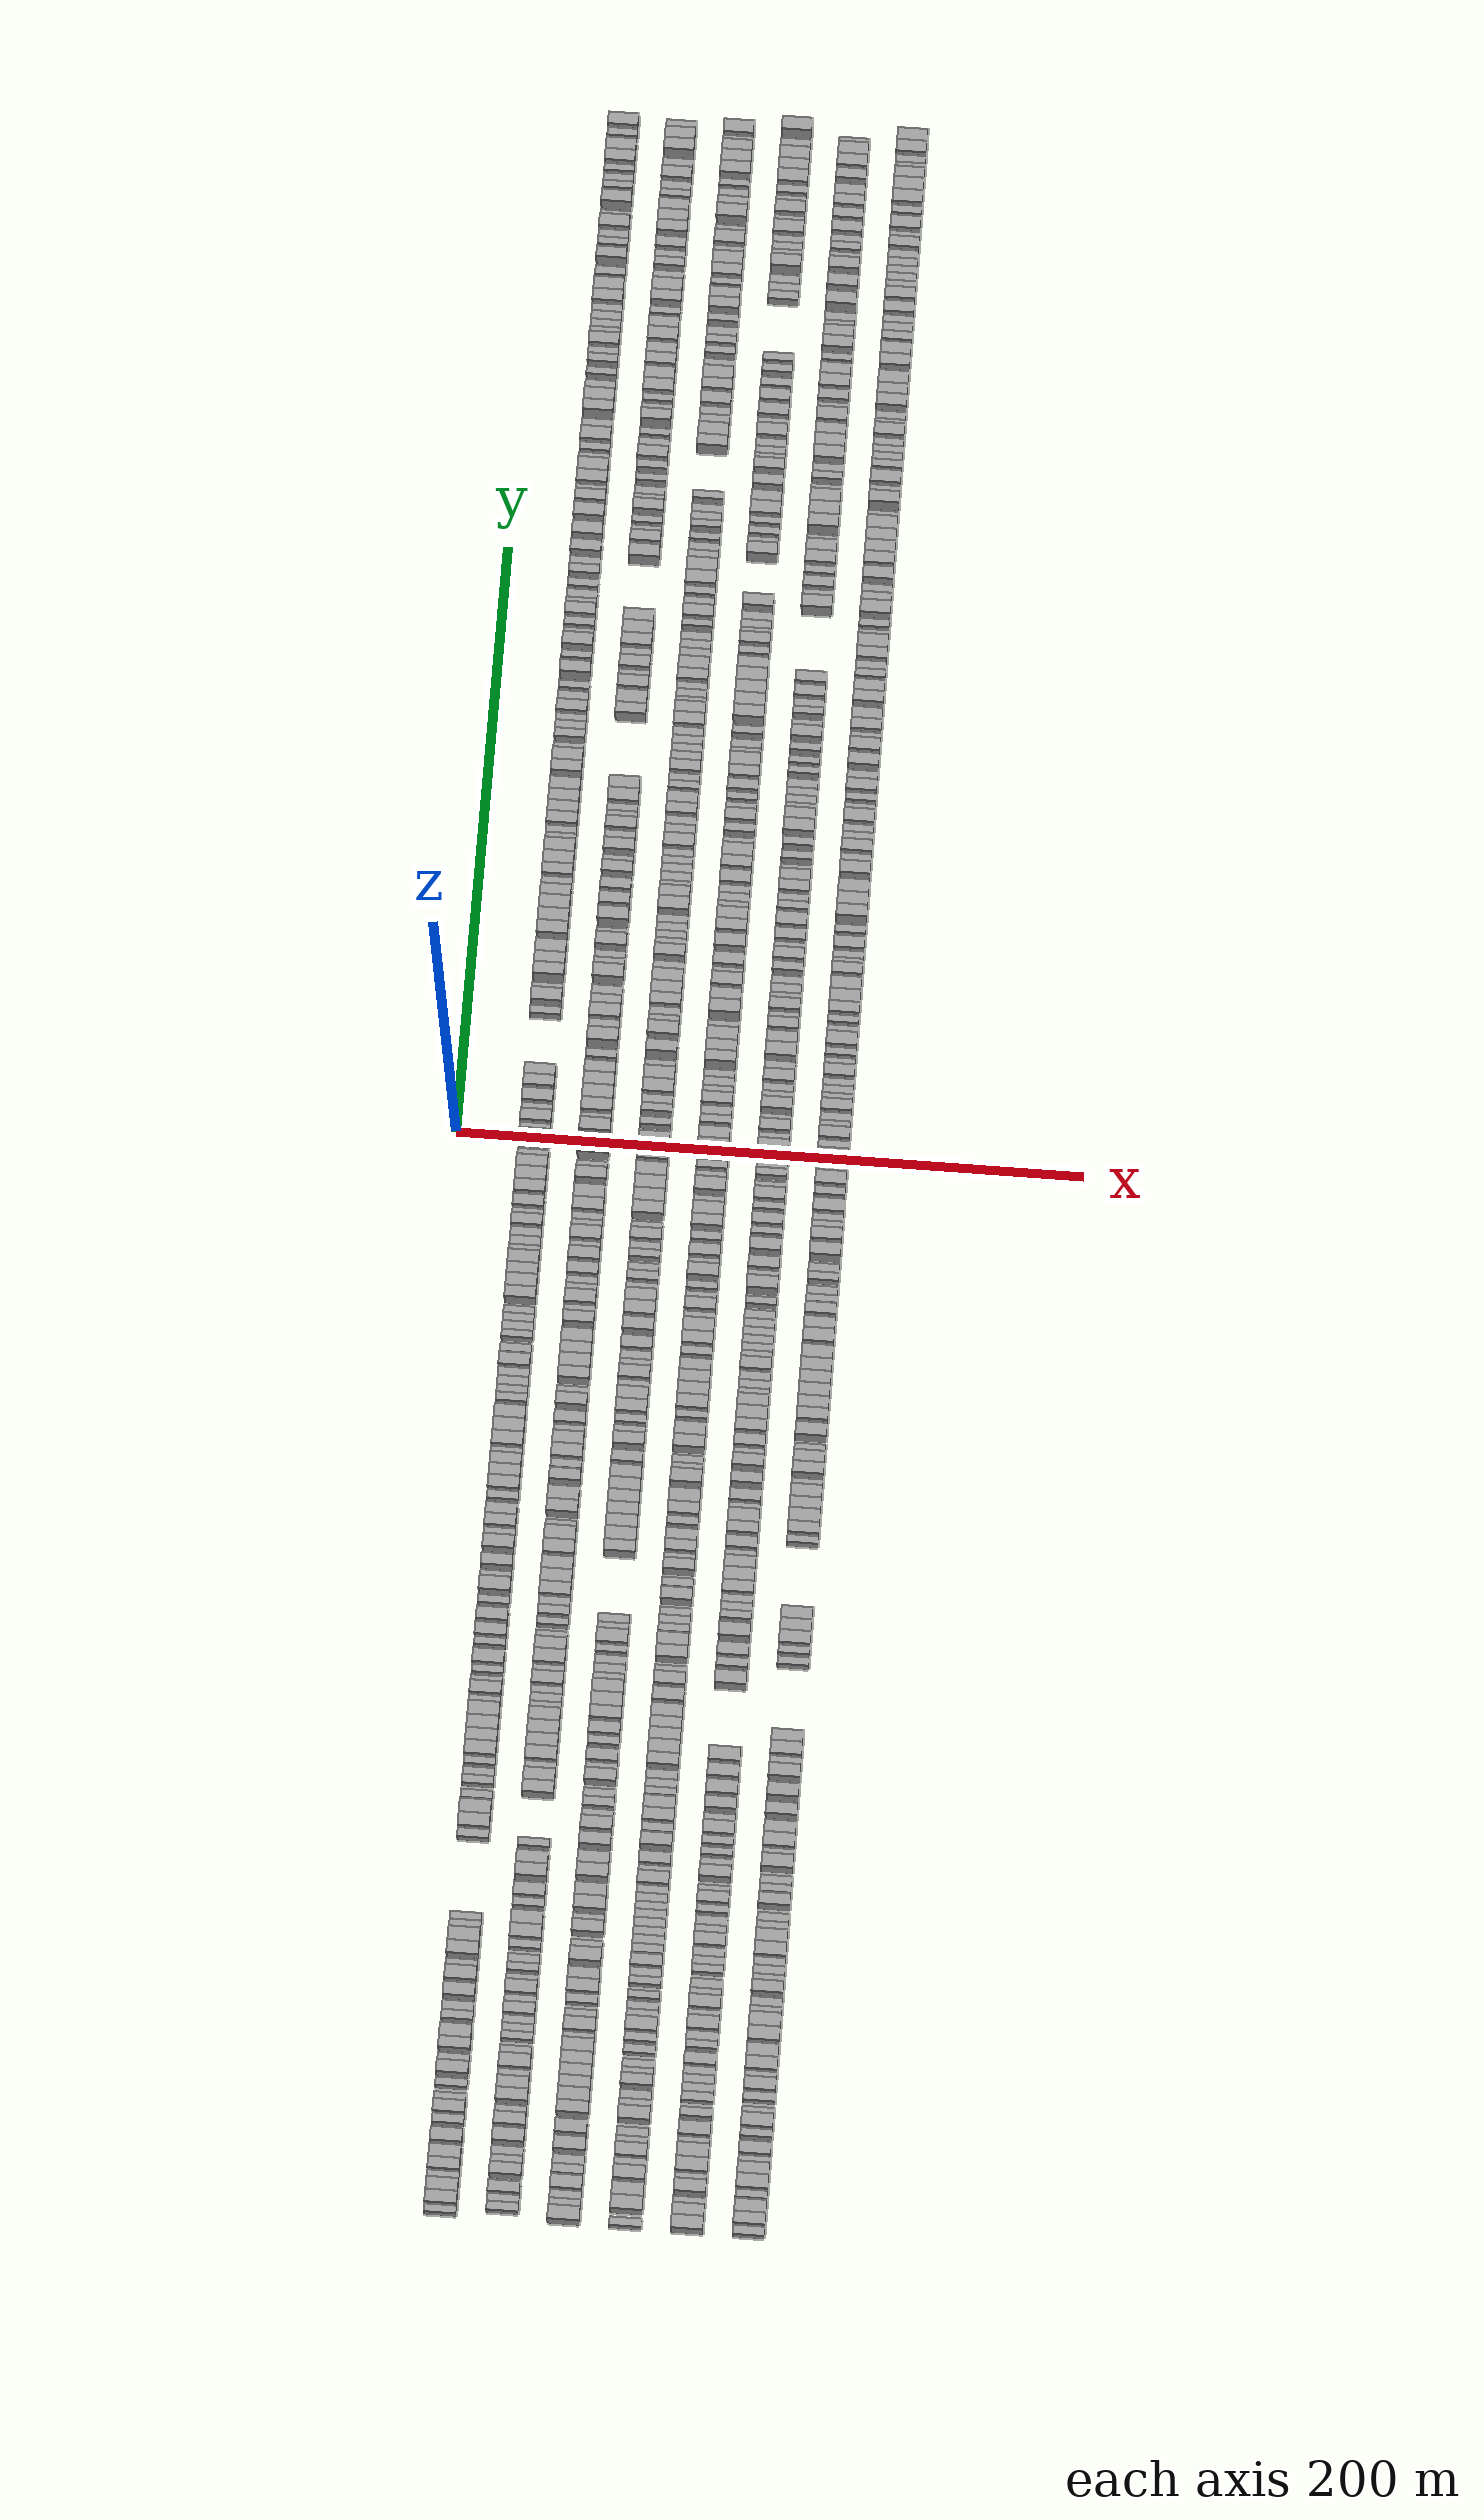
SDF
<sdf version="1.6">
 <world name="default">
  <scene>
   <sky><clouds><speed>12</speed></clouds></sky>
   <ambient>0.4 0.4 0.4 1</ambient>
   <background>0.7 0.7 0.7 1</background>
   <shadows>1</shadows>
  </scene>
  <gravity>0 0 -9.8066</gravity>
  <magnetic_field>6e-06 2.3e-05 -4.2e-05</magnetic_field>
  <physics default="0" name="default_physics" type="ode">
   <ode>
    <solver>
     <type>quick</type>
     <iters>10</iters>
     <sor>1.0</sor>
     <use_dynamic_moi_rescaling>0</use_dynamic_moi_rescaling>
    </solver>
    <constraints>
     <cfm>0</cfm>
     <erp>0.2</erp>
     <contact_max_correcting_vel>100</contact_max_correcting_vel>
     <contact_surface_layer>0.001</contact_surface_layer>
    </constraints>
   </ode>
   <max_step_size>0.004</max_step_size>
   <real_time_factor>1</real_time_factor>
   <real_time_update_rate>250</real_time_update_rate>
  </physics>
  <light name="sun" type="directional">
   <pose>0 0 10 0 0 0</pose>
   <diffuse>0.8 0.8 0.8 1</diffuse>
   <specular>0.2 0.2 0.2 1</specular>
   <attenuation>
    <range>1000</range>
    <constant>0.9</constant>
    <linear>0.01</linear>
    <quadratic>0.001</quadratic>
   </attenuation>
   <direction>-0.5 0.1 -0.9</direction>
  </light>
  <model name="building_1">
   <static>1</static>
   <pose>25.0000 -348.7629 0 0.000000 0.000000 0.000000</pose>
   <link name="link">
    <pose>0 0 3.00 0 0 0</pose>
    <collision name="collision"><geometry><box><size>10.0000 2.4742 6.0000</size></box></geometry></collision>
    <visual name="visual">
     <cast_shadows>0</cast_shadows>
     <geometry><box><size>10.0000 2.4742 6.0000</size></box></geometry>
     <material>
      <script>
       <uri>model://grey_wall/materials/scripts</uri>
       <uri>model://grey_wall/materials/textures</uri>
       <name>vrc/grey_wall</name>
      </script>
     </material>
    </visual>
   </link>
  </model>
  <model name="building_2">
   <static>1</static>
   <pose>25.0000 -345.5287 0 0.000000 0.000000 0.000000</pose>
   <link name="link">
    <pose>0 0 4.50 0 0 0</pose>
    <collision name="collision"><geometry><box><size>10.0000 3.9941 9.0000</size></box></geometry></collision>
    <visual name="visual">
     <cast_shadows>0</cast_shadows>
     <geometry><box><size>10.0000 3.9941 9.0000</size></box></geometry>
     <material>
      <script>
       <uri>model://grey_wall/materials/scripts</uri>
       <uri>model://grey_wall/materials/textures</uri>
       <name>vrc/grey_wall</name>
      </script>
     </material>
    </visual>
   </link>
  </model>
  <model name="building_3">
   <static>1</static>
   <pose>25.0000 -341.5436 0 0.000000 0.000000 0.000000</pose>
   <link name="link">
    <pose>0 0 4.50 0 0 0</pose>
    <collision name="collision"><geometry><box><size>10.0000 3.9762 9.0000</size></box></geometry></collision>
    <visual name="visual">
     <cast_shadows>0</cast_shadows>
     <geometry><box><size>10.0000 3.9762 9.0000</size></box></geometry>
     <material>
      <script>
       <uri>model://grey_wall/materials/scripts</uri>
       <uri>model://grey_wall/materials/textures</uri>
       <name>vrc/grey_wall</name>
      </script>
     </material>
    </visual>
   </link>
  </model>
  <model name="building_4">
   <static>1</static>
   <pose>25.0000 -338.1985 0 0.000000 0.000000 0.000000</pose>
   <link name="link">
    <pose>0 0 3.00 0 0 0</pose>
    <collision name="collision"><geometry><box><size>10.0000 2.7139 6.0000</size></box></geometry></collision>
    <visual name="visual">
     <cast_shadows>0</cast_shadows>
     <geometry><box><size>10.0000 2.7139 6.0000</size></box></geometry>
     <material>
      <script>
       <uri>model://grey_wall/materials/scripts</uri>
       <uri>model://grey_wall/materials/textures</uri>
       <name>vrc/grey_wall</name>
      </script>
     </material>
    </visual>
   </link>
  </model>
  <model name="building_5">
   <static>1</static>
   <pose>25.0000 -335.0386 0 0.000000 0.000000 0.000000</pose>
   <link name="link">
    <pose>0 0 4.50 0 0 0</pose>
    <collision name="collision"><geometry><box><size>10.0000 3.6061 9.0000</size></box></geometry></collision>
    <visual name="visual">
     <cast_shadows>0</cast_shadows>
     <geometry><box><size>10.0000 3.6061 9.0000</size></box></geometry>
     <material>
      <script>
       <uri>model://grey_wall/materials/scripts</uri>
       <uri>model://grey_wall/materials/textures</uri>
       <name>vrc/grey_wall</name>
      </script>
     </material>
    </visual>
   </link>
  </model>
  <model name="building_6">
   <static>1</static>
   <pose>25.0000 -331.1882 0 0.000000 0.000000 0.000000</pose>
   <link name="link">
    <pose>0 0 4.50 0 0 0</pose>
    <collision name="collision"><geometry><box><size>10.0000 4.0946 9.0000</size></box></geometry></collision>
    <visual name="visual">
     <cast_shadows>0</cast_shadows>
     <geometry><box><size>10.0000 4.0946 9.0000</size></box></geometry>
     <material>
      <script>
       <uri>model://grey_wall/materials/scripts</uri>
       <uri>model://grey_wall/materials/textures</uri>
       <name>vrc/grey_wall</name>
      </script>
     </material>
    </visual>
   </link>
  </model>
  <model name="building_7">
   <static>1</static>
   <pose>25.0000 -325.9881 0 0.000000 0.000000 0.000000</pose>
   <link name="link">
    <pose>0 0 4.50 0 0 0</pose>
    <collision name="collision"><geometry><box><size>10.0000 4.3057 9.0000</size></box></geometry></collision>
    <visual name="visual">
     <cast_shadows>0</cast_shadows>
     <geometry><box><size>10.0000 4.3057 9.0000</size></box></geometry>
     <material>
      <script>
       <uri>model://grey_wall/materials/scripts</uri>
       <uri>model://grey_wall/materials/textures</uri>
       <name>vrc/grey_wall</name>
      </script>
     </material>
    </visual>
   </link>
  </model>
  <model name="building_8">
   <static>1</static>
   <pose>25.0000 -320.3770 0 0.000000 0.000000 0.000000</pose>
   <link name="link">
    <pose>0 0 3.00 0 0 0</pose>
    <collision name="collision"><geometry><box><size>10.0000 2.9164 6.0000</size></box></geometry></collision>
    <visual name="visual">
     <cast_shadows>0</cast_shadows>
     <geometry><box><size>10.0000 2.9164 6.0000</size></box></geometry>
     <material>
      <script>
       <uri>model://grey_wall/materials/scripts</uri>
       <uri>model://grey_wall/materials/textures</uri>
       <name>vrc/grey_wall</name>
      </script>
     </material>
    </visual>
   </link>
  </model>
  <model name="building_9">
   <static>1</static>
   <pose>25.0000 -316.9944 0 0.000000 0.000000 0.000000</pose>
   <link name="link">
    <pose>0 0 4.50 0 0 0</pose>
    <collision name="collision"><geometry><box><size>10.0000 3.8488 9.0000</size></box></geometry></collision>
    <visual name="visual">
     <cast_shadows>0</cast_shadows>
     <geometry><box><size>10.0000 3.8488 9.0000</size></box></geometry>
     <material>
      <script>
       <uri>model://grey_wall/materials/scripts</uri>
       <uri>model://grey_wall/materials/textures</uri>
       <name>vrc/grey_wall</name>
      </script>
     </material>
    </visual>
   </link>
  </model>
  <model name="building_10">
   <static>1</static>
   <pose>25.0000 -313.6656 0 0.000000 0.000000 0.000000</pose>
   <link name="link">
    <pose>0 0 3.00 0 0 0</pose>
    <collision name="collision"><geometry><box><size>10.0000 2.8087 6.0000</size></box></geometry></collision>
    <visual name="visual">
     <cast_shadows>0</cast_shadows>
     <geometry><box><size>10.0000 2.8087 6.0000</size></box></geometry>
     <material>
      <script>
       <uri>model://grey_wall/materials/scripts</uri>
       <uri>model://grey_wall/materials/textures</uri>
       <name>vrc/grey_wall</name>
      </script>
     </material>
    </visual>
   </link>
  </model>
  <model name="building_11">
   <static>1</static>
   <pose>25.0000 -308.9259 0 0.000000 0.000000 0.000000</pose>
   <link name="link">
    <pose>0 0 3.00 0 0 0</pose>
    <collision name="collision"><geometry><box><size>10.0000 2.6708 6.0000</size></box></geometry></collision>
    <visual name="visual">
     <cast_shadows>0</cast_shadows>
     <geometry><box><size>10.0000 2.6708 6.0000</size></box></geometry>
     <material>
      <script>
       <uri>model://grey_wall/materials/scripts</uri>
       <uri>model://grey_wall/materials/textures</uri>
       <name>vrc/grey_wall</name>
      </script>
     </material>
    </visual>
   </link>
  </model>
  <model name="building_12">
   <static>1</static>
   <pose>25.0000 -304.6251 0 0.000000 0.000000 0.000000</pose>
   <link name="link">
    <pose>0 0 4.50 0 0 0</pose>
    <collision name="collision"><geometry><box><size>10.0000 3.9308 9.0000</size></box></geometry></collision>
    <visual name="visual">
     <cast_shadows>0</cast_shadows>
     <geometry><box><size>10.0000 3.9308 9.0000</size></box></geometry>
     <material>
      <script>
       <uri>model://grey_wall/materials/scripts</uri>
       <uri>model://grey_wall/materials/textures</uri>
       <name>vrc/grey_wall</name>
      </script>
     </material>
    </visual>
   </link>
  </model>
  <model name="building_13">
   <static>1</static>
   <pose>25.0000 -301.2388 0 0.000000 0.000000 0.000000</pose>
   <link name="link">
    <pose>0 0 3.00 0 0 0</pose>
    <collision name="collision"><geometry><box><size>10.0000 2.8419 6.0000</size></box></geometry></collision>
    <visual name="visual">
     <cast_shadows>0</cast_shadows>
     <geometry><box><size>10.0000 2.8419 6.0000</size></box></geometry>
     <material>
      <script>
       <uri>model://grey_wall/materials/scripts</uri>
       <uri>model://grey_wall/materials/textures</uri>
       <name>vrc/grey_wall</name>
      </script>
     </material>
    </visual>
   </link>
  </model>
  <model name="building_14">
   <static>1</static>
   <pose>25.0000 -297.0161 0 0.000000 0.000000 0.000000</pose>
   <link name="link">
    <pose>0 0 4.50 0 0 0</pose>
    <collision name="collision"><geometry><box><size>10.0000 3.6035 9.0000</size></box></geometry></collision>
    <visual name="visual">
     <cast_shadows>0</cast_shadows>
     <geometry><box><size>10.0000 3.6035 9.0000</size></box></geometry>
     <material>
      <script>
       <uri>model://grey_wall/materials/scripts</uri>
       <uri>model://grey_wall/materials/textures</uri>
       <name>vrc/grey_wall</name>
      </script>
     </material>
    </visual>
   </link>
  </model>
  <model name="building_15">
   <static>1</static>
   <pose>25.0000 -293.0880 0 0.000000 0.000000 0.000000</pose>
   <link name="link">
    <pose>0 0 4.50 0 0 0</pose>
    <collision name="collision"><geometry><box><size>10.0000 4.2526 9.0000</size></box></geometry></collision>
    <visual name="visual">
     <cast_shadows>0</cast_shadows>
     <geometry><box><size>10.0000 4.2526 9.0000</size></box></geometry>
     <material>
      <script>
       <uri>model://grey_wall/materials/scripts</uri>
       <uri>model://grey_wall/materials/textures</uri>
       <name>vrc/grey_wall</name>
      </script>
     </material>
    </visual>
   </link>
  </model>
  <model name="building_16">
   <static>1</static>
   <pose>25.0000 -287.5658 0 0.000000 0.000000 0.000000</pose>
   <link name="link">
    <pose>0 0 3.00 0 0 0</pose>
    <collision name="collision"><geometry><box><size>10.0000 2.7919 6.0000</size></box></geometry></collision>
    <visual name="visual">
     <cast_shadows>0</cast_shadows>
     <geometry><box><size>10.0000 2.7919 6.0000</size></box></geometry>
     <material>
      <script>
       <uri>model://grey_wall/materials/scripts</uri>
       <uri>model://grey_wall/materials/textures</uri>
       <name>vrc/grey_wall</name>
      </script>
     </material>
    </visual>
   </link>
  </model>
  <model name="building_17">
   <static>1</static>
   <pose>25.0000 -284.6792 0 0.000000 0.000000 0.000000</pose>
   <link name="link">
    <pose>0 0 3.00 0 0 0</pose>
    <collision name="collision"><geometry><box><size>10.0000 2.9813 6.0000</size></box></geometry></collision>
    <visual name="visual">
     <cast_shadows>0</cast_shadows>
     <geometry><box><size>10.0000 2.9813 6.0000</size></box></geometry>
     <material>
      <script>
       <uri>model://grey_wall/materials/scripts</uri>
       <uri>model://grey_wall/materials/textures</uri>
       <name>vrc/grey_wall</name>
      </script>
     </material>
    </visual>
   </link>
  </model>
  <model name="building_18">
   <static>1</static>
   <pose>25.0000 -280.0701 0 0.000000 0.000000 0.000000</pose>
   <link name="link">
    <pose>0 0 4.50 0 0 0</pose>
    <collision name="collision"><geometry><box><size>10.0000 4.2370 9.0000</size></box></geometry></collision>
    <visual name="visual">
     <cast_shadows>0</cast_shadows>
     <geometry><box><size>10.0000 4.2370 9.0000</size></box></geometry>
     <material>
      <script>
       <uri>model://grey_wall/materials/scripts</uri>
       <uri>model://grey_wall/materials/textures</uri>
       <name>vrc/grey_wall</name>
      </script>
     </material>
    </visual>
   </link>
  </model>
  <model name="building_19">
   <static>1</static>
   <pose>25.0000 -274.7461 0 0.000000 0.000000 0.000000</pose>
   <link name="link">
    <pose>0 0 4.50 0 0 0</pose>
    <collision name="collision"><geometry><box><size>10.0000 4.4108 9.0000</size></box></geometry></collision>
    <visual name="visual">
     <cast_shadows>0</cast_shadows>
     <geometry><box><size>10.0000 4.4108 9.0000</size></box></geometry>
     <material>
      <script>
       <uri>model://grey_wall/materials/scripts</uri>
       <uri>model://grey_wall/materials/textures</uri>
       <name>vrc/grey_wall</name>
      </script>
     </material>
    </visual>
   </link>
  </model>
  <model name="building_20">
   <static>1</static>
   <pose>25.0000 -271.2232 0 0.000000 0.000000 0.000000</pose>
   <link name="link">
    <pose>0 0 3.00 0 0 0</pose>
    <collision name="collision"><geometry><box><size>10.0000 2.6351 6.0000</size></box></geometry></collision>
    <visual name="visual">
     <cast_shadows>0</cast_shadows>
     <geometry><box><size>10.0000 2.6351 6.0000</size></box></geometry>
     <material>
      <script>
       <uri>model://grey_wall/materials/scripts</uri>
       <uri>model://grey_wall/materials/textures</uri>
       <name>vrc/grey_wall</name>
      </script>
     </material>
    </visual>
   </link>
  </model>
  <model name="building_21">
   <static>1</static>
   <pose>25.0000 -266.8269 0 0.000000 0.000000 0.000000</pose>
   <link name="link">
    <pose>0 0 4.50 0 0 0</pose>
    <collision name="collision"><geometry><box><size>10.0000 4.1574 9.0000</size></box></geometry></collision>
    <visual name="visual">
     <cast_shadows>0</cast_shadows>
     <geometry><box><size>10.0000 4.1574 9.0000</size></box></geometry>
     <material>
      <script>
       <uri>model://grey_wall/materials/scripts</uri>
       <uri>model://grey_wall/materials/textures</uri>
       <name>vrc/grey_wall</name>
      </script>
     </material>
    </visual>
   </link>
  </model>
  <model name="building_22">
   <static>1</static>
   <pose>25.0000 -262.5667 0 0.000000 0.000000 0.000000</pose>
   <link name="link">
    <pose>0 0 4.50 0 0 0</pose>
    <collision name="collision"><geometry><box><size>10.0000 4.3631 9.0000</size></box></geometry></collision>
    <visual name="visual">
     <cast_shadows>0</cast_shadows>
     <geometry><box><size>10.0000 4.3631 9.0000</size></box></geometry>
     <material>
      <script>
       <uri>model://grey_wall/materials/scripts</uri>
       <uri>model://grey_wall/materials/textures</uri>
       <name>vrc/grey_wall</name>
      </script>
     </material>
    </visual>
   </link>
  </model>
  <model name="building_23">
   <static>1</static>
   <pose>25.0000 -258.9067 0 0.000000 0.000000 0.000000</pose>
   <link name="link">
    <pose>0 0 3.00 0 0 0</pose>
    <collision name="collision"><geometry><box><size>10.0000 2.9569 6.0000</size></box></geometry></collision>
    <visual name="visual">
     <cast_shadows>0</cast_shadows>
     <geometry><box><size>10.0000 2.9569 6.0000</size></box></geometry>
     <material>
      <script>
       <uri>model://grey_wall/materials/scripts</uri>
       <uri>model://grey_wall/materials/textures</uri>
       <name>vrc/grey_wall</name>
      </script>
     </material>
    </visual>
   </link>
  </model>
  <model name="building_24">
   <static>1</static>
   <pose>25.0000 -256.2134 0 0.000000 0.000000 0.000000</pose>
   <link name="link">
    <pose>0 0 3.00 0 0 0</pose>
    <collision name="collision"><geometry><box><size>10.0000 2.4297 6.0000</size></box></geometry></collision>
    <visual name="visual">
     <cast_shadows>0</cast_shadows>
     <geometry><box><size>10.0000 2.4297 6.0000</size></box></geometry>
     <material>
      <script>
       <uri>model://grey_wall/materials/scripts</uri>
       <uri>model://grey_wall/materials/textures</uri>
       <name>vrc/grey_wall</name>
      </script>
     </material>
    </visual>
   </link>
  </model>
  <model name="building_25">
   <static>1</static>
   <pose>25.0000 -229.6498 0 0.000000 0.000000 0.000000</pose>
   <link name="link">
    <pose>0 0 3.00 0 0 0</pose>
    <collision name="collision"><geometry><box><size>10.0000 2.8992 6.0000</size></box></geometry></collision>
    <visual name="visual">
     <cast_shadows>0</cast_shadows>
     <geometry><box><size>10.0000 2.8992 6.0000</size></box></geometry>
     <material>
      <script>
       <uri>model://grey_wall/materials/scripts</uri>
       <uri>model://grey_wall/materials/textures</uri>
       <name>vrc/grey_wall</name>
      </script>
     </material>
    </visual>
   </link>
  </model>
  <model name="building_26">
   <static>1</static>
   <pose>25.0000 -226.0453 0 0.000000 0.000000 0.000000</pose>
   <link name="link">
    <pose>0 0 4.50 0 0 0</pose>
    <collision name="collision"><geometry><box><size>10.0000 4.3099 9.0000</size></box></geometry></collision>
    <visual name="visual">
     <cast_shadows>0</cast_shadows>
     <geometry><box><size>10.0000 4.3099 9.0000</size></box></geometry>
     <material>
      <script>
       <uri>model://grey_wall/materials/scripts</uri>
       <uri>model://grey_wall/materials/textures</uri>
       <name>vrc/grey_wall</name>
      </script>
     </material>
    </visual>
   </link>
  </model>
  <model name="building_27">
   <static>1</static>
   <pose>25.0000 -221.6928 0 0.000000 0.000000 0.000000</pose>
   <link name="link">
    <pose>0 0 4.50 0 0 0</pose>
    <collision name="collision"><geometry><box><size>10.0000 4.3951 9.0000</size></box></geometry></collision>
    <visual name="visual">
     <cast_shadows>0</cast_shadows>
     <geometry><box><size>10.0000 4.3951 9.0000</size></box></geometry>
     <material>
      <script>
       <uri>model://grey_wall/materials/scripts</uri>
       <uri>model://grey_wall/materials/textures</uri>
       <name>vrc/grey_wall</name>
      </script>
     </material>
    </visual>
   </link>
  </model>
  <model name="building_28">
   <static>1</static>
   <pose>25.0000 -217.1620 0 0.000000 0.000000 0.000000</pose>
   <link name="link">
    <pose>0 0 3.00 0 0 0</pose>
    <collision name="collision"><geometry><box><size>10.0000 2.6665 6.0000</size></box></geometry></collision>
    <visual name="visual">
     <cast_shadows>0</cast_shadows>
     <geometry><box><size>10.0000 2.6665 6.0000</size></box></geometry>
     <material>
      <script>
       <uri>model://grey_wall/materials/scripts</uri>
       <uri>model://grey_wall/materials/textures</uri>
       <name>vrc/grey_wall</name>
      </script>
     </material>
    </visual>
   </link>
  </model>
  <model name="building_29">
   <static>1</static>
   <pose>25.0000 -212.4544 0 0.000000 0.000000 0.000000</pose>
   <link name="link">
    <pose>0 0 3.00 0 0 0</pose>
    <collision name="collision"><geometry><box><size>10.0000 2.7485 6.0000</size></box></geometry></collision>
    <visual name="visual">
     <cast_shadows>0</cast_shadows>
     <geometry><box><size>10.0000 2.7485 6.0000</size></box></geometry>
     <material>
      <script>
       <uri>model://grey_wall/materials/scripts</uri>
       <uri>model://grey_wall/materials/textures</uri>
       <name>vrc/grey_wall</name>
      </script>
     </material>
    </visual>
   </link>
  </model>
  <model name="building_30">
   <static>1</static>
   <pose>25.0000 -209.8018 0 0.000000 0.000000 0.000000</pose>
   <link name="link">
    <pose>0 0 3.00 0 0 0</pose>
    <collision name="collision"><geometry><box><size>10.0000 2.5568 6.0000</size></box></geometry></collision>
    <visual name="visual">
     <cast_shadows>0</cast_shadows>
     <geometry><box><size>10.0000 2.5568 6.0000</size></box></geometry>
     <material>
      <script>
       <uri>model://grey_wall/materials/scripts</uri>
       <uri>model://grey_wall/materials/textures</uri>
       <name>vrc/grey_wall</name>
      </script>
     </material>
    </visual>
   </link>
  </model>
  <model name="building_31">
   <static>1</static>
   <pose>25.0000 -206.2755 0 0.000000 0.000000 0.000000</pose>
   <link name="link">
    <pose>0 0 3.00 0 0 0</pose>
    <collision name="collision"><geometry><box><size>10.0000 2.4958 6.0000</size></box></geometry></collision>
    <visual name="visual">
     <cast_shadows>0</cast_shadows>
     <geometry><box><size>10.0000 2.4958 6.0000</size></box></geometry>
     <material>
      <script>
       <uri>model://grey_wall/materials/scripts</uri>
       <uri>model://grey_wall/materials/textures</uri>
       <name>vrc/grey_wall</name>
      </script>
     </material>
    </visual>
   </link>
  </model>
  <model name="building_32">
   <static>1</static>
   <pose>25.0000 -202.8057 0 0.000000 0.000000 0.000000</pose>
   <link name="link">
    <pose>0 0 4.50 0 0 0</pose>
    <collision name="collision"><geometry><box><size>10.0000 4.4438 9.0000</size></box></geometry></collision>
    <visual name="visual">
     <cast_shadows>0</cast_shadows>
     <geometry><box><size>10.0000 4.4438 9.0000</size></box></geometry>
     <material>
      <script>
       <uri>model://grey_wall/materials/scripts</uri>
       <uri>model://grey_wall/materials/textures</uri>
       <name>vrc/grey_wall</name>
      </script>
     </material>
    </visual>
   </link>
  </model>
  <model name="building_33">
   <static>1</static>
   <pose>25.0000 -198.6447 0 0.000000 0.000000 0.000000</pose>
   <link name="link">
    <pose>0 0 4.50 0 0 0</pose>
    <collision name="collision"><geometry><box><size>10.0000 3.8781 9.0000</size></box></geometry></collision>
    <visual name="visual">
     <cast_shadows>0</cast_shadows>
     <geometry><box><size>10.0000 3.8781 9.0000</size></box></geometry>
     <material>
      <script>
       <uri>model://grey_wall/materials/scripts</uri>
       <uri>model://grey_wall/materials/textures</uri>
       <name>vrc/grey_wall</name>
      </script>
     </material>
    </visual>
   </link>
  </model>
  <model name="building_34">
   <static>1</static>
   <pose>25.0000 -194.5778 0 0.000000 0.000000 0.000000</pose>
   <link name="link">
    <pose>0 0 4.50 0 0 0</pose>
    <collision name="collision"><geometry><box><size>10.0000 4.2557 9.0000</size></box></geometry></collision>
    <visual name="visual">
     <cast_shadows>0</cast_shadows>
     <geometry><box><size>10.0000 4.2557 9.0000</size></box></geometry>
     <material>
      <script>
       <uri>model://grey_wall/materials/scripts</uri>
       <uri>model://grey_wall/materials/textures</uri>
       <name>vrc/grey_wall</name>
      </script>
     </material>
    </visual>
   </link>
  </model>
  <model name="building_35">
   <static>1</static>
   <pose>25.0000 -190.2086 0 0.000000 0.000000 0.000000</pose>
   <link name="link">
    <pose>0 0 4.50 0 0 0</pose>
    <collision name="collision"><geometry><box><size>10.0000 4.4829 9.0000</size></box></geometry></collision>
    <visual name="visual">
     <cast_shadows>0</cast_shadows>
     <geometry><box><size>10.0000 4.4829 9.0000</size></box></geometry>
     <material>
      <script>
       <uri>model://grey_wall/materials/scripts</uri>
       <uri>model://grey_wall/materials/textures</uri>
       <name>vrc/grey_wall</name>
      </script>
     </material>
    </visual>
   </link>
  </model>
  <model name="building_36">
   <static>1</static>
   <pose>25.0000 -186.6460 0 0.000000 0.000000 0.000000</pose>
   <link name="link">
    <pose>0 0 3.00 0 0 0</pose>
    <collision name="collision"><geometry><box><size>10.0000 2.6423 6.0000</size></box></geometry></collision>
    <visual name="visual">
     <cast_shadows>0</cast_shadows>
     <geometry><box><size>10.0000 2.6423 6.0000</size></box></geometry>
     <material>
      <script>
       <uri>model://grey_wall/materials/scripts</uri>
       <uri>model://grey_wall/materials/textures</uri>
       <name>vrc/grey_wall</name>
      </script>
     </material>
    </visual>
   </link>
  </model>
  <model name="building_37">
   <static>1</static>
   <pose>25.0000 -183.3531 0 0.000000 0.000000 0.000000</pose>
   <link name="link">
    <pose>0 0 4.50 0 0 0</pose>
    <collision name="collision"><geometry><box><size>10.0000 3.9435 9.0000</size></box></geometry></collision>
    <visual name="visual">
     <cast_shadows>0</cast_shadows>
     <geometry><box><size>10.0000 3.9435 9.0000</size></box></geometry>
     <material>
      <script>
       <uri>model://grey_wall/materials/scripts</uri>
       <uri>model://grey_wall/materials/textures</uri>
       <name>vrc/grey_wall</name>
      </script>
     </material>
    </visual>
   </link>
  </model>
  <model name="building_38">
   <static>1</static>
   <pose>25.0000 -180.1705 0 0.000000 0.000000 0.000000</pose>
   <link name="link">
    <pose>0 0 3.00 0 0 0</pose>
    <collision name="collision"><geometry><box><size>10.0000 2.4218 6.0000</size></box></geometry></collision>
    <visual name="visual">
     <cast_shadows>0</cast_shadows>
     <geometry><box><size>10.0000 2.4218 6.0000</size></box></geometry>
     <material>
      <script>
       <uri>model://grey_wall/materials/scripts</uri>
       <uri>model://grey_wall/materials/textures</uri>
       <name>vrc/grey_wall</name>
      </script>
     </material>
    </visual>
   </link>
  </model>
  <model name="building_39">
   <static>1</static>
   <pose>25.0000 -176.7080 0 0.000000 0.000000 0.000000</pose>
   <link name="link">
    <pose>0 0 3.00 0 0 0</pose>
    <collision name="collision"><geometry><box><size>10.0000 2.5031 6.0000</size></box></geometry></collision>
    <visual name="visual">
     <cast_shadows>0</cast_shadows>
     <geometry><box><size>10.0000 2.5031 6.0000</size></box></geometry>
     <material>
      <script>
       <uri>model://grey_wall/materials/scripts</uri>
       <uri>model://grey_wall/materials/textures</uri>
       <name>vrc/grey_wall</name>
      </script>
     </material>
    </visual>
   </link>
  </model>
  <model name="building_40">
   <static>1</static>
   <pose>25.0000 -173.2176 0 0.000000 0.000000 0.000000</pose>
   <link name="link">
    <pose>0 0 4.50 0 0 0</pose>
    <collision name="collision"><geometry><box><size>10.0000 4.4778 9.0000</size></box></geometry></collision>
    <visual name="visual">
     <cast_shadows>0</cast_shadows>
     <geometry><box><size>10.0000 4.4778 9.0000</size></box></geometry>
     <material>
      <script>
       <uri>model://grey_wall/materials/scripts</uri>
       <uri>model://grey_wall/materials/textures</uri>
       <name>vrc/grey_wall</name>
      </script>
     </material>
    </visual>
   </link>
  </model>
  <model name="building_41">
   <static>1</static>
   <pose>25.0000 -167.7174 0 0.000000 0.000000 0.000000</pose>
   <link name="link">
    <pose>0 0 3.00 0 0 0</pose>
    <collision name="collision"><geometry><box><size>10.0000 2.5224 6.0000</size></box></geometry></collision>
    <visual name="visual">
     <cast_shadows>0</cast_shadows>
     <geometry><box><size>10.0000 2.5224 6.0000</size></box></geometry>
     <material>
      <script>
       <uri>model://grey_wall/materials/scripts</uri>
       <uri>model://grey_wall/materials/textures</uri>
       <name>vrc/grey_wall</name>
      </script>
     </material>
    </visual>
   </link>
  </model>
  <model name="building_42">
   <static>1</static>
   <pose>25.0000 -164.4643 0 0.000000 0.000000 0.000000</pose>
   <link name="link">
    <pose>0 0 4.50 0 0 0</pose>
    <collision name="collision"><geometry><box><size>10.0000 3.9839 9.0000</size></box></geometry></collision>
    <visual name="visual">
     <cast_shadows>0</cast_shadows>
     <geometry><box><size>10.0000 3.9839 9.0000</size></box></geometry>
     <material>
      <script>
       <uri>model://grey_wall/materials/scripts</uri>
       <uri>model://grey_wall/materials/textures</uri>
       <name>vrc/grey_wall</name>
      </script>
     </material>
    </visual>
   </link>
  </model>
  <model name="building_43">
   <static>1</static>
   <pose>25.0000 -159.4540 0 0.000000 0.000000 0.000000</pose>
   <link name="link">
    <pose>0 0 4.50 0 0 0</pose>
    <collision name="collision"><geometry><box><size>10.0000 4.0367 9.0000</size></box></geometry></collision>
    <visual name="visual">
     <cast_shadows>0</cast_shadows>
     <geometry><box><size>10.0000 4.0367 9.0000</size></box></geometry>
     <material>
      <script>
       <uri>model://grey_wall/materials/scripts</uri>
       <uri>model://grey_wall/materials/textures</uri>
       <name>vrc/grey_wall</name>
      </script>
     </material>
    </visual>
   </link>
  </model>
  <model name="building_44">
   <static>1</static>
   <pose>25.0000 -154.1404 0 0.000000 0.000000 0.000000</pose>
   <link name="link">
    <pose>0 0 3.00 0 0 0</pose>
    <collision name="collision"><geometry><box><size>10.0000 2.5905 6.0000</size></box></geometry></collision>
    <visual name="visual">
     <cast_shadows>0</cast_shadows>
     <geometry><box><size>10.0000 2.5905 6.0000</size></box></geometry>
     <material>
      <script>
       <uri>model://grey_wall/materials/scripts</uri>
       <uri>model://grey_wall/materials/textures</uri>
       <name>vrc/grey_wall</name>
      </script>
     </material>
    </visual>
   </link>
  </model>
  <model name="building_45">
   <static>1</static>
   <pose>25.0000 -149.6113 0 0.000000 0.000000 0.000000</pose>
   <link name="link">
    <pose>0 0 4.50 0 0 0</pose>
    <collision name="collision"><geometry><box><size>10.0000 4.4676 9.0000</size></box></geometry></collision>
    <visual name="visual">
     <cast_shadows>0</cast_shadows>
     <geometry><box><size>10.0000 4.4676 9.0000</size></box></geometry>
     <material>
      <script>
       <uri>model://grey_wall/materials/scripts</uri>
       <uri>model://grey_wall/materials/textures</uri>
       <name>vrc/grey_wall</name>
      </script>
     </material>
    </visual>
   </link>
  </model>
  <model name="building_46">
   <static>1</static>
   <pose>25.0000 -146.0811 0 0.000000 0.000000 0.000000</pose>
   <link name="link">
    <pose>0 0 3.00 0 0 0</pose>
    <collision name="collision"><geometry><box><size>10.0000 2.5927 6.0000</size></box></geometry></collision>
    <visual name="visual">
     <cast_shadows>0</cast_shadows>
     <geometry><box><size>10.0000 2.5927 6.0000</size></box></geometry>
     <material>
      <script>
       <uri>model://grey_wall/materials/scripts</uri>
       <uri>model://grey_wall/materials/textures</uri>
       <name>vrc/grey_wall</name>
      </script>
     </material>
    </visual>
   </link>
  </model>
  <model name="building_47">
   <static>1</static>
   <pose>25.0000 -141.8875 0 0.000000 0.000000 0.000000</pose>
   <link name="link">
    <pose>0 0 4.50 0 0 0</pose>
    <collision name="collision"><geometry><box><size>10.0000 3.7946 9.0000</size></box></geometry></collision>
    <visual name="visual">
     <cast_shadows>0</cast_shadows>
     <geometry><box><size>10.0000 3.7946 9.0000</size></box></geometry>
     <material>
      <script>
       <uri>model://grey_wall/materials/scripts</uri>
       <uri>model://grey_wall/materials/textures</uri>
       <name>vrc/grey_wall</name>
      </script>
     </material>
    </visual>
   </link>
  </model>
  <model name="building_48">
   <static>1</static>
   <pose>25.0000 -135.8577 0 0.000000 0.000000 0.000000</pose>
   <link name="link">
    <pose>0 0 4.50 0 0 0</pose>
    <collision name="collision"><geometry><box><size>10.0000 4.2649 9.0000</size></box></geometry></collision>
    <visual name="visual">
     <cast_shadows>0</cast_shadows>
     <geometry><box><size>10.0000 4.2649 9.0000</size></box></geometry>
     <material>
      <script>
       <uri>model://grey_wall/materials/scripts</uri>
       <uri>model://grey_wall/materials/textures</uri>
       <name>vrc/grey_wall</name>
      </script>
     </material>
    </visual>
   </link>
  </model>
  <model name="building_49">
   <static>1</static>
   <pose>25.0000 -132.2645 0 0.000000 0.000000 0.000000</pose>
   <link name="link">
    <pose>0 0 3.00 0 0 0</pose>
    <collision name="collision"><geometry><box><size>10.0000 2.9213 6.0000</size></box></geometry></collision>
    <visual name="visual">
     <cast_shadows>0</cast_shadows>
     <geometry><box><size>10.0000 2.9213 6.0000</size></box></geometry>
     <material>
      <script>
       <uri>model://grey_wall/materials/scripts</uri>
       <uri>model://grey_wall/materials/textures</uri>
       <name>vrc/grey_wall</name>
      </script>
     </material>
    </visual>
   </link>
  </model>
  <model name="building_50">
   <static>1</static>
   <pose>25.0000 -128.9096 0 0.000000 0.000000 0.000000</pose>
   <link name="link">
    <pose>0 0 4.50 0 0 0</pose>
    <collision name="collision"><geometry><box><size>10.0000 3.7886 9.0000</size></box></geometry></collision>
    <visual name="visual">
     <cast_shadows>0</cast_shadows>
     <geometry><box><size>10.0000 3.7886 9.0000</size></box></geometry>
     <material>
      <script>
       <uri>model://grey_wall/materials/scripts</uri>
       <uri>model://grey_wall/materials/textures</uri>
       <name>vrc/grey_wall</name>
      </script>
     </material>
    </visual>
   </link>
  </model>
  <model name="building_51">
   <static>1</static>
   <pose>25.0000 -125.1942 0 0.000000 0.000000 0.000000</pose>
   <link name="link">
    <pose>0 0 4.50 0 0 0</pose>
    <collision name="collision"><geometry><box><size>10.0000 3.6423 9.0000</size></box></geometry></collision>
    <visual name="visual">
     <cast_shadows>0</cast_shadows>
     <geometry><box><size>10.0000 3.6423 9.0000</size></box></geometry>
     <material>
      <script>
       <uri>model://grey_wall/materials/scripts</uri>
       <uri>model://grey_wall/materials/textures</uri>
       <name>vrc/grey_wall</name>
      </script>
     </material>
    </visual>
   </link>
  </model>
  <model name="building_52">
   <static>1</static>
   <pose>25.0000 -119.9669 0 0.000000 0.000000 0.000000</pose>
   <link name="link">
    <pose>0 0 3.00 0 0 0</pose>
    <collision name="collision"><geometry><box><size>10.0000 2.8123 6.0000</size></box></geometry></collision>
    <visual name="visual">
     <cast_shadows>0</cast_shadows>
     <geometry><box><size>10.0000 2.8123 6.0000</size></box></geometry>
     <material>
      <script>
       <uri>model://grey_wall/materials/scripts</uri>
       <uri>model://grey_wall/materials/textures</uri>
       <name>vrc/grey_wall</name>
      </script>
     </material>
    </visual>
   </link>
  </model>
  <model name="building_53">
   <static>1</static>
   <pose>25.0000 -116.4990 0 0.000000 0.000000 0.000000</pose>
   <link name="link">
    <pose>0 0 4.50 0 0 0</pose>
    <collision name="collision"><geometry><box><size>10.0000 4.1236 9.0000</size></box></geometry></collision>
    <visual name="visual">
     <cast_shadows>0</cast_shadows>
     <geometry><box><size>10.0000 4.1236 9.0000</size></box></geometry>
     <material>
      <script>
       <uri>model://grey_wall/materials/scripts</uri>
       <uri>model://grey_wall/materials/textures</uri>
       <name>vrc/grey_wall</name>
      </script>
     </material>
    </visual>
   </link>
  </model>
  <model name="building_54">
   <static>1</static>
   <pose>25.0000 -112.5327 0 0.000000 0.000000 0.000000</pose>
   <link name="link">
    <pose>0 0 4.50 0 0 0</pose>
    <collision name="collision"><geometry><box><size>10.0000 3.8090 9.0000</size></box></geometry></collision>
    <visual name="visual">
     <cast_shadows>0</cast_shadows>
     <geometry><box><size>10.0000 3.8090 9.0000</size></box></geometry>
     <material>
      <script>
       <uri>model://grey_wall/materials/scripts</uri>
       <uri>model://grey_wall/materials/textures</uri>
       <name>vrc/grey_wall</name>
      </script>
     </material>
    </visual>
   </link>
  </model>
  <model name="building_55">
   <static>1</static>
   <pose>25.0000 -108.7788 0 0.000000 0.000000 0.000000</pose>
   <link name="link">
    <pose>0 0 4.50 0 0 0</pose>
    <collision name="collision"><geometry><box><size>10.0000 3.6990 9.0000</size></box></geometry></collision>
    <visual name="visual">
     <cast_shadows>0</cast_shadows>
     <geometry><box><size>10.0000 3.6990 9.0000</size></box></geometry>
     <material>
      <script>
       <uri>model://grey_wall/materials/scripts</uri>
       <uri>model://grey_wall/materials/textures</uri>
       <name>vrc/grey_wall</name>
      </script>
     </material>
    </visual>
   </link>
  </model>
  <model name="building_56">
   <static>1</static>
   <pose>25.0000 -105.6228 0 0.000000 0.000000 0.000000</pose>
   <link name="link">
    <pose>0 0 3.00 0 0 0</pose>
    <collision name="collision"><geometry><box><size>10.0000 2.6129 6.0000</size></box></geometry></collision>
    <visual name="visual">
     <cast_shadows>0</cast_shadows>
     <geometry><box><size>10.0000 2.6129 6.0000</size></box></geometry>
     <material>
      <script>
       <uri>model://grey_wall/materials/scripts</uri>
       <uri>model://grey_wall/materials/textures</uri>
       <name>vrc/grey_wall</name>
      </script>
     </material>
    </visual>
   </link>
  </model>
  <model name="building_57">
   <static>1</static>
   <pose>25.0000 -102.0917 0 0.000000 0.000000 0.000000</pose>
   <link name="link">
    <pose>0 0 4.50 0 0 0</pose>
    <collision name="collision"><geometry><box><size>10.0000 4.4494 9.0000</size></box></geometry></collision>
    <visual name="visual">
     <cast_shadows>0</cast_shadows>
     <geometry><box><size>10.0000 4.4494 9.0000</size></box></geometry>
     <material>
      <script>
       <uri>model://grey_wall/materials/scripts</uri>
       <uri>model://grey_wall/materials/textures</uri>
       <name>vrc/grey_wall</name>
      </script>
     </material>
    </visual>
   </link>
  </model>
  <model name="building_58">
   <static>1</static>
   <pose>25.0000 -97.6659 0 0.000000 0.000000 0.000000</pose>
   <link name="link">
    <pose>0 0 4.50 0 0 0</pose>
    <collision name="collision"><geometry><box><size>10.0000 4.4021 9.0000</size></box></geometry></collision>
    <visual name="visual">
     <cast_shadows>0</cast_shadows>
     <geometry><box><size>10.0000 4.4021 9.0000</size></box></geometry>
     <material>
      <script>
       <uri>model://grey_wall/materials/scripts</uri>
       <uri>model://grey_wall/materials/textures</uri>
       <name>vrc/grey_wall</name>
      </script>
     </material>
    </visual>
   </link>
  </model>
  <model name="building_59">
   <static>1</static>
   <pose>25.0000 -93.3166 0 0.000000 0.000000 0.000000</pose>
   <link name="link">
    <pose>0 0 4.50 0 0 0</pose>
    <collision name="collision"><geometry><box><size>10.0000 4.2964 9.0000</size></box></geometry></collision>
    <visual name="visual">
     <cast_shadows>0</cast_shadows>
     <geometry><box><size>10.0000 4.2964 9.0000</size></box></geometry>
     <material>
      <script>
       <uri>model://grey_wall/materials/scripts</uri>
       <uri>model://grey_wall/materials/textures</uri>
       <name>vrc/grey_wall</name>
      </script>
     </material>
    </visual>
   </link>
  </model>
  <model name="building_60">
   <static>1</static>
   <pose>25.0000 -87.8100 0 0.000000 0.000000 0.000000</pose>
   <link name="link">
    <pose>0 0 3.00 0 0 0</pose>
    <collision name="collision"><geometry><box><size>10.0000 2.7169 6.0000</size></box></geometry></collision>
    <visual name="visual">
     <cast_shadows>0</cast_shadows>
     <geometry><box><size>10.0000 2.7169 6.0000</size></box></geometry>
     <material>
      <script>
       <uri>model://grey_wall/materials/scripts</uri>
       <uri>model://grey_wall/materials/textures</uri>
       <name>vrc/grey_wall</name>
      </script>
     </material>
    </visual>
   </link>
  </model>
  <model name="building_61">
   <static>1</static>
   <pose>25.0000 -85.2121 0 0.000000 0.000000 0.000000</pose>
   <link name="link">
    <pose>0 0 3.00 0 0 0</pose>
    <collision name="collision"><geometry><box><size>10.0000 2.4790 6.0000</size></box></geometry></collision>
    <visual name="visual">
     <cast_shadows>0</cast_shadows>
     <geometry><box><size>10.0000 2.4790 6.0000</size></box></geometry>
     <material>
      <script>
       <uri>model://grey_wall/materials/scripts</uri>
       <uri>model://grey_wall/materials/textures</uri>
       <name>vrc/grey_wall</name>
      </script>
     </material>
    </visual>
   </link>
  </model>
  <model name="building_62">
   <static>1</static>
   <pose>25.0000 -82.4997 0 0.000000 0.000000 0.000000</pose>
   <link name="link">
    <pose>0 0 3.00 0 0 0</pose>
    <collision name="collision"><geometry><box><size>10.0000 2.9458 6.0000</size></box></geometry></collision>
    <visual name="visual">
     <cast_shadows>0</cast_shadows>
     <geometry><box><size>10.0000 2.9458 6.0000</size></box></geometry>
     <material>
      <script>
       <uri>model://grey_wall/materials/scripts</uri>
       <uri>model://grey_wall/materials/textures</uri>
       <name>vrc/grey_wall</name>
      </script>
     </material>
    </visual>
   </link>
  </model>
  <model name="building_63">
   <static>1</static>
   <pose>25.0000 -79.5836 0 0.000000 0.000000 0.000000</pose>
   <link name="link">
    <pose>0 0 3.00 0 0 0</pose>
    <collision name="collision"><geometry><box><size>10.0000 2.8862 6.0000</size></box></geometry></collision>
    <visual name="visual">
     <cast_shadows>0</cast_shadows>
     <geometry><box><size>10.0000 2.8862 6.0000</size></box></geometry>
     <material>
      <script>
       <uri>model://grey_wall/materials/scripts</uri>
       <uri>model://grey_wall/materials/textures</uri>
       <name>vrc/grey_wall</name>
      </script>
     </material>
    </visual>
   </link>
  </model>
  <model name="building_64">
   <static>1</static>
   <pose>25.0000 -76.1144 0 0.000000 0.000000 0.000000</pose>
   <link name="link">
    <pose>0 0 4.50 0 0 0</pose>
    <collision name="collision"><geometry><box><size>10.0000 4.0522 9.0000</size></box></geometry></collision>
    <visual name="visual">
     <cast_shadows>0</cast_shadows>
     <geometry><box><size>10.0000 4.0522 9.0000</size></box></geometry>
     <material>
      <script>
       <uri>model://grey_wall/materials/scripts</uri>
       <uri>model://grey_wall/materials/textures</uri>
       <name>vrc/grey_wall</name>
      </script>
     </material>
    </visual>
   </link>
  </model>
  <model name="building_65">
   <static>1</static>
   <pose>25.0000 -71.6403 0 0.000000 0.000000 0.000000</pose>
   <link name="link">
    <pose>0 0 3.00 0 0 0</pose>
    <collision name="collision"><geometry><box><size>10.0000 2.8962 6.0000</size></box></geometry></collision>
    <visual name="visual">
     <cast_shadows>0</cast_shadows>
     <geometry><box><size>10.0000 2.8962 6.0000</size></box></geometry>
     <material>
      <script>
       <uri>model://grey_wall/materials/scripts</uri>
       <uri>model://grey_wall/materials/textures</uri>
       <name>vrc/grey_wall</name>
      </script>
     </material>
    </visual>
   </link>
  </model>
  <model name="building_66">
   <static>1</static>
   <pose>25.0000 -66.9735 0 0.000000 0.000000 0.000000</pose>
   <link name="link">
    <pose>0 0 3.00 0 0 0</pose>
    <collision name="collision"><geometry><box><size>10.0000 2.4374 6.0000</size></box></geometry></collision>
    <visual name="visual">
     <cast_shadows>0</cast_shadows>
     <geometry><box><size>10.0000 2.4374 6.0000</size></box></geometry>
     <material>
      <script>
       <uri>model://grey_wall/materials/scripts</uri>
       <uri>model://grey_wall/materials/textures</uri>
       <name>vrc/grey_wall</name>
      </script>
     </material>
    </visual>
   </link>
  </model>
  <model name="building_67">
   <static>1</static>
   <pose>25.0000 -64.3177 0 0.000000 0.000000 0.000000</pose>
   <link name="link">
    <pose>0 0 3.00 0 0 0</pose>
    <collision name="collision"><geometry><box><size>10.0000 2.8742 6.0000</size></box></geometry></collision>
    <visual name="visual">
     <cast_shadows>0</cast_shadows>
     <geometry><box><size>10.0000 2.8742 6.0000</size></box></geometry>
     <material>
      <script>
       <uri>model://grey_wall/materials/scripts</uri>
       <uri>model://grey_wall/materials/textures</uri>
       <name>vrc/grey_wall</name>
      </script>
     </material>
    </visual>
   </link>
  </model>
  <model name="building_68">
   <static>1</static>
   <pose>25.0000 -61.5649 0 0.000000 0.000000 0.000000</pose>
   <link name="link">
    <pose>0 0 3.00 0 0 0</pose>
    <collision name="collision"><geometry><box><size>10.0000 2.6316 6.0000</size></box></geometry></collision>
    <visual name="visual">
     <cast_shadows>0</cast_shadows>
     <geometry><box><size>10.0000 2.6316 6.0000</size></box></geometry>
     <material>
      <script>
       <uri>model://grey_wall/materials/scripts</uri>
       <uri>model://grey_wall/materials/textures</uri>
       <name>vrc/grey_wall</name>
      </script>
     </material>
    </visual>
   </link>
  </model>
  <model name="building_69">
   <static>1</static>
   <pose>25.0000 -59.0268 0 0.000000 0.000000 0.000000</pose>
   <link name="link">
    <pose>0 0 3.00 0 0 0</pose>
    <collision name="collision"><geometry><box><size>10.0000 2.4444 6.0000</size></box></geometry></collision>
    <visual name="visual">
     <cast_shadows>0</cast_shadows>
     <geometry><box><size>10.0000 2.4444 6.0000</size></box></geometry>
     <material>
      <script>
       <uri>model://grey_wall/materials/scripts</uri>
       <uri>model://grey_wall/materials/textures</uri>
       <name>vrc/grey_wall</name>
      </script>
     </material>
    </visual>
   </link>
  </model>
  <model name="building_70">
   <static>1</static>
   <pose>25.0000 -53.9069 0 0.000000 0.000000 0.000000</pose>
   <link name="link">
    <pose>0 0 4.50 0 0 0</pose>
    <collision name="collision"><geometry><box><size>10.0000 3.7955 9.0000</size></box></geometry></collision>
    <visual name="visual">
     <cast_shadows>0</cast_shadows>
     <geometry><box><size>10.0000 3.7955 9.0000</size></box></geometry>
     <material>
      <script>
       <uri>model://grey_wall/materials/scripts</uri>
       <uri>model://grey_wall/materials/textures</uri>
       <name>vrc/grey_wall</name>
      </script>
     </material>
    </visual>
   </link>
  </model>
  <model name="building_71">
   <static>1</static>
   <pose>25.0000 -49.9043 0 0.000000 0.000000 0.000000</pose>
   <link name="link">
    <pose>0 0 4.50 0 0 0</pose>
    <collision name="collision"><geometry><box><size>10.0000 4.2096 9.0000</size></box></geometry></collision>
    <visual name="visual">
     <cast_shadows>0</cast_shadows>
     <geometry><box><size>10.0000 4.2096 9.0000</size></box></geometry>
     <material>
      <script>
       <uri>model://grey_wall/materials/scripts</uri>
       <uri>model://grey_wall/materials/textures</uri>
       <name>vrc/grey_wall</name>
      </script>
     </material>
    </visual>
   </link>
  </model>
  <model name="building_72">
   <static>1</static>
   <pose>25.0000 -45.9890 0 0.000000 0.000000 0.000000</pose>
   <link name="link">
    <pose>0 0 4.50 0 0 0</pose>
    <collision name="collision"><geometry><box><size>10.0000 3.6211 9.0000</size></box></geometry></collision>
    <visual name="visual">
     <cast_shadows>0</cast_shadows>
     <geometry><box><size>10.0000 3.6211 9.0000</size></box></geometry>
     <material>
      <script>
       <uri>model://grey_wall/materials/scripts</uri>
       <uri>model://grey_wall/materials/textures</uri>
       <name>vrc/grey_wall</name>
      </script>
     </material>
    </visual>
   </link>
  </model>
  <model name="building_73">
   <static>1</static>
   <pose>25.0000 -42.1173 0 0.000000 0.000000 0.000000</pose>
   <link name="link">
    <pose>0 0 4.50 0 0 0</pose>
    <collision name="collision"><geometry><box><size>10.0000 4.1223 9.0000</size></box></geometry></collision>
    <visual name="visual">
     <cast_shadows>0</cast_shadows>
     <geometry><box><size>10.0000 4.1223 9.0000</size></box></geometry>
     <material>
      <script>
       <uri>model://grey_wall/materials/scripts</uri>
       <uri>model://grey_wall/materials/textures</uri>
       <name>vrc/grey_wall</name>
      </script>
     </material>
    </visual>
   </link>
  </model>
  <model name="building_74">
   <static>1</static>
   <pose>25.0000 -38.7718 0 0.000000 0.000000 0.000000</pose>
   <link name="link">
    <pose>0 0 3.00 0 0 0</pose>
    <collision name="collision"><geometry><box><size>10.0000 2.5688 6.0000</size></box></geometry></collision>
    <visual name="visual">
     <cast_shadows>0</cast_shadows>
     <geometry><box><size>10.0000 2.5688 6.0000</size></box></geometry>
     <material>
      <script>
       <uri>model://grey_wall/materials/scripts</uri>
       <uri>model://grey_wall/materials/textures</uri>
       <name>vrc/grey_wall</name>
      </script>
     </material>
    </visual>
   </link>
  </model>
  <model name="building_75">
   <static>1</static>
   <pose>25.0000 -36.0039 0 0.000000 0.000000 0.000000</pose>
   <link name="link">
    <pose>0 0 3.00 0 0 0</pose>
    <collision name="collision"><geometry><box><size>10.0000 2.9669 6.0000</size></box></geometry></collision>
    <visual name="visual">
     <cast_shadows>0</cast_shadows>
     <geometry><box><size>10.0000 2.9669 6.0000</size></box></geometry>
     <material>
      <script>
       <uri>model://grey_wall/materials/scripts</uri>
       <uri>model://grey_wall/materials/textures</uri>
       <name>vrc/grey_wall</name>
      </script>
     </material>
    </visual>
   </link>
  </model>
  <model name="building_76">
   <static>1</static>
   <pose>25.0000 -33.0251 0 0.000000 0.000000 0.000000</pose>
   <link name="link">
    <pose>0 0 3.00 0 0 0</pose>
    <collision name="collision"><geometry><box><size>10.0000 2.9907 6.0000</size></box></geometry></collision>
    <visual name="visual">
     <cast_shadows>0</cast_shadows>
     <geometry><box><size>10.0000 2.9907 6.0000</size></box></geometry>
     <material>
      <script>
       <uri>model://grey_wall/materials/scripts</uri>
       <uri>model://grey_wall/materials/textures</uri>
       <name>vrc/grey_wall</name>
      </script>
     </material>
    </visual>
   </link>
  </model>
  <model name="building_77">
   <static>1</static>
   <pose>25.0000 -29.6855 0 0.000000 0.000000 0.000000</pose>
   <link name="link">
    <pose>0 0 4.50 0 0 0</pose>
    <collision name="collision"><geometry><box><size>10.0000 3.6885 9.0000</size></box></geometry></collision>
    <visual name="visual">
     <cast_shadows>0</cast_shadows>
     <geometry><box><size>10.0000 3.6885 9.0000</size></box></geometry>
     <material>
      <script>
       <uri>model://grey_wall/materials/scripts</uri>
       <uri>model://grey_wall/materials/textures</uri>
       <name>vrc/grey_wall</name>
      </script>
     </material>
    </visual>
   </link>
  </model>
  <model name="building_78">
   <static>1</static>
   <pose>25.0000 -26.5414 0 0.000000 0.000000 0.000000</pose>
   <link name="link">
    <pose>0 0 3.00 0 0 0</pose>
    <collision name="collision"><geometry><box><size>10.0000 2.5996 6.0000</size></box></geometry></collision>
    <visual name="visual">
     <cast_shadows>0</cast_shadows>
     <geometry><box><size>10.0000 2.5996 6.0000</size></box></geometry>
     <material>
      <script>
       <uri>model://grey_wall/materials/scripts</uri>
       <uri>model://grey_wall/materials/textures</uri>
       <name>vrc/grey_wall</name>
      </script>
     </material>
    </visual>
   </link>
  </model>
  <model name="building_79">
   <static>1</static>
   <pose>25.0000 -23.3425 0 0.000000 0.000000 0.000000</pose>
   <link name="link">
    <pose>0 0 4.50 0 0 0</pose>
    <collision name="collision"><geometry><box><size>10.0000 3.7981 9.0000</size></box></geometry></collision>
    <visual name="visual">
     <cast_shadows>0</cast_shadows>
     <geometry><box><size>10.0000 3.7981 9.0000</size></box></geometry>
     <material>
      <script>
       <uri>model://grey_wall/materials/scripts</uri>
       <uri>model://grey_wall/materials/textures</uri>
       <name>vrc/grey_wall</name>
      </script>
     </material>
    </visual>
   </link>
  </model>
  <model name="building_80">
   <static>1</static>
   <pose>25.0000 -18.4394 0 0.000000 0.000000 0.000000</pose>
   <link name="link">
    <pose>0 0 4.50 0 0 0</pose>
    <collision name="collision"><geometry><box><size>10.0000 4.0082 9.0000</size></box></geometry></collision>
    <visual name="visual">
     <cast_shadows>0</cast_shadows>
     <geometry><box><size>10.0000 4.0082 9.0000</size></box></geometry>
     <material>
      <script>
       <uri>model://grey_wall/materials/scripts</uri>
       <uri>model://grey_wall/materials/textures</uri>
       <name>vrc/grey_wall</name>
      </script>
     </material>
    </visual>
   </link>
  </model>
  <model name="building_81">
   <static>1</static>
   <pose>25.0000 -14.2755 0 0.000000 0.000000 0.000000</pose>
   <link name="link">
    <pose>0 0 4.50 0 0 0</pose>
    <collision name="collision"><geometry><box><size>10.0000 4.3196 9.0000</size></box></geometry></collision>
    <visual name="visual">
     <cast_shadows>0</cast_shadows>
     <geometry><box><size>10.0000 4.3196 9.0000</size></box></geometry>
     <material>
      <script>
       <uri>model://grey_wall/materials/scripts</uri>
       <uri>model://grey_wall/materials/textures</uri>
       <name>vrc/grey_wall</name>
      </script>
     </material>
    </visual>
   </link>
  </model>
  <model name="building_82">
   <static>1</static>
   <pose>25.0000 -10.2215 0 0.000000 0.000000 0.000000</pose>
   <link name="link">
    <pose>0 0 4.50 0 0 0</pose>
    <collision name="collision"><geometry><box><size>10.0000 3.7882 9.0000</size></box></geometry></collision>
    <visual name="visual">
     <cast_shadows>0</cast_shadows>
     <geometry><box><size>10.0000 3.7882 9.0000</size></box></geometry>
     <material>
      <script>
       <uri>model://grey_wall/materials/scripts</uri>
       <uri>model://grey_wall/materials/textures</uri>
       <name>vrc/grey_wall</name>
      </script>
     </material>
    </visual>
   </link>
  </model>
  <model name="building_83">
   <static>1</static>
   <pose>25.0000 -6.9398 0 0.000000 0.000000 0.000000</pose>
   <link name="link">
    <pose>0 0 3.00 0 0 0</pose>
    <collision name="collision"><geometry><box><size>10.0000 2.7752 6.0000</size></box></geometry></collision>
    <visual name="visual">
     <cast_shadows>0</cast_shadows>
     <geometry><box><size>10.0000 2.7752 6.0000</size></box></geometry>
     <material>
      <script>
       <uri>model://grey_wall/materials/scripts</uri>
       <uri>model://grey_wall/materials/textures</uri>
       <name>vrc/grey_wall</name>
      </script>
     </material>
    </visual>
   </link>
  </model>
  <model name="building_84">
   <static>1</static>
   <pose>25.0000 -1.5081 0 0.000000 0.000000 0.000000</pose>
   <link name="link">
    <pose>0 0 4.50 0 0 0</pose>
    <collision name="collision"><geometry><box><size>10.0000 4.0881 9.0000</size></box></geometry></collision>
    <visual name="visual">
     <cast_shadows>0</cast_shadows>
     <geometry><box><size>10.0000 4.0881 9.0000</size></box></geometry>
     <material>
      <script>
       <uri>model://grey_wall/materials/scripts</uri>
       <uri>model://grey_wall/materials/textures</uri>
       <name>vrc/grey_wall</name>
      </script>
     </material>
    </visual>
   </link>
  </model>
  <model name="building_85">
   <static>1</static>
   <pose>25.0000 1.8815 0 0.000000 0.000000 0.000000</pose>
   <link name="link">
    <pose>0 0 3.00 0 0 0</pose>
    <collision name="collision"><geometry><box><size>10.0000 2.6912 6.0000</size></box></geometry></collision>
    <visual name="visual">
     <cast_shadows>0</cast_shadows>
     <geometry><box><size>10.0000 2.6912 6.0000</size></box></geometry>
     <material>
      <script>
       <uri>model://grey_wall/materials/scripts</uri>
       <uri>model://grey_wall/materials/textures</uri>
       <name>vrc/grey_wall</name>
      </script>
     </material>
    </visual>
   </link>
  </model>
  <model name="building_86">
   <static>1</static>
   <pose>25.0000 5.1126 0 0.000000 0.000000 0.000000</pose>
   <link name="link">
    <pose>0 0 4.50 0 0 0</pose>
    <collision name="collision"><geometry><box><size>10.0000 3.7710 9.0000</size></box></geometry></collision>
    <visual name="visual">
     <cast_shadows>0</cast_shadows>
     <geometry><box><size>10.0000 3.7710 9.0000</size></box></geometry>
     <material>
      <script>
       <uri>model://grey_wall/materials/scripts</uri>
       <uri>model://grey_wall/materials/textures</uri>
       <name>vrc/grey_wall</name>
      </script>
     </material>
    </visual>
   </link>
  </model>
  <model name="building_87">
   <static>1</static>
   <pose>25.0000 8.4592 0 0.000000 0.000000 0.000000</pose>
   <link name="link">
    <pose>0 0 3.00 0 0 0</pose>
    <collision name="collision"><geometry><box><size>10.0000 2.9221 6.0000</size></box></geometry></collision>
    <visual name="visual">
     <cast_shadows>0</cast_shadows>
     <geometry><box><size>10.0000 2.9221 6.0000</size></box></geometry>
     <material>
      <script>
       <uri>model://grey_wall/materials/scripts</uri>
       <uri>model://grey_wall/materials/textures</uri>
       <name>vrc/grey_wall</name>
      </script>
     </material>
    </visual>
   </link>
  </model>
  <model name="building_88">
   <static>1</static>
   <pose>25.0000 11.9677 0 0.000000 0.000000 0.000000</pose>
   <link name="link">
    <pose>0 0 4.50 0 0 0</pose>
    <collision name="collision"><geometry><box><size>10.0000 4.0948 9.0000</size></box></geometry></collision>
    <visual name="visual">
     <cast_shadows>0</cast_shadows>
     <geometry><box><size>10.0000 4.0948 9.0000</size></box></geometry>
     <material>
      <script>
       <uri>model://grey_wall/materials/scripts</uri>
       <uri>model://grey_wall/materials/textures</uri>
       <name>vrc/grey_wall</name>
      </script>
     </material>
    </visual>
   </link>
  </model>
  <model name="building_89">
   <static>1</static>
   <pose>25.0000 16.8362 0 0.000000 0.000000 0.000000</pose>
   <link name="link">
    <pose>0 0 4.50 0 0 0</pose>
    <collision name="collision"><geometry><box><size>10.0000 3.6422 9.0000</size></box></geometry></collision>
    <visual name="visual">
     <cast_shadows>0</cast_shadows>
     <geometry><box><size>10.0000 3.6422 9.0000</size></box></geometry>
     <material>
      <script>
       <uri>model://grey_wall/materials/scripts</uri>
       <uri>model://grey_wall/materials/textures</uri>
       <name>vrc/grey_wall</name>
      </script>
     </material>
    </visual>
   </link>
  </model>
  <model name="building_90">
   <static>1</static>
   <pose>25.0000 20.4708 0 0.000000 0.000000 0.000000</pose>
   <link name="link">
    <pose>0 0 4.50 0 0 0</pose>
    <collision name="collision"><geometry><box><size>10.0000 3.6269 9.0000</size></box></geometry></collision>
    <visual name="visual">
     <cast_shadows>0</cast_shadows>
     <geometry><box><size>10.0000 3.6269 9.0000</size></box></geometry>
     <material>
      <script>
       <uri>model://grey_wall/materials/scripts</uri>
       <uri>model://grey_wall/materials/textures</uri>
       <name>vrc/grey_wall</name>
      </script>
     </material>
    </visual>
   </link>
  </model>
  <model name="building_91">
   <static>1</static>
   <pose>25.0000 41.3235 0 0.000000 0.000000 0.000000</pose>
   <link name="link">
    <pose>0 0 3.00 0 0 0</pose>
    <collision name="collision"><geometry><box><size>10.0000 2.6928 6.0000</size></box></geometry></collision>
    <visual name="visual">
     <cast_shadows>0</cast_shadows>
     <geometry><box><size>10.0000 2.6928 6.0000</size></box></geometry>
     <material>
      <script>
       <uri>model://grey_wall/materials/scripts</uri>
       <uri>model://grey_wall/materials/textures</uri>
       <name>vrc/grey_wall</name>
      </script>
     </material>
    </visual>
   </link>
  </model>
  <model name="building_92">
   <static>1</static>
   <pose>25.0000 45.8018 0 0.000000 0.000000 0.000000</pose>
   <link name="link">
    <pose>0 0 4.50 0 0 0</pose>
    <collision name="collision"><geometry><box><size>10.0000 4.2638 9.0000</size></box></geometry></collision>
    <visual name="visual">
     <cast_shadows>0</cast_shadows>
     <geometry><box><size>10.0000 4.2638 9.0000</size></box></geometry>
     <material>
      <script>
       <uri>model://grey_wall/materials/scripts</uri>
       <uri>model://grey_wall/materials/textures</uri>
       <name>vrc/grey_wall</name>
      </script>
     </material>
    </visual>
   </link>
  </model>
  <model name="building_93">
   <static>1</static>
   <pose>25.0000 49.2049 0 0.000000 0.000000 0.000000</pose>
   <link name="link">
    <pose>0 0 3.00 0 0 0</pose>
    <collision name="collision"><geometry><box><size>10.0000 2.5425 6.0000</size></box></geometry></collision>
    <visual name="visual">
     <cast_shadows>0</cast_shadows>
     <geometry><box><size>10.0000 2.5425 6.0000</size></box></geometry>
     <material>
      <script>
       <uri>model://grey_wall/materials/scripts</uri>
       <uri>model://grey_wall/materials/textures</uri>
       <name>vrc/grey_wall</name>
      </script>
     </material>
    </visual>
   </link>
  </model>
  <model name="building_94">
   <static>1</static>
   <pose>25.0000 54.4651 0 0.000000 0.000000 0.000000</pose>
   <link name="link">
    <pose>0 0 4.50 0 0 0</pose>
    <collision name="collision"><geometry><box><size>10.0000 3.9779 9.0000</size></box></geometry></collision>
    <visual name="visual">
     <cast_shadows>0</cast_shadows>
     <geometry><box><size>10.0000 3.9779 9.0000</size></box></geometry>
     <material>
      <script>
       <uri>model://grey_wall/materials/scripts</uri>
       <uri>model://grey_wall/materials/textures</uri>
       <name>vrc/grey_wall</name>
      </script>
     </material>
    </visual>
   </link>
  </model>
  <model name="building_95">
   <static>1</static>
   <pose>25.0000 58.2838 0 0.000000 0.000000 0.000000</pose>
   <link name="link">
    <pose>0 0 4.50 0 0 0</pose>
    <collision name="collision"><geometry><box><size>10.0000 3.6594 9.0000</size></box></geometry></collision>
    <visual name="visual">
     <cast_shadows>0</cast_shadows>
     <geometry><box><size>10.0000 3.6594 9.0000</size></box></geometry>
     <material>
      <script>
       <uri>model://grey_wall/materials/scripts</uri>
       <uri>model://grey_wall/materials/textures</uri>
       <name>vrc/grey_wall</name>
      </script>
     </material>
    </visual>
   </link>
  </model>
  <model name="building_96">
   <static>1</static>
   <pose>25.0000 62.2503 0 0.000000 0.000000 0.000000</pose>
   <link name="link">
    <pose>0 0 4.50 0 0 0</pose>
    <collision name="collision"><geometry><box><size>10.0000 4.2736 9.0000</size></box></geometry></collision>
    <visual name="visual">
     <cast_shadows>0</cast_shadows>
     <geometry><box><size>10.0000 4.2736 9.0000</size></box></geometry>
     <material>
      <script>
       <uri>model://grey_wall/materials/scripts</uri>
       <uri>model://grey_wall/materials/textures</uri>
       <name>vrc/grey_wall</name>
      </script>
     </material>
    </visual>
   </link>
  </model>
  <model name="building_97">
   <static>1</static>
   <pose>25.0000 68.5186 0 0.000000 0.000000 0.000000</pose>
   <link name="link">
    <pose>0 0 4.50 0 0 0</pose>
    <collision name="collision"><geometry><box><size>10.0000 4.2631 9.0000</size></box></geometry></collision>
    <visual name="visual">
     <cast_shadows>0</cast_shadows>
     <geometry><box><size>10.0000 4.2631 9.0000</size></box></geometry>
     <material>
      <script>
       <uri>model://grey_wall/materials/scripts</uri>
       <uri>model://grey_wall/materials/textures</uri>
       <name>vrc/grey_wall</name>
      </script>
     </material>
    </visual>
   </link>
  </model>
  <model name="building_98">
   <static>1</static>
   <pose>25.0000 72.7867 0 0.000000 0.000000 0.000000</pose>
   <link name="link">
    <pose>0 0 4.50 0 0 0</pose>
    <collision name="collision"><geometry><box><size>10.0000 4.2731 9.0000</size></box></geometry></collision>
    <visual name="visual">
     <cast_shadows>0</cast_shadows>
     <geometry><box><size>10.0000 4.2731 9.0000</size></box></geometry>
     <material>
      <script>
       <uri>model://grey_wall/materials/scripts</uri>
       <uri>model://grey_wall/materials/textures</uri>
       <name>vrc/grey_wall</name>
      </script>
     </material>
    </visual>
   </link>
  </model>
  <model name="building_99">
   <static>1</static>
   <pose>25.0000 77.1698 0 0.000000 0.000000 0.000000</pose>
   <link name="link">
    <pose>0 0 4.50 0 0 0</pose>
    <collision name="collision"><geometry><box><size>10.0000 4.4931 9.0000</size></box></geometry></collision>
    <visual name="visual">
     <cast_shadows>0</cast_shadows>
     <geometry><box><size>10.0000 4.4931 9.0000</size></box></geometry>
     <material>
      <script>
       <uri>model://grey_wall/materials/scripts</uri>
       <uri>model://grey_wall/materials/textures</uri>
       <name>vrc/grey_wall</name>
      </script>
     </material>
    </visual>
   </link>
  </model>
  <model name="building_100">
   <static>1</static>
   <pose>25.0000 81.2491 0 0.000000 0.000000 0.000000</pose>
   <link name="link">
    <pose>0 0 4.50 0 0 0</pose>
    <collision name="collision"><geometry><box><size>10.0000 3.6656 9.0000</size></box></geometry></collision>
    <visual name="visual">
     <cast_shadows>0</cast_shadows>
     <geometry><box><size>10.0000 3.6656 9.0000</size></box></geometry>
     <material>
      <script>
       <uri>model://grey_wall/materials/scripts</uri>
       <uri>model://grey_wall/materials/textures</uri>
       <name>vrc/grey_wall</name>
      </script>
     </material>
    </visual>
   </link>
  </model>
  <model name="building_101">
   <static>1</static>
   <pose>25.0000 85.3019 0 0.000000 0.000000 0.000000</pose>
   <link name="link">
    <pose>0 0 3.00 0 0 0</pose>
    <collision name="collision"><geometry><box><size>10.0000 2.4399 6.0000</size></box></geometry></collision>
    <visual name="visual">
     <cast_shadows>0</cast_shadows>
     <geometry><box><size>10.0000 2.4399 6.0000</size></box></geometry>
     <material>
      <script>
       <uri>model://grey_wall/materials/scripts</uri>
       <uri>model://grey_wall/materials/textures</uri>
       <name>vrc/grey_wall</name>
      </script>
     </material>
    </visual>
   </link>
  </model>
  <model name="building_102">
   <static>1</static>
   <pose>25.0000 88.3572 0 0.000000 0.000000 0.000000</pose>
   <link name="link">
    <pose>0 0 4.50 0 0 0</pose>
    <collision name="collision"><geometry><box><size>10.0000 3.6708 9.0000</size></box></geometry></collision>
    <visual name="visual">
     <cast_shadows>0</cast_shadows>
     <geometry><box><size>10.0000 3.6708 9.0000</size></box></geometry>
     <material>
      <script>
       <uri>model://grey_wall/materials/scripts</uri>
       <uri>model://grey_wall/materials/textures</uri>
       <name>vrc/grey_wall</name>
      </script>
     </material>
    </visual>
   </link>
  </model>
  <model name="building_103">
   <static>1</static>
   <pose>25.0000 92.3159 0 0.000000 0.000000 0.000000</pose>
   <link name="link">
    <pose>0 0 4.50 0 0 0</pose>
    <collision name="collision"><geometry><box><size>10.0000 4.2466 9.0000</size></box></geometry></collision>
    <visual name="visual">
     <cast_shadows>0</cast_shadows>
     <geometry><box><size>10.0000 4.2466 9.0000</size></box></geometry>
     <material>
      <script>
       <uri>model://grey_wall/materials/scripts</uri>
       <uri>model://grey_wall/materials/textures</uri>
       <name>vrc/grey_wall</name>
      </script>
     </material>
    </visual>
   </link>
  </model>
  <model name="building_104">
   <static>1</static>
   <pose>25.0000 96.5889 0 0.000000 0.000000 0.000000</pose>
   <link name="link">
    <pose>0 0 4.50 0 0 0</pose>
    <collision name="collision"><geometry><box><size>10.0000 4.2994 9.0000</size></box></geometry></collision>
    <visual name="visual">
     <cast_shadows>0</cast_shadows>
     <geometry><box><size>10.0000 4.2994 9.0000</size></box></geometry>
     <material>
      <script>
       <uri>model://grey_wall/materials/scripts</uri>
       <uri>model://grey_wall/materials/textures</uri>
       <name>vrc/grey_wall</name>
      </script>
     </material>
    </visual>
   </link>
  </model>
  <model name="building_105">
   <static>1</static>
   <pose>25.0000 100.1032 0 0.000000 0.000000 0.000000</pose>
   <link name="link">
    <pose>0 0 3.00 0 0 0</pose>
    <collision name="collision"><geometry><box><size>10.0000 2.7292 6.0000</size></box></geometry></collision>
    <visual name="visual">
     <cast_shadows>0</cast_shadows>
     <geometry><box><size>10.0000 2.7292 6.0000</size></box></geometry>
     <material>
      <script>
       <uri>model://grey_wall/materials/scripts</uri>
       <uri>model://grey_wall/materials/textures</uri>
       <name>vrc/grey_wall</name>
      </script>
     </material>
    </visual>
   </link>
  </model>
  <model name="building_106">
   <static>1</static>
   <pose>25.0000 102.6939 0 0.000000 0.000000 0.000000</pose>
   <link name="link">
    <pose>0 0 3.00 0 0 0</pose>
    <collision name="collision"><geometry><box><size>10.0000 2.4521 6.0000</size></box></geometry></collision>
    <visual name="visual">
     <cast_shadows>0</cast_shadows>
     <geometry><box><size>10.0000 2.4521 6.0000</size></box></geometry>
     <material>
      <script>
       <uri>model://grey_wall/materials/scripts</uri>
       <uri>model://grey_wall/materials/textures</uri>
       <name>vrc/grey_wall</name>
      </script>
     </material>
    </visual>
   </link>
  </model>
  <model name="building_107">
   <static>1</static>
   <pose>25.0000 105.8822 0 0.000000 0.000000 0.000000</pose>
   <link name="link">
    <pose>0 0 4.50 0 0 0</pose>
    <collision name="collision"><geometry><box><size>10.0000 3.9244 9.0000</size></box></geometry></collision>
    <visual name="visual">
     <cast_shadows>0</cast_shadows>
     <geometry><box><size>10.0000 3.9244 9.0000</size></box></geometry>
     <material>
      <script>
       <uri>model://grey_wall/materials/scripts</uri>
       <uri>model://grey_wall/materials/textures</uri>
       <name>vrc/grey_wall</name>
      </script>
     </material>
    </visual>
   </link>
  </model>
  <model name="building_108">
   <static>1</static>
   <pose>25.0000 109.6859 0 0.000000 0.000000 0.000000</pose>
   <link name="link">
    <pose>0 0 4.50 0 0 0</pose>
    <collision name="collision"><geometry><box><size>10.0000 3.6832 9.0000</size></box></geometry></collision>
    <visual name="visual">
     <cast_shadows>0</cast_shadows>
     <geometry><box><size>10.0000 3.6832 9.0000</size></box></geometry>
     <material>
      <script>
       <uri>model://grey_wall/materials/scripts</uri>
       <uri>model://grey_wall/materials/textures</uri>
       <name>vrc/grey_wall</name>
      </script>
     </material>
    </visual>
   </link>
  </model>
  <model name="building_109">
   <static>1</static>
   <pose>25.0000 113.4873 0 0.000000 0.000000 0.000000</pose>
   <link name="link">
    <pose>0 0 4.50 0 0 0</pose>
    <collision name="collision"><geometry><box><size>10.0000 3.9196 9.0000</size></box></geometry></collision>
    <visual name="visual">
     <cast_shadows>0</cast_shadows>
     <geometry><box><size>10.0000 3.9196 9.0000</size></box></geometry>
     <material>
      <script>
       <uri>model://grey_wall/materials/scripts</uri>
       <uri>model://grey_wall/materials/textures</uri>
       <name>vrc/grey_wall</name>
      </script>
     </material>
    </visual>
   </link>
  </model>
  <model name="building_110">
   <static>1</static>
   <pose>25.0000 117.5504 0 0.000000 0.000000 0.000000</pose>
   <link name="link">
    <pose>0 0 4.50 0 0 0</pose>
    <collision name="collision"><geometry><box><size>10.0000 4.2066 9.0000</size></box></geometry></collision>
    <visual name="visual">
     <cast_shadows>0</cast_shadows>
     <geometry><box><size>10.0000 4.2066 9.0000</size></box></geometry>
     <material>
      <script>
       <uri>model://grey_wall/materials/scripts</uri>
       <uri>model://grey_wall/materials/textures</uri>
       <name>vrc/grey_wall</name>
      </script>
     </material>
    </visual>
   </link>
  </model>
  <model name="building_111">
   <static>1</static>
   <pose>25.0000 123.5781 0 0.000000 0.000000 0.000000</pose>
   <link name="link">
    <pose>0 0 4.50 0 0 0</pose>
    <collision name="collision"><geometry><box><size>10.0000 3.8487 9.0000</size></box></geometry></collision>
    <visual name="visual">
     <cast_shadows>0</cast_shadows>
     <geometry><box><size>10.0000 3.8487 9.0000</size></box></geometry>
     <material>
      <script>
       <uri>model://grey_wall/materials/scripts</uri>
       <uri>model://grey_wall/materials/textures</uri>
       <name>vrc/grey_wall</name>
      </script>
     </material>
    </visual>
   </link>
  </model>
  <model name="building_112">
   <static>1</static>
   <pose>25.0000 127.5586 0 0.000000 0.000000 0.000000</pose>
   <link name="link">
    <pose>0 0 4.50 0 0 0</pose>
    <collision name="collision"><geometry><box><size>10.0000 4.1124 9.0000</size></box></geometry></collision>
    <visual name="visual">
     <cast_shadows>0</cast_shadows>
     <geometry><box><size>10.0000 4.1124 9.0000</size></box></geometry>
     <material>
      <script>
       <uri>model://grey_wall/materials/scripts</uri>
       <uri>model://grey_wall/materials/textures</uri>
       <name>vrc/grey_wall</name>
      </script>
     </material>
    </visual>
   </link>
  </model>
  <model name="building_113">
   <static>1</static>
   <pose>25.0000 130.9988 0 0.000000 0.000000 0.000000</pose>
   <link name="link">
    <pose>0 0 3.00 0 0 0</pose>
    <collision name="collision"><geometry><box><size>10.0000 2.7678 6.0000</size></box></geometry></collision>
    <visual name="visual">
     <cast_shadows>0</cast_shadows>
     <geometry><box><size>10.0000 2.7678 6.0000</size></box></geometry>
     <material>
      <script>
       <uri>model://grey_wall/materials/scripts</uri>
       <uri>model://grey_wall/materials/textures</uri>
       <name>vrc/grey_wall</name>
      </script>
     </material>
    </visual>
   </link>
  </model>
  <model name="building_114">
   <static>1</static>
   <pose>25.0000 135.8290 0 0.000000 0.000000 0.000000</pose>
   <link name="link">
    <pose>0 0 3.00 0 0 0</pose>
    <collision name="collision"><geometry><box><size>10.0000 2.8925 6.0000</size></box></geometry></collision>
    <visual name="visual">
     <cast_shadows>0</cast_shadows>
     <geometry><box><size>10.0000 2.8925 6.0000</size></box></geometry>
     <material>
      <script>
       <uri>model://grey_wall/materials/scripts</uri>
       <uri>model://grey_wall/materials/textures</uri>
       <name>vrc/grey_wall</name>
      </script>
     </material>
    </visual>
   </link>
  </model>
  <model name="building_115">
   <static>1</static>
   <pose>25.0000 138.6304 0 0.000000 0.000000 0.000000</pose>
   <link name="link">
    <pose>0 0 3.00 0 0 0</pose>
    <collision name="collision"><geometry><box><size>10.0000 2.7104 6.0000</size></box></geometry></collision>
    <visual name="visual">
     <cast_shadows>0</cast_shadows>
     <geometry><box><size>10.0000 2.7104 6.0000</size></box></geometry>
     <material>
      <script>
       <uri>model://grey_wall/materials/scripts</uri>
       <uri>model://grey_wall/materials/textures</uri>
       <name>vrc/grey_wall</name>
      </script>
     </material>
    </visual>
   </link>
  </model>
  <model name="building_116">
   <static>1</static>
   <pose>25.0000 141.1962 0 0.000000 0.000000 0.000000</pose>
   <link name="link">
    <pose>0 0 3.00 0 0 0</pose>
    <collision name="collision"><geometry><box><size>10.0000 2.4211 6.0000</size></box></geometry></collision>
    <visual name="visual">
     <cast_shadows>0</cast_shadows>
     <geometry><box><size>10.0000 2.4211 6.0000</size></box></geometry>
     <material>
      <script>
       <uri>model://grey_wall/materials/scripts</uri>
       <uri>model://grey_wall/materials/textures</uri>
       <name>vrc/grey_wall</name>
      </script>
     </material>
    </visual>
   </link>
  </model>
  <model name="building_117">
   <static>1</static>
   <pose>25.0000 144.3011 0 0.000000 0.000000 0.000000</pose>
   <link name="link">
    <pose>0 0 4.50 0 0 0</pose>
    <collision name="collision"><geometry><box><size>10.0000 3.7888 9.0000</size></box></geometry></collision>
    <visual name="visual">
     <cast_shadows>0</cast_shadows>
     <geometry><box><size>10.0000 3.7888 9.0000</size></box></geometry>
     <material>
      <script>
       <uri>model://grey_wall/materials/scripts</uri>
       <uri>model://grey_wall/materials/textures</uri>
       <name>vrc/grey_wall</name>
      </script>
     </material>
    </visual>
   </link>
  </model>
  <model name="building_118">
   <static>1</static>
   <pose>25.0000 148.6837 0 0.000000 0.000000 0.000000</pose>
   <link name="link">
    <pose>0 0 3.00 0 0 0</pose>
    <collision name="collision"><geometry><box><size>10.0000 2.9763 6.0000</size></box></geometry></collision>
    <visual name="visual">
     <cast_shadows>0</cast_shadows>
     <geometry><box><size>10.0000 2.9763 6.0000</size></box></geometry>
     <material>
      <script>
       <uri>model://grey_wall/materials/scripts</uri>
       <uri>model://grey_wall/materials/textures</uri>
       <name>vrc/grey_wall</name>
      </script>
     </material>
    </visual>
   </link>
  </model>
  <model name="building_119">
   <static>1</static>
   <pose>25.0000 152.4466 0 0.000000 0.000000 0.000000</pose>
   <link name="link">
    <pose>0 0 3.00 0 0 0</pose>
    <collision name="collision"><geometry><box><size>10.0000 2.5495 6.0000</size></box></geometry></collision>
    <visual name="visual">
     <cast_shadows>0</cast_shadows>
     <geometry><box><size>10.0000 2.5495 6.0000</size></box></geometry>
     <material>
      <script>
       <uri>model://grey_wall/materials/scripts</uri>
       <uri>model://grey_wall/materials/textures</uri>
       <name>vrc/grey_wall</name>
      </script>
     </material>
    </visual>
   </link>
  </model>
  <model name="building_120">
   <static>1</static>
   <pose>25.0000 157.6999 0 0.000000 0.000000 0.000000</pose>
   <link name="link">
    <pose>0 0 4.50 0 0 0</pose>
    <collision name="collision"><geometry><box><size>10.0000 3.9571 9.0000</size></box></geometry></collision>
    <visual name="visual">
     <cast_shadows>0</cast_shadows>
     <geometry><box><size>10.0000 3.9571 9.0000</size></box></geometry>
     <material>
      <script>
       <uri>model://grey_wall/materials/scripts</uri>
       <uri>model://grey_wall/materials/textures</uri>
       <name>vrc/grey_wall</name>
      </script>
     </material>
    </visual>
   </link>
  </model>
  <model name="building_121">
   <static>1</static>
   <pose>25.0000 162.9320 0 0.000000 0.000000 0.000000</pose>
   <link name="link">
    <pose>0 0 3.00 0 0 0</pose>
    <collision name="collision"><geometry><box><size>10.0000 2.5071 6.0000</size></box></geometry></collision>
    <visual name="visual">
     <cast_shadows>0</cast_shadows>
     <geometry><box><size>10.0000 2.5071 6.0000</size></box></geometry>
     <material>
      <script>
       <uri>model://grey_wall/materials/scripts</uri>
       <uri>model://grey_wall/materials/textures</uri>
       <name>vrc/grey_wall</name>
      </script>
     </material>
    </visual>
   </link>
  </model>
  <model name="building_122">
   <static>1</static>
   <pose>25.0000 167.2931 0 0.000000 0.000000 0.000000</pose>
   <link name="link">
    <pose>0 0 4.50 0 0 0</pose>
    <collision name="collision"><geometry><box><size>10.0000 4.2152 9.0000</size></box></geometry></collision>
    <visual name="visual">
     <cast_shadows>0</cast_shadows>
     <geometry><box><size>10.0000 4.2152 9.0000</size></box></geometry>
     <material>
      <script>
       <uri>model://grey_wall/materials/scripts</uri>
       <uri>model://grey_wall/materials/textures</uri>
       <name>vrc/grey_wall</name>
      </script>
     </material>
    </visual>
   </link>
  </model>
  <model name="building_123">
   <static>1</static>
   <pose>25.0000 170.6871 0 0.000000 0.000000 0.000000</pose>
   <link name="link">
    <pose>0 0 3.00 0 0 0</pose>
    <collision name="collision"><geometry><box><size>10.0000 2.5729 6.0000</size></box></geometry></collision>
    <visual name="visual">
     <cast_shadows>0</cast_shadows>
     <geometry><box><size>10.0000 2.5729 6.0000</size></box></geometry>
     <material>
      <script>
       <uri>model://grey_wall/materials/scripts</uri>
       <uri>model://grey_wall/materials/textures</uri>
       <name>vrc/grey_wall</name>
      </script>
     </material>
    </visual>
   </link>
  </model>
  <model name="building_124">
   <static>1</static>
   <pose>25.0000 174.4307 0 0.000000 0.000000 0.000000</pose>
   <link name="link">
    <pose>0 0 3.00 0 0 0</pose>
    <collision name="collision"><geometry><box><size>10.0000 2.9143 6.0000</size></box></geometry></collision>
    <visual name="visual">
     <cast_shadows>0</cast_shadows>
     <geometry><box><size>10.0000 2.9143 6.0000</size></box></geometry>
     <material>
      <script>
       <uri>model://grey_wall/materials/scripts</uri>
       <uri>model://grey_wall/materials/textures</uri>
       <name>vrc/grey_wall</name>
      </script>
     </material>
    </visual>
   </link>
  </model>
  <model name="building_125">
   <static>1</static>
   <pose>25.0000 177.8520 0 0.000000 0.000000 0.000000</pose>
   <link name="link">
    <pose>0 0 4.50 0 0 0</pose>
    <collision name="collision"><geometry><box><size>10.0000 3.9283 9.0000</size></box></geometry></collision>
    <visual name="visual">
     <cast_shadows>0</cast_shadows>
     <geometry><box><size>10.0000 3.9283 9.0000</size></box></geometry>
     <material>
      <script>
       <uri>model://grey_wall/materials/scripts</uri>
       <uri>model://grey_wall/materials/textures</uri>
       <name>vrc/grey_wall</name>
      </script>
     </material>
    </visual>
   </link>
  </model>
  <model name="building_126">
   <static>1</static>
   <pose>25.0000 181.1390 0 0.000000 0.000000 0.000000</pose>
   <link name="link">
    <pose>0 0 3.00 0 0 0</pose>
    <collision name="collision"><geometry><box><size>10.0000 2.6457 6.0000</size></box></geometry></collision>
    <visual name="visual">
     <cast_shadows>0</cast_shadows>
     <geometry><box><size>10.0000 2.6457 6.0000</size></box></geometry>
     <material>
      <script>
       <uri>model://grey_wall/materials/scripts</uri>
       <uri>model://grey_wall/materials/textures</uri>
       <name>vrc/grey_wall</name>
      </script>
     </material>
    </visual>
   </link>
  </model>
  <model name="building_127">
   <static>1</static>
   <pose>25.0000 183.9231 0 0.000000 0.000000 0.000000</pose>
   <link name="link">
    <pose>0 0 3.00 0 0 0</pose>
    <collision name="collision"><geometry><box><size>10.0000 2.9226 6.0000</size></box></geometry></collision>
    <visual name="visual">
     <cast_shadows>0</cast_shadows>
     <geometry><box><size>10.0000 2.9226 6.0000</size></box></geometry>
     <material>
      <script>
       <uri>model://grey_wall/materials/scripts</uri>
       <uri>model://grey_wall/materials/textures</uri>
       <name>vrc/grey_wall</name>
      </script>
     </material>
    </visual>
   </link>
  </model>
  <model name="building_128">
   <static>1</static>
   <pose>25.0000 187.7919 0 0.000000 0.000000 0.000000</pose>
   <link name="link">
    <pose>0 0 3.00 0 0 0</pose>
    <collision name="collision"><geometry><box><size>10.0000 2.8150 6.0000</size></box></geometry></collision>
    <visual name="visual">
     <cast_shadows>0</cast_shadows>
     <geometry><box><size>10.0000 2.8150 6.0000</size></box></geometry>
     <material>
      <script>
       <uri>model://grey_wall/materials/scripts</uri>
       <uri>model://grey_wall/materials/textures</uri>
       <name>vrc/grey_wall</name>
      </script>
     </material>
    </visual>
   </link>
  </model>
  <model name="building_129">
   <static>1</static>
   <pose>25.0000 192.6936 0 0.000000 0.000000 0.000000</pose>
   <link name="link">
    <pose>0 0 3.00 0 0 0</pose>
    <collision name="collision"><geometry><box><size>10.0000 2.9883 6.0000</size></box></geometry></collision>
    <visual name="visual">
     <cast_shadows>0</cast_shadows>
     <geometry><box><size>10.0000 2.9883 6.0000</size></box></geometry>
     <material>
      <script>
       <uri>model://grey_wall/materials/scripts</uri>
       <uri>model://grey_wall/materials/textures</uri>
       <name>vrc/grey_wall</name>
      </script>
     </material>
    </visual>
   </link>
  </model>
  <model name="building_130">
   <static>1</static>
   <pose>25.0000 195.4893 0 0.000000 0.000000 0.000000</pose>
   <link name="link">
    <pose>0 0 3.00 0 0 0</pose>
    <collision name="collision"><geometry><box><size>10.0000 2.6030 6.0000</size></box></geometry></collision>
    <visual name="visual">
     <cast_shadows>0</cast_shadows>
     <geometry><box><size>10.0000 2.6030 6.0000</size></box></geometry>
     <material>
      <script>
       <uri>model://grey_wall/materials/scripts</uri>
       <uri>model://grey_wall/materials/textures</uri>
       <name>vrc/grey_wall</name>
      </script>
     </material>
    </visual>
   </link>
  </model>
  <model name="building_131">
   <static>1</static>
   <pose>25.0000 199.7324 0 0.000000 0.000000 0.000000</pose>
   <link name="link">
    <pose>0 0 4.50 0 0 0</pose>
    <collision name="collision"><geometry><box><size>10.0000 3.8834 9.0000</size></box></geometry></collision>
    <visual name="visual">
     <cast_shadows>0</cast_shadows>
     <geometry><box><size>10.0000 3.8834 9.0000</size></box></geometry>
     <material>
      <script>
       <uri>model://grey_wall/materials/scripts</uri>
       <uri>model://grey_wall/materials/textures</uri>
       <name>vrc/grey_wall</name>
      </script>
     </material>
    </visual>
   </link>
  </model>
  <model name="building_132">
   <static>1</static>
   <pose>25.0000 205.8485 0 0.000000 0.000000 0.000000</pose>
   <link name="link">
    <pose>0 0 4.50 0 0 0</pose>
    <collision name="collision"><geometry><box><size>10.0000 4.3487 9.0000</size></box></geometry></collision>
    <visual name="visual">
     <cast_shadows>0</cast_shadows>
     <geometry><box><size>10.0000 4.3487 9.0000</size></box></geometry>
     <material>
      <script>
       <uri>model://grey_wall/materials/scripts</uri>
       <uri>model://grey_wall/materials/textures</uri>
       <name>vrc/grey_wall</name>
      </script>
     </material>
    </visual>
   </link>
  </model>
  <model name="building_133">
   <static>1</static>
   <pose>25.0000 212.2656 0 0.000000 0.000000 0.000000</pose>
   <link name="link">
    <pose>0 0 4.50 0 0 0</pose>
    <collision name="collision"><geometry><box><size>10.0000 4.4857 9.0000</size></box></geometry></collision>
    <visual name="visual">
     <cast_shadows>0</cast_shadows>
     <geometry><box><size>10.0000 4.4857 9.0000</size></box></geometry>
     <material>
      <script>
       <uri>model://grey_wall/materials/scripts</uri>
       <uri>model://grey_wall/materials/textures</uri>
       <name>vrc/grey_wall</name>
      </script>
     </material>
    </visual>
   </link>
  </model>
  <model name="building_134">
   <static>1</static>
   <pose>25.0000 217.3530 0 0.000000 0.000000 0.000000</pose>
   <link name="link">
    <pose>0 0 4.50 0 0 0</pose>
    <collision name="collision"><geometry><box><size>10.0000 3.6891 9.0000</size></box></geometry></collision>
    <visual name="visual">
     <cast_shadows>0</cast_shadows>
     <geometry><box><size>10.0000 3.6891 9.0000</size></box></geometry>
     <material>
      <script>
       <uri>model://grey_wall/materials/scripts</uri>
       <uri>model://grey_wall/materials/textures</uri>
       <name>vrc/grey_wall</name>
      </script>
     </material>
    </visual>
   </link>
  </model>
  <model name="building_135">
   <static>1</static>
   <pose>25.0000 220.5337 0 0.000000 0.000000 0.000000</pose>
   <link name="link">
    <pose>0 0 3.00 0 0 0</pose>
    <collision name="collision"><geometry><box><size>10.0000 2.6723 6.0000</size></box></geometry></collision>
    <visual name="visual">
     <cast_shadows>0</cast_shadows>
     <geometry><box><size>10.0000 2.6723 6.0000</size></box></geometry>
     <material>
      <script>
       <uri>model://grey_wall/materials/scripts</uri>
       <uri>model://grey_wall/materials/textures</uri>
       <name>vrc/grey_wall</name>
      </script>
     </material>
    </visual>
   </link>
  </model>
  <model name="building_136">
   <static>1</static>
   <pose>25.0000 223.9278 0 0.000000 0.000000 0.000000</pose>
   <link name="link">
    <pose>0 0 4.50 0 0 0</pose>
    <collision name="collision"><geometry><box><size>10.0000 4.1159 9.0000</size></box></geometry></collision>
    <visual name="visual">
     <cast_shadows>0</cast_shadows>
     <geometry><box><size>10.0000 4.1159 9.0000</size></box></geometry>
     <material>
      <script>
       <uri>model://grey_wall/materials/scripts</uri>
       <uri>model://grey_wall/materials/textures</uri>
       <name>vrc/grey_wall</name>
      </script>
     </material>
    </visual>
   </link>
  </model>
  <model name="building_137">
   <static>1</static>
   <pose>25.0000 228.1173 0 0.000000 0.000000 0.000000</pose>
   <link name="link">
    <pose>0 0 4.50 0 0 0</pose>
    <collision name="collision"><geometry><box><size>10.0000 4.2632 9.0000</size></box></geometry></collision>
    <visual name="visual">
     <cast_shadows>0</cast_shadows>
     <geometry><box><size>10.0000 4.2632 9.0000</size></box></geometry>
     <material>
      <script>
       <uri>model://grey_wall/materials/scripts</uri>
       <uri>model://grey_wall/materials/textures</uri>
       <name>vrc/grey_wall</name>
      </script>
     </material>
    </visual>
   </link>
  </model>
  <model name="building_138">
   <static>1</static>
   <pose>25.0000 231.6056 0 0.000000 0.000000 0.000000</pose>
   <link name="link">
    <pose>0 0 3.00 0 0 0</pose>
    <collision name="collision"><geometry><box><size>10.0000 2.7133 6.0000</size></box></geometry></collision>
    <visual name="visual">
     <cast_shadows>0</cast_shadows>
     <geometry><box><size>10.0000 2.7133 6.0000</size></box></geometry>
     <material>
      <script>
       <uri>model://grey_wall/materials/scripts</uri>
       <uri>model://grey_wall/materials/textures</uri>
       <name>vrc/grey_wall</name>
      </script>
     </material>
    </visual>
   </link>
  </model>
  <model name="building_139">
   <static>1</static>
   <pose>25.0000 235.2960 0 0.000000 0.000000 0.000000</pose>
   <link name="link">
    <pose>0 0 3.00 0 0 0</pose>
    <collision name="collision"><geometry><box><size>10.0000 2.6675 6.0000</size></box></geometry></collision>
    <visual name="visual">
     <cast_shadows>0</cast_shadows>
     <geometry><box><size>10.0000 2.6675 6.0000</size></box></geometry>
     <material>
      <script>
       <uri>model://grey_wall/materials/scripts</uri>
       <uri>model://grey_wall/materials/textures</uri>
       <name>vrc/grey_wall</name>
      </script>
     </material>
    </visual>
   </link>
  </model>
  <model name="building_140">
   <static>1</static>
   <pose>25.0000 238.8659 0 0.000000 0.000000 0.000000</pose>
   <link name="link">
    <pose>0 0 4.50 0 0 0</pose>
    <collision name="collision"><geometry><box><size>10.0000 4.4723 9.0000</size></box></geometry></collision>
    <visual name="visual">
     <cast_shadows>0</cast_shadows>
     <geometry><box><size>10.0000 4.4723 9.0000</size></box></geometry>
     <material>
      <script>
       <uri>model://grey_wall/materials/scripts</uri>
       <uri>model://grey_wall/materials/textures</uri>
       <name>vrc/grey_wall</name>
      </script>
     </material>
    </visual>
   </link>
  </model>
  <model name="building_141">
   <static>1</static>
   <pose>25.0000 243.4970 0 0.000000 0.000000 0.000000</pose>
   <link name="link">
    <pose>0 0 3.00 0 0 0</pose>
    <collision name="collision"><geometry><box><size>10.0000 2.7900 6.0000</size></box></geometry></collision>
    <visual name="visual">
     <cast_shadows>0</cast_shadows>
     <geometry><box><size>10.0000 2.7900 6.0000</size></box></geometry>
     <material>
      <script>
       <uri>model://grey_wall/materials/scripts</uri>
       <uri>model://grey_wall/materials/textures</uri>
       <name>vrc/grey_wall</name>
      </script>
     </material>
    </visual>
   </link>
  </model>
  <model name="building_142">
   <static>1</static>
   <pose>25.0000 248.7116 0 0.000000 0.000000 0.000000</pose>
   <link name="link">
    <pose>0 0 4.50 0 0 0</pose>
    <collision name="collision"><geometry><box><size>10.0000 3.6392 9.0000</size></box></geometry></collision>
    <visual name="visual">
     <cast_shadows>0</cast_shadows>
     <geometry><box><size>10.0000 3.6392 9.0000</size></box></geometry>
     <material>
      <script>
       <uri>model://grey_wall/materials/scripts</uri>
       <uri>model://grey_wall/materials/textures</uri>
       <name>vrc/grey_wall</name>
      </script>
     </material>
    </visual>
   </link>
  </model>
  <model name="building_143">
   <static>1</static>
   <pose>25.0000 252.6149 0 0.000000 0.000000 0.000000</pose>
   <link name="link">
    <pose>0 0 4.50 0 0 0</pose>
    <collision name="collision"><geometry><box><size>10.0000 4.1674 9.0000</size></box></geometry></collision>
    <visual name="visual">
     <cast_shadows>0</cast_shadows>
     <geometry><box><size>10.0000 4.1674 9.0000</size></box></geometry>
     <material>
      <script>
       <uri>model://grey_wall/materials/scripts</uri>
       <uri>model://grey_wall/materials/textures</uri>
       <name>vrc/grey_wall</name>
      </script>
     </material>
    </visual>
   </link>
  </model>
  <model name="building_144">
   <static>1</static>
   <pose>25.0000 257.1010 0 0.000000 0.000000 0.000000</pose>
   <link name="link">
    <pose>0 0 3.00 0 0 0</pose>
    <collision name="collision"><geometry><box><size>10.0000 2.8048 6.0000</size></box></geometry></collision>
    <visual name="visual">
     <cast_shadows>0</cast_shadows>
     <geometry><box><size>10.0000 2.8048 6.0000</size></box></geometry>
     <material>
      <script>
       <uri>model://grey_wall/materials/scripts</uri>
       <uri>model://grey_wall/materials/textures</uri>
       <name>vrc/grey_wall</name>
      </script>
     </material>
    </visual>
   </link>
  </model>
  <model name="building_145">
   <static>1</static>
   <pose>25.0000 261.7881 0 0.000000 0.000000 0.000000</pose>
   <link name="link">
    <pose>0 0 3.00 0 0 0</pose>
    <collision name="collision"><geometry><box><size>10.0000 2.5695 6.0000</size></box></geometry></collision>
    <visual name="visual">
     <cast_shadows>0</cast_shadows>
     <geometry><box><size>10.0000 2.5695 6.0000</size></box></geometry>
     <material>
      <script>
       <uri>model://grey_wall/materials/scripts</uri>
       <uri>model://grey_wall/materials/textures</uri>
       <name>vrc/grey_wall</name>
      </script>
     </material>
    </visual>
   </link>
  </model>
  <model name="building_146">
   <static>1</static>
   <pose>25.0000 266.4781 0 0.000000 0.000000 0.000000</pose>
   <link name="link">
    <pose>0 0 3.00 0 0 0</pose>
    <collision name="collision"><geometry><box><size>10.0000 2.8106 6.0000</size></box></geometry></collision>
    <visual name="visual">
     <cast_shadows>0</cast_shadows>
     <geometry><box><size>10.0000 2.8106 6.0000</size></box></geometry>
     <material>
      <script>
       <uri>model://grey_wall/materials/scripts</uri>
       <uri>model://grey_wall/materials/textures</uri>
       <name>vrc/grey_wall</name>
      </script>
     </material>
    </visual>
   </link>
  </model>
  <model name="building_147">
   <static>1</static>
   <pose>25.0000 269.1011 0 0.000000 0.000000 0.000000</pose>
   <link name="link">
    <pose>0 0 3.00 0 0 0</pose>
    <collision name="collision"><geometry><box><size>10.0000 2.4353 6.0000</size></box></geometry></collision>
    <visual name="visual">
     <cast_shadows>0</cast_shadows>
     <geometry><box><size>10.0000 2.4353 6.0000</size></box></geometry>
     <material>
      <script>
       <uri>model://grey_wall/materials/scripts</uri>
       <uri>model://grey_wall/materials/textures</uri>
       <name>vrc/grey_wall</name>
      </script>
     </material>
    </visual>
   </link>
  </model>
  <model name="building_148">
   <static>1</static>
   <pose>25.0000 272.3155 0 0.000000 0.000000 0.000000</pose>
   <link name="link">
    <pose>0 0 4.50 0 0 0</pose>
    <collision name="collision"><geometry><box><size>10.0000 3.9936 9.0000</size></box></geometry></collision>
    <visual name="visual">
     <cast_shadows>0</cast_shadows>
     <geometry><box><size>10.0000 3.9936 9.0000</size></box></geometry>
     <material>
      <script>
       <uri>model://grey_wall/materials/scripts</uri>
       <uri>model://grey_wall/materials/textures</uri>
       <name>vrc/grey_wall</name>
      </script>
     </material>
    </visual>
   </link>
  </model>
  <model name="building_149">
   <static>1</static>
   <pose>25.0000 275.7907 0 0.000000 0.000000 0.000000</pose>
   <link name="link">
    <pose>0 0 3.00 0 0 0</pose>
    <collision name="collision"><geometry><box><size>10.0000 2.9568 6.0000</size></box></geometry></collision>
    <visual name="visual">
     <cast_shadows>0</cast_shadows>
     <geometry><box><size>10.0000 2.9568 6.0000</size></box></geometry>
     <material>
      <script>
       <uri>model://grey_wall/materials/scripts</uri>
       <uri>model://grey_wall/materials/textures</uri>
       <name>vrc/grey_wall</name>
      </script>
     </material>
    </visual>
   </link>
  </model>
  <model name="building_150">
   <static>1</static>
   <pose>25.0000 278.5906 0 0.000000 0.000000 0.000000</pose>
   <link name="link">
    <pose>0 0 3.00 0 0 0</pose>
    <collision name="collision"><geometry><box><size>10.0000 2.6431 6.0000</size></box></geometry></collision>
    <visual name="visual">
     <cast_shadows>0</cast_shadows>
     <geometry><box><size>10.0000 2.6431 6.0000</size></box></geometry>
     <material>
      <script>
       <uri>model://grey_wall/materials/scripts</uri>
       <uri>model://grey_wall/materials/textures</uri>
       <name>vrc/grey_wall</name>
      </script>
     </material>
    </visual>
   </link>
  </model>
  <model name="building_151">
   <static>1</static>
   <pose>25.0000 281.3657 0 0.000000 0.000000 0.000000</pose>
   <link name="link">
    <pose>0 0 3.00 0 0 0</pose>
    <collision name="collision"><geometry><box><size>10.0000 2.9071 6.0000</size></box></geometry></collision>
    <visual name="visual">
     <cast_shadows>0</cast_shadows>
     <geometry><box><size>10.0000 2.9071 6.0000</size></box></geometry>
     <material>
      <script>
       <uri>model://grey_wall/materials/scripts</uri>
       <uri>model://grey_wall/materials/textures</uri>
       <name>vrc/grey_wall</name>
      </script>
     </material>
    </visual>
   </link>
  </model>
  <model name="building_152">
   <static>1</static>
   <pose>25.0000 284.1300 0 0.000000 0.000000 0.000000</pose>
   <link name="link">
    <pose>0 0 3.00 0 0 0</pose>
    <collision name="collision"><geometry><box><size>10.0000 2.6216 6.0000</size></box></geometry></collision>
    <visual name="visual">
     <cast_shadows>0</cast_shadows>
     <geometry><box><size>10.0000 2.6216 6.0000</size></box></geometry>
     <material>
      <script>
       <uri>model://grey_wall/materials/scripts</uri>
       <uri>model://grey_wall/materials/textures</uri>
       <name>vrc/grey_wall</name>
      </script>
     </material>
    </visual>
   </link>
  </model>
  <model name="building_153">
   <static>1</static>
   <pose>25.0000 287.4581 0 0.000000 0.000000 0.000000</pose>
   <link name="link">
    <pose>0 0 4.50 0 0 0</pose>
    <collision name="collision"><geometry><box><size>10.0000 4.0344 9.0000</size></box></geometry></collision>
    <visual name="visual">
     <cast_shadows>0</cast_shadows>
     <geometry><box><size>10.0000 4.0344 9.0000</size></box></geometry>
     <material>
      <script>
       <uri>model://grey_wall/materials/scripts</uri>
       <uri>model://grey_wall/materials/textures</uri>
       <name>vrc/grey_wall</name>
      </script>
     </material>
    </visual>
   </link>
  </model>
  <model name="building_154">
   <static>1</static>
   <pose>25.0000 291.5958 0 0.000000 0.000000 0.000000</pose>
   <link name="link">
    <pose>0 0 4.50 0 0 0</pose>
    <collision name="collision"><geometry><box><size>10.0000 4.2411 9.0000</size></box></geometry></collision>
    <visual name="visual">
     <cast_shadows>0</cast_shadows>
     <geometry><box><size>10.0000 4.2411 9.0000</size></box></geometry>
     <material>
      <script>
       <uri>model://grey_wall/materials/scripts</uri>
       <uri>model://grey_wall/materials/textures</uri>
       <name>vrc/grey_wall</name>
      </script>
     </material>
    </visual>
   </link>
  </model>
  <model name="building_155">
   <static>1</static>
   <pose>25.0000 297.2146 0 0.000000 0.000000 0.000000</pose>
   <link name="link">
    <pose>0 0 3.00 0 0 0</pose>
    <collision name="collision"><geometry><box><size>10.0000 2.9964 6.0000</size></box></geometry></collision>
    <visual name="visual">
     <cast_shadows>0</cast_shadows>
     <geometry><box><size>10.0000 2.9964 6.0000</size></box></geometry>
     <material>
      <script>
       <uri>model://grey_wall/materials/scripts</uri>
       <uri>model://grey_wall/materials/textures</uri>
       <name>vrc/grey_wall</name>
      </script>
     </material>
    </visual>
   </link>
  </model>
  <model name="building_156">
   <static>1</static>
   <pose>25.0000 302.5729 0 0.000000 0.000000 0.000000</pose>
   <link name="link">
    <pose>0 0 4.50 0 0 0</pose>
    <collision name="collision"><geometry><box><size>10.0000 3.7202 9.0000</size></box></geometry></collision>
    <visual name="visual">
     <cast_shadows>0</cast_shadows>
     <geometry><box><size>10.0000 3.7202 9.0000</size></box></geometry>
     <material>
      <script>
       <uri>model://grey_wall/materials/scripts</uri>
       <uri>model://grey_wall/materials/textures</uri>
       <name>vrc/grey_wall</name>
      </script>
     </material>
    </visual>
   </link>
  </model>
  <model name="building_157">
   <static>1</static>
   <pose>25.0000 307.7152 0 0.000000 0.000000 0.000000</pose>
   <link name="link">
    <pose>0 0 3.00 0 0 0</pose>
    <collision name="collision"><geometry><box><size>10.0000 2.5644 6.0000</size></box></geometry></collision>
    <visual name="visual">
     <cast_shadows>0</cast_shadows>
     <geometry><box><size>10.0000 2.5644 6.0000</size></box></geometry>
     <material>
      <script>
       <uri>model://grey_wall/materials/scripts</uri>
       <uri>model://grey_wall/materials/textures</uri>
       <name>vrc/grey_wall</name>
      </script>
     </material>
    </visual>
   </link>
  </model>
  <model name="building_158">
   <static>1</static>
   <pose>25.0000 310.3605 0 0.000000 0.000000 0.000000</pose>
   <link name="link">
    <pose>0 0 3.00 0 0 0</pose>
    <collision name="collision"><geometry><box><size>10.0000 2.7262 6.0000</size></box></geometry></collision>
    <visual name="visual">
     <cast_shadows>0</cast_shadows>
     <geometry><box><size>10.0000 2.7262 6.0000</size></box></geometry>
     <material>
      <script>
       <uri>model://grey_wall/materials/scripts</uri>
       <uri>model://grey_wall/materials/textures</uri>
       <name>vrc/grey_wall</name>
      </script>
     </material>
    </visual>
   </link>
  </model>
  <model name="building_159">
   <static>1</static>
   <pose>25.0000 313.8693 0 0.000000 0.000000 0.000000</pose>
   <link name="link">
    <pose>0 0 4.50 0 0 0</pose>
    <collision name="collision"><geometry><box><size>10.0000 4.2914 9.0000</size></box></geometry></collision>
    <visual name="visual">
     <cast_shadows>0</cast_shadows>
     <geometry><box><size>10.0000 4.2914 9.0000</size></box></geometry>
     <material>
      <script>
       <uri>model://grey_wall/materials/scripts</uri>
       <uri>model://grey_wall/materials/textures</uri>
       <name>vrc/grey_wall</name>
      </script>
     </material>
    </visual>
   </link>
  </model>
  <model name="building_160">
   <static>1</static>
   <pose>25.0000 317.2918 0 0.000000 0.000000 0.000000</pose>
   <link name="link">
    <pose>0 0 3.00 0 0 0</pose>
    <collision name="collision"><geometry><box><size>10.0000 2.5536 6.0000</size></box></geometry></collision>
    <visual name="visual">
     <cast_shadows>0</cast_shadows>
     <geometry><box><size>10.0000 2.5536 6.0000</size></box></geometry>
     <material>
      <script>
       <uri>model://grey_wall/materials/scripts</uri>
       <uri>model://grey_wall/materials/textures</uri>
       <name>vrc/grey_wall</name>
      </script>
     </material>
    </visual>
   </link>
  </model>
  <model name="building_161">
   <static>1</static>
   <pose>25.0000 322.6213 0 0.000000 0.000000 0.000000</pose>
   <link name="link">
    <pose>0 0 4.50 0 0 0</pose>
    <collision name="collision"><geometry><box><size>10.0000 4.1053 9.0000</size></box></geometry></collision>
    <visual name="visual">
     <cast_shadows>0</cast_shadows>
     <geometry><box><size>10.0000 4.1053 9.0000</size></box></geometry>
     <material>
      <script>
       <uri>model://grey_wall/materials/scripts</uri>
       <uri>model://grey_wall/materials/textures</uri>
       <name>vrc/grey_wall</name>
      </script>
     </material>
    </visual>
   </link>
  </model>
  <model name="building_162">
   <static>1</static>
   <pose>25.0000 327.8929 0 0.000000 0.000000 0.000000</pose>
   <link name="link">
    <pose>0 0 3.00 0 0 0</pose>
    <collision name="collision"><geometry><box><size>10.0000 2.4380 6.0000</size></box></geometry></collision>
    <visual name="visual">
     <cast_shadows>0</cast_shadows>
     <geometry><box><size>10.0000 2.4380 6.0000</size></box></geometry>
     <material>
      <script>
       <uri>model://grey_wall/materials/scripts</uri>
       <uri>model://grey_wall/materials/textures</uri>
       <name>vrc/grey_wall</name>
      </script>
     </material>
    </visual>
   </link>
  </model>
  <model name="building_163">
   <static>1</static>
   <pose>25.0000 330.4082 0 0.000000 0.000000 0.000000</pose>
   <link name="link">
    <pose>0 0 3.00 0 0 0</pose>
    <collision name="collision"><geometry><box><size>10.0000 2.5927 6.0000</size></box></geometry></collision>
    <visual name="visual">
     <cast_shadows>0</cast_shadows>
     <geometry><box><size>10.0000 2.5927 6.0000</size></box></geometry>
     <material>
      <script>
       <uri>model://grey_wall/materials/scripts</uri>
       <uri>model://grey_wall/materials/textures</uri>
       <name>vrc/grey_wall</name>
      </script>
     </material>
    </visual>
   </link>
  </model>
  <model name="building_164">
   <static>1</static>
   <pose>25.0000 333.9243 0 0.000000 0.000000 0.000000</pose>
   <link name="link">
    <pose>0 0 3.00 0 0 0</pose>
    <collision name="collision"><geometry><box><size>10.0000 2.4395 6.0000</size></box></geometry></collision>
    <visual name="visual">
     <cast_shadows>0</cast_shadows>
     <geometry><box><size>10.0000 2.4395 6.0000</size></box></geometry>
     <material>
      <script>
       <uri>model://grey_wall/materials/scripts</uri>
       <uri>model://grey_wall/materials/textures</uri>
       <name>vrc/grey_wall</name>
      </script>
     </material>
    </visual>
   </link>
  </model>
  <model name="building_165">
   <static>1</static>
   <pose>25.0000 337.1526 0 0.000000 0.000000 0.000000</pose>
   <link name="link">
    <pose>0 0 4.50 0 0 0</pose>
    <collision name="collision"><geometry><box><size>10.0000 4.0172 9.0000</size></box></geometry></collision>
    <visual name="visual">
     <cast_shadows>0</cast_shadows>
     <geometry><box><size>10.0000 4.0172 9.0000</size></box></geometry>
     <material>
      <script>
       <uri>model://grey_wall/materials/scripts</uri>
       <uri>model://grey_wall/materials/textures</uri>
       <name>vrc/grey_wall</name>
      </script>
     </material>
    </visual>
   </link>
  </model>
  <model name="building_166">
   <static>1</static>
   <pose>25.0000 341.2038 0 0.000000 0.000000 0.000000</pose>
   <link name="link">
    <pose>0 0 4.50 0 0 0</pose>
    <collision name="collision"><geometry><box><size>10.0000 4.0850 9.0000</size></box></geometry></collision>
    <visual name="visual">
     <cast_shadows>0</cast_shadows>
     <geometry><box><size>10.0000 4.0850 9.0000</size></box></geometry>
     <material>
      <script>
       <uri>model://grey_wall/materials/scripts</uri>
       <uri>model://grey_wall/materials/textures</uri>
       <name>vrc/grey_wall</name>
      </script>
     </material>
    </visual>
   </link>
  </model>
  <model name="building_167">
   <static>1</static>
   <pose>25.0000 346.6024 0 0.000000 0.000000 0.000000</pose>
   <link name="link">
    <pose>0 0 3.00 0 0 0</pose>
    <collision name="collision"><geometry><box><size>10.0000 2.7123 6.0000</size></box></geometry></collision>
    <visual name="visual">
     <cast_shadows>0</cast_shadows>
     <geometry><box><size>10.0000 2.7123 6.0000</size></box></geometry>
     <material>
      <script>
       <uri>model://grey_wall/materials/scripts</uri>
       <uri>model://grey_wall/materials/textures</uri>
       <name>vrc/grey_wall</name>
      </script>
     </material>
    </visual>
   </link>
  </model>
  <model name="building_168">
   <static>1</static>
   <pose>25.0000 350.0509 0 0.000000 0.000000 0.000000</pose>
   <link name="link">
    <pose>0 0 4.50 0 0 0</pose>
    <collision name="collision"><geometry><box><size>10.0000 4.1846 9.0000</size></box></geometry></collision>
    <visual name="visual">
     <cast_shadows>0</cast_shadows>
     <geometry><box><size>10.0000 4.1846 9.0000</size></box></geometry>
     <material>
      <script>
       <uri>model://grey_wall/materials/scripts</uri>
       <uri>model://grey_wall/materials/textures</uri>
       <name>vrc/grey_wall</name>
      </script>
     </material>
    </visual>
   </link>
  </model>
  <model name="building_169">
   <static>1</static>
   <pose>44.0000 -346.6070 0 0.000000 0.000000 0.000000</pose>
   <link name="link">
    <pose>0 0 3.00 0 0 0</pose>
    <collision name="collision"><geometry><box><size>10.0000 2.7861 6.0000</size></box></geometry></collision>
    <visual name="visual">
     <cast_shadows>0</cast_shadows>
     <geometry><box><size>10.0000 2.7861 6.0000</size></box></geometry>
     <material>
      <script>
       <uri>model://grey_wall/materials/scripts</uri>
       <uri>model://grey_wall/materials/textures</uri>
       <name>vrc/grey_wall</name>
      </script>
     </material>
    </visual>
   </link>
  </model>
  <model name="building_170">
   <static>1</static>
   <pose>44.0000 -343.9913 0 0.000000 0.000000 0.000000</pose>
   <link name="link">
    <pose>0 0 3.00 0 0 0</pose>
    <collision name="collision"><geometry><box><size>10.0000 2.4452 6.0000</size></box></geometry></collision>
    <visual name="visual">
     <cast_shadows>0</cast_shadows>
     <geometry><box><size>10.0000 2.4452 6.0000</size></box></geometry>
     <material>
      <script>
       <uri>model://grey_wall/materials/scripts</uri>
       <uri>model://grey_wall/materials/textures</uri>
       <name>vrc/grey_wall</name>
      </script>
     </material>
    </visual>
   </link>
  </model>
  <model name="building_171">
   <static>1</static>
   <pose>44.0000 -340.9624 0 0.000000 0.000000 0.000000</pose>
   <link name="link">
    <pose>0 0 4.50 0 0 0</pose>
    <collision name="collision"><geometry><box><size>10.0000 3.6128 9.0000</size></box></geometry></collision>
    <visual name="visual">
     <cast_shadows>0</cast_shadows>
     <geometry><box><size>10.0000 3.6128 9.0000</size></box></geometry>
     <material>
      <script>
       <uri>model://grey_wall/materials/scripts</uri>
       <uri>model://grey_wall/materials/textures</uri>
       <name>vrc/grey_wall</name>
      </script>
     </material>
    </visual>
   </link>
  </model>
  <model name="building_172">
   <static>1</static>
   <pose>44.0000 -335.2778 0 0.000000 0.000000 0.000000</pose>
   <link name="link">
    <pose>0 0 4.50 0 0 0</pose>
    <collision name="collision"><geometry><box><size>10.0000 3.7563 9.0000</size></box></geometry></collision>
    <visual name="visual">
     <cast_shadows>0</cast_shadows>
     <geometry><box><size>10.0000 3.7563 9.0000</size></box></geometry>
     <material>
      <script>
       <uri>model://grey_wall/materials/scripts</uri>
       <uri>model://grey_wall/materials/textures</uri>
       <name>vrc/grey_wall</name>
      </script>
     </material>
    </visual>
   </link>
  </model>
  <model name="building_173">
   <static>1</static>
   <pose>44.0000 -331.9364 0 0.000000 0.000000 0.000000</pose>
   <link name="link">
    <pose>0 0 3.00 0 0 0</pose>
    <collision name="collision"><geometry><box><size>10.0000 2.9266 6.0000</size></box></geometry></collision>
    <visual name="visual">
     <cast_shadows>0</cast_shadows>
     <geometry><box><size>10.0000 2.9266 6.0000</size></box></geometry>
     <material>
      <script>
       <uri>model://grey_wall/materials/scripts</uri>
       <uri>model://grey_wall/materials/textures</uri>
       <name>vrc/grey_wall</name>
      </script>
     </material>
    </visual>
   </link>
  </model>
  <model name="building_174">
   <static>1</static>
   <pose>44.0000 -329.0938 0 0.000000 0.000000 0.000000</pose>
   <link name="link">
    <pose>0 0 3.00 0 0 0</pose>
    <collision name="collision"><geometry><box><size>10.0000 2.7586 6.0000</size></box></geometry></collision>
    <visual name="visual">
     <cast_shadows>0</cast_shadows>
     <geometry><box><size>10.0000 2.7586 6.0000</size></box></geometry>
     <material>
      <script>
       <uri>model://grey_wall/materials/scripts</uri>
       <uri>model://grey_wall/materials/textures</uri>
       <name>vrc/grey_wall</name>
      </script>
     </material>
    </visual>
   </link>
  </model>
  <model name="building_175">
   <static>1</static>
   <pose>44.0000 -324.5658 0 0.000000 0.000000 0.000000</pose>
   <link name="link">
    <pose>0 0 4.50 0 0 0</pose>
    <collision name="collision"><geometry><box><size>10.0000 4.2974 9.0000</size></box></geometry></collision>
    <visual name="visual">
     <cast_shadows>0</cast_shadows>
     <geometry><box><size>10.0000 4.2974 9.0000</size></box></geometry>
     <material>
      <script>
       <uri>model://grey_wall/materials/scripts</uri>
       <uri>model://grey_wall/materials/textures</uri>
       <name>vrc/grey_wall</name>
      </script>
     </material>
    </visual>
   </link>
  </model>
  <model name="building_176">
   <static>1</static>
   <pose>44.0000 -319.4846 0 0.000000 0.000000 0.000000</pose>
   <link name="link">
    <pose>0 0 4.50 0 0 0</pose>
    <collision name="collision"><geometry><box><size>10.0000 3.8649 9.0000</size></box></geometry></collision>
    <visual name="visual">
     <cast_shadows>0</cast_shadows>
     <geometry><box><size>10.0000 3.8649 9.0000</size></box></geometry>
     <material>
      <script>
       <uri>model://grey_wall/materials/scripts</uri>
       <uri>model://grey_wall/materials/textures</uri>
       <name>vrc/grey_wall</name>
      </script>
     </material>
    </visual>
   </link>
  </model>
  <model name="building_177">
   <static>1</static>
   <pose>44.0000 -316.1811 0 0.000000 0.000000 0.000000</pose>
   <link name="link">
    <pose>0 0 3.00 0 0 0</pose>
    <collision name="collision"><geometry><box><size>10.0000 2.7421 6.0000</size></box></geometry></collision>
    <visual name="visual">
     <cast_shadows>0</cast_shadows>
     <geometry><box><size>10.0000 2.7421 6.0000</size></box></geometry>
     <material>
      <script>
       <uri>model://grey_wall/materials/scripts</uri>
       <uri>model://grey_wall/materials/textures</uri>
       <name>vrc/grey_wall</name>
      </script>
     </material>
    </visual>
   </link>
  </model>
  <model name="building_178">
   <static>1</static>
   <pose>44.0000 -311.8851 0 0.000000 0.000000 0.000000</pose>
   <link name="link">
    <pose>0 0 4.50 0 0 0</pose>
    <collision name="collision"><geometry><box><size>10.0000 3.8500 9.0000</size></box></geometry></collision>
    <visual name="visual">
     <cast_shadows>0</cast_shadows>
     <geometry><box><size>10.0000 3.8500 9.0000</size></box></geometry>
     <material>
      <script>
       <uri>model://grey_wall/materials/scripts</uri>
       <uri>model://grey_wall/materials/textures</uri>
       <name>vrc/grey_wall</name>
      </script>
     </material>
    </visual>
   </link>
  </model>
  <model name="building_179">
   <static>1</static>
   <pose>44.0000 -308.0728 0 0.000000 0.000000 0.000000</pose>
   <link name="link">
    <pose>0 0 4.50 0 0 0</pose>
    <collision name="collision"><geometry><box><size>10.0000 3.7745 9.0000</size></box></geometry></collision>
    <visual name="visual">
     <cast_shadows>0</cast_shadows>
     <geometry><box><size>10.0000 3.7745 9.0000</size></box></geometry>
     <material>
      <script>
       <uri>model://grey_wall/materials/scripts</uri>
       <uri>model://grey_wall/materials/textures</uri>
       <name>vrc/grey_wall</name>
      </script>
     </material>
    </visual>
   </link>
  </model>
  <model name="building_180">
   <static>1</static>
   <pose>44.0000 -304.8033 0 0.000000 0.000000 0.000000</pose>
   <link name="link">
    <pose>0 0 3.00 0 0 0</pose>
    <collision name="collision"><geometry><box><size>10.0000 2.7644 6.0000</size></box></geometry></collision>
    <visual name="visual">
     <cast_shadows>0</cast_shadows>
     <geometry><box><size>10.0000 2.7644 6.0000</size></box></geometry>
     <material>
      <script>
       <uri>model://grey_wall/materials/scripts</uri>
       <uri>model://grey_wall/materials/textures</uri>
       <name>vrc/grey_wall</name>
      </script>
     </material>
    </visual>
   </link>
  </model>
  <model name="building_181">
   <static>1</static>
   <pose>44.0000 -301.2241 0 0.000000 0.000000 0.000000</pose>
   <link name="link">
    <pose>0 0 4.50 0 0 0</pose>
    <collision name="collision"><geometry><box><size>10.0000 4.3941 9.0000</size></box></geometry></collision>
    <visual name="visual">
     <cast_shadows>0</cast_shadows>
     <geometry><box><size>10.0000 4.3941 9.0000</size></box></geometry>
     <material>
      <script>
       <uri>model://grey_wall/materials/scripts</uri>
       <uri>model://grey_wall/materials/textures</uri>
       <name>vrc/grey_wall</name>
      </script>
     </material>
    </visual>
   </link>
  </model>
  <model name="building_182">
   <static>1</static>
   <pose>44.0000 -297.5390 0 0.000000 0.000000 0.000000</pose>
   <link name="link">
    <pose>0 0 3.00 0 0 0</pose>
    <collision name="collision"><geometry><box><size>10.0000 2.9759 6.0000</size></box></geometry></collision>
    <visual name="visual">
     <cast_shadows>0</cast_shadows>
     <geometry><box><size>10.0000 2.9759 6.0000</size></box></geometry>
     <material>
      <script>
       <uri>model://grey_wall/materials/scripts</uri>
       <uri>model://grey_wall/materials/textures</uri>
       <name>vrc/grey_wall</name>
      </script>
     </material>
    </visual>
   </link>
  </model>
  <model name="building_183">
   <static>1</static>
   <pose>44.0000 -292.7687 0 0.000000 0.000000 0.000000</pose>
   <link name="link">
    <pose>0 0 3.00 0 0 0</pose>
    <collision name="collision"><geometry><box><size>10.0000 2.5649 6.0000</size></box></geometry></collision>
    <visual name="visual">
     <cast_shadows>0</cast_shadows>
     <geometry><box><size>10.0000 2.5649 6.0000</size></box></geometry>
     <material>
      <script>
       <uri>model://grey_wall/materials/scripts</uri>
       <uri>model://grey_wall/materials/textures</uri>
       <name>vrc/grey_wall</name>
      </script>
     </material>
    </visual>
   </link>
  </model>
  <model name="building_184">
   <static>1</static>
   <pose>44.0000 -290.2486 0 0.000000 0.000000 0.000000</pose>
   <link name="link">
    <pose>0 0 3.00 0 0 0</pose>
    <collision name="collision"><geometry><box><size>10.0000 2.4753 6.0000</size></box></geometry></collision>
    <visual name="visual">
     <cast_shadows>0</cast_shadows>
     <geometry><box><size>10.0000 2.4753 6.0000</size></box></geometry>
     <material>
      <script>
       <uri>model://grey_wall/materials/scripts</uri>
       <uri>model://grey_wall/materials/textures</uri>
       <name>vrc/grey_wall</name>
      </script>
     </material>
    </visual>
   </link>
  </model>
  <model name="building_185">
   <static>1</static>
   <pose>44.0000 -287.7206 0 0.000000 0.000000 0.000000</pose>
   <link name="link">
    <pose>0 0 3.00 0 0 0</pose>
    <collision name="collision"><geometry><box><size>10.0000 2.5808 6.0000</size></box></geometry></collision>
    <visual name="visual">
     <cast_shadows>0</cast_shadows>
     <geometry><box><size>10.0000 2.5808 6.0000</size></box></geometry>
     <material>
      <script>
       <uri>model://grey_wall/materials/scripts</uri>
       <uri>model://grey_wall/materials/textures</uri>
       <name>vrc/grey_wall</name>
      </script>
     </material>
    </visual>
   </link>
  </model>
  <model name="building_186">
   <static>1</static>
   <pose>44.0000 -284.6238 0 0.000000 0.000000 0.000000</pose>
   <link name="link">
    <pose>0 0 4.50 0 0 0</pose>
    <collision name="collision"><geometry><box><size>10.0000 3.6128 9.0000</size></box></geometry></collision>
    <visual name="visual">
     <cast_shadows>0</cast_shadows>
     <geometry><box><size>10.0000 3.6128 9.0000</size></box></geometry>
     <material>
      <script>
       <uri>model://grey_wall/materials/scripts</uri>
       <uri>model://grey_wall/materials/textures</uri>
       <name>vrc/grey_wall</name>
      </script>
     </material>
    </visual>
   </link>
  </model>
  <model name="building_187">
   <static>1</static>
   <pose>44.0000 -281.3619 0 0.000000 0.000000 0.000000</pose>
   <link name="link">
    <pose>0 0 3.00 0 0 0</pose>
    <collision name="collision"><geometry><box><size>10.0000 2.9110 6.0000</size></box></geometry></collision>
    <visual name="visual">
     <cast_shadows>0</cast_shadows>
     <geometry><box><size>10.0000 2.9110 6.0000</size></box></geometry>
     <material>
      <script>
       <uri>model://grey_wall/materials/scripts</uri>
       <uri>model://grey_wall/materials/textures</uri>
       <name>vrc/grey_wall</name>
      </script>
     </material>
    </visual>
   </link>
  </model>
  <model name="building_188">
   <static>1</static>
   <pose>44.0000 -277.8153 0 0.000000 0.000000 0.000000</pose>
   <link name="link">
    <pose>0 0 4.50 0 0 0</pose>
    <collision name="collision"><geometry><box><size>10.0000 4.1822 9.0000</size></box></geometry></collision>
    <visual name="visual">
     <cast_shadows>0</cast_shadows>
     <geometry><box><size>10.0000 4.1822 9.0000</size></box></geometry>
     <material>
      <script>
       <uri>model://grey_wall/materials/scripts</uri>
       <uri>model://grey_wall/materials/textures</uri>
       <name>vrc/grey_wall</name>
      </script>
     </material>
    </visual>
   </link>
  </model>
  <model name="building_189">
   <static>1</static>
   <pose>44.0000 -274.4863 0 0.000000 0.000000 0.000000</pose>
   <link name="link">
    <pose>0 0 3.00 0 0 0</pose>
    <collision name="collision"><geometry><box><size>10.0000 2.4758 6.0000</size></box></geometry></collision>
    <visual name="visual">
     <cast_shadows>0</cast_shadows>
     <geometry><box><size>10.0000 2.4758 6.0000</size></box></geometry>
     <material>
      <script>
       <uri>model://grey_wall/materials/scripts</uri>
       <uri>model://grey_wall/materials/textures</uri>
       <name>vrc/grey_wall</name>
      </script>
     </material>
    </visual>
   </link>
  </model>
  <model name="building_190">
   <static>1</static>
   <pose>44.0000 -270.9708 0 0.000000 0.000000 0.000000</pose>
   <link name="link">
    <pose>0 0 3.00 0 0 0</pose>
    <collision name="collision"><geometry><box><size>10.0000 2.5552 6.0000</size></box></geometry></collision>
    <visual name="visual">
     <cast_shadows>0</cast_shadows>
     <geometry><box><size>10.0000 2.5552 6.0000</size></box></geometry>
     <material>
      <script>
       <uri>model://grey_wall/materials/scripts</uri>
       <uri>model://grey_wall/materials/textures</uri>
       <name>vrc/grey_wall</name>
      </script>
     </material>
    </visual>
   </link>
  </model>
  <model name="building_191">
   <static>1</static>
   <pose>44.0000 -268.3549 0 0.000000 0.000000 0.000000</pose>
   <link name="link">
    <pose>0 0 3.00 0 0 0</pose>
    <collision name="collision"><geometry><box><size>10.0000 2.6767 6.0000</size></box></geometry></collision>
    <visual name="visual">
     <cast_shadows>0</cast_shadows>
     <geometry><box><size>10.0000 2.6767 6.0000</size></box></geometry>
     <material>
      <script>
       <uri>model://grey_wall/materials/scripts</uri>
       <uri>model://grey_wall/materials/textures</uri>
       <name>vrc/grey_wall</name>
      </script>
     </material>
    </visual>
   </link>
  </model>
  <model name="building_192">
   <static>1</static>
   <pose>44.0000 -263.6413 0 0.000000 0.000000 0.000000</pose>
   <link name="link">
    <pose>0 0 3.00 0 0 0</pose>
    <collision name="collision"><geometry><box><size>10.0000 2.7505 6.0000</size></box></geometry></collision>
    <visual name="visual">
     <cast_shadows>0</cast_shadows>
     <geometry><box><size>10.0000 2.7505 6.0000</size></box></geometry>
     <material>
      <script>
       <uri>model://grey_wall/materials/scripts</uri>
       <uri>model://grey_wall/materials/textures</uri>
       <name>vrc/grey_wall</name>
      </script>
     </material>
    </visual>
   </link>
  </model>
  <model name="building_193">
   <static>1</static>
   <pose>44.0000 -260.0984 0 0.000000 0.000000 0.000000</pose>
   <link name="link">
    <pose>0 0 4.50 0 0 0</pose>
    <collision name="collision"><geometry><box><size>10.0000 4.3353 9.0000</size></box></geometry></collision>
    <visual name="visual">
     <cast_shadows>0</cast_shadows>
     <geometry><box><size>10.0000 4.3353 9.0000</size></box></geometry>
     <material>
      <script>
       <uri>model://grey_wall/materials/scripts</uri>
       <uri>model://grey_wall/materials/textures</uri>
       <name>vrc/grey_wall</name>
      </script>
     </material>
    </visual>
   </link>
  </model>
  <model name="building_194">
   <static>1</static>
   <pose>44.0000 -255.7897 0 0.000000 0.000000 0.000000</pose>
   <link name="link">
    <pose>0 0 4.50 0 0 0</pose>
    <collision name="collision"><geometry><box><size>10.0000 4.2821 9.0000</size></box></geometry></collision>
    <visual name="visual">
     <cast_shadows>0</cast_shadows>
     <geometry><box><size>10.0000 4.2821 9.0000</size></box></geometry>
     <material>
      <script>
       <uri>model://grey_wall/materials/scripts</uri>
       <uri>model://grey_wall/materials/textures</uri>
       <name>vrc/grey_wall</name>
      </script>
     </material>
    </visual>
   </link>
  </model>
  <model name="building_195">
   <static>1</static>
   <pose>44.0000 -250.2614 0 0.000000 0.000000 0.000000</pose>
   <link name="link">
    <pose>0 0 3.00 0 0 0</pose>
    <collision name="collision"><geometry><box><size>10.0000 2.7745 6.0000</size></box></geometry></collision>
    <visual name="visual">
     <cast_shadows>0</cast_shadows>
     <geometry><box><size>10.0000 2.7745 6.0000</size></box></geometry>
     <material>
      <script>
       <uri>model://grey_wall/materials/scripts</uri>
       <uri>model://grey_wall/materials/textures</uri>
       <name>vrc/grey_wall</name>
      </script>
     </material>
    </visual>
   </link>
  </model>
  <model name="building_196">
   <static>1</static>
   <pose>44.0000 -246.7640 0 0.000000 0.000000 0.000000</pose>
   <link name="link">
    <pose>0 0 4.50 0 0 0</pose>
    <collision name="collision"><geometry><box><size>10.0000 4.2204 9.0000</size></box></geometry></collision>
    <visual name="visual">
     <cast_shadows>0</cast_shadows>
     <geometry><box><size>10.0000 4.2204 9.0000</size></box></geometry>
     <material>
      <script>
       <uri>model://grey_wall/materials/scripts</uri>
       <uri>model://grey_wall/materials/textures</uri>
       <name>vrc/grey_wall</name>
      </script>
     </material>
    </visual>
   </link>
  </model>
  <model name="building_197">
   <static>1</static>
   <pose>44.0000 -240.5757 0 0.000000 0.000000 0.000000</pose>
   <link name="link">
    <pose>0 0 4.50 0 0 0</pose>
    <collision name="collision"><geometry><box><size>10.0000 4.1562 9.0000</size></box></geometry></collision>
    <visual name="visual">
     <cast_shadows>0</cast_shadows>
     <geometry><box><size>10.0000 4.1562 9.0000</size></box></geometry>
     <material>
      <script>
       <uri>model://grey_wall/materials/scripts</uri>
       <uri>model://grey_wall/materials/textures</uri>
       <name>vrc/grey_wall</name>
      </script>
     </material>
    </visual>
   </link>
  </model>
  <model name="building_198">
   <static>1</static>
   <pose>44.0000 -236.4889 0 0.000000 0.000000 0.000000</pose>
   <link name="link">
    <pose>0 0 4.50 0 0 0</pose>
    <collision name="collision"><geometry><box><size>10.0000 4.0174 9.0000</size></box></geometry></collision>
    <visual name="visual">
     <cast_shadows>0</cast_shadows>
     <geometry><box><size>10.0000 4.0174 9.0000</size></box></geometry>
     <material>
      <script>
       <uri>model://grey_wall/materials/scripts</uri>
       <uri>model://grey_wall/materials/textures</uri>
       <name>vrc/grey_wall</name>
      </script>
     </material>
    </visual>
   </link>
  </model>
  <model name="building_199">
   <static>1</static>
   <pose>44.0000 -231.1787 0 0.000000 0.000000 0.000000</pose>
   <link name="link">
    <pose>0 0 3.00 0 0 0</pose>
    <collision name="collision"><geometry><box><size>10.0000 2.6030 6.0000</size></box></geometry></collision>
    <visual name="visual">
     <cast_shadows>0</cast_shadows>
     <geometry><box><size>10.0000 2.6030 6.0000</size></box></geometry>
     <material>
      <script>
       <uri>model://grey_wall/materials/scripts</uri>
       <uri>model://grey_wall/materials/textures</uri>
       <name>vrc/grey_wall</name>
      </script>
     </material>
    </visual>
   </link>
  </model>
  <model name="building_200">
   <static>1</static>
   <pose>44.0000 -213.9436 0 0.000000 0.000000 0.000000</pose>
   <link name="link">
    <pose>0 0 4.50 0 0 0</pose>
    <collision name="collision"><geometry><box><size>10.0000 3.9558 9.0000</size></box></geometry></collision>
    <visual name="visual">
     <cast_shadows>0</cast_shadows>
     <geometry><box><size>10.0000 3.9558 9.0000</size></box></geometry>
     <material>
      <script>
       <uri>model://grey_wall/materials/scripts</uri>
       <uri>model://grey_wall/materials/textures</uri>
       <name>vrc/grey_wall</name>
      </script>
     </material>
    </visual>
   </link>
  </model>
  <model name="building_201">
   <static>1</static>
   <pose>44.0000 -209.9907 0 0.000000 0.000000 0.000000</pose>
   <link name="link">
    <pose>0 0 4.50 0 0 0</pose>
    <collision name="collision"><geometry><box><size>10.0000 3.9500 9.0000</size></box></geometry></collision>
    <visual name="visual">
     <cast_shadows>0</cast_shadows>
     <geometry><box><size>10.0000 3.9500 9.0000</size></box></geometry>
     <material>
      <script>
       <uri>model://grey_wall/materials/scripts</uri>
       <uri>model://grey_wall/materials/textures</uri>
       <name>vrc/grey_wall</name>
      </script>
     </material>
    </visual>
   </link>
  </model>
  <model name="building_202">
   <static>1</static>
   <pose>44.0000 -206.6152 0 0.000000 0.000000 0.000000</pose>
   <link name="link">
    <pose>0 0 3.00 0 0 0</pose>
    <collision name="collision"><geometry><box><size>10.0000 2.8011 6.0000</size></box></geometry></collision>
    <visual name="visual">
     <cast_shadows>0</cast_shadows>
     <geometry><box><size>10.0000 2.8011 6.0000</size></box></geometry>
     <material>
      <script>
       <uri>model://grey_wall/materials/scripts</uri>
       <uri>model://grey_wall/materials/textures</uri>
       <name>vrc/grey_wall</name>
      </script>
     </material>
    </visual>
   </link>
  </model>
  <model name="building_203">
   <static>1</static>
   <pose>44.0000 -203.0249 0 0.000000 0.000000 0.000000</pose>
   <link name="link">
    <pose>0 0 4.50 0 0 0</pose>
    <collision name="collision"><geometry><box><size>10.0000 4.3794 9.0000</size></box></geometry></collision>
    <visual name="visual">
     <cast_shadows>0</cast_shadows>
     <geometry><box><size>10.0000 4.3794 9.0000</size></box></geometry>
     <material>
      <script>
       <uri>model://grey_wall/materials/scripts</uri>
       <uri>model://grey_wall/materials/textures</uri>
       <name>vrc/grey_wall</name>
      </script>
     </material>
    </visual>
   </link>
  </model>
  <model name="building_204">
   <static>1</static>
   <pose>44.0000 -198.8220 0 0.000000 0.000000 0.000000</pose>
   <link name="link">
    <pose>0 0 4.50 0 0 0</pose>
    <collision name="collision"><geometry><box><size>10.0000 4.0264 9.0000</size></box></geometry></collision>
    <visual name="visual">
     <cast_shadows>0</cast_shadows>
     <geometry><box><size>10.0000 4.0264 9.0000</size></box></geometry>
     <material>
      <script>
       <uri>model://grey_wall/materials/scripts</uri>
       <uri>model://grey_wall/materials/textures</uri>
       <name>vrc/grey_wall</name>
      </script>
     </material>
    </visual>
   </link>
  </model>
  <model name="building_205">
   <static>1</static>
   <pose>44.0000 -194.6963 0 0.000000 0.000000 0.000000</pose>
   <link name="link">
    <pose>0 0 4.50 0 0 0</pose>
    <collision name="collision"><geometry><box><size>10.0000 4.2250 9.0000</size></box></geometry></collision>
    <visual name="visual">
     <cast_shadows>0</cast_shadows>
     <geometry><box><size>10.0000 4.2250 9.0000</size></box></geometry>
     <material>
      <script>
       <uri>model://grey_wall/materials/scripts</uri>
       <uri>model://grey_wall/materials/textures</uri>
       <name>vrc/grey_wall</name>
      </script>
     </material>
    </visual>
   </link>
  </model>
  <model name="building_206">
   <static>1</static>
   <pose>44.0000 -190.5144 0 0.000000 0.000000 0.000000</pose>
   <link name="link">
    <pose>0 0 4.50 0 0 0</pose>
    <collision name="collision"><geometry><box><size>10.0000 4.1388 9.0000</size></box></geometry></collision>
    <visual name="visual">
     <cast_shadows>0</cast_shadows>
     <geometry><box><size>10.0000 4.1388 9.0000</size></box></geometry>
     <material>
      <script>
       <uri>model://grey_wall/materials/scripts</uri>
       <uri>model://grey_wall/materials/textures</uri>
       <name>vrc/grey_wall</name>
      </script>
     </material>
    </visual>
   </link>
  </model>
  <model name="building_207">
   <static>1</static>
   <pose>44.0000 -187.1969 0 0.000000 0.000000 0.000000</pose>
   <link name="link">
    <pose>0 0 3.00 0 0 0</pose>
    <collision name="collision"><geometry><box><size>10.0000 2.4963 6.0000</size></box></geometry></collision>
    <visual name="visual">
     <cast_shadows>0</cast_shadows>
     <geometry><box><size>10.0000 2.4963 6.0000</size></box></geometry>
     <material>
      <script>
       <uri>model://grey_wall/materials/scripts</uri>
       <uri>model://grey_wall/materials/textures</uri>
       <name>vrc/grey_wall</name>
      </script>
     </material>
    </visual>
   </link>
  </model>
  <model name="building_208">
   <static>1</static>
   <pose>44.0000 -184.5957 0 0.000000 0.000000 0.000000</pose>
   <link name="link">
    <pose>0 0 3.00 0 0 0</pose>
    <collision name="collision"><geometry><box><size>10.0000 2.7060 6.0000</size></box></geometry></collision>
    <visual name="visual">
     <cast_shadows>0</cast_shadows>
     <geometry><box><size>10.0000 2.7060 6.0000</size></box></geometry>
     <material>
      <script>
       <uri>model://grey_wall/materials/scripts</uri>
       <uri>model://grey_wall/materials/textures</uri>
       <name>vrc/grey_wall</name>
      </script>
     </material>
    </visual>
   </link>
  </model>
  <model name="building_209">
   <static>1</static>
   <pose>44.0000 -182.0230 0 0.000000 0.000000 0.000000</pose>
   <link name="link">
    <pose>0 0 3.00 0 0 0</pose>
    <collision name="collision"><geometry><box><size>10.0000 2.4394 6.0000</size></box></geometry></collision>
    <visual name="visual">
     <cast_shadows>0</cast_shadows>
     <geometry><box><size>10.0000 2.4394 6.0000</size></box></geometry>
     <material>
      <script>
       <uri>model://grey_wall/materials/scripts</uri>
       <uri>model://grey_wall/materials/textures</uri>
       <name>vrc/grey_wall</name>
      </script>
     </material>
    </visual>
   </link>
  </model>
  <model name="building_210">
   <static>1</static>
   <pose>44.0000 -178.7733 0 0.000000 0.000000 0.000000</pose>
   <link name="link">
    <pose>0 0 4.50 0 0 0</pose>
    <collision name="collision"><geometry><box><size>10.0000 4.0601 9.0000</size></box></geometry></collision>
    <visual name="visual">
     <cast_shadows>0</cast_shadows>
     <geometry><box><size>10.0000 4.0601 9.0000</size></box></geometry>
     <material>
      <script>
       <uri>model://grey_wall/materials/scripts</uri>
       <uri>model://grey_wall/materials/textures</uri>
       <name>vrc/grey_wall</name>
      </script>
     </material>
    </visual>
   </link>
  </model>
  <model name="building_211">
   <static>1</static>
   <pose>44.0000 -175.3541 0 0.000000 0.000000 0.000000</pose>
   <link name="link">
    <pose>0 0 3.00 0 0 0</pose>
    <collision name="collision"><geometry><box><size>10.0000 2.7781 6.0000</size></box></geometry></collision>
    <visual name="visual">
     <cast_shadows>0</cast_shadows>
     <geometry><box><size>10.0000 2.7781 6.0000</size></box></geometry>
     <material>
      <script>
       <uri>model://grey_wall/materials/scripts</uri>
       <uri>model://grey_wall/materials/textures</uri>
       <name>vrc/grey_wall</name>
      </script>
     </material>
    </visual>
   </link>
  </model>
  <model name="building_212">
   <static>1</static>
   <pose>44.0000 -171.7496 0 0.000000 0.000000 0.000000</pose>
   <link name="link">
    <pose>0 0 4.50 0 0 0</pose>
    <collision name="collision"><geometry><box><size>10.0000 4.4309 9.0000</size></box></geometry></collision>
    <visual name="visual">
     <cast_shadows>0</cast_shadows>
     <geometry><box><size>10.0000 4.4309 9.0000</size></box></geometry>
     <material>
      <script>
       <uri>model://grey_wall/materials/scripts</uri>
       <uri>model://grey_wall/materials/textures</uri>
       <name>vrc/grey_wall</name>
      </script>
     </material>
    </visual>
   </link>
  </model>
  <model name="building_213">
   <static>1</static>
   <pose>44.0000 -167.6110 0 0.000000 0.000000 0.000000</pose>
   <link name="link">
    <pose>0 0 4.50 0 0 0</pose>
    <collision name="collision"><geometry><box><size>10.0000 3.8465 9.0000</size></box></geometry></collision>
    <visual name="visual">
     <cast_shadows>0</cast_shadows>
     <geometry><box><size>10.0000 3.8465 9.0000</size></box></geometry>
     <material>
      <script>
       <uri>model://grey_wall/materials/scripts</uri>
       <uri>model://grey_wall/materials/textures</uri>
       <name>vrc/grey_wall</name>
      </script>
     </material>
    </visual>
   </link>
  </model>
  <model name="building_214">
   <static>1</static>
   <pose>44.0000 -164.3447 0 0.000000 0.000000 0.000000</pose>
   <link name="link">
    <pose>0 0 3.00 0 0 0</pose>
    <collision name="collision"><geometry><box><size>10.0000 2.6861 6.0000</size></box></geometry></collision>
    <visual name="visual">
     <cast_shadows>0</cast_shadows>
     <geometry><box><size>10.0000 2.6861 6.0000</size></box></geometry>
     <material>
      <script>
       <uri>model://grey_wall/materials/scripts</uri>
       <uri>model://grey_wall/materials/textures</uri>
       <name>vrc/grey_wall</name>
      </script>
     </material>
    </visual>
   </link>
  </model>
  <model name="building_215">
   <static>1</static>
   <pose>44.0000 -159.7819 0 0.000000 0.000000 0.000000</pose>
   <link name="link">
    <pose>0 0 3.00 0 0 0</pose>
    <collision name="collision"><geometry><box><size>10.0000 2.4393 6.0000</size></box></geometry></collision>
    <visual name="visual">
     <cast_shadows>0</cast_shadows>
     <geometry><box><size>10.0000 2.4393 6.0000</size></box></geometry>
     <material>
      <script>
       <uri>model://grey_wall/materials/scripts</uri>
       <uri>model://grey_wall/materials/textures</uri>
       <name>vrc/grey_wall</name>
      </script>
     </material>
    </visual>
   </link>
  </model>
  <model name="building_216">
   <static>1</static>
   <pose>44.0000 -156.0849 0 0.000000 0.000000 0.000000</pose>
   <link name="link">
    <pose>0 0 3.00 0 0 0</pose>
    <collision name="collision"><geometry><box><size>10.0000 2.9549 6.0000</size></box></geometry></collision>
    <visual name="visual">
     <cast_shadows>0</cast_shadows>
     <geometry><box><size>10.0000 2.9549 6.0000</size></box></geometry>
     <material>
      <script>
       <uri>model://grey_wall/materials/scripts</uri>
       <uri>model://grey_wall/materials/textures</uri>
       <name>vrc/grey_wall</name>
      </script>
     </material>
    </visual>
   </link>
  </model>
  <model name="building_217">
   <static>1</static>
   <pose>44.0000 -153.2382 0 0.000000 0.000000 0.000000</pose>
   <link name="link">
    <pose>0 0 3.00 0 0 0</pose>
    <collision name="collision"><geometry><box><size>10.0000 2.7384 6.0000</size></box></geometry></collision>
    <visual name="visual">
     <cast_shadows>0</cast_shadows>
     <geometry><box><size>10.0000 2.7384 6.0000</size></box></geometry>
     <material>
      <script>
       <uri>model://grey_wall/materials/scripts</uri>
       <uri>model://grey_wall/materials/textures</uri>
       <name>vrc/grey_wall</name>
      </script>
     </material>
    </visual>
   </link>
  </model>
  <model name="building_218">
   <static>1</static>
   <pose>44.0000 -149.8097 0 0.000000 0.000000 0.000000</pose>
   <link name="link">
    <pose>0 0 4.50 0 0 0</pose>
    <collision name="collision"><geometry><box><size>10.0000 4.1187 9.0000</size></box></geometry></collision>
    <visual name="visual">
     <cast_shadows>0</cast_shadows>
     <geometry><box><size>10.0000 4.1187 9.0000</size></box></geometry>
     <material>
      <script>
       <uri>model://grey_wall/materials/scripts</uri>
       <uri>model://grey_wall/materials/textures</uri>
       <name>vrc/grey_wall</name>
      </script>
     </material>
    </visual>
   </link>
  </model>
  <model name="building_219">
   <static>1</static>
   <pose>44.0000 -145.6508 0 0.000000 0.000000 0.000000</pose>
   <link name="link">
    <pose>0 0 4.50 0 0 0</pose>
    <collision name="collision"><geometry><box><size>10.0000 4.1992 9.0000</size></box></geometry></collision>
    <visual name="visual">
     <cast_shadows>0</cast_shadows>
     <geometry><box><size>10.0000 4.1992 9.0000</size></box></geometry>
     <material>
      <script>
       <uri>model://grey_wall/materials/scripts</uri>
       <uri>model://grey_wall/materials/textures</uri>
       <name>vrc/grey_wall</name>
      </script>
     </material>
    </visual>
   </link>
  </model>
  <model name="building_220">
   <static>1</static>
   <pose>44.0000 -141.4461 0 0.000000 0.000000 0.000000</pose>
   <link name="link">
    <pose>0 0 4.50 0 0 0</pose>
    <collision name="collision"><geometry><box><size>10.0000 4.2101 9.0000</size></box></geometry></collision>
    <visual name="visual">
     <cast_shadows>0</cast_shadows>
     <geometry><box><size>10.0000 4.2101 9.0000</size></box></geometry>
     <material>
      <script>
       <uri>model://grey_wall/materials/scripts</uri>
       <uri>model://grey_wall/materials/textures</uri>
       <name>vrc/grey_wall</name>
      </script>
     </material>
    </visual>
   </link>
  </model>
  <model name="building_221">
   <static>1</static>
   <pose>44.0000 -136.1087 0 0.000000 0.000000 0.000000</pose>
   <link name="link">
    <pose>0 0 4.50 0 0 0</pose>
    <collision name="collision"><geometry><box><size>10.0000 4.4647 9.0000</size></box></geometry></collision>
    <visual name="visual">
     <cast_shadows>0</cast_shadows>
     <geometry><box><size>10.0000 4.4647 9.0000</size></box></geometry>
     <material>
      <script>
       <uri>model://grey_wall/materials/scripts</uri>
       <uri>model://grey_wall/materials/textures</uri>
       <name>vrc/grey_wall</name>
      </script>
     </material>
    </visual>
   </link>
  </model>
  <model name="building_222">
   <static>1</static>
   <pose>44.0000 -131.6382 0 0.000000 0.000000 0.000000</pose>
   <link name="link">
    <pose>0 0 4.50 0 0 0</pose>
    <collision name="collision"><geometry><box><size>10.0000 4.4764 9.0000</size></box></geometry></collision>
    <visual name="visual">
     <cast_shadows>0</cast_shadows>
     <geometry><box><size>10.0000 4.4764 9.0000</size></box></geometry>
     <material>
      <script>
       <uri>model://grey_wall/materials/scripts</uri>
       <uri>model://grey_wall/materials/textures</uri>
       <name>vrc/grey_wall</name>
      </script>
     </material>
    </visual>
   </link>
  </model>
  <model name="building_223">
   <static>1</static>
   <pose>44.0000 -128.1388 0 0.000000 0.000000 0.000000</pose>
   <link name="link">
    <pose>0 0 3.00 0 0 0</pose>
    <collision name="collision"><geometry><box><size>10.0000 2.5224 6.0000</size></box></geometry></collision>
    <visual name="visual">
     <cast_shadows>0</cast_shadows>
     <geometry><box><size>10.0000 2.5224 6.0000</size></box></geometry>
     <material>
      <script>
       <uri>model://grey_wall/materials/scripts</uri>
       <uri>model://grey_wall/materials/textures</uri>
       <name>vrc/grey_wall</name>
      </script>
     </material>
    </visual>
   </link>
  </model>
  <model name="building_224">
   <static>1</static>
   <pose>44.0000 -122.8713 0 0.000000 0.000000 0.000000</pose>
   <link name="link">
    <pose>0 0 4.50 0 0 0</pose>
    <collision name="collision"><geometry><box><size>10.0000 4.0126 9.0000</size></box></geometry></collision>
    <visual name="visual">
     <cast_shadows>0</cast_shadows>
     <geometry><box><size>10.0000 4.0126 9.0000</size></box></geometry>
     <material>
      <script>
       <uri>model://grey_wall/materials/scripts</uri>
       <uri>model://grey_wall/materials/textures</uri>
       <name>vrc/grey_wall</name>
      </script>
     </material>
    </visual>
   </link>
  </model>
  <model name="building_225">
   <static>1</static>
   <pose>44.0000 -118.6766 0 0.000000 0.000000 0.000000</pose>
   <link name="link">
    <pose>0 0 4.50 0 0 0</pose>
    <collision name="collision"><geometry><box><size>10.0000 4.3768 9.0000</size></box></geometry></collision>
    <visual name="visual">
     <cast_shadows>0</cast_shadows>
     <geometry><box><size>10.0000 4.3768 9.0000</size></box></geometry>
     <material>
      <script>
       <uri>model://grey_wall/materials/scripts</uri>
       <uri>model://grey_wall/materials/textures</uri>
       <name>vrc/grey_wall</name>
      </script>
     </material>
    </visual>
   </link>
  </model>
  <model name="building_226">
   <static>1</static>
   <pose>44.0000 -112.5944 0 0.000000 0.000000 0.000000</pose>
   <link name="link">
    <pose>0 0 4.50 0 0 0</pose>
    <collision name="collision"><geometry><box><size>10.0000 3.7878 9.0000</size></box></geometry></collision>
    <visual name="visual">
     <cast_shadows>0</cast_shadows>
     <geometry><box><size>10.0000 3.7878 9.0000</size></box></geometry>
     <material>
      <script>
       <uri>model://grey_wall/materials/scripts</uri>
       <uri>model://grey_wall/materials/textures</uri>
       <name>vrc/grey_wall</name>
      </script>
     </material>
    </visual>
   </link>
  </model>
  <model name="building_227">
   <static>1</static>
   <pose>44.0000 -108.2891 0 0.000000 0.000000 0.000000</pose>
   <link name="link">
    <pose>0 0 3.00 0 0 0</pose>
    <collision name="collision"><geometry><box><size>10.0000 2.8228 6.0000</size></box></geometry></collision>
    <visual name="visual">
     <cast_shadows>0</cast_shadows>
     <geometry><box><size>10.0000 2.8228 6.0000</size></box></geometry>
     <material>
      <script>
       <uri>model://grey_wall/materials/scripts</uri>
       <uri>model://grey_wall/materials/textures</uri>
       <name>vrc/grey_wall</name>
      </script>
     </material>
    </visual>
   </link>
  </model>
  <model name="building_228">
   <static>1</static>
   <pose>44.0000 -104.7102 0 0.000000 0.000000 0.000000</pose>
   <link name="link">
    <pose>0 0 4.50 0 0 0</pose>
    <collision name="collision"><geometry><box><size>10.0000 4.3349 9.0000</size></box></geometry></collision>
    <visual name="visual">
     <cast_shadows>0</cast_shadows>
     <geometry><box><size>10.0000 4.3349 9.0000</size></box></geometry>
     <material>
      <script>
       <uri>model://grey_wall/materials/scripts</uri>
       <uri>model://grey_wall/materials/textures</uri>
       <name>vrc/grey_wall</name>
      </script>
     </material>
    </visual>
   </link>
  </model>
  <model name="building_229">
   <static>1</static>
   <pose>44.0000 -100.5040 0 0.000000 0.000000 0.000000</pose>
   <link name="link">
    <pose>0 0 4.50 0 0 0</pose>
    <collision name="collision"><geometry><box><size>10.0000 4.0776 9.0000</size></box></geometry></collision>
    <visual name="visual">
     <cast_shadows>0</cast_shadows>
     <geometry><box><size>10.0000 4.0776 9.0000</size></box></geometry>
     <material>
      <script>
       <uri>model://grey_wall/materials/scripts</uri>
       <uri>model://grey_wall/materials/textures</uri>
       <name>vrc/grey_wall</name>
      </script>
     </material>
    </visual>
   </link>
  </model>
  <model name="building_230">
   <static>1</static>
   <pose>44.0000 -97.0490 0 0.000000 0.000000 0.000000</pose>
   <link name="link">
    <pose>0 0 3.00 0 0 0</pose>
    <collision name="collision"><geometry><box><size>10.0000 2.8323 6.0000</size></box></geometry></collision>
    <visual name="visual">
     <cast_shadows>0</cast_shadows>
     <geometry><box><size>10.0000 2.8323 6.0000</size></box></geometry>
     <material>
      <script>
       <uri>model://grey_wall/materials/scripts</uri>
       <uri>model://grey_wall/materials/textures</uri>
       <name>vrc/grey_wall</name>
      </script>
     </material>
    </visual>
   </link>
  </model>
  <model name="building_231">
   <static>1</static>
   <pose>44.0000 -93.6786 0 0.000000 0.000000 0.000000</pose>
   <link name="link">
    <pose>0 0 4.50 0 0 0</pose>
    <collision name="collision"><geometry><box><size>10.0000 3.9084 9.0000</size></box></geometry></collision>
    <visual name="visual">
     <cast_shadows>0</cast_shadows>
     <geometry><box><size>10.0000 3.9084 9.0000</size></box></geometry>
     <material>
      <script>
       <uri>model://grey_wall/materials/scripts</uri>
       <uri>model://grey_wall/materials/textures</uri>
       <name>vrc/grey_wall</name>
      </script>
     </material>
    </visual>
   </link>
  </model>
  <model name="building_232">
   <static>1</static>
   <pose>44.0000 -87.7661 0 0.000000 0.000000 0.000000</pose>
   <link name="link">
    <pose>0 0 4.50 0 0 0</pose>
    <collision name="collision"><geometry><box><size>10.0000 3.9168 9.0000</size></box></geometry></collision>
    <visual name="visual">
     <cast_shadows>0</cast_shadows>
     <geometry><box><size>10.0000 3.9168 9.0000</size></box></geometry>
     <material>
      <script>
       <uri>model://grey_wall/materials/scripts</uri>
       <uri>model://grey_wall/materials/textures</uri>
       <name>vrc/grey_wall</name>
      </script>
     </material>
    </visual>
   </link>
  </model>
  <model name="building_233">
   <static>1</static>
   <pose>44.0000 -84.3875 0 0.000000 0.000000 0.000000</pose>
   <link name="link">
    <pose>0 0 3.00 0 0 0</pose>
    <collision name="collision"><geometry><box><size>10.0000 2.8404 6.0000</size></box></geometry></collision>
    <visual name="visual">
     <cast_shadows>0</cast_shadows>
     <geometry><box><size>10.0000 2.8404 6.0000</size></box></geometry>
     <material>
      <script>
       <uri>model://grey_wall/materials/scripts</uri>
       <uri>model://grey_wall/materials/textures</uri>
       <name>vrc/grey_wall</name>
      </script>
     </material>
    </visual>
   </link>
  </model>
  <model name="building_234">
   <static>1</static>
   <pose>44.0000 -79.0650 0 0.000000 0.000000 0.000000</pose>
   <link name="link">
    <pose>0 0 4.50 0 0 0</pose>
    <collision name="collision"><geometry><box><size>10.0000 3.8046 9.0000</size></box></geometry></collision>
    <visual name="visual">
     <cast_shadows>0</cast_shadows>
     <geometry><box><size>10.0000 3.8046 9.0000</size></box></geometry>
     <material>
      <script>
       <uri>model://grey_wall/materials/scripts</uri>
       <uri>model://grey_wall/materials/textures</uri>
       <name>vrc/grey_wall</name>
      </script>
     </material>
    </visual>
   </link>
  </model>
  <model name="building_235">
   <static>1</static>
   <pose>44.0000 -74.9715 0 0.000000 0.000000 0.000000</pose>
   <link name="link">
    <pose>0 0 4.50 0 0 0</pose>
    <collision name="collision"><geometry><box><size>10.0000 4.3825 9.0000</size></box></geometry></collision>
    <visual name="visual">
     <cast_shadows>0</cast_shadows>
     <geometry><box><size>10.0000 4.3825 9.0000</size></box></geometry>
     <material>
      <script>
       <uri>model://grey_wall/materials/scripts</uri>
       <uri>model://grey_wall/materials/textures</uri>
       <name>vrc/grey_wall</name>
      </script>
     </material>
    </visual>
   </link>
  </model>
  <model name="building_236">
   <static>1</static>
   <pose>44.0000 -70.8755 0 0.000000 0.000000 0.000000</pose>
   <link name="link">
    <pose>0 0 4.50 0 0 0</pose>
    <collision name="collision"><geometry><box><size>10.0000 3.8094 9.0000</size></box></geometry></collision>
    <visual name="visual">
     <cast_shadows>0</cast_shadows>
     <geometry><box><size>10.0000 3.8094 9.0000</size></box></geometry>
     <material>
      <script>
       <uri>model://grey_wall/materials/scripts</uri>
       <uri>model://grey_wall/materials/textures</uri>
       <name>vrc/grey_wall</name>
      </script>
     </material>
    </visual>
   </link>
  </model>
  <model name="building_237">
   <static>1</static>
   <pose>44.0000 -66.7495 0 0.000000 0.000000 0.000000</pose>
   <link name="link">
    <pose>0 0 4.50 0 0 0</pose>
    <collision name="collision"><geometry><box><size>10.0000 4.4424 9.0000</size></box></geometry></collision>
    <visual name="visual">
     <cast_shadows>0</cast_shadows>
     <geometry><box><size>10.0000 4.4424 9.0000</size></box></geometry>
     <material>
      <script>
       <uri>model://grey_wall/materials/scripts</uri>
       <uri>model://grey_wall/materials/textures</uri>
       <name>vrc/grey_wall</name>
      </script>
     </material>
    </visual>
   </link>
  </model>
  <model name="building_238">
   <static>1</static>
   <pose>44.0000 -60.6837 0 0.000000 0.000000 0.000000</pose>
   <link name="link">
    <pose>0 0 4.50 0 0 0</pose>
    <collision name="collision"><geometry><box><size>10.0000 3.6893 9.0000</size></box></geometry></collision>
    <visual name="visual">
     <cast_shadows>0</cast_shadows>
     <geometry><box><size>10.0000 3.6893 9.0000</size></box></geometry>
     <material>
      <script>
       <uri>model://grey_wall/materials/scripts</uri>
       <uri>model://grey_wall/materials/textures</uri>
       <name>vrc/grey_wall</name>
      </script>
     </material>
    </visual>
   </link>
  </model>
  <model name="building_239">
   <static>1</static>
   <pose>44.0000 -57.4089 0 0.000000 0.000000 0.000000</pose>
   <link name="link">
    <pose>0 0 3.00 0 0 0</pose>
    <collision name="collision"><geometry><box><size>10.0000 2.8602 6.0000</size></box></geometry></collision>
    <visual name="visual">
     <cast_shadows>0</cast_shadows>
     <geometry><box><size>10.0000 2.8602 6.0000</size></box></geometry>
     <material>
      <script>
       <uri>model://grey_wall/materials/scripts</uri>
       <uri>model://grey_wall/materials/textures</uri>
       <name>vrc/grey_wall</name>
      </script>
     </material>
    </visual>
   </link>
  </model>
  <model name="building_240">
   <static>1</static>
   <pose>44.0000 -53.8265 0 0.000000 0.000000 0.000000</pose>
   <link name="link">
    <pose>0 0 4.50 0 0 0</pose>
    <collision name="collision"><geometry><box><size>10.0000 4.3045 9.0000</size></box></geometry></collision>
    <visual name="visual">
     <cast_shadows>0</cast_shadows>
     <geometry><box><size>10.0000 4.3045 9.0000</size></box></geometry>
     <material>
      <script>
       <uri>model://grey_wall/materials/scripts</uri>
       <uri>model://grey_wall/materials/textures</uri>
       <name>vrc/grey_wall</name>
      </script>
     </material>
    </visual>
   </link>
  </model>
  <model name="building_241">
   <static>1</static>
   <pose>44.0000 -50.2879 0 0.000000 0.000000 0.000000</pose>
   <link name="link">
    <pose>0 0 3.00 0 0 0</pose>
    <collision name="collision"><geometry><box><size>10.0000 2.7726 6.0000</size></box></geometry></collision>
    <visual name="visual">
     <cast_shadows>0</cast_shadows>
     <geometry><box><size>10.0000 2.7726 6.0000</size></box></geometry>
     <material>
      <script>
       <uri>model://grey_wall/materials/scripts</uri>
       <uri>model://grey_wall/materials/textures</uri>
       <name>vrc/grey_wall</name>
      </script>
     </material>
    </visual>
   </link>
  </model>
  <model name="building_242">
   <static>1</static>
   <pose>44.0000 -47.6591 0 0.000000 0.000000 0.000000</pose>
   <link name="link">
    <pose>0 0 3.00 0 0 0</pose>
    <collision name="collision"><geometry><box><size>10.0000 2.4850 6.0000</size></box></geometry></collision>
    <visual name="visual">
     <cast_shadows>0</cast_shadows>
     <geometry><box><size>10.0000 2.4850 6.0000</size></box></geometry>
     <material>
      <script>
       <uri>model://grey_wall/materials/scripts</uri>
       <uri>model://grey_wall/materials/textures</uri>
       <name>vrc/grey_wall</name>
      </script>
     </material>
    </visual>
   </link>
  </model>
  <model name="building_243">
   <static>1</static>
   <pose>44.0000 -44.4309 0 0.000000 0.000000 0.000000</pose>
   <link name="link">
    <pose>0 0 4.50 0 0 0</pose>
    <collision name="collision"><geometry><box><size>10.0000 3.9715 9.0000</size></box></geometry></collision>
    <visual name="visual">
     <cast_shadows>0</cast_shadows>
     <geometry><box><size>10.0000 3.9715 9.0000</size></box></geometry>
     <material>
      <script>
       <uri>model://grey_wall/materials/scripts</uri>
       <uri>model://grey_wall/materials/textures</uri>
       <name>vrc/grey_wall</name>
      </script>
     </material>
    </visual>
   </link>
  </model>
  <model name="building_244">
   <static>1</static>
   <pose>44.0000 -39.4222 0 0.000000 0.000000 0.000000</pose>
   <link name="link">
    <pose>0 0 4.50 0 0 0</pose>
    <collision name="collision"><geometry><box><size>10.0000 4.0457 9.0000</size></box></geometry></collision>
    <visual name="visual">
     <cast_shadows>0</cast_shadows>
     <geometry><box><size>10.0000 4.0457 9.0000</size></box></geometry>
     <material>
      <script>
       <uri>model://grey_wall/materials/scripts</uri>
       <uri>model://grey_wall/materials/textures</uri>
       <name>vrc/grey_wall</name>
      </script>
     </material>
    </visual>
   </link>
  </model>
  <model name="building_245">
   <static>1</static>
   <pose>44.0000 -36.0919 0 0.000000 0.000000 0.000000</pose>
   <link name="link">
    <pose>0 0 3.00 0 0 0</pose>
    <collision name="collision"><geometry><box><size>10.0000 2.6151 6.0000</size></box></geometry></collision>
    <visual name="visual">
     <cast_shadows>0</cast_shadows>
     <geometry><box><size>10.0000 2.6151 6.0000</size></box></geometry>
     <material>
      <script>
       <uri>model://grey_wall/materials/scripts</uri>
       <uri>model://grey_wall/materials/textures</uri>
       <name>vrc/grey_wall</name>
      </script>
     </material>
    </visual>
   </link>
  </model>
  <model name="building_246">
   <static>1</static>
   <pose>44.0000 -32.5757 0 0.000000 0.000000 0.000000</pose>
   <link name="link">
    <pose>0 0 4.50 0 0 0</pose>
    <collision name="collision"><geometry><box><size>10.0000 4.4173 9.0000</size></box></geometry></collision>
    <visual name="visual">
     <cast_shadows>0</cast_shadows>
     <geometry><box><size>10.0000 4.4173 9.0000</size></box></geometry>
     <material>
      <script>
       <uri>model://grey_wall/materials/scripts</uri>
       <uri>model://grey_wall/materials/textures</uri>
       <name>vrc/grey_wall</name>
      </script>
     </material>
    </visual>
   </link>
  </model>
  <model name="building_247">
   <static>1</static>
   <pose>44.0000 -29.0172 0 0.000000 0.000000 0.000000</pose>
   <link name="link">
    <pose>0 0 3.00 0 0 0</pose>
    <collision name="collision"><geometry><box><size>10.0000 2.6998 6.0000</size></box></geometry></collision>
    <visual name="visual">
     <cast_shadows>0</cast_shadows>
     <geometry><box><size>10.0000 2.6998 6.0000</size></box></geometry>
     <material>
      <script>
       <uri>model://grey_wall/materials/scripts</uri>
       <uri>model://grey_wall/materials/textures</uri>
       <name>vrc/grey_wall</name>
      </script>
     </material>
    </visual>
   </link>
  </model>
  <model name="building_248">
   <static>1</static>
   <pose>44.0000 -26.4211 0 0.000000 0.000000 0.000000</pose>
   <link name="link">
    <pose>0 0 3.00 0 0 0</pose>
    <collision name="collision"><geometry><box><size>10.0000 2.4923 6.0000</size></box></geometry></collision>
    <visual name="visual">
     <cast_shadows>0</cast_shadows>
     <geometry><box><size>10.0000 2.4923 6.0000</size></box></geometry>
     <material>
      <script>
       <uri>model://grey_wall/materials/scripts</uri>
       <uri>model://grey_wall/materials/textures</uri>
       <name>vrc/grey_wall</name>
      </script>
     </material>
    </visual>
   </link>
  </model>
  <model name="building_249">
   <static>1</static>
   <pose>44.0000 -23.1068 0 0.000000 0.000000 0.000000</pose>
   <link name="link">
    <pose>0 0 4.50 0 0 0</pose>
    <collision name="collision"><geometry><box><size>10.0000 4.1363 9.0000</size></box></geometry></collision>
    <visual name="visual">
     <cast_shadows>0</cast_shadows>
     <geometry><box><size>10.0000 4.1363 9.0000</size></box></geometry>
     <material>
      <script>
       <uri>model://grey_wall/materials/scripts</uri>
       <uri>model://grey_wall/materials/textures</uri>
       <name>vrc/grey_wall</name>
      </script>
     </material>
    </visual>
   </link>
  </model>
  <model name="building_250">
   <static>1</static>
   <pose>44.0000 -18.8574 0 0.000000 0.000000 0.000000</pose>
   <link name="link">
    <pose>0 0 4.50 0 0 0</pose>
    <collision name="collision"><geometry><box><size>10.0000 4.3626 9.0000</size></box></geometry></collision>
    <visual name="visual">
     <cast_shadows>0</cast_shadows>
     <geometry><box><size>10.0000 4.3626 9.0000</size></box></geometry>
     <material>
      <script>
       <uri>model://grey_wall/materials/scripts</uri>
       <uri>model://grey_wall/materials/textures</uri>
       <name>vrc/grey_wall</name>
      </script>
     </material>
    </visual>
   </link>
  </model>
  <model name="building_251">
   <static>1</static>
   <pose>44.0000 -12.6975 0 0.000000 0.000000 0.000000</pose>
   <link name="link">
    <pose>0 0 4.50 0 0 0</pose>
    <collision name="collision"><geometry><box><size>10.0000 3.9571 9.0000</size></box></geometry></collision>
    <visual name="visual">
     <cast_shadows>0</cast_shadows>
     <geometry><box><size>10.0000 3.9571 9.0000</size></box></geometry>
     <material>
      <script>
       <uri>model://grey_wall/materials/scripts</uri>
       <uri>model://grey_wall/materials/textures</uri>
       <name>vrc/grey_wall</name>
      </script>
     </material>
    </visual>
   </link>
  </model>
  <model name="building_252">
   <static>1</static>
   <pose>44.0000 -9.3830 0 0.000000 0.000000 0.000000</pose>
   <link name="link">
    <pose>0 0 3.00 0 0 0</pose>
    <collision name="collision"><geometry><box><size>10.0000 2.6719 6.0000</size></box></geometry></collision>
    <visual name="visual">
     <cast_shadows>0</cast_shadows>
     <geometry><box><size>10.0000 2.6719 6.0000</size></box></geometry>
     <material>
      <script>
       <uri>model://grey_wall/materials/scripts</uri>
       <uri>model://grey_wall/materials/textures</uri>
       <name>vrc/grey_wall</name>
      </script>
     </material>
    </visual>
   </link>
  </model>
  <model name="building_253">
   <static>1</static>
   <pose>44.0000 -3.8110 0 0.000000 0.000000 0.000000</pose>
   <link name="link">
    <pose>0 0 4.50 0 0 0</pose>
    <collision name="collision"><geometry><box><size>10.0000 4.4721 9.0000</size></box></geometry></collision>
    <visual name="visual">
     <cast_shadows>0</cast_shadows>
     <geometry><box><size>10.0000 4.4721 9.0000</size></box></geometry>
     <material>
      <script>
       <uri>model://grey_wall/materials/scripts</uri>
       <uri>model://grey_wall/materials/textures</uri>
       <name>vrc/grey_wall</name>
      </script>
     </material>
    </visual>
   </link>
  </model>
  <model name="building_254">
   <static>1</static>
   <pose>44.0000 -0.0889 0 0.000000 0.000000 0.000000</pose>
   <link name="link">
    <pose>0 0 3.00 0 0 0</pose>
    <collision name="collision"><geometry><box><size>10.0000 2.9723 6.0000</size></box></geometry></collision>
    <visual name="visual">
     <cast_shadows>0</cast_shadows>
     <geometry><box><size>10.0000 2.9723 6.0000</size></box></geometry>
     <material>
      <script>
       <uri>model://grey_wall/materials/scripts</uri>
       <uri>model://grey_wall/materials/textures</uri>
       <name>vrc/grey_wall</name>
      </script>
     </material>
    </visual>
   </link>
  </model>
  <model name="building_255">
   <static>1</static>
   <pose>44.0000 3.5003 0 0.000000 0.000000 0.000000</pose>
   <link name="link">
    <pose>0 0 4.50 0 0 0</pose>
    <collision name="collision"><geometry><box><size>10.0000 4.2060 9.0000</size></box></geometry></collision>
    <visual name="visual">
     <cast_shadows>0</cast_shadows>
     <geometry><box><size>10.0000 4.2060 9.0000</size></box></geometry>
     <material>
      <script>
       <uri>model://grey_wall/materials/scripts</uri>
       <uri>model://grey_wall/materials/textures</uri>
       <name>vrc/grey_wall</name>
      </script>
     </material>
    </visual>
   </link>
  </model>
  <model name="building_256">
   <static>1</static>
   <pose>44.0000 6.8489 0 0.000000 0.000000 0.000000</pose>
   <link name="link">
    <pose>0 0 3.00 0 0 0</pose>
    <collision name="collision"><geometry><box><size>10.0000 2.4912 6.0000</size></box></geometry></collision>
    <visual name="visual">
     <cast_shadows>0</cast_shadows>
     <geometry><box><size>10.0000 2.4912 6.0000</size></box></geometry>
     <material>
      <script>
       <uri>model://grey_wall/materials/scripts</uri>
       <uri>model://grey_wall/materials/textures</uri>
       <name>vrc/grey_wall</name>
      </script>
     </material>
    </visual>
   </link>
  </model>
  <model name="building_257">
   <static>1</static>
   <pose>44.0000 10.1941 0 0.000000 0.000000 0.000000</pose>
   <link name="link">
    <pose>0 0 4.50 0 0 0</pose>
    <collision name="collision"><geometry><box><size>10.0000 4.1992 9.0000</size></box></geometry></collision>
    <visual name="visual">
     <cast_shadows>0</cast_shadows>
     <geometry><box><size>10.0000 4.1992 9.0000</size></box></geometry>
     <material>
      <script>
       <uri>model://grey_wall/materials/scripts</uri>
       <uri>model://grey_wall/materials/textures</uri>
       <name>vrc/grey_wall</name>
      </script>
     </material>
    </visual>
   </link>
  </model>
  <model name="building_258">
   <static>1</static>
   <pose>44.0000 14.4995 0 0.000000 0.000000 0.000000</pose>
   <link name="link">
    <pose>0 0 4.50 0 0 0</pose>
    <collision name="collision"><geometry><box><size>10.0000 4.4117 9.0000</size></box></geometry></collision>
    <visual name="visual">
     <cast_shadows>0</cast_shadows>
     <geometry><box><size>10.0000 4.4117 9.0000</size></box></geometry>
     <material>
      <script>
       <uri>model://grey_wall/materials/scripts</uri>
       <uri>model://grey_wall/materials/textures</uri>
       <name>vrc/grey_wall</name>
      </script>
     </material>
    </visual>
   </link>
  </model>
  <model name="building_259">
   <static>1</static>
   <pose>44.0000 18.7739 0 0.000000 0.000000 0.000000</pose>
   <link name="link">
    <pose>0 0 4.50 0 0 0</pose>
    <collision name="collision"><geometry><box><size>10.0000 4.1373 9.0000</size></box></geometry></collision>
    <visual name="visual">
     <cast_shadows>0</cast_shadows>
     <geometry><box><size>10.0000 4.1373 9.0000</size></box></geometry>
     <material>
      <script>
       <uri>model://grey_wall/materials/scripts</uri>
       <uri>model://grey_wall/materials/textures</uri>
       <name>vrc/grey_wall</name>
      </script>
     </material>
    </visual>
   </link>
  </model>
  <model name="building_260">
   <static>1</static>
   <pose>44.0000 22.7693 0 0.000000 0.000000 0.000000</pose>
   <link name="link">
    <pose>0 0 4.50 0 0 0</pose>
    <collision name="collision"><geometry><box><size>10.0000 3.8533 9.0000</size></box></geometry></collision>
    <visual name="visual">
     <cast_shadows>0</cast_shadows>
     <geometry><box><size>10.0000 3.8533 9.0000</size></box></geometry>
     <material>
      <script>
       <uri>model://grey_wall/materials/scripts</uri>
       <uri>model://grey_wall/materials/textures</uri>
       <name>vrc/grey_wall</name>
      </script>
     </material>
    </visual>
   </link>
  </model>
  <model name="building_261">
   <static>1</static>
   <pose>44.0000 28.1462 0 0.000000 0.000000 0.000000</pose>
   <link name="link">
    <pose>0 0 3.00 0 0 0</pose>
    <collision name="collision"><geometry><box><size>10.0000 2.9004 6.0000</size></box></geometry></collision>
    <visual name="visual">
     <cast_shadows>0</cast_shadows>
     <geometry><box><size>10.0000 2.9004 6.0000</size></box></geometry>
     <material>
      <script>
       <uri>model://grey_wall/materials/scripts</uri>
       <uri>model://grey_wall/materials/textures</uri>
       <name>vrc/grey_wall</name>
      </script>
     </material>
    </visual>
   </link>
  </model>
  <model name="building_262">
   <static>1</static>
   <pose>44.0000 33.7725 0 0.000000 0.000000 0.000000</pose>
   <link name="link">
    <pose>0 0 4.50 0 0 0</pose>
    <collision name="collision"><geometry><box><size>10.0000 4.3523 9.0000</size></box></geometry></collision>
    <visual name="visual">
     <cast_shadows>0</cast_shadows>
     <geometry><box><size>10.0000 4.3523 9.0000</size></box></geometry>
     <material>
      <script>
       <uri>model://grey_wall/materials/scripts</uri>
       <uri>model://grey_wall/materials/textures</uri>
       <name>vrc/grey_wall</name>
      </script>
     </material>
    </visual>
   </link>
  </model>
  <model name="building_263">
   <static>1</static>
   <pose>44.0000 38.2963 0 0.000000 0.000000 0.000000</pose>
   <link name="link">
    <pose>0 0 3.00 0 0 0</pose>
    <collision name="collision"><geometry><box><size>10.0000 2.6953 6.0000</size></box></geometry></collision>
    <visual name="visual">
     <cast_shadows>0</cast_shadows>
     <geometry><box><size>10.0000 2.6953 6.0000</size></box></geometry>
     <material>
      <script>
       <uri>model://grey_wall/materials/scripts</uri>
       <uri>model://grey_wall/materials/textures</uri>
       <name>vrc/grey_wall</name>
      </script>
     </material>
    </visual>
   </link>
  </model>
  <model name="building_264">
   <static>1</static>
   <pose>44.0000 41.8686 0 0.000000 0.000000 0.000000</pose>
   <link name="link">
    <pose>0 0 4.50 0 0 0</pose>
    <collision name="collision"><geometry><box><size>10.0000 4.4491 9.0000</size></box></geometry></collision>
    <visual name="visual">
     <cast_shadows>0</cast_shadows>
     <geometry><box><size>10.0000 4.4491 9.0000</size></box></geometry>
     <material>
      <script>
       <uri>model://grey_wall/materials/scripts</uri>
       <uri>model://grey_wall/materials/textures</uri>
       <name>vrc/grey_wall</name>
      </script>
     </material>
    </visual>
   </link>
  </model>
  <model name="building_265">
   <static>1</static>
   <pose>44.0000 46.5612 0 0.000000 0.000000 0.000000</pose>
   <link name="link">
    <pose>0 0 3.00 0 0 0</pose>
    <collision name="collision"><geometry><box><size>10.0000 2.9361 6.0000</size></box></geometry></collision>
    <visual name="visual">
     <cast_shadows>0</cast_shadows>
     <geometry><box><size>10.0000 2.9361 6.0000</size></box></geometry>
     <material>
      <script>
       <uri>model://grey_wall/materials/scripts</uri>
       <uri>model://grey_wall/materials/textures</uri>
       <name>vrc/grey_wall</name>
      </script>
     </material>
    </visual>
   </link>
  </model>
  <model name="building_266">
   <static>1</static>
   <pose>44.0000 49.5272 0 0.000000 0.000000 0.000000</pose>
   <link name="link">
    <pose>0 0 3.00 0 0 0</pose>
    <collision name="collision"><geometry><box><size>10.0000 2.9959 6.0000</size></box></geometry></collision>
    <visual name="visual">
     <cast_shadows>0</cast_shadows>
     <geometry><box><size>10.0000 2.9959 6.0000</size></box></geometry>
     <material>
      <script>
       <uri>model://grey_wall/materials/scripts</uri>
       <uri>model://grey_wall/materials/textures</uri>
       <name>vrc/grey_wall</name>
      </script>
     </material>
    </visual>
   </link>
  </model>
  <model name="building_267">
   <static>1</static>
   <pose>44.0000 55.2605 0 0.000000 0.000000 0.000000</pose>
   <link name="link">
    <pose>0 0 4.50 0 0 0</pose>
    <collision name="collision"><geometry><box><size>10.0000 4.4707 9.0000</size></box></geometry></collision>
    <visual name="visual">
     <cast_shadows>0</cast_shadows>
     <geometry><box><size>10.0000 4.4707 9.0000</size></box></geometry>
     <material>
      <script>
       <uri>model://grey_wall/materials/scripts</uri>
       <uri>model://grey_wall/materials/textures</uri>
       <name>vrc/grey_wall</name>
      </script>
     </material>
    </visual>
   </link>
  </model>
  <model name="building_268">
   <static>1</static>
   <pose>44.0000 58.9593 0 0.000000 0.000000 0.000000</pose>
   <link name="link">
    <pose>0 0 3.00 0 0 0</pose>
    <collision name="collision"><geometry><box><size>10.0000 2.9268 6.0000</size></box></geometry></collision>
    <visual name="visual">
     <cast_shadows>0</cast_shadows>
     <geometry><box><size>10.0000 2.9268 6.0000</size></box></geometry>
     <material>
      <script>
       <uri>model://grey_wall/materials/scripts</uri>
       <uri>model://grey_wall/materials/textures</uri>
       <name>vrc/grey_wall</name>
      </script>
     </material>
    </visual>
   </link>
  </model>
  <model name="building_269">
   <static>1</static>
   <pose>44.0000 61.6419 0 0.000000 0.000000 0.000000</pose>
   <link name="link">
    <pose>0 0 3.00 0 0 0</pose>
    <collision name="collision"><geometry><box><size>10.0000 2.4384 6.0000</size></box></geometry></collision>
    <visual name="visual">
     <cast_shadows>0</cast_shadows>
     <geometry><box><size>10.0000 2.4384 6.0000</size></box></geometry>
     <material>
      <script>
       <uri>model://grey_wall/materials/scripts</uri>
       <uri>model://grey_wall/materials/textures</uri>
       <name>vrc/grey_wall</name>
      </script>
     </material>
    </visual>
   </link>
  </model>
  <model name="building_270">
   <static>1</static>
   <pose>44.0000 65.9875 0 0.000000 0.000000 0.000000</pose>
   <link name="link">
    <pose>0 0 4.50 0 0 0</pose>
    <collision name="collision"><geometry><box><size>10.0000 4.2530 9.0000</size></box></geometry></collision>
    <visual name="visual">
     <cast_shadows>0</cast_shadows>
     <geometry><box><size>10.0000 4.2530 9.0000</size></box></geometry>
     <material>
      <script>
       <uri>model://grey_wall/materials/scripts</uri>
       <uri>model://grey_wall/materials/textures</uri>
       <name>vrc/grey_wall</name>
      </script>
     </material>
    </visual>
   </link>
  </model>
  <model name="building_271">
   <static>1</static>
   <pose>44.0000 69.3295 0 0.000000 0.000000 0.000000</pose>
   <link name="link">
    <pose>0 0 3.00 0 0 0</pose>
    <collision name="collision"><geometry><box><size>10.0000 2.4308 6.0000</size></box></geometry></collision>
    <visual name="visual">
     <cast_shadows>0</cast_shadows>
     <geometry><box><size>10.0000 2.4308 6.0000</size></box></geometry>
     <material>
      <script>
       <uri>model://grey_wall/materials/scripts</uri>
       <uri>model://grey_wall/materials/textures</uri>
       <name>vrc/grey_wall</name>
      </script>
     </material>
    </visual>
   </link>
  </model>
  <model name="building_272">
   <static>1</static>
   <pose>44.0000 74.7410 0 0.000000 0.000000 0.000000</pose>
   <link name="link">
    <pose>0 0 4.50 0 0 0</pose>
    <collision name="collision"><geometry><box><size>10.0000 4.3922 9.0000</size></box></geometry></collision>
    <visual name="visual">
     <cast_shadows>0</cast_shadows>
     <geometry><box><size>10.0000 4.3922 9.0000</size></box></geometry>
     <material>
      <script>
       <uri>model://grey_wall/materials/scripts</uri>
       <uri>model://grey_wall/materials/textures</uri>
       <name>vrc/grey_wall</name>
      </script>
     </material>
    </visual>
   </link>
  </model>
  <model name="building_273">
   <static>1</static>
   <pose>44.0000 79.9260 0 0.000000 0.000000 0.000000</pose>
   <link name="link">
    <pose>0 0 4.50 0 0 0</pose>
    <collision name="collision"><geometry><box><size>10.0000 3.9779 9.0000</size></box></geometry></collision>
    <visual name="visual">
     <cast_shadows>0</cast_shadows>
     <geometry><box><size>10.0000 3.9779 9.0000</size></box></geometry>
     <material>
      <script>
       <uri>model://grey_wall/materials/scripts</uri>
       <uri>model://grey_wall/materials/textures</uri>
       <name>vrc/grey_wall</name>
      </script>
     </material>
    </visual>
   </link>
  </model>
  <model name="building_274">
   <static>1</static>
   <pose>44.0000 84.8098 0 0.000000 0.000000 0.000000</pose>
   <link name="link">
    <pose>0 0 4.50 0 0 0</pose>
    <collision name="collision"><geometry><box><size>10.0000 3.7897 9.0000</size></box></geometry></collision>
    <visual name="visual">
     <cast_shadows>0</cast_shadows>
     <geometry><box><size>10.0000 3.7897 9.0000</size></box></geometry>
     <material>
      <script>
       <uri>model://grey_wall/materials/scripts</uri>
       <uri>model://grey_wall/materials/textures</uri>
       <name>vrc/grey_wall</name>
      </script>
     </material>
    </visual>
   </link>
  </model>
  <model name="building_275">
   <static>1</static>
   <pose>44.0000 90.5915 0 0.000000 0.000000 0.000000</pose>
   <link name="link">
    <pose>0 0 4.50 0 0 0</pose>
    <collision name="collision"><geometry><box><size>10.0000 3.7737 9.0000</size></box></geometry></collision>
    <visual name="visual">
     <cast_shadows>0</cast_shadows>
     <geometry><box><size>10.0000 3.7737 9.0000</size></box></geometry>
     <material>
      <script>
       <uri>model://grey_wall/materials/scripts</uri>
       <uri>model://grey_wall/materials/textures</uri>
       <name>vrc/grey_wall</name>
      </script>
     </material>
    </visual>
   </link>
  </model>
  <model name="building_276">
   <static>1</static>
   <pose>44.0000 93.8829 0 0.000000 0.000000 0.000000</pose>
   <link name="link">
    <pose>0 0 3.00 0 0 0</pose>
    <collision name="collision"><geometry><box><size>10.0000 2.8090 6.0000</size></box></geometry></collision>
    <visual name="visual">
     <cast_shadows>0</cast_shadows>
     <geometry><box><size>10.0000 2.8090 6.0000</size></box></geometry>
     <material>
      <script>
       <uri>model://grey_wall/materials/scripts</uri>
       <uri>model://grey_wall/materials/textures</uri>
       <name>vrc/grey_wall</name>
      </script>
     </material>
    </visual>
   </link>
  </model>
  <model name="building_277">
   <static>1</static>
   <pose>44.0000 98.2255 0 0.000000 0.000000 0.000000</pose>
   <link name="link">
    <pose>0 0 4.50 0 0 0</pose>
    <collision name="collision"><geometry><box><size>10.0000 3.8761 9.0000</size></box></geometry></collision>
    <visual name="visual">
     <cast_shadows>0</cast_shadows>
     <geometry><box><size>10.0000 3.8761 9.0000</size></box></geometry>
     <material>
      <script>
       <uri>model://grey_wall/materials/scripts</uri>
       <uri>model://grey_wall/materials/textures</uri>
       <name>vrc/grey_wall</name>
      </script>
     </material>
    </visual>
   </link>
  </model>
  <model name="building_278">
   <static>1</static>
   <pose>44.0000 102.4237 0 0.000000 0.000000 0.000000</pose>
   <link name="link">
    <pose>0 0 3.00 0 0 0</pose>
    <collision name="collision"><geometry><box><size>10.0000 2.5203 6.0000</size></box></geometry></collision>
    <visual name="visual">
     <cast_shadows>0</cast_shadows>
     <geometry><box><size>10.0000 2.5203 6.0000</size></box></geometry>
     <material>
      <script>
       <uri>model://grey_wall/materials/scripts</uri>
       <uri>model://grey_wall/materials/textures</uri>
       <name>vrc/grey_wall</name>
      </script>
     </material>
    </visual>
   </link>
  </model>
  <model name="building_279">
   <static>1</static>
   <pose>44.0000 105.6417 0 0.000000 0.000000 0.000000</pose>
   <link name="link">
    <pose>0 0 4.50 0 0 0</pose>
    <collision name="collision"><geometry><box><size>10.0000 3.9156 9.0000</size></box></geometry></collision>
    <visual name="visual">
     <cast_shadows>0</cast_shadows>
     <geometry><box><size>10.0000 3.9156 9.0000</size></box></geometry>
     <material>
      <script>
       <uri>model://grey_wall/materials/scripts</uri>
       <uri>model://grey_wall/materials/textures</uri>
       <name>vrc/grey_wall</name>
      </script>
     </material>
    </visual>
   </link>
  </model>
  <model name="building_280">
   <static>1</static>
   <pose>44.0000 109.0027 0 0.000000 0.000000 0.000000</pose>
   <link name="link">
    <pose>0 0 3.00 0 0 0</pose>
    <collision name="collision"><geometry><box><size>10.0000 2.8064 6.0000</size></box></geometry></collision>
    <visual name="visual">
     <cast_shadows>0</cast_shadows>
     <geometry><box><size>10.0000 2.8064 6.0000</size></box></geometry>
     <material>
      <script>
       <uri>model://grey_wall/materials/scripts</uri>
       <uri>model://grey_wall/materials/textures</uri>
       <name>vrc/grey_wall</name>
      </script>
     </material>
    </visual>
   </link>
  </model>
  <model name="building_281">
   <static>1</static>
   <pose>44.0000 111.6604 0 0.000000 0.000000 0.000000</pose>
   <link name="link">
    <pose>0 0 3.00 0 0 0</pose>
    <collision name="collision"><geometry><box><size>10.0000 2.5089 6.0000</size></box></geometry></collision>
    <visual name="visual">
     <cast_shadows>0</cast_shadows>
     <geometry><box><size>10.0000 2.5089 6.0000</size></box></geometry>
     <material>
      <script>
       <uri>model://grey_wall/materials/scripts</uri>
       <uri>model://grey_wall/materials/textures</uri>
       <name>vrc/grey_wall</name>
      </script>
     </material>
    </visual>
   </link>
  </model>
  <model name="building_282">
   <static>1</static>
   <pose>44.0000 115.0886 0 0.000000 0.000000 0.000000</pose>
   <link name="link">
    <pose>0 0 4.50 0 0 0</pose>
    <collision name="collision"><geometry><box><size>10.0000 4.3476 9.0000</size></box></geometry></collision>
    <visual name="visual">
     <cast_shadows>0</cast_shadows>
     <geometry><box><size>10.0000 4.3476 9.0000</size></box></geometry>
     <material>
      <script>
       <uri>model://grey_wall/materials/scripts</uri>
       <uri>model://grey_wall/materials/textures</uri>
       <name>vrc/grey_wall</name>
      </script>
     </material>
    </visual>
   </link>
  </model>
  <model name="building_283">
   <static>1</static>
   <pose>44.0000 119.2868 0 0.000000 0.000000 0.000000</pose>
   <link name="link">
    <pose>0 0 4.50 0 0 0</pose>
    <collision name="collision"><geometry><box><size>10.0000 4.0487 9.0000</size></box></geometry></collision>
    <visual name="visual">
     <cast_shadows>0</cast_shadows>
     <geometry><box><size>10.0000 4.0487 9.0000</size></box></geometry>
     <material>
      <script>
       <uri>model://grey_wall/materials/scripts</uri>
       <uri>model://grey_wall/materials/textures</uri>
       <name>vrc/grey_wall</name>
      </script>
     </material>
    </visual>
   </link>
  </model>
  <model name="building_284">
   <static>1</static>
   <pose>44.0000 144.7348 0 0.000000 0.000000 0.000000</pose>
   <link name="link">
    <pose>0 0 4.50 0 0 0</pose>
    <collision name="collision"><geometry><box><size>10.0000 3.6158 9.0000</size></box></geometry></collision>
    <visual name="visual">
     <cast_shadows>0</cast_shadows>
     <geometry><box><size>10.0000 3.6158 9.0000</size></box></geometry>
     <material>
      <script>
       <uri>model://grey_wall/materials/scripts</uri>
       <uri>model://grey_wall/materials/textures</uri>
       <name>vrc/grey_wall</name>
      </script>
     </material>
    </visual>
   </link>
  </model>
  <model name="building_285">
   <static>1</static>
   <pose>44.0000 148.7897 0 0.000000 0.000000 0.000000</pose>
   <link name="link">
    <pose>0 0 4.50 0 0 0</pose>
    <collision name="collision"><geometry><box><size>10.0000 4.4940 9.0000</size></box></geometry></collision>
    <visual name="visual">
     <cast_shadows>0</cast_shadows>
     <geometry><box><size>10.0000 4.4940 9.0000</size></box></geometry>
     <material>
      <script>
       <uri>model://grey_wall/materials/scripts</uri>
       <uri>model://grey_wall/materials/textures</uri>
       <name>vrc/grey_wall</name>
      </script>
     </material>
    </visual>
   </link>
  </model>
  <model name="building_286">
   <static>1</static>
   <pose>44.0000 154.0646 0 0.000000 0.000000 0.000000</pose>
   <link name="link">
    <pose>0 0 4.50 0 0 0</pose>
    <collision name="collision"><geometry><box><size>10.0000 4.0558 9.0000</size></box></geometry></collision>
    <visual name="visual">
     <cast_shadows>0</cast_shadows>
     <geometry><box><size>10.0000 4.0558 9.0000</size></box></geometry>
     <material>
      <script>
       <uri>model://grey_wall/materials/scripts</uri>
       <uri>model://grey_wall/materials/textures</uri>
       <name>vrc/grey_wall</name>
      </script>
     </material>
    </visual>
   </link>
  </model>
  <model name="building_287">
   <static>1</static>
   <pose>44.0000 157.5310 0 0.000000 0.000000 0.000000</pose>
   <link name="link">
    <pose>0 0 3.00 0 0 0</pose>
    <collision name="collision"><geometry><box><size>10.0000 2.8770 6.0000</size></box></geometry></collision>
    <visual name="visual">
     <cast_shadows>0</cast_shadows>
     <geometry><box><size>10.0000 2.8770 6.0000</size></box></geometry>
     <material>
      <script>
       <uri>model://grey_wall/materials/scripts</uri>
       <uri>model://grey_wall/materials/textures</uri>
       <name>vrc/grey_wall</name>
      </script>
     </material>
    </visual>
   </link>
  </model>
  <model name="building_288">
   <static>1</static>
   <pose>44.0000 160.9638 0 0.000000 0.000000 0.000000</pose>
   <link name="link">
    <pose>0 0 4.50 0 0 0</pose>
    <collision name="collision"><geometry><box><size>10.0000 3.9887 9.0000</size></box></geometry></collision>
    <visual name="visual">
     <cast_shadows>0</cast_shadows>
     <geometry><box><size>10.0000 3.9887 9.0000</size></box></geometry>
     <material>
      <script>
       <uri>model://grey_wall/materials/scripts</uri>
       <uri>model://grey_wall/materials/textures</uri>
       <name>vrc/grey_wall</name>
      </script>
     </material>
    </visual>
   </link>
  </model>
  <model name="building_289">
   <static>1</static>
   <pose>44.0000 165.2332 0 0.000000 0.000000 0.000000</pose>
   <link name="link">
    <pose>0 0 3.00 0 0 0</pose>
    <collision name="collision"><geometry><box><size>10.0000 2.5502 6.0000</size></box></geometry></collision>
    <visual name="visual">
     <cast_shadows>0</cast_shadows>
     <geometry><box><size>10.0000 2.5502 6.0000</size></box></geometry>
     <material>
      <script>
       <uri>model://grey_wall/materials/scripts</uri>
       <uri>model://grey_wall/materials/textures</uri>
       <name>vrc/grey_wall</name>
      </script>
     </material>
    </visual>
   </link>
  </model>
  <model name="building_290">
   <static>1</static>
   <pose>44.0000 168.5596 0 0.000000 0.000000 0.000000</pose>
   <link name="link">
    <pose>0 0 4.50 0 0 0</pose>
    <collision name="collision"><geometry><box><size>10.0000 4.1026 9.0000</size></box></geometry></collision>
    <visual name="visual">
     <cast_shadows>0</cast_shadows>
     <geometry><box><size>10.0000 4.1026 9.0000</size></box></geometry>
     <material>
      <script>
       <uri>model://grey_wall/materials/scripts</uri>
       <uri>model://grey_wall/materials/textures</uri>
       <name>vrc/grey_wall</name>
      </script>
     </material>
    </visual>
   </link>
  </model>
  <model name="building_291">
   <static>1</static>
   <pose>44.0000 172.7802 0 0.000000 0.000000 0.000000</pose>
   <link name="link">
    <pose>0 0 4.50 0 0 0</pose>
    <collision name="collision"><geometry><box><size>10.0000 4.3386 9.0000</size></box></geometry></collision>
    <visual name="visual">
     <cast_shadows>0</cast_shadows>
     <geometry><box><size>10.0000 4.3386 9.0000</size></box></geometry>
     <material>
      <script>
       <uri>model://grey_wall/materials/scripts</uri>
       <uri>model://grey_wall/materials/textures</uri>
       <name>vrc/grey_wall</name>
      </script>
     </material>
    </visual>
   </link>
  </model>
  <model name="building_292">
   <static>1</static>
   <pose>44.0000 176.9233 0 0.000000 0.000000 0.000000</pose>
   <link name="link">
    <pose>0 0 4.50 0 0 0</pose>
    <collision name="collision"><geometry><box><size>10.0000 3.9475 9.0000</size></box></geometry></collision>
    <visual name="visual">
     <cast_shadows>0</cast_shadows>
     <geometry><box><size>10.0000 3.9475 9.0000</size></box></geometry>
     <material>
      <script>
       <uri>model://grey_wall/materials/scripts</uri>
       <uri>model://grey_wall/materials/textures</uri>
       <name>vrc/grey_wall</name>
      </script>
     </material>
    </visual>
   </link>
  </model>
  <model name="building_293">
   <static>1</static>
   <pose>44.0000 199.4144 0 0.000000 0.000000 0.000000</pose>
   <link name="link">
    <pose>0 0 4.50 0 0 0</pose>
    <collision name="collision"><geometry><box><size>10.0000 4.3449 9.0000</size></box></geometry></collision>
    <visual name="visual">
     <cast_shadows>0</cast_shadows>
     <geometry><box><size>10.0000 4.3449 9.0000</size></box></geometry>
     <material>
      <script>
       <uri>model://grey_wall/materials/scripts</uri>
       <uri>model://grey_wall/materials/textures</uri>
       <name>vrc/grey_wall</name>
      </script>
     </material>
    </visual>
   </link>
  </model>
  <model name="building_294">
   <static>1</static>
   <pose>44.0000 204.4258 0 0.000000 0.000000 0.000000</pose>
   <link name="link">
    <pose>0 0 4.50 0 0 0</pose>
    <collision name="collision"><geometry><box><size>10.0000 3.6777 9.0000</size></box></geometry></collision>
    <visual name="visual">
     <cast_shadows>0</cast_shadows>
     <geometry><box><size>10.0000 3.6777 9.0000</size></box></geometry>
     <material>
      <script>
       <uri>model://grey_wall/materials/scripts</uri>
       <uri>model://grey_wall/materials/textures</uri>
       <name>vrc/grey_wall</name>
      </script>
     </material>
    </visual>
   </link>
  </model>
  <model name="building_295">
   <static>1</static>
   <pose>44.0000 207.6254 0 0.000000 0.000000 0.000000</pose>
   <link name="link">
    <pose>0 0 3.00 0 0 0</pose>
    <collision name="collision"><geometry><box><size>10.0000 2.7216 6.0000</size></box></geometry></collision>
    <visual name="visual">
     <cast_shadows>0</cast_shadows>
     <geometry><box><size>10.0000 2.7216 6.0000</size></box></geometry>
     <material>
      <script>
       <uri>model://grey_wall/materials/scripts</uri>
       <uri>model://grey_wall/materials/textures</uri>
       <name>vrc/grey_wall</name>
      </script>
     </material>
    </visual>
   </link>
  </model>
  <model name="building_296">
   <static>1</static>
   <pose>44.0000 211.2479 0 0.000000 0.000000 0.000000</pose>
   <link name="link">
    <pose>0 0 3.00 0 0 0</pose>
    <collision name="collision"><geometry><box><size>10.0000 2.5233 6.0000</size></box></geometry></collision>
    <visual name="visual">
     <cast_shadows>0</cast_shadows>
     <geometry><box><size>10.0000 2.5233 6.0000</size></box></geometry>
     <material>
      <script>
       <uri>model://grey_wall/materials/scripts</uri>
       <uri>model://grey_wall/materials/textures</uri>
       <name>vrc/grey_wall</name>
      </script>
     </material>
    </visual>
   </link>
  </model>
  <model name="building_297">
   <static>1</static>
   <pose>44.0000 215.3899 0 0.000000 0.000000 0.000000</pose>
   <link name="link">
    <pose>0 0 4.50 0 0 0</pose>
    <collision name="collision"><geometry><box><size>10.0000 3.7606 9.0000</size></box></geometry></collision>
    <visual name="visual">
     <cast_shadows>0</cast_shadows>
     <geometry><box><size>10.0000 3.7606 9.0000</size></box></geometry>
     <material>
      <script>
       <uri>model://grey_wall/materials/scripts</uri>
       <uri>model://grey_wall/materials/textures</uri>
       <name>vrc/grey_wall</name>
      </script>
     </material>
    </visual>
   </link>
  </model>
  <model name="building_298">
   <static>1</static>
   <pose>44.0000 218.5710 0 0.000000 0.000000 0.000000</pose>
   <link name="link">
    <pose>0 0 3.00 0 0 0</pose>
    <collision name="collision"><geometry><box><size>10.0000 2.6016 6.0000</size></box></geometry></collision>
    <visual name="visual">
     <cast_shadows>0</cast_shadows>
     <geometry><box><size>10.0000 2.6016 6.0000</size></box></geometry>
     <material>
      <script>
       <uri>model://grey_wall/materials/scripts</uri>
       <uri>model://grey_wall/materials/textures</uri>
       <name>vrc/grey_wall</name>
      </script>
     </material>
    </visual>
   </link>
  </model>
  <model name="building_299">
   <static>1</static>
   <pose>44.0000 221.2631 0 0.000000 0.000000 0.000000</pose>
   <link name="link">
    <pose>0 0 3.00 0 0 0</pose>
    <collision name="collision"><geometry><box><size>10.0000 2.7826 6.0000</size></box></geometry></collision>
    <visual name="visual">
     <cast_shadows>0</cast_shadows>
     <geometry><box><size>10.0000 2.7826 6.0000</size></box></geometry>
     <material>
      <script>
       <uri>model://grey_wall/materials/scripts</uri>
       <uri>model://grey_wall/materials/textures</uri>
       <name>vrc/grey_wall</name>
      </script>
     </material>
    </visual>
   </link>
  </model>
  <model name="building_300">
   <static>1</static>
   <pose>44.0000 225.8837 0 0.000000 0.000000 0.000000</pose>
   <link name="link">
    <pose>0 0 3.00 0 0 0</pose>
    <collision name="collision"><geometry><box><size>10.0000 2.4587 6.0000</size></box></geometry></collision>
    <visual name="visual">
     <cast_shadows>0</cast_shadows>
     <geometry><box><size>10.0000 2.4587 6.0000</size></box></geometry>
     <material>
      <script>
       <uri>model://grey_wall/materials/scripts</uri>
       <uri>model://grey_wall/materials/textures</uri>
       <name>vrc/grey_wall</name>
      </script>
     </material>
    </visual>
   </link>
  </model>
  <model name="building_301">
   <static>1</static>
   <pose>44.0000 230.5032 0 0.000000 0.000000 0.000000</pose>
   <link name="link">
    <pose>0 0 3.00 0 0 0</pose>
    <collision name="collision"><geometry><box><size>10.0000 2.7803 6.0000</size></box></geometry></collision>
    <visual name="visual">
     <cast_shadows>0</cast_shadows>
     <geometry><box><size>10.0000 2.7803 6.0000</size></box></geometry>
     <material>
      <script>
       <uri>model://grey_wall/materials/scripts</uri>
       <uri>model://grey_wall/materials/textures</uri>
       <name>vrc/grey_wall</name>
      </script>
     </material>
    </visual>
   </link>
  </model>
  <model name="building_302">
   <static>1</static>
   <pose>44.0000 233.8600 0 0.000000 0.000000 0.000000</pose>
   <link name="link">
    <pose>0 0 4.50 0 0 0</pose>
    <collision name="collision"><geometry><box><size>10.0000 3.9333 9.0000</size></box></geometry></collision>
    <visual name="visual">
     <cast_shadows>0</cast_shadows>
     <geometry><box><size>10.0000 3.9333 9.0000</size></box></geometry>
     <material>
      <script>
       <uri>model://grey_wall/materials/scripts</uri>
       <uri>model://grey_wall/materials/textures</uri>
       <name>vrc/grey_wall</name>
      </script>
     </material>
    </visual>
   </link>
  </model>
  <model name="building_303">
   <static>1</static>
   <pose>44.0000 238.2048 0 0.000000 0.000000 0.000000</pose>
   <link name="link">
    <pose>0 0 3.00 0 0 0</pose>
    <collision name="collision"><geometry><box><size>10.0000 2.7564 6.0000</size></box></geometry></collision>
    <visual name="visual">
     <cast_shadows>0</cast_shadows>
     <geometry><box><size>10.0000 2.7564 6.0000</size></box></geometry>
     <material>
      <script>
       <uri>model://grey_wall/materials/scripts</uri>
       <uri>model://grey_wall/materials/textures</uri>
       <name>vrc/grey_wall</name>
      </script>
     </material>
    </visual>
   </link>
  </model>
  <model name="building_304">
   <static>1</static>
   <pose>44.0000 241.8295 0 0.000000 0.000000 0.000000</pose>
   <link name="link">
    <pose>0 0 3.00 0 0 0</pose>
    <collision name="collision"><geometry><box><size>10.0000 2.4929 6.0000</size></box></geometry></collision>
    <visual name="visual">
     <cast_shadows>0</cast_shadows>
     <geometry><box><size>10.0000 2.4929 6.0000</size></box></geometry>
     <material>
      <script>
       <uri>model://grey_wall/materials/scripts</uri>
       <uri>model://grey_wall/materials/textures</uri>
       <name>vrc/grey_wall</name>
      </script>
     </material>
    </visual>
   </link>
  </model>
  <model name="building_305">
   <static>1</static>
   <pose>44.0000 246.9206 0 0.000000 0.000000 0.000000</pose>
   <link name="link">
    <pose>0 0 4.50 0 0 0</pose>
    <collision name="collision"><geometry><box><size>10.0000 3.6895 9.0000</size></box></geometry></collision>
    <visual name="visual">
     <cast_shadows>0</cast_shadows>
     <geometry><box><size>10.0000 3.6895 9.0000</size></box></geometry>
     <material>
      <script>
       <uri>model://grey_wall/materials/scripts</uri>
       <uri>model://grey_wall/materials/textures</uri>
       <name>vrc/grey_wall</name>
      </script>
     </material>
    </visual>
   </link>
  </model>
  <model name="building_306">
   <static>1</static>
   <pose>44.0000 250.2170 0 0.000000 0.000000 0.000000</pose>
   <link name="link">
    <pose>0 0 3.00 0 0 0</pose>
    <collision name="collision"><geometry><box><size>10.0000 2.9032 6.0000</size></box></geometry></collision>
    <visual name="visual">
     <cast_shadows>0</cast_shadows>
     <geometry><box><size>10.0000 2.9032 6.0000</size></box></geometry>
     <material>
      <script>
       <uri>model://grey_wall/materials/scripts</uri>
       <uri>model://grey_wall/materials/textures</uri>
       <name>vrc/grey_wall</name>
      </script>
     </material>
    </visual>
   </link>
  </model>
  <model name="building_307">
   <static>1</static>
   <pose>44.0000 253.9449 0 0.000000 0.000000 0.000000</pose>
   <link name="link">
    <pose>0 0 3.00 0 0 0</pose>
    <collision name="collision"><geometry><box><size>10.0000 2.5527 6.0000</size></box></geometry></collision>
    <visual name="visual">
     <cast_shadows>0</cast_shadows>
     <geometry><box><size>10.0000 2.5527 6.0000</size></box></geometry>
     <material>
      <script>
       <uri>model://grey_wall/materials/scripts</uri>
       <uri>model://grey_wall/materials/textures</uri>
       <name>vrc/grey_wall</name>
      </script>
     </material>
    </visual>
   </link>
  </model>
  <model name="building_308">
   <static>1</static>
   <pose>44.0000 257.3402 0 0.000000 0.000000 0.000000</pose>
   <link name="link">
    <pose>0 0 4.50 0 0 0</pose>
    <collision name="collision"><geometry><box><size>10.0000 4.2379 9.0000</size></box></geometry></collision>
    <visual name="visual">
     <cast_shadows>0</cast_shadows>
     <geometry><box><size>10.0000 4.2379 9.0000</size></box></geometry>
     <material>
      <script>
       <uri>model://grey_wall/materials/scripts</uri>
       <uri>model://grey_wall/materials/textures</uri>
       <name>vrc/grey_wall</name>
      </script>
     </material>
    </visual>
   </link>
  </model>
  <model name="building_309">
   <static>1</static>
   <pose>44.0000 261.5734 0 0.000000 0.000000 0.000000</pose>
   <link name="link">
    <pose>0 0 4.50 0 0 0</pose>
    <collision name="collision"><geometry><box><size>10.0000 4.2284 9.0000</size></box></geometry></collision>
    <visual name="visual">
     <cast_shadows>0</cast_shadows>
     <geometry><box><size>10.0000 4.2284 9.0000</size></box></geometry>
     <material>
      <script>
       <uri>model://grey_wall/materials/scripts</uri>
       <uri>model://grey_wall/materials/textures</uri>
       <name>vrc/grey_wall</name>
      </script>
     </material>
    </visual>
   </link>
  </model>
  <model name="building_310">
   <static>1</static>
   <pose>44.0000 266.6108 0 0.000000 0.000000 0.000000</pose>
   <link name="link">
    <pose>0 0 4.50 0 0 0</pose>
    <collision name="collision"><geometry><box><size>10.0000 3.8464 9.0000</size></box></geometry></collision>
    <visual name="visual">
     <cast_shadows>0</cast_shadows>
     <geometry><box><size>10.0000 3.8464 9.0000</size></box></geometry>
     <material>
      <script>
       <uri>model://grey_wall/materials/scripts</uri>
       <uri>model://grey_wall/materials/textures</uri>
       <name>vrc/grey_wall</name>
      </script>
     </material>
    </visual>
   </link>
  </model>
  <model name="building_311">
   <static>1</static>
   <pose>44.0000 270.3527 0 0.000000 0.000000 0.000000</pose>
   <link name="link">
    <pose>0 0 4.50 0 0 0</pose>
    <collision name="collision"><geometry><box><size>10.0000 3.6373 9.0000</size></box></geometry></collision>
    <visual name="visual">
     <cast_shadows>0</cast_shadows>
     <geometry><box><size>10.0000 3.6373 9.0000</size></box></geometry>
     <material>
      <script>
       <uri>model://grey_wall/materials/scripts</uri>
       <uri>model://grey_wall/materials/textures</uri>
       <name>vrc/grey_wall</name>
      </script>
     </material>
    </visual>
   </link>
  </model>
  <model name="building_312">
   <static>1</static>
   <pose>44.0000 275.3841 0 0.000000 0.000000 0.000000</pose>
   <link name="link">
    <pose>0 0 4.50 0 0 0</pose>
    <collision name="collision"><geometry><box><size>10.0000 4.4255 9.0000</size></box></geometry></collision>
    <visual name="visual">
     <cast_shadows>0</cast_shadows>
     <geometry><box><size>10.0000 4.4255 9.0000</size></box></geometry>
     <material>
      <script>
       <uri>model://grey_wall/materials/scripts</uri>
       <uri>model://grey_wall/materials/textures</uri>
       <name>vrc/grey_wall</name>
      </script>
     </material>
    </visual>
   </link>
  </model>
  <model name="building_313">
   <static>1</static>
   <pose>44.0000 279.4650 0 0.000000 0.000000 0.000000</pose>
   <link name="link">
    <pose>0 0 4.50 0 0 0</pose>
    <collision name="collision"><geometry><box><size>10.0000 3.7363 9.0000</size></box></geometry></collision>
    <visual name="visual">
     <cast_shadows>0</cast_shadows>
     <geometry><box><size>10.0000 3.7363 9.0000</size></box></geometry>
     <material>
      <script>
       <uri>model://grey_wall/materials/scripts</uri>
       <uri>model://grey_wall/materials/textures</uri>
       <name>vrc/grey_wall</name>
      </script>
     </material>
    </visual>
   </link>
  </model>
  <model name="building_314">
   <static>1</static>
   <pose>44.0000 284.6228 0 0.000000 0.000000 0.000000</pose>
   <link name="link">
    <pose>0 0 3.00 0 0 0</pose>
    <collision name="collision"><geometry><box><size>10.0000 2.5793 6.0000</size></box></geometry></collision>
    <visual name="visual">
     <cast_shadows>0</cast_shadows>
     <geometry><box><size>10.0000 2.5793 6.0000</size></box></geometry>
     <material>
      <script>
       <uri>model://grey_wall/materials/scripts</uri>
       <uri>model://grey_wall/materials/textures</uri>
       <name>vrc/grey_wall</name>
      </script>
     </material>
    </visual>
   </link>
  </model>
  <model name="building_315">
   <static>1</static>
   <pose>44.0000 288.7762 0 0.000000 0.000000 0.000000</pose>
   <link name="link">
    <pose>0 0 4.50 0 0 0</pose>
    <collision name="collision"><geometry><box><size>10.0000 3.7275 9.0000</size></box></geometry></collision>
    <visual name="visual">
     <cast_shadows>0</cast_shadows>
     <geometry><box><size>10.0000 3.7275 9.0000</size></box></geometry>
     <material>
      <script>
       <uri>model://grey_wall/materials/scripts</uri>
       <uri>model://grey_wall/materials/textures</uri>
       <name>vrc/grey_wall</name>
      </script>
     </material>
    </visual>
   </link>
  </model>
  <model name="building_316">
   <static>1</static>
   <pose>44.0000 292.7743 0 0.000000 0.000000 0.000000</pose>
   <link name="link">
    <pose>0 0 4.50 0 0 0</pose>
    <collision name="collision"><geometry><box><size>10.0000 4.2688 9.0000</size></box></geometry></collision>
    <visual name="visual">
     <cast_shadows>0</cast_shadows>
     <geometry><box><size>10.0000 4.2688 9.0000</size></box></geometry>
     <material>
      <script>
       <uri>model://grey_wall/materials/scripts</uri>
       <uri>model://grey_wall/materials/textures</uri>
       <name>vrc/grey_wall</name>
      </script>
     </material>
    </visual>
   </link>
  </model>
  <model name="building_317">
   <static>1</static>
   <pose>44.0000 297.2145 0 0.000000 0.000000 0.000000</pose>
   <link name="link">
    <pose>0 0 3.00 0 0 0</pose>
    <collision name="collision"><geometry><box><size>10.0000 2.6117 6.0000</size></box></geometry></collision>
    <visual name="visual">
     <cast_shadows>0</cast_shadows>
     <geometry><box><size>10.0000 2.6117 6.0000</size></box></geometry>
     <material>
      <script>
       <uri>model://grey_wall/materials/scripts</uri>
       <uri>model://grey_wall/materials/textures</uri>
       <name>vrc/grey_wall</name>
      </script>
     </material>
    </visual>
   </link>
  </model>
  <model name="building_318">
   <static>1</static>
   <pose>44.0000 301.9924 0 0.000000 0.000000 0.000000</pose>
   <link name="link">
    <pose>0 0 3.00 0 0 0</pose>
    <collision name="collision"><geometry><box><size>10.0000 2.9440 6.0000</size></box></geometry></collision>
    <visual name="visual">
     <cast_shadows>0</cast_shadows>
     <geometry><box><size>10.0000 2.9440 6.0000</size></box></geometry>
     <material>
      <script>
       <uri>model://grey_wall/materials/scripts</uri>
       <uri>model://grey_wall/materials/textures</uri>
       <name>vrc/grey_wall</name>
      </script>
     </material>
    </visual>
   </link>
  </model>
  <model name="building_319">
   <static>1</static>
   <pose>44.0000 304.6697 0 0.000000 0.000000 0.000000</pose>
   <link name="link">
    <pose>0 0 3.00 0 0 0</pose>
    <collision name="collision"><geometry><box><size>10.0000 2.4106 6.0000</size></box></geometry></collision>
    <visual name="visual">
     <cast_shadows>0</cast_shadows>
     <geometry><box><size>10.0000 2.4106 6.0000</size></box></geometry>
     <material>
      <script>
       <uri>model://grey_wall/materials/scripts</uri>
       <uri>model://grey_wall/materials/textures</uri>
       <name>vrc/grey_wall</name>
      </script>
     </material>
    </visual>
   </link>
  </model>
  <model name="building_320">
   <static>1</static>
   <pose>44.0000 307.7018 0 0.000000 0.000000 0.000000</pose>
   <link name="link">
    <pose>0 0 4.50 0 0 0</pose>
    <collision name="collision"><geometry><box><size>10.0000 3.6535 9.0000</size></box></geometry></collision>
    <visual name="visual">
     <cast_shadows>0</cast_shadows>
     <geometry><box><size>10.0000 3.6535 9.0000</size></box></geometry>
     <material>
      <script>
       <uri>model://grey_wall/materials/scripts</uri>
       <uri>model://grey_wall/materials/textures</uri>
       <name>vrc/grey_wall</name>
      </script>
     </material>
    </visual>
   </link>
  </model>
  <model name="building_321">
   <static>1</static>
   <pose>44.0000 313.4511 0 0.000000 0.000000 0.000000</pose>
   <link name="link">
    <pose>0 0 4.50 0 0 0</pose>
    <collision name="collision"><geometry><box><size>10.0000 3.8453 9.0000</size></box></geometry></collision>
    <visual name="visual">
     <cast_shadows>0</cast_shadows>
     <geometry><box><size>10.0000 3.8453 9.0000</size></box></geometry>
     <material>
      <script>
       <uri>model://grey_wall/materials/scripts</uri>
       <uri>model://grey_wall/materials/textures</uri>
       <name>vrc/grey_wall</name>
      </script>
     </material>
    </visual>
   </link>
  </model>
  <model name="building_322">
   <static>1</static>
   <pose>44.0000 317.2919 0 0.000000 0.000000 0.000000</pose>
   <link name="link">
    <pose>0 0 4.50 0 0 0</pose>
    <collision name="collision"><geometry><box><size>10.0000 3.8361 9.0000</size></box></geometry></collision>
    <visual name="visual">
     <cast_shadows>0</cast_shadows>
     <geometry><box><size>10.0000 3.8361 9.0000</size></box></geometry>
     <material>
      <script>
       <uri>model://grey_wall/materials/scripts</uri>
       <uri>model://grey_wall/materials/textures</uri>
       <name>vrc/grey_wall</name>
      </script>
     </material>
    </visual>
   </link>
  </model>
  <model name="building_323">
   <static>1</static>
   <pose>44.0000 321.1308 0 0.000000 0.000000 0.000000</pose>
   <link name="link">
    <pose>0 0 4.50 0 0 0</pose>
    <collision name="collision"><geometry><box><size>10.0000 3.8418 9.0000</size></box></geometry></collision>
    <visual name="visual">
     <cast_shadows>0</cast_shadows>
     <geometry><box><size>10.0000 3.8418 9.0000</size></box></geometry>
     <material>
      <script>
       <uri>model://grey_wall/materials/scripts</uri>
       <uri>model://grey_wall/materials/textures</uri>
       <name>vrc/grey_wall</name>
      </script>
     </material>
    </visual>
   </link>
  </model>
  <model name="building_324">
   <static>1</static>
   <pose>44.0000 326.2718 0 0.000000 0.000000 0.000000</pose>
   <link name="link">
    <pose>0 0 3.00 0 0 0</pose>
    <collision name="collision"><geometry><box><size>10.0000 2.4402 6.0000</size></box></geometry></collision>
    <visual name="visual">
     <cast_shadows>0</cast_shadows>
     <geometry><box><size>10.0000 2.4402 6.0000</size></box></geometry>
     <material>
      <script>
       <uri>model://grey_wall/materials/scripts</uri>
       <uri>model://grey_wall/materials/textures</uri>
       <name>vrc/grey_wall</name>
      </script>
     </material>
    </visual>
   </link>
  </model>
  <model name="building_325">
   <static>1</static>
   <pose>44.0000 328.9857 0 0.000000 0.000000 0.000000</pose>
   <link name="link">
    <pose>0 0 3.00 0 0 0</pose>
    <collision name="collision"><geometry><box><size>10.0000 2.9875 6.0000</size></box></geometry></collision>
    <visual name="visual">
     <cast_shadows>0</cast_shadows>
     <geometry><box><size>10.0000 2.9875 6.0000</size></box></geometry>
     <material>
      <script>
       <uri>model://grey_wall/materials/scripts</uri>
       <uri>model://grey_wall/materials/textures</uri>
       <name>vrc/grey_wall</name>
      </script>
     </material>
    </visual>
   </link>
  </model>
  <model name="building_326">
   <static>1</static>
   <pose>44.0000 332.5061 0 0.000000 0.000000 0.000000</pose>
   <link name="link">
    <pose>0 0 4.50 0 0 0</pose>
    <collision name="collision"><geometry><box><size>10.0000 4.0532 9.0000</size></box></geometry></collision>
    <visual name="visual">
     <cast_shadows>0</cast_shadows>
     <geometry><box><size>10.0000 4.0532 9.0000</size></box></geometry>
     <material>
      <script>
       <uri>model://grey_wall/materials/scripts</uri>
       <uri>model://grey_wall/materials/textures</uri>
       <name>vrc/grey_wall</name>
      </script>
     </material>
    </visual>
   </link>
  </model>
  <model name="building_327">
   <static>1</static>
   <pose>44.0000 337.0274 0 0.000000 0.000000 0.000000</pose>
   <link name="link">
    <pose>0 0 3.00 0 0 0</pose>
    <collision name="collision"><geometry><box><size>10.0000 2.9894 6.0000</size></box></geometry></collision>
    <visual name="visual">
     <cast_shadows>0</cast_shadows>
     <geometry><box><size>10.0000 2.9894 6.0000</size></box></geometry>
     <material>
      <script>
       <uri>model://grey_wall/materials/scripts</uri>
       <uri>model://grey_wall/materials/textures</uri>
       <name>vrc/grey_wall</name>
      </script>
     </material>
    </visual>
   </link>
  </model>
  <model name="building_328">
   <static>1</static>
   <pose>44.0000 342.5498 0 0.000000 0.000000 0.000000</pose>
   <link name="link">
    <pose>0 0 4.50 0 0 0</pose>
    <collision name="collision"><geometry><box><size>10.0000 4.0553 9.0000</size></box></geometry></collision>
    <visual name="visual">
     <cast_shadows>0</cast_shadows>
     <geometry><box><size>10.0000 4.0553 9.0000</size></box></geometry>
     <material>
      <script>
       <uri>model://grey_wall/materials/scripts</uri>
       <uri>model://grey_wall/materials/textures</uri>
       <name>vrc/grey_wall</name>
      </script>
     </material>
    </visual>
   </link>
  </model>
  <model name="building_329">
   <static>1</static>
   <pose>44.0000 346.5555 0 0.000000 0.000000 0.000000</pose>
   <link name="link">
    <pose>0 0 4.50 0 0 0</pose>
    <collision name="collision"><geometry><box><size>10.0000 3.9561 9.0000</size></box></geometry></collision>
    <visual name="visual">
     <cast_shadows>0</cast_shadows>
     <geometry><box><size>10.0000 3.9561 9.0000</size></box></geometry>
     <material>
      <script>
       <uri>model://grey_wall/materials/scripts</uri>
       <uri>model://grey_wall/materials/textures</uri>
       <name>vrc/grey_wall</name>
      </script>
     </material>
    </visual>
   </link>
  </model>
  <model name="building_330">
   <static>1</static>
   <pose>44.0000 350.8119 0 0.000000 0.000000 0.000000</pose>
   <link name="link">
    <pose>0 0 3.00 0 0 0</pose>
    <collision name="collision"><geometry><box><size>10.0000 2.5568 6.0000</size></box></geometry></collision>
    <visual name="visual">
     <cast_shadows>0</cast_shadows>
     <geometry><box><size>10.0000 2.5568 6.0000</size></box></geometry>
     <material>
      <script>
       <uri>model://grey_wall/materials/scripts</uri>
       <uri>model://grey_wall/materials/textures</uri>
       <name>vrc/grey_wall</name>
      </script>
     </material>
    </visual>
   </link>
  </model>
  <model name="building_331">
   <static>1</static>
   <pose>63.0000 -347.7648 0 0.000000 0.000000 0.000000</pose>
   <link name="link">
    <pose>0 0 4.50 0 0 0</pose>
    <collision name="collision"><geometry><box><size>10.0000 4.4703 9.0000</size></box></geometry></collision>
    <visual name="visual">
     <cast_shadows>0</cast_shadows>
     <geometry><box><size>10.0000 4.4703 9.0000</size></box></geometry>
     <material>
      <script>
       <uri>model://grey_wall/materials/scripts</uri>
       <uri>model://grey_wall/materials/textures</uri>
       <name>vrc/grey_wall</name>
      </script>
     </material>
    </visual>
   </link>
  </model>
  <model name="building_332">
   <static>1</static>
   <pose>63.0000 -344.1526 0 0.000000 0.000000 0.000000</pose>
   <link name="link">
    <pose>0 0 3.00 0 0 0</pose>
    <collision name="collision"><geometry><box><size>10.0000 2.7542 6.0000</size></box></geometry></collision>
    <visual name="visual">
     <cast_shadows>0</cast_shadows>
     <geometry><box><size>10.0000 2.7542 6.0000</size></box></geometry>
     <material>
      <script>
       <uri>model://grey_wall/materials/scripts</uri>
       <uri>model://grey_wall/materials/textures</uri>
       <name>vrc/grey_wall</name>
      </script>
     </material>
    </visual>
   </link>
  </model>
  <model name="building_333">
   <static>1</static>
   <pose>63.0000 -341.4654 0 0.000000 0.000000 0.000000</pose>
   <link name="link">
    <pose>0 0 3.00 0 0 0</pose>
    <collision name="collision"><geometry><box><size>10.0000 2.6201 6.0000</size></box></geometry></collision>
    <visual name="visual">
     <cast_shadows>0</cast_shadows>
     <geometry><box><size>10.0000 2.6201 6.0000</size></box></geometry>
     <material>
      <script>
       <uri>model://grey_wall/materials/scripts</uri>
       <uri>model://grey_wall/materials/textures</uri>
       <name>vrc/grey_wall</name>
      </script>
     </material>
    </visual>
   </link>
  </model>
  <model name="building_334">
   <static>1</static>
   <pose>63.0000 -338.0038 0 0.000000 0.000000 0.000000</pose>
   <link name="link">
    <pose>0 0 4.50 0 0 0</pose>
    <collision name="collision"><geometry><box><size>10.0000 4.3030 9.0000</size></box></geometry></collision>
    <visual name="visual">
     <cast_shadows>0</cast_shadows>
     <geometry><box><size>10.0000 4.3030 9.0000</size></box></geometry>
     <material>
      <script>
       <uri>model://grey_wall/materials/scripts</uri>
       <uri>model://grey_wall/materials/textures</uri>
       <name>vrc/grey_wall</name>
      </script>
     </material>
    </visual>
   </link>
  </model>
  <model name="building_335">
   <static>1</static>
   <pose>63.0000 -333.3852 0 0.000000 0.000000 0.000000</pose>
   <link name="link">
    <pose>0 0 3.00 0 0 0</pose>
    <collision name="collision"><geometry><box><size>10.0000 2.9342 6.0000</size></box></geometry></collision>
    <visual name="visual">
     <cast_shadows>0</cast_shadows>
     <geometry><box><size>10.0000 2.9342 6.0000</size></box></geometry>
     <material>
      <script>
       <uri>model://grey_wall/materials/scripts</uri>
       <uri>model://grey_wall/materials/textures</uri>
       <name>vrc/grey_wall</name>
      </script>
     </material>
    </visual>
   </link>
  </model>
  <model name="building_336">
   <static>1</static>
   <pose>63.0000 -330.4274 0 0.000000 0.000000 0.000000</pose>
   <link name="link">
    <pose>0 0 3.00 0 0 0</pose>
    <collision name="collision"><geometry><box><size>10.0000 2.9812 6.0000</size></box></geometry></collision>
    <visual name="visual">
     <cast_shadows>0</cast_shadows>
     <geometry><box><size>10.0000 2.9812 6.0000</size></box></geometry>
     <material>
      <script>
       <uri>model://grey_wall/materials/scripts</uri>
       <uri>model://grey_wall/materials/textures</uri>
       <name>vrc/grey_wall</name>
      </script>
     </material>
    </visual>
   </link>
  </model>
  <model name="building_337">
   <static>1</static>
   <pose>63.0000 -325.8070 0 0.000000 0.000000 0.000000</pose>
   <link name="link">
    <pose>0 0 4.50 0 0 0</pose>
    <collision name="collision"><geometry><box><size>10.0000 4.2597 9.0000</size></box></geometry></collision>
    <visual name="visual">
     <cast_shadows>0</cast_shadows>
     <geometry><box><size>10.0000 4.2597 9.0000</size></box></geometry>
     <material>
      <script>
       <uri>model://grey_wall/materials/scripts</uri>
       <uri>model://grey_wall/materials/textures</uri>
       <name>vrc/grey_wall</name>
      </script>
     </material>
    </visual>
   </link>
  </model>
  <model name="building_338">
   <static>1</static>
   <pose>63.0000 -320.4951 0 0.000000 0.000000 0.000000</pose>
   <link name="link">
    <pose>0 0 4.50 0 0 0</pose>
    <collision name="collision"><geometry><box><size>10.0000 4.3640 9.0000</size></box></geometry></collision>
    <visual name="visual">
     <cast_shadows>0</cast_shadows>
     <geometry><box><size>10.0000 4.3640 9.0000</size></box></geometry>
     <material>
      <script>
       <uri>model://grey_wall/materials/scripts</uri>
       <uri>model://grey_wall/materials/textures</uri>
       <name>vrc/grey_wall</name>
      </script>
     </material>
    </visual>
   </link>
  </model>
  <model name="building_339">
   <static>1</static>
   <pose>63.0000 -314.3894 0 0.000000 0.000000 0.000000</pose>
   <link name="link">
    <pose>0 0 4.50 0 0 0</pose>
    <collision name="collision"><geometry><box><size>10.0000 3.8474 9.0000</size></box></geometry></collision>
    <visual name="visual">
     <cast_shadows>0</cast_shadows>
     <geometry><box><size>10.0000 3.8474 9.0000</size></box></geometry>
     <material>
      <script>
       <uri>model://grey_wall/materials/scripts</uri>
       <uri>model://grey_wall/materials/textures</uri>
       <name>vrc/grey_wall</name>
      </script>
     </material>
    </visual>
   </link>
  </model>
  <model name="building_340">
   <static>1</static>
   <pose>63.0000 -310.3753 0 0.000000 0.000000 0.000000</pose>
   <link name="link">
    <pose>0 0 4.50 0 0 0</pose>
    <collision name="collision"><geometry><box><size>10.0000 4.1808 9.0000</size></box></geometry></collision>
    <visual name="visual">
     <cast_shadows>0</cast_shadows>
     <geometry><box><size>10.0000 4.1808 9.0000</size></box></geometry>
     <material>
      <script>
       <uri>model://grey_wall/materials/scripts</uri>
       <uri>model://grey_wall/materials/textures</uri>
       <name>vrc/grey_wall</name>
      </script>
     </material>
    </visual>
   </link>
  </model>
  <model name="building_341">
   <static>1</static>
   <pose>63.0000 -306.4700 0 0.000000 0.000000 0.000000</pose>
   <link name="link">
    <pose>0 0 4.50 0 0 0</pose>
    <collision name="collision"><geometry><box><size>10.0000 3.6298 9.0000</size></box></geometry></collision>
    <visual name="visual">
     <cast_shadows>0</cast_shadows>
     <geometry><box><size>10.0000 3.6298 9.0000</size></box></geometry>
     <material>
      <script>
       <uri>model://grey_wall/materials/scripts</uri>
       <uri>model://grey_wall/materials/textures</uri>
       <name>vrc/grey_wall</name>
      </script>
     </material>
    </visual>
   </link>
  </model>
  <model name="building_342">
   <static>1</static>
   <pose>63.0000 -302.7753 0 0.000000 0.000000 0.000000</pose>
   <link name="link">
    <pose>0 0 4.50 0 0 0</pose>
    <collision name="collision"><geometry><box><size>10.0000 3.7595 9.0000</size></box></geometry></collision>
    <visual name="visual">
     <cast_shadows>0</cast_shadows>
     <geometry><box><size>10.0000 3.7595 9.0000</size></box></geometry>
     <material>
      <script>
       <uri>model://grey_wall/materials/scripts</uri>
       <uri>model://grey_wall/materials/textures</uri>
       <name>vrc/grey_wall</name>
      </script>
     </material>
    </visual>
   </link>
  </model>
  <model name="building_343">
   <static>1</static>
   <pose>63.0000 -298.9196 0 0.000000 0.000000 0.000000</pose>
   <link name="link">
    <pose>0 0 4.50 0 0 0</pose>
    <collision name="collision"><geometry><box><size>10.0000 3.9518 9.0000</size></box></geometry></collision>
    <visual name="visual">
     <cast_shadows>0</cast_shadows>
     <geometry><box><size>10.0000 3.9518 9.0000</size></box></geometry>
     <material>
      <script>
       <uri>model://grey_wall/materials/scripts</uri>
       <uri>model://grey_wall/materials/textures</uri>
       <name>vrc/grey_wall</name>
      </script>
     </material>
    </visual>
   </link>
  </model>
  <model name="building_344">
   <static>1</static>
   <pose>63.0000 -294.8415 0 0.000000 0.000000 0.000000</pose>
   <link name="link">
    <pose>0 0 4.50 0 0 0</pose>
    <collision name="collision"><geometry><box><size>10.0000 4.2044 9.0000</size></box></geometry></collision>
    <visual name="visual">
     <cast_shadows>0</cast_shadows>
     <geometry><box><size>10.0000 4.2044 9.0000</size></box></geometry>
     <material>
      <script>
       <uri>model://grey_wall/materials/scripts</uri>
       <uri>model://grey_wall/materials/textures</uri>
       <name>vrc/grey_wall</name>
      </script>
     </material>
    </visual>
   </link>
  </model>
  <model name="building_345">
   <static>1</static>
   <pose>63.0000 -291.5274 0 0.000000 0.000000 0.000000</pose>
   <link name="link">
    <pose>0 0 3.00 0 0 0</pose>
    <collision name="collision"><geometry><box><size>10.0000 2.4237 6.0000</size></box></geometry></collision>
    <visual name="visual">
     <cast_shadows>0</cast_shadows>
     <geometry><box><size>10.0000 2.4237 6.0000</size></box></geometry>
     <material>
      <script>
       <uri>model://grey_wall/materials/scripts</uri>
       <uri>model://grey_wall/materials/textures</uri>
       <name>vrc/grey_wall</name>
      </script>
     </material>
    </visual>
   </link>
  </model>
  <model name="building_346">
   <static>1</static>
   <pose>63.0000 -288.1881 0 0.000000 0.000000 0.000000</pose>
   <link name="link">
    <pose>0 0 4.50 0 0 0</pose>
    <collision name="collision"><geometry><box><size>10.0000 4.2549 9.0000</size></box></geometry></collision>
    <visual name="visual">
     <cast_shadows>0</cast_shadows>
     <geometry><box><size>10.0000 4.2549 9.0000</size></box></geometry>
     <material>
      <script>
       <uri>model://grey_wall/materials/scripts</uri>
       <uri>model://grey_wall/materials/textures</uri>
       <name>vrc/grey_wall</name>
      </script>
     </material>
    </visual>
   </link>
  </model>
  <model name="building_347">
   <static>1</static>
   <pose>63.0000 -284.5717 0 0.000000 0.000000 0.000000</pose>
   <link name="link">
    <pose>0 0 3.00 0 0 0</pose>
    <collision name="collision"><geometry><box><size>10.0000 2.9780 6.0000</size></box></geometry></collision>
    <visual name="visual">
     <cast_shadows>0</cast_shadows>
     <geometry><box><size>10.0000 2.9780 6.0000</size></box></geometry>
     <material>
      <script>
       <uri>model://grey_wall/materials/scripts</uri>
       <uri>model://grey_wall/materials/textures</uri>
       <name>vrc/grey_wall</name>
      </script>
     </material>
    </visual>
   </link>
  </model>
  <model name="building_348">
   <static>1</static>
   <pose>63.0000 -279.5845 0 0.000000 0.000000 0.000000</pose>
   <link name="link">
    <pose>0 0 3.00 0 0 0</pose>
    <collision name="collision"><geometry><box><size>10.0000 2.9963 6.0000</size></box></geometry></collision>
    <visual name="visual">
     <cast_shadows>0</cast_shadows>
     <geometry><box><size>10.0000 2.9963 6.0000</size></box></geometry>
     <material>
      <script>
       <uri>model://grey_wall/materials/scripts</uri>
       <uri>model://grey_wall/materials/textures</uri>
       <name>vrc/grey_wall</name>
      </script>
     </material>
    </visual>
   </link>
  </model>
  <model name="building_349">
   <static>1</static>
   <pose>63.0000 -276.0054 0 0.000000 0.000000 0.000000</pose>
   <link name="link">
    <pose>0 0 4.50 0 0 0</pose>
    <collision name="collision"><geometry><box><size>10.0000 4.1620 9.0000</size></box></geometry></collision>
    <visual name="visual">
     <cast_shadows>0</cast_shadows>
     <geometry><box><size>10.0000 4.1620 9.0000</size></box></geometry>
     <material>
      <script>
       <uri>model://grey_wall/materials/scripts</uri>
       <uri>model://grey_wall/materials/textures</uri>
       <name>vrc/grey_wall</name>
      </script>
     </material>
    </visual>
   </link>
  </model>
  <model name="building_350">
   <static>1</static>
   <pose>63.0000 -272.1114 0 0.000000 0.000000 0.000000</pose>
   <link name="link">
    <pose>0 0 4.50 0 0 0</pose>
    <collision name="collision"><geometry><box><size>10.0000 3.6260 9.0000</size></box></geometry></collision>
    <visual name="visual">
     <cast_shadows>0</cast_shadows>
     <geometry><box><size>10.0000 3.6260 9.0000</size></box></geometry>
     <material>
      <script>
       <uri>model://grey_wall/materials/scripts</uri>
       <uri>model://grey_wall/materials/textures</uri>
       <name>vrc/grey_wall</name>
      </script>
     </material>
    </visual>
   </link>
  </model>
  <model name="building_351">
   <static>1</static>
   <pose>63.0000 -266.0830 0 0.000000 0.000000 0.000000</pose>
   <link name="link">
    <pose>0 0 4.50 0 0 0</pose>
    <collision name="collision"><geometry><box><size>10.0000 4.4308 9.0000</size></box></geometry></collision>
    <visual name="visual">
     <cast_shadows>0</cast_shadows>
     <geometry><box><size>10.0000 4.4308 9.0000</size></box></geometry>
     <material>
      <script>
       <uri>model://grey_wall/materials/scripts</uri>
       <uri>model://grey_wall/materials/textures</uri>
       <name>vrc/grey_wall</name>
      </script>
     </material>
    </visual>
   </link>
  </model>
  <model name="building_352">
   <static>1</static>
   <pose>63.0000 -262.4819 0 0.000000 0.000000 0.000000</pose>
   <link name="link">
    <pose>0 0 3.00 0 0 0</pose>
    <collision name="collision"><geometry><box><size>10.0000 2.7713 6.0000</size></box></geometry></collision>
    <visual name="visual">
     <cast_shadows>0</cast_shadows>
     <geometry><box><size>10.0000 2.7713 6.0000</size></box></geometry>
     <material>
      <script>
       <uri>model://grey_wall/materials/scripts</uri>
       <uri>model://grey_wall/materials/textures</uri>
       <name>vrc/grey_wall</name>
      </script>
     </material>
    </visual>
   </link>
  </model>
  <model name="building_353">
   <static>1</static>
   <pose>63.0000 -257.1352 0 0.000000 0.000000 0.000000</pose>
   <link name="link">
    <pose>0 0 4.50 0 0 0</pose>
    <collision name="collision"><geometry><box><size>10.0000 3.9221 9.0000</size></box></geometry></collision>
    <visual name="visual">
     <cast_shadows>0</cast_shadows>
     <geometry><box><size>10.0000 3.9221 9.0000</size></box></geometry>
     <material>
      <script>
       <uri>model://grey_wall/materials/scripts</uri>
       <uri>model://grey_wall/materials/textures</uri>
       <name>vrc/grey_wall</name>
      </script>
     </material>
    </visual>
   </link>
  </model>
  <model name="building_354">
   <static>1</static>
   <pose>63.0000 -253.9160 0 0.000000 0.000000 0.000000</pose>
   <link name="link">
    <pose>0 0 3.00 0 0 0</pose>
    <collision name="collision"><geometry><box><size>10.0000 2.5163 6.0000</size></box></geometry></collision>
    <visual name="visual">
     <cast_shadows>0</cast_shadows>
     <geometry><box><size>10.0000 2.5163 6.0000</size></box></geometry>
     <material>
      <script>
       <uri>model://grey_wall/materials/scripts</uri>
       <uri>model://grey_wall/materials/textures</uri>
       <name>vrc/grey_wall</name>
      </script>
     </material>
    </visual>
   </link>
  </model>
  <model name="building_355">
   <static>1</static>
   <pose>63.0000 -249.5394 0 0.000000 0.000000 0.000000</pose>
   <link name="link">
    <pose>0 0 4.50 0 0 0</pose>
    <collision name="collision"><geometry><box><size>10.0000 4.2369 9.0000</size></box></geometry></collision>
    <visual name="visual">
     <cast_shadows>0</cast_shadows>
     <geometry><box><size>10.0000 4.2369 9.0000</size></box></geometry>
     <material>
      <script>
       <uri>model://grey_wall/materials/scripts</uri>
       <uri>model://grey_wall/materials/textures</uri>
       <name>vrc/grey_wall</name>
      </script>
     </material>
    </visual>
   </link>
  </model>
  <model name="building_356">
   <static>1</static>
   <pose>63.0000 -245.4155 0 0.000000 0.000000 0.000000</pose>
   <link name="link">
    <pose>0 0 4.50 0 0 0</pose>
    <collision name="collision"><geometry><box><size>10.0000 4.0108 9.0000</size></box></geometry></collision>
    <visual name="visual">
     <cast_shadows>0</cast_shadows>
     <geometry><box><size>10.0000 4.0108 9.0000</size></box></geometry>
     <material>
      <script>
       <uri>model://grey_wall/materials/scripts</uri>
       <uri>model://grey_wall/materials/textures</uri>
       <name>vrc/grey_wall</name>
      </script>
     </material>
    </visual>
   </link>
  </model>
  <model name="building_357">
   <static>1</static>
   <pose>63.0000 -239.2579 0 0.000000 0.000000 0.000000</pose>
   <link name="link">
    <pose>0 0 4.50 0 0 0</pose>
    <collision name="collision"><geometry><box><size>10.0000 4.3044 9.0000</size></box></geometry></collision>
    <visual name="visual">
     <cast_shadows>0</cast_shadows>
     <geometry><box><size>10.0000 4.3044 9.0000</size></box></geometry>
     <material>
      <script>
       <uri>model://grey_wall/materials/scripts</uri>
       <uri>model://grey_wall/materials/textures</uri>
       <name>vrc/grey_wall</name>
      </script>
     </material>
    </visual>
   </link>
  </model>
  <model name="building_358">
   <static>1</static>
   <pose>63.0000 -235.1650 0 0.000000 0.000000 0.000000</pose>
   <link name="link">
    <pose>0 0 4.50 0 0 0</pose>
    <collision name="collision"><geometry><box><size>10.0000 3.8814 9.0000</size></box></geometry></collision>
    <visual name="visual">
     <cast_shadows>0</cast_shadows>
     <geometry><box><size>10.0000 3.8814 9.0000</size></box></geometry>
     <material>
      <script>
       <uri>model://grey_wall/materials/scripts</uri>
       <uri>model://grey_wall/materials/textures</uri>
       <name>vrc/grey_wall</name>
      </script>
     </material>
    </visual>
   </link>
  </model>
  <model name="building_359">
   <static>1</static>
   <pose>63.0000 -229.1995 0 0.000000 0.000000 0.000000</pose>
   <link name="link">
    <pose>0 0 4.50 0 0 0</pose>
    <collision name="collision"><geometry><box><size>10.0000 4.0497 9.0000</size></box></geometry></collision>
    <visual name="visual">
     <cast_shadows>0</cast_shadows>
     <geometry><box><size>10.0000 4.0497 9.0000</size></box></geometry>
     <material>
      <script>
       <uri>model://grey_wall/materials/scripts</uri>
       <uri>model://grey_wall/materials/textures</uri>
       <name>vrc/grey_wall</name>
      </script>
     </material>
    </visual>
   </link>
  </model>
  <model name="building_360">
   <static>1</static>
   <pose>63.0000 -224.1062 0 0.000000 0.000000 0.000000</pose>
   <link name="link">
    <pose>0 0 4.50 0 0 0</pose>
    <collision name="collision"><geometry><box><size>10.0000 4.1368 9.0000</size></box></geometry></collision>
    <visual name="visual">
     <cast_shadows>0</cast_shadows>
     <geometry><box><size>10.0000 4.1368 9.0000</size></box></geometry>
     <material>
      <script>
       <uri>model://grey_wall/materials/scripts</uri>
       <uri>model://grey_wall/materials/textures</uri>
       <name>vrc/grey_wall</name>
      </script>
     </material>
    </visual>
   </link>
  </model>
  <model name="building_361">
   <static>1</static>
   <pose>63.0000 -220.6073 0 0.000000 0.000000 0.000000</pose>
   <link name="link">
    <pose>0 0 3.00 0 0 0</pose>
    <collision name="collision"><geometry><box><size>10.0000 2.8610 6.0000</size></box></geometry></collision>
    <visual name="visual">
     <cast_shadows>0</cast_shadows>
     <geometry><box><size>10.0000 2.8610 6.0000</size></box></geometry>
     <material>
      <script>
       <uri>model://grey_wall/materials/scripts</uri>
       <uri>model://grey_wall/materials/textures</uri>
       <name>vrc/grey_wall</name>
      </script>
     </material>
    </visual>
   </link>
  </model>
  <model name="building_362">
   <static>1</static>
   <pose>63.0000 -216.6853 0 0.000000 0.000000 0.000000</pose>
   <link name="link">
    <pose>0 0 3.00 0 0 0</pose>
    <collision name="collision"><geometry><box><size>10.0000 2.9830 6.0000</size></box></geometry></collision>
    <visual name="visual">
     <cast_shadows>0</cast_shadows>
     <geometry><box><size>10.0000 2.9830 6.0000</size></box></geometry>
     <material>
      <script>
       <uri>model://grey_wall/materials/scripts</uri>
       <uri>model://grey_wall/materials/textures</uri>
       <name>vrc/grey_wall</name>
      </script>
     </material>
    </visual>
   </link>
  </model>
  <model name="building_363">
   <static>1</static>
   <pose>63.0000 -213.8888 0 0.000000 0.000000 0.000000</pose>
   <link name="link">
    <pose>0 0 3.00 0 0 0</pose>
    <collision name="collision"><geometry><box><size>10.0000 2.6099 6.0000</size></box></geometry></collision>
    <visual name="visual">
     <cast_shadows>0</cast_shadows>
     <geometry><box><size>10.0000 2.6099 6.0000</size></box></geometry>
     <material>
      <script>
       <uri>model://grey_wall/materials/scripts</uri>
       <uri>model://grey_wall/materials/textures</uri>
       <name>vrc/grey_wall</name>
      </script>
     </material>
    </visual>
   </link>
  </model>
  <model name="building_364">
   <static>1</static>
   <pose>63.0000 -208.6445 0 0.000000 0.000000 0.000000</pose>
   <link name="link">
    <pose>0 0 4.50 0 0 0</pose>
    <collision name="collision"><geometry><box><size>10.0000 3.8786 9.0000</size></box></geometry></collision>
    <visual name="visual">
     <cast_shadows>0</cast_shadows>
     <geometry><box><size>10.0000 3.8786 9.0000</size></box></geometry>
     <material>
      <script>
       <uri>model://grey_wall/materials/scripts</uri>
       <uri>model://grey_wall/materials/textures</uri>
       <name>vrc/grey_wall</name>
      </script>
     </material>
    </visual>
   </link>
  </model>
  <model name="building_365">
   <static>1</static>
   <pose>63.0000 -205.4562 0 0.000000 0.000000 0.000000</pose>
   <link name="link">
    <pose>0 0 3.00 0 0 0</pose>
    <collision name="collision"><geometry><box><size>10.0000 2.4982 6.0000</size></box></geometry></collision>
    <visual name="visual">
     <cast_shadows>0</cast_shadows>
     <geometry><box><size>10.0000 2.4982 6.0000</size></box></geometry>
     <material>
      <script>
       <uri>model://grey_wall/materials/scripts</uri>
       <uri>model://grey_wall/materials/textures</uri>
       <name>vrc/grey_wall</name>
      </script>
     </material>
    </visual>
   </link>
  </model>
  <model name="building_366">
   <static>1</static>
   <pose>63.0000 -202.2333 0 0.000000 0.000000 0.000000</pose>
   <link name="link">
    <pose>0 0 4.50 0 0 0</pose>
    <collision name="collision"><geometry><box><size>10.0000 3.9475 9.0000</size></box></geometry></collision>
    <visual name="visual">
     <cast_shadows>0</cast_shadows>
     <geometry><box><size>10.0000 3.9475 9.0000</size></box></geometry>
     <material>
      <script>
       <uri>model://grey_wall/materials/scripts</uri>
       <uri>model://grey_wall/materials/textures</uri>
       <name>vrc/grey_wall</name>
      </script>
     </material>
    </visual>
   </link>
  </model>
  <model name="building_367">
   <static>1</static>
   <pose>63.0000 -196.8638 0 0.000000 0.000000 0.000000</pose>
   <link name="link">
    <pose>0 0 3.00 0 0 0</pose>
    <collision name="collision"><geometry><box><size>10.0000 2.7915 6.0000</size></box></geometry></collision>
    <visual name="visual">
     <cast_shadows>0</cast_shadows>
     <geometry><box><size>10.0000 2.7915 6.0000</size></box></geometry>
     <material>
      <script>
       <uri>model://grey_wall/materials/scripts</uri>
       <uri>model://grey_wall/materials/textures</uri>
       <name>vrc/grey_wall</name>
      </script>
     </material>
    </visual>
   </link>
  </model>
  <model name="building_368">
   <static>1</static>
   <pose>63.0000 -193.4971 0 0.000000 0.000000 0.000000</pose>
   <link name="link">
    <pose>0 0 4.50 0 0 0</pose>
    <collision name="collision"><geometry><box><size>10.0000 3.9419 9.0000</size></box></geometry></collision>
    <visual name="visual">
     <cast_shadows>0</cast_shadows>
     <geometry><box><size>10.0000 3.9419 9.0000</size></box></geometry>
     <material>
      <script>
       <uri>model://grey_wall/materials/scripts</uri>
       <uri>model://grey_wall/materials/textures</uri>
       <name>vrc/grey_wall</name>
      </script>
     </material>
    </visual>
   </link>
  </model>
  <model name="building_369">
   <static>1</static>
   <pose>63.0000 -188.5421 0 0.000000 0.000000 0.000000</pose>
   <link name="link">
    <pose>0 0 4.50 0 0 0</pose>
    <collision name="collision"><geometry><box><size>10.0000 3.9681 9.0000</size></box></geometry></collision>
    <visual name="visual">
     <cast_shadows>0</cast_shadows>
     <geometry><box><size>10.0000 3.9681 9.0000</size></box></geometry>
     <material>
      <script>
       <uri>model://grey_wall/materials/scripts</uri>
       <uri>model://grey_wall/materials/textures</uri>
       <name>vrc/grey_wall</name>
      </script>
     </material>
    </visual>
   </link>
  </model>
  <model name="building_370">
   <static>1</static>
   <pose>63.0000 -184.3372 0 0.000000 0.000000 0.000000</pose>
   <link name="link">
    <pose>0 0 4.50 0 0 0</pose>
    <collision name="collision"><geometry><box><size>10.0000 4.4418 9.0000</size></box></geometry></collision>
    <visual name="visual">
     <cast_shadows>0</cast_shadows>
     <geometry><box><size>10.0000 4.4418 9.0000</size></box></geometry>
     <material>
      <script>
       <uri>model://grey_wall/materials/scripts</uri>
       <uri>model://grey_wall/materials/textures</uri>
       <name>vrc/grey_wall</name>
      </script>
     </material>
    </visual>
   </link>
  </model>
  <model name="building_371">
   <static>1</static>
   <pose>63.0000 -180.0531 0 0.000000 0.000000 0.000000</pose>
   <link name="link">
    <pose>0 0 4.50 0 0 0</pose>
    <collision name="collision"><geometry><box><size>10.0000 4.1262 9.0000</size></box></geometry></collision>
    <visual name="visual">
     <cast_shadows>0</cast_shadows>
     <geometry><box><size>10.0000 4.1262 9.0000</size></box></geometry>
     <material>
      <script>
       <uri>model://grey_wall/materials/scripts</uri>
       <uri>model://grey_wall/materials/textures</uri>
       <name>vrc/grey_wall</name>
      </script>
     </material>
    </visual>
   </link>
  </model>
  <model name="building_372">
   <static>1</static>
   <pose>63.0000 -176.6253 0 0.000000 0.000000 0.000000</pose>
   <link name="link">
    <pose>0 0 3.00 0 0 0</pose>
    <collision name="collision"><geometry><box><size>10.0000 2.7295 6.0000</size></box></geometry></collision>
    <visual name="visual">
     <cast_shadows>0</cast_shadows>
     <geometry><box><size>10.0000 2.7295 6.0000</size></box></geometry>
     <material>
      <script>
       <uri>model://grey_wall/materials/scripts</uri>
       <uri>model://grey_wall/materials/textures</uri>
       <name>vrc/grey_wall</name>
      </script>
     </material>
    </visual>
   </link>
  </model>
  <model name="building_373">
   <static>1</static>
   <pose>63.0000 -173.7783 0 0.000000 0.000000 0.000000</pose>
   <link name="link">
    <pose>0 0 3.00 0 0 0</pose>
    <collision name="collision"><geometry><box><size>10.0000 2.9644 6.0000</size></box></geometry></collision>
    <visual name="visual">
     <cast_shadows>0</cast_shadows>
     <geometry><box><size>10.0000 2.9644 6.0000</size></box></geometry>
     <material>
      <script>
       <uri>model://grey_wall/materials/scripts</uri>
       <uri>model://grey_wall/materials/textures</uri>
       <name>vrc/grey_wall</name>
      </script>
     </material>
    </visual>
   </link>
  </model>
  <model name="building_374">
   <static>1</static>
   <pose>63.0000 -170.8783 0 0.000000 0.000000 0.000000</pose>
   <link name="link">
    <pose>0 0 3.00 0 0 0</pose>
    <collision name="collision"><geometry><box><size>10.0000 2.8356 6.0000</size></box></geometry></collision>
    <visual name="visual">
     <cast_shadows>0</cast_shadows>
     <geometry><box><size>10.0000 2.8356 6.0000</size></box></geometry>
     <material>
      <script>
       <uri>model://grey_wall/materials/scripts</uri>
       <uri>model://grey_wall/materials/textures</uri>
       <name>vrc/grey_wall</name>
      </script>
     </material>
    </visual>
   </link>
  </model>
  <model name="building_375">
   <static>1</static>
   <pose>63.0000 -167.2489 0 0.000000 0.000000 0.000000</pose>
   <link name="link">
    <pose>0 0 3.00 0 0 0</pose>
    <collision name="collision"><geometry><box><size>10.0000 2.4234 6.0000</size></box></geometry></collision>
    <visual name="visual">
     <cast_shadows>0</cast_shadows>
     <geometry><box><size>10.0000 2.4234 6.0000</size></box></geometry>
     <material>
      <script>
       <uri>model://grey_wall/materials/scripts</uri>
       <uri>model://grey_wall/materials/textures</uri>
       <name>vrc/grey_wall</name>
      </script>
     </material>
    </visual>
   </link>
  </model>
  <model name="building_376">
   <static>1</static>
   <pose>63.0000 -163.8189 0 0.000000 0.000000 0.000000</pose>
   <link name="link">
    <pose>0 0 4.50 0 0 0</pose>
    <collision name="collision"><geometry><box><size>10.0000 4.4367 9.0000</size></box></geometry></collision>
    <visual name="visual">
     <cast_shadows>0</cast_shadows>
     <geometry><box><size>10.0000 4.4367 9.0000</size></box></geometry>
     <material>
      <script>
       <uri>model://grey_wall/materials/scripts</uri>
       <uri>model://grey_wall/materials/textures</uri>
       <name>vrc/grey_wall</name>
      </script>
     </material>
    </visual>
   </link>
  </model>
  <model name="building_377">
   <static>1</static>
   <pose>63.0000 -160.2628 0 0.000000 0.000000 0.000000</pose>
   <link name="link">
    <pose>0 0 3.00 0 0 0</pose>
    <collision name="collision"><geometry><box><size>10.0000 2.6754 6.0000</size></box></geometry></collision>
    <visual name="visual">
     <cast_shadows>0</cast_shadows>
     <geometry><box><size>10.0000 2.6754 6.0000</size></box></geometry>
     <material>
      <script>
       <uri>model://grey_wall/materials/scripts</uri>
       <uri>model://grey_wall/materials/textures</uri>
       <name>vrc/grey_wall</name>
      </script>
     </material>
    </visual>
   </link>
  </model>
  <model name="building_378">
   <static>1</static>
   <pose>63.0000 -157.5310 0 0.000000 0.000000 0.000000</pose>
   <link name="link">
    <pose>0 0 3.00 0 0 0</pose>
    <collision name="collision"><geometry><box><size>10.0000 2.7882 6.0000</size></box></geometry></collision>
    <visual name="visual">
     <cast_shadows>0</cast_shadows>
     <geometry><box><size>10.0000 2.7882 6.0000</size></box></geometry>
     <material>
      <script>
       <uri>model://grey_wall/materials/scripts</uri>
       <uri>model://grey_wall/materials/textures</uri>
       <name>vrc/grey_wall</name>
      </script>
     </material>
    </visual>
   </link>
  </model>
  <model name="building_379">
   <static>1</static>
   <pose>63.0000 -134.5514 0 0.000000 0.000000 0.000000</pose>
   <link name="link">
    <pose>0 0 4.50 0 0 0</pose>
    <collision name="collision"><geometry><box><size>10.0000 3.7237 9.0000</size></box></geometry></collision>
    <visual name="visual">
     <cast_shadows>0</cast_shadows>
     <geometry><box><size>10.0000 3.7237 9.0000</size></box></geometry>
     <material>
      <script>
       <uri>model://grey_wall/materials/scripts</uri>
       <uri>model://grey_wall/materials/textures</uri>
       <name>vrc/grey_wall</name>
      </script>
     </material>
    </visual>
   </link>
  </model>
  <model name="building_380">
   <static>1</static>
   <pose>63.0000 -130.5120 0 0.000000 0.000000 0.000000</pose>
   <link name="link">
    <pose>0 0 4.50 0 0 0</pose>
    <collision name="collision"><geometry><box><size>10.0000 4.3551 9.0000</size></box></geometry></collision>
    <visual name="visual">
     <cast_shadows>0</cast_shadows>
     <geometry><box><size>10.0000 4.3551 9.0000</size></box></geometry>
     <material>
      <script>
       <uri>model://grey_wall/materials/scripts</uri>
       <uri>model://grey_wall/materials/textures</uri>
       <name>vrc/grey_wall</name>
      </script>
     </material>
    </visual>
   </link>
  </model>
  <model name="building_381">
   <static>1</static>
   <pose>63.0000 -126.3172 0 0.000000 0.000000 0.000000</pose>
   <link name="link">
    <pose>0 0 4.50 0 0 0</pose>
    <collision name="collision"><geometry><box><size>10.0000 4.0345 9.0000</size></box></geometry></collision>
    <visual name="visual">
     <cast_shadows>0</cast_shadows>
     <geometry><box><size>10.0000 4.0345 9.0000</size></box></geometry>
     <material>
      <script>
       <uri>model://grey_wall/materials/scripts</uri>
       <uri>model://grey_wall/materials/textures</uri>
       <name>vrc/grey_wall</name>
      </script>
     </material>
    </visual>
   </link>
  </model>
  <model name="building_382">
   <static>1</static>
   <pose>63.0000 -122.3087 0 0.000000 0.000000 0.000000</pose>
   <link name="link">
    <pose>0 0 4.50 0 0 0</pose>
    <collision name="collision"><geometry><box><size>10.0000 3.9825 9.0000</size></box></geometry></collision>
    <visual name="visual">
     <cast_shadows>0</cast_shadows>
     <geometry><box><size>10.0000 3.9825 9.0000</size></box></geometry>
     <material>
      <script>
       <uri>model://grey_wall/materials/scripts</uri>
       <uri>model://grey_wall/materials/textures</uri>
       <name>vrc/grey_wall</name>
      </script>
     </material>
    </visual>
   </link>
  </model>
  <model name="building_383">
   <static>1</static>
   <pose>63.0000 -118.3073 0 0.000000 0.000000 0.000000</pose>
   <link name="link">
    <pose>0 0 4.50 0 0 0</pose>
    <collision name="collision"><geometry><box><size>10.0000 4.0203 9.0000</size></box></geometry></collision>
    <visual name="visual">
     <cast_shadows>0</cast_shadows>
     <geometry><box><size>10.0000 4.0203 9.0000</size></box></geometry>
     <material>
      <script>
       <uri>model://grey_wall/materials/scripts</uri>
       <uri>model://grey_wall/materials/textures</uri>
       <name>vrc/grey_wall</name>
      </script>
     </material>
    </visual>
   </link>
  </model>
  <model name="building_384">
   <static>1</static>
   <pose>63.0000 -114.2898 0 0.000000 0.000000 0.000000</pose>
   <link name="link">
    <pose>0 0 4.50 0 0 0</pose>
    <collision name="collision"><geometry><box><size>10.0000 4.0145 9.0000</size></box></geometry></collision>
    <visual name="visual">
     <cast_shadows>0</cast_shadows>
     <geometry><box><size>10.0000 4.0145 9.0000</size></box></geometry>
     <material>
      <script>
       <uri>model://grey_wall/materials/scripts</uri>
       <uri>model://grey_wall/materials/textures</uri>
       <name>vrc/grey_wall</name>
      </script>
     </material>
    </visual>
   </link>
  </model>
  <model name="building_385">
   <static>1</static>
   <pose>63.0000 -110.1867 0 0.000000 0.000000 0.000000</pose>
   <link name="link">
    <pose>0 0 4.50 0 0 0</pose>
    <collision name="collision"><geometry><box><size>10.0000 4.1919 9.0000</size></box></geometry></collision>
    <visual name="visual">
     <cast_shadows>0</cast_shadows>
     <geometry><box><size>10.0000 4.1919 9.0000</size></box></geometry>
     <material>
      <script>
       <uri>model://grey_wall/materials/scripts</uri>
       <uri>model://grey_wall/materials/textures</uri>
       <name>vrc/grey_wall</name>
      </script>
     </material>
    </visual>
   </link>
  </model>
  <model name="building_386">
   <static>1</static>
   <pose>63.0000 -105.2268 0 0.000000 0.000000 0.000000</pose>
   <link name="link">
    <pose>0 0 4.50 0 0 0</pose>
    <collision name="collision"><geometry><box><size>10.0000 3.7279 9.0000</size></box></geometry></collision>
    <visual name="visual">
     <cast_shadows>0</cast_shadows>
     <geometry><box><size>10.0000 3.7279 9.0000</size></box></geometry>
     <material>
      <script>
       <uri>model://grey_wall/materials/scripts</uri>
       <uri>model://grey_wall/materials/textures</uri>
       <name>vrc/grey_wall</name>
      </script>
     </material>
    </visual>
   </link>
  </model>
  <model name="building_387">
   <static>1</static>
   <pose>63.0000 -99.3565 0 0.000000 0.000000 0.000000</pose>
   <link name="link">
    <pose>0 0 4.50 0 0 0</pose>
    <collision name="collision"><geometry><box><size>10.0000 4.0126 9.0000</size></box></geometry></collision>
    <visual name="visual">
     <cast_shadows>0</cast_shadows>
     <geometry><box><size>10.0000 4.0126 9.0000</size></box></geometry>
     <material>
      <script>
       <uri>model://grey_wall/materials/scripts</uri>
       <uri>model://grey_wall/materials/textures</uri>
       <name>vrc/grey_wall</name>
      </script>
     </material>
    </visual>
   </link>
  </model>
  <model name="building_388">
   <static>1</static>
   <pose>63.0000 -95.8680 0 0.000000 0.000000 0.000000</pose>
   <link name="link">
    <pose>0 0 3.00 0 0 0</pose>
    <collision name="collision"><geometry><box><size>10.0000 2.9643 6.0000</size></box></geometry></collision>
    <visual name="visual">
     <cast_shadows>0</cast_shadows>
     <geometry><box><size>10.0000 2.9643 6.0000</size></box></geometry>
     <material>
      <script>
       <uri>model://grey_wall/materials/scripts</uri>
       <uri>model://grey_wall/materials/textures</uri>
       <name>vrc/grey_wall</name>
      </script>
     </material>
    </visual>
   </link>
  </model>
  <model name="building_389">
   <static>1</static>
   <pose>63.0000 -91.9930 0 0.000000 0.000000 0.000000</pose>
   <link name="link">
    <pose>0 0 3.00 0 0 0</pose>
    <collision name="collision"><geometry><box><size>10.0000 2.7856 6.0000</size></box></geometry></collision>
    <visual name="visual">
     <cast_shadows>0</cast_shadows>
     <geometry><box><size>10.0000 2.7856 6.0000</size></box></geometry>
     <material>
      <script>
       <uri>model://grey_wall/materials/scripts</uri>
       <uri>model://grey_wall/materials/textures</uri>
       <name>vrc/grey_wall</name>
      </script>
     </material>
    </visual>
   </link>
  </model>
  <model name="building_390">
   <static>1</static>
   <pose>63.0000 -88.5371 0 0.000000 0.000000 0.000000</pose>
   <link name="link">
    <pose>0 0 4.50 0 0 0</pose>
    <collision name="collision"><geometry><box><size>10.0000 4.1262 9.0000</size></box></geometry></collision>
    <visual name="visual">
     <cast_shadows>0</cast_shadows>
     <geometry><box><size>10.0000 4.1262 9.0000</size></box></geometry>
     <material>
      <script>
       <uri>model://grey_wall/materials/scripts</uri>
       <uri>model://grey_wall/materials/textures</uri>
       <name>vrc/grey_wall</name>
      </script>
     </material>
    </visual>
   </link>
  </model>
  <model name="building_391">
   <static>1</static>
   <pose>63.0000 -84.4251 0 0.000000 0.000000 0.000000</pose>
   <link name="link">
    <pose>0 0 4.50 0 0 0</pose>
    <collision name="collision"><geometry><box><size>10.0000 4.0978 9.0000</size></box></geometry></collision>
    <visual name="visual">
     <cast_shadows>0</cast_shadows>
     <geometry><box><size>10.0000 4.0978 9.0000</size></box></geometry>
     <material>
      <script>
       <uri>model://grey_wall/materials/scripts</uri>
       <uri>model://grey_wall/materials/textures</uri>
       <name>vrc/grey_wall</name>
      </script>
     </material>
    </visual>
   </link>
  </model>
  <model name="building_392">
   <static>1</static>
   <pose>63.0000 -80.9093 0 0.000000 0.000000 0.000000</pose>
   <link name="link">
    <pose>0 0 3.00 0 0 0</pose>
    <collision name="collision"><geometry><box><size>10.0000 2.9337 6.0000</size></box></geometry></collision>
    <visual name="visual">
     <cast_shadows>0</cast_shadows>
     <geometry><box><size>10.0000 2.9337 6.0000</size></box></geometry>
     <material>
      <script>
       <uri>model://grey_wall/materials/scripts</uri>
       <uri>model://grey_wall/materials/textures</uri>
       <name>vrc/grey_wall</name>
      </script>
     </material>
    </visual>
   </link>
  </model>
  <model name="building_393">
   <static>1</static>
   <pose>63.0000 -77.3692 0 0.000000 0.000000 0.000000</pose>
   <link name="link">
    <pose>0 0 4.50 0 0 0</pose>
    <collision name="collision"><geometry><box><size>10.0000 4.1465 9.0000</size></box></geometry></collision>
    <visual name="visual">
     <cast_shadows>0</cast_shadows>
     <geometry><box><size>10.0000 4.1465 9.0000</size></box></geometry>
     <material>
      <script>
       <uri>model://grey_wall/materials/scripts</uri>
       <uri>model://grey_wall/materials/textures</uri>
       <name>vrc/grey_wall</name>
      </script>
     </material>
    </visual>
   </link>
  </model>
  <model name="building_394">
   <static>1</static>
   <pose>63.0000 -73.9186 0 0.000000 0.000000 0.000000</pose>
   <link name="link">
    <pose>0 0 3.00 0 0 0</pose>
    <collision name="collision"><geometry><box><size>10.0000 2.7549 6.0000</size></box></geometry></collision>
    <visual name="visual">
     <cast_shadows>0</cast_shadows>
     <geometry><box><size>10.0000 2.7549 6.0000</size></box></geometry>
     <material>
      <script>
       <uri>model://grey_wall/materials/scripts</uri>
       <uri>model://grey_wall/materials/textures</uri>
       <name>vrc/grey_wall</name>
      </script>
     </material>
    </visual>
   </link>
  </model>
  <model name="building_395">
   <static>1</static>
   <pose>63.0000 -71.1252 0 0.000000 0.000000 0.000000</pose>
   <link name="link">
    <pose>0 0 3.00 0 0 0</pose>
    <collision name="collision"><geometry><box><size>10.0000 2.8318 6.0000</size></box></geometry></collision>
    <visual name="visual">
     <cast_shadows>0</cast_shadows>
     <geometry><box><size>10.0000 2.8318 6.0000</size></box></geometry>
     <material>
      <script>
       <uri>model://grey_wall/materials/scripts</uri>
       <uri>model://grey_wall/materials/textures</uri>
       <name>vrc/grey_wall</name>
      </script>
     </material>
    </visual>
   </link>
  </model>
  <model name="building_396">
   <static>1</static>
   <pose>63.0000 -67.6256 0 0.000000 0.000000 0.000000</pose>
   <link name="link">
    <pose>0 0 4.50 0 0 0</pose>
    <collision name="collision"><geometry><box><size>10.0000 4.1674 9.0000</size></box></geometry></collision>
    <visual name="visual">
     <cast_shadows>0</cast_shadows>
     <geometry><box><size>10.0000 4.1674 9.0000</size></box></geometry>
     <material>
      <script>
       <uri>model://grey_wall/materials/scripts</uri>
       <uri>model://grey_wall/materials/textures</uri>
       <name>vrc/grey_wall</name>
      </script>
     </material>
    </visual>
   </link>
  </model>
  <model name="building_397">
   <static>1</static>
   <pose>63.0000 -61.4375 0 0.000000 0.000000 0.000000</pose>
   <link name="link">
    <pose>0 0 4.50 0 0 0</pose>
    <collision name="collision"><geometry><box><size>10.0000 4.2088 9.0000</size></box></geometry></collision>
    <visual name="visual">
     <cast_shadows>0</cast_shadows>
     <geometry><box><size>10.0000 4.2088 9.0000</size></box></geometry>
     <material>
      <script>
       <uri>model://grey_wall/materials/scripts</uri>
       <uri>model://grey_wall/materials/textures</uri>
       <name>vrc/grey_wall</name>
      </script>
     </material>
    </visual>
   </link>
  </model>
  <model name="building_398">
   <static>1</static>
   <pose>63.0000 -56.1097 0 0.000000 0.000000 0.000000</pose>
   <link name="link">
    <pose>0 0 4.50 0 0 0</pose>
    <collision name="collision"><geometry><box><size>10.0000 4.4469 9.0000</size></box></geometry></collision>
    <visual name="visual">
     <cast_shadows>0</cast_shadows>
     <geometry><box><size>10.0000 4.4469 9.0000</size></box></geometry>
     <material>
      <script>
       <uri>model://grey_wall/materials/scripts</uri>
       <uri>model://grey_wall/materials/textures</uri>
       <name>vrc/grey_wall</name>
      </script>
     </material>
    </visual>
   </link>
  </model>
  <model name="building_399">
   <static>1</static>
   <pose>63.0000 -51.8984 0 0.000000 0.000000 0.000000</pose>
   <link name="link">
    <pose>0 0 4.50 0 0 0</pose>
    <collision name="collision"><geometry><box><size>10.0000 3.9757 9.0000</size></box></geometry></collision>
    <visual name="visual">
     <cast_shadows>0</cast_shadows>
     <geometry><box><size>10.0000 3.9757 9.0000</size></box></geometry>
     <material>
      <script>
       <uri>model://grey_wall/materials/scripts</uri>
       <uri>model://grey_wall/materials/textures</uri>
       <name>vrc/grey_wall</name>
      </script>
     </material>
    </visual>
   </link>
  </model>
  <model name="building_400">
   <static>1</static>
   <pose>63.0000 -48.5380 0 0.000000 0.000000 0.000000</pose>
   <link name="link">
    <pose>0 0 3.00 0 0 0</pose>
    <collision name="collision"><geometry><box><size>10.0000 2.7451 6.0000</size></box></geometry></collision>
    <visual name="visual">
     <cast_shadows>0</cast_shadows>
     <geometry><box><size>10.0000 2.7451 6.0000</size></box></geometry>
     <material>
      <script>
       <uri>model://grey_wall/materials/scripts</uri>
       <uri>model://grey_wall/materials/textures</uri>
       <name>vrc/grey_wall</name>
      </script>
     </material>
    </visual>
   </link>
  </model>
  <model name="building_401">
   <static>1</static>
   <pose>63.0000 -44.6767 0 0.000000 0.000000 0.000000</pose>
   <link name="link">
    <pose>0 0 3.00 0 0 0</pose>
    <collision name="collision"><geometry><box><size>10.0000 2.9777 6.0000</size></box></geometry></collision>
    <visual name="visual">
     <cast_shadows>0</cast_shadows>
     <geometry><box><size>10.0000 2.9777 6.0000</size></box></geometry>
     <material>
      <script>
       <uri>model://grey_wall/materials/scripts</uri>
       <uri>model://grey_wall/materials/textures</uri>
       <name>vrc/grey_wall</name>
      </script>
     </material>
    </visual>
   </link>
  </model>
  <model name="building_402">
   <static>1</static>
   <pose>63.0000 -41.9483 0 0.000000 0.000000 0.000000</pose>
   <link name="link">
    <pose>0 0 3.00 0 0 0</pose>
    <collision name="collision"><geometry><box><size>10.0000 2.4790 6.0000</size></box></geometry></collision>
    <visual name="visual">
     <cast_shadows>0</cast_shadows>
     <geometry><box><size>10.0000 2.4790 6.0000</size></box></geometry>
     <material>
      <script>
       <uri>model://grey_wall/materials/scripts</uri>
       <uri>model://grey_wall/materials/textures</uri>
       <name>vrc/grey_wall</name>
      </script>
     </material>
    </visual>
   </link>
  </model>
  <model name="building_403">
   <static>1</static>
   <pose>63.0000 -37.3909 0 0.000000 0.000000 0.000000</pose>
   <link name="link">
    <pose>0 0 3.00 0 0 0</pose>
    <collision name="collision"><geometry><box><size>10.0000 2.6358 6.0000</size></box></geometry></collision>
    <visual name="visual">
     <cast_shadows>0</cast_shadows>
     <geometry><box><size>10.0000 2.6358 6.0000</size></box></geometry>
     <material>
      <script>
       <uri>model://grey_wall/materials/scripts</uri>
       <uri>model://grey_wall/materials/textures</uri>
       <name>vrc/grey_wall</name>
      </script>
     </material>
    </visual>
   </link>
  </model>
  <model name="building_404">
   <static>1</static>
   <pose>63.0000 -34.8009 0 0.000000 0.000000 0.000000</pose>
   <link name="link">
    <pose>0 0 3.00 0 0 0</pose>
    <collision name="collision"><geometry><box><size>10.0000 2.5441 6.0000</size></box></geometry></collision>
    <visual name="visual">
     <cast_shadows>0</cast_shadows>
     <geometry><box><size>10.0000 2.5441 6.0000</size></box></geometry>
     <material>
      <script>
       <uri>model://grey_wall/materials/scripts</uri>
       <uri>model://grey_wall/materials/textures</uri>
       <name>vrc/grey_wall</name>
      </script>
     </material>
    </visual>
   </link>
  </model>
  <model name="building_405">
   <static>1</static>
   <pose>63.0000 -31.6711 0 0.000000 0.000000 0.000000</pose>
   <link name="link">
    <pose>0 0 4.50 0 0 0</pose>
    <collision name="collision"><geometry><box><size>10.0000 3.7155 9.0000</size></box></geometry></collision>
    <visual name="visual">
     <cast_shadows>0</cast_shadows>
     <geometry><box><size>10.0000 3.7155 9.0000</size></box></geometry>
     <material>
      <script>
       <uri>model://grey_wall/materials/scripts</uri>
       <uri>model://grey_wall/materials/textures</uri>
       <name>vrc/grey_wall</name>
      </script>
     </material>
    </visual>
   </link>
  </model>
  <model name="building_406">
   <static>1</static>
   <pose>63.0000 -28.3912 0 0.000000 0.000000 0.000000</pose>
   <link name="link">
    <pose>0 0 3.00 0 0 0</pose>
    <collision name="collision"><geometry><box><size>10.0000 2.8443 6.0000</size></box></geometry></collision>
    <visual name="visual">
     <cast_shadows>0</cast_shadows>
     <geometry><box><size>10.0000 2.8443 6.0000</size></box></geometry>
     <material>
      <script>
       <uri>model://grey_wall/materials/scripts</uri>
       <uri>model://grey_wall/materials/textures</uri>
       <name>vrc/grey_wall</name>
      </script>
     </material>
    </visual>
   </link>
  </model>
  <model name="building_407">
   <static>1</static>
   <pose>63.0000 -22.8941 0 0.000000 0.000000 0.000000</pose>
   <link name="link">
    <pose>0 0 4.50 0 0 0</pose>
    <collision name="collision"><geometry><box><size>10.0000 4.1499 9.0000</size></box></geometry></collision>
    <visual name="visual">
     <cast_shadows>0</cast_shadows>
     <geometry><box><size>10.0000 4.1499 9.0000</size></box></geometry>
     <material>
      <script>
       <uri>model://grey_wall/materials/scripts</uri>
       <uri>model://grey_wall/materials/textures</uri>
       <name>vrc/grey_wall</name>
      </script>
     </material>
    </visual>
   </link>
  </model>
  <model name="building_408">
   <static>1</static>
   <pose>63.0000 -18.7091 0 0.000000 0.000000 0.000000</pose>
   <link name="link">
    <pose>0 0 4.50 0 0 0</pose>
    <collision name="collision"><geometry><box><size>10.0000 4.2202 9.0000</size></box></geometry></collision>
    <visual name="visual">
     <cast_shadows>0</cast_shadows>
     <geometry><box><size>10.0000 4.2202 9.0000</size></box></geometry>
     <material>
      <script>
       <uri>model://grey_wall/materials/scripts</uri>
       <uri>model://grey_wall/materials/textures</uri>
       <name>vrc/grey_wall</name>
      </script>
     </material>
    </visual>
   </link>
  </model>
  <model name="building_409">
   <static>1</static>
   <pose>63.0000 -14.3901 0 0.000000 0.000000 0.000000</pose>
   <link name="link">
    <pose>0 0 4.50 0 0 0</pose>
    <collision name="collision"><geometry><box><size>10.0000 4.4178 9.0000</size></box></geometry></collision>
    <visual name="visual">
     <cast_shadows>0</cast_shadows>
     <geometry><box><size>10.0000 4.4178 9.0000</size></box></geometry>
     <material>
      <script>
       <uri>model://grey_wall/materials/scripts</uri>
       <uri>model://grey_wall/materials/textures</uri>
       <name>vrc/grey_wall</name>
      </script>
     </material>
    </visual>
   </link>
  </model>
  <model name="building_410">
   <static>1</static>
   <pose>63.0000 -9.9714 0 0.000000 0.000000 0.000000</pose>
   <link name="link">
    <pose>0 0 4.50 0 0 0</pose>
    <collision name="collision"><geometry><box><size>10.0000 4.4198 9.0000</size></box></geometry></collision>
    <visual name="visual">
     <cast_shadows>0</cast_shadows>
     <geometry><box><size>10.0000 4.4198 9.0000</size></box></geometry>
     <material>
      <script>
       <uri>model://grey_wall/materials/scripts</uri>
       <uri>model://grey_wall/materials/textures</uri>
       <name>vrc/grey_wall</name>
      </script>
     </material>
    </visual>
   </link>
  </model>
  <model name="building_411">
   <static>1</static>
   <pose>63.0000 -4.9453 0 0.000000 0.000000 0.000000</pose>
   <link name="link">
    <pose>0 0 4.50 0 0 0</pose>
    <collision name="collision"><geometry><box><size>10.0000 3.6324 9.0000</size></box></geometry></collision>
    <visual name="visual">
     <cast_shadows>0</cast_shadows>
     <geometry><box><size>10.0000 3.6324 9.0000</size></box></geometry>
     <material>
      <script>
       <uri>model://grey_wall/materials/scripts</uri>
       <uri>model://grey_wall/materials/textures</uri>
       <name>vrc/grey_wall</name>
      </script>
     </material>
    </visual>
   </link>
  </model>
  <model name="building_412">
   <static>1</static>
   <pose>63.0000 -1.8041 0 0.000000 0.000000 0.000000</pose>
   <link name="link">
    <pose>0 0 3.00 0 0 0</pose>
    <collision name="collision"><geometry><box><size>10.0000 2.6499 6.0000</size></box></geometry></collision>
    <visual name="visual">
     <cast_shadows>0</cast_shadows>
     <geometry><box><size>10.0000 2.6499 6.0000</size></box></geometry>
     <material>
      <script>
       <uri>model://grey_wall/materials/scripts</uri>
       <uri>model://grey_wall/materials/textures</uri>
       <name>vrc/grey_wall</name>
      </script>
     </material>
    </visual>
   </link>
  </model>
  <model name="building_413">
   <static>1</static>
   <pose>63.0000 1.9904 0 0.000000 0.000000 0.000000</pose>
   <link name="link">
    <pose>0 0 3.00 0 0 0</pose>
    <collision name="collision"><geometry><box><size>10.0000 2.9390 6.0000</size></box></geometry></collision>
    <visual name="visual">
     <cast_shadows>0</cast_shadows>
     <geometry><box><size>10.0000 2.9390 6.0000</size></box></geometry>
     <material>
      <script>
       <uri>model://grey_wall/materials/scripts</uri>
       <uri>model://grey_wall/materials/textures</uri>
       <name>vrc/grey_wall</name>
      </script>
     </material>
    </visual>
   </link>
  </model>
  <model name="building_414">
   <static>1</static>
   <pose>63.0000 6.7818 0 0.000000 0.000000 0.000000</pose>
   <link name="link">
    <pose>0 0 3.00 0 0 0</pose>
    <collision name="collision"><geometry><box><size>10.0000 2.6438 6.0000</size></box></geometry></collision>
    <visual name="visual">
     <cast_shadows>0</cast_shadows>
     <geometry><box><size>10.0000 2.6438 6.0000</size></box></geometry>
     <material>
      <script>
       <uri>model://grey_wall/materials/scripts</uri>
       <uri>model://grey_wall/materials/textures</uri>
       <name>vrc/grey_wall</name>
      </script>
     </material>
    </visual>
   </link>
  </model>
  <model name="building_415">
   <static>1</static>
   <pose>63.0000 11.4247 0 0.000000 0.000000 0.000000</pose>
   <link name="link">
    <pose>0 0 3.00 0 0 0</pose>
    <collision name="collision"><geometry><box><size>10.0000 2.6420 6.0000</size></box></geometry></collision>
    <visual name="visual">
     <cast_shadows>0</cast_shadows>
     <geometry><box><size>10.0000 2.6420 6.0000</size></box></geometry>
     <material>
      <script>
       <uri>model://grey_wall/materials/scripts</uri>
       <uri>model://grey_wall/materials/textures</uri>
       <name>vrc/grey_wall</name>
      </script>
     </material>
    </visual>
   </link>
  </model>
  <model name="building_416">
   <static>1</static>
   <pose>63.0000 14.1887 0 0.000000 0.000000 0.000000</pose>
   <link name="link">
    <pose>0 0 3.00 0 0 0</pose>
    <collision name="collision"><geometry><box><size>10.0000 2.8860 6.0000</size></box></geometry></collision>
    <visual name="visual">
     <cast_shadows>0</cast_shadows>
     <geometry><box><size>10.0000 2.8860 6.0000</size></box></geometry>
     <material>
      <script>
       <uri>model://grey_wall/materials/scripts</uri>
       <uri>model://grey_wall/materials/textures</uri>
       <name>vrc/grey_wall</name>
      </script>
     </material>
    </visual>
   </link>
  </model>
  <model name="building_417">
   <static>1</static>
   <pose>63.0000 17.8722 0 0.000000 0.000000 0.000000</pose>
   <link name="link">
    <pose>0 0 4.50 0 0 0</pose>
    <collision name="collision"><geometry><box><size>10.0000 4.4809 9.0000</size></box></geometry></collision>
    <visual name="visual">
     <cast_shadows>0</cast_shadows>
     <geometry><box><size>10.0000 4.4809 9.0000</size></box></geometry>
     <material>
      <script>
       <uri>model://grey_wall/materials/scripts</uri>
       <uri>model://grey_wall/materials/textures</uri>
       <name>vrc/grey_wall</name>
      </script>
     </material>
    </visual>
   </link>
  </model>
  <model name="building_418">
   <static>1</static>
   <pose>63.0000 22.2134 0 0.000000 0.000000 0.000000</pose>
   <link name="link">
    <pose>0 0 4.50 0 0 0</pose>
    <collision name="collision"><geometry><box><size>10.0000 4.2014 9.0000</size></box></geometry></collision>
    <visual name="visual">
     <cast_shadows>0</cast_shadows>
     <geometry><box><size>10.0000 4.2014 9.0000</size></box></geometry>
     <material>
      <script>
       <uri>model://grey_wall/materials/scripts</uri>
       <uri>model://grey_wall/materials/textures</uri>
       <name>vrc/grey_wall</name>
      </script>
     </material>
    </visual>
   </link>
  </model>
  <model name="building_419">
   <static>1</static>
   <pose>63.0000 25.8032 0 0.000000 0.000000 0.000000</pose>
   <link name="link">
    <pose>0 0 3.00 0 0 0</pose>
    <collision name="collision"><geometry><box><size>10.0000 2.9782 6.0000</size></box></geometry></collision>
    <visual name="visual">
     <cast_shadows>0</cast_shadows>
     <geometry><box><size>10.0000 2.9782 6.0000</size></box></geometry>
     <material>
      <script>
       <uri>model://grey_wall/materials/scripts</uri>
       <uri>model://grey_wall/materials/textures</uri>
       <name>vrc/grey_wall</name>
      </script>
     </material>
    </visual>
   </link>
  </model>
  <model name="building_420">
   <static>1</static>
   <pose>63.0000 31.2468 0 0.000000 0.000000 0.000000</pose>
   <link name="link">
    <pose>0 0 4.50 0 0 0</pose>
    <collision name="collision"><geometry><box><size>10.0000 3.9089 9.0000</size></box></geometry></collision>
    <visual name="visual">
     <cast_shadows>0</cast_shadows>
     <geometry><box><size>10.0000 3.9089 9.0000</size></box></geometry>
     <material>
      <script>
       <uri>model://grey_wall/materials/scripts</uri>
       <uri>model://grey_wall/materials/textures</uri>
       <name>vrc/grey_wall</name>
      </script>
     </material>
    </visual>
   </link>
  </model>
  <model name="building_421">
   <static>1</static>
   <pose>63.0000 37.3847 0 0.000000 0.000000 0.000000</pose>
   <link name="link">
    <pose>0 0 4.50 0 0 0</pose>
    <collision name="collision"><geometry><box><size>10.0000 4.3669 9.0000</size></box></geometry></collision>
    <visual name="visual">
     <cast_shadows>0</cast_shadows>
     <geometry><box><size>10.0000 4.3669 9.0000</size></box></geometry>
     <material>
      <script>
       <uri>model://grey_wall/materials/scripts</uri>
       <uri>model://grey_wall/materials/textures</uri>
       <name>vrc/grey_wall</name>
      </script>
     </material>
    </visual>
   </link>
  </model>
  <model name="building_422">
   <static>1</static>
   <pose>63.0000 41.0091 0 0.000000 0.000000 0.000000</pose>
   <link name="link">
    <pose>0 0 3.00 0 0 0</pose>
    <collision name="collision"><geometry><box><size>10.0000 2.8818 6.0000</size></box></geometry></collision>
    <visual name="visual">
     <cast_shadows>0</cast_shadows>
     <geometry><box><size>10.0000 2.8818 6.0000</size></box></geometry>
     <material>
      <script>
       <uri>model://grey_wall/materials/scripts</uri>
       <uri>model://grey_wall/materials/textures</uri>
       <name>vrc/grey_wall</name>
      </script>
     </material>
    </visual>
   </link>
  </model>
  <model name="building_423">
   <static>1</static>
   <pose>63.0000 43.8126 0 0.000000 0.000000 0.000000</pose>
   <link name="link">
    <pose>0 0 3.00 0 0 0</pose>
    <collision name="collision"><geometry><box><size>10.0000 2.7251 6.0000</size></box></geometry></collision>
    <visual name="visual">
     <cast_shadows>0</cast_shadows>
     <geometry><box><size>10.0000 2.7251 6.0000</size></box></geometry>
     <material>
      <script>
       <uri>model://grey_wall/materials/scripts</uri>
       <uri>model://grey_wall/materials/textures</uri>
       <name>vrc/grey_wall</name>
      </script>
     </material>
    </visual>
   </link>
  </model>
  <model name="building_424">
   <static>1</static>
   <pose>63.0000 47.1260 0 0.000000 0.000000 0.000000</pose>
   <link name="link">
    <pose>0 0 4.50 0 0 0</pose>
    <collision name="collision"><geometry><box><size>10.0000 3.9017 9.0000</size></box></geometry></collision>
    <visual name="visual">
     <cast_shadows>0</cast_shadows>
     <geometry><box><size>10.0000 3.9017 9.0000</size></box></geometry>
     <material>
      <script>
       <uri>model://grey_wall/materials/scripts</uri>
       <uri>model://grey_wall/materials/textures</uri>
       <name>vrc/grey_wall</name>
      </script>
     </material>
    </visual>
   </link>
  </model>
  <model name="building_425">
   <static>1</static>
   <pose>63.0000 51.0591 0 0.000000 0.000000 0.000000</pose>
   <link name="link">
    <pose>0 0 4.50 0 0 0</pose>
    <collision name="collision"><geometry><box><size>10.0000 3.9644 9.0000</size></box></geometry></collision>
    <visual name="visual">
     <cast_shadows>0</cast_shadows>
     <geometry><box><size>10.0000 3.9644 9.0000</size></box></geometry>
     <material>
      <script>
       <uri>model://grey_wall/materials/scripts</uri>
       <uri>model://grey_wall/materials/textures</uri>
       <name>vrc/grey_wall</name>
      </script>
     </material>
    </visual>
   </link>
  </model>
  <model name="building_426">
   <static>1</static>
   <pose>63.0000 55.1202 0 0.000000 0.000000 0.000000</pose>
   <link name="link">
    <pose>0 0 4.50 0 0 0</pose>
    <collision name="collision"><geometry><box><size>10.0000 4.1578 9.0000</size></box></geometry></collision>
    <visual name="visual">
     <cast_shadows>0</cast_shadows>
     <geometry><box><size>10.0000 4.1578 9.0000</size></box></geometry>
     <material>
      <script>
       <uri>model://grey_wall/materials/scripts</uri>
       <uri>model://grey_wall/materials/textures</uri>
       <name>vrc/grey_wall</name>
      </script>
     </material>
    </visual>
   </link>
  </model>
  <model name="building_427">
   <static>1</static>
   <pose>63.0000 59.4312 0 0.000000 0.000000 0.000000</pose>
   <link name="link">
    <pose>0 0 3.00 0 0 0</pose>
    <collision name="collision"><geometry><box><size>10.0000 2.4641 6.0000</size></box></geometry></collision>
    <visual name="visual">
     <cast_shadows>0</cast_shadows>
     <geometry><box><size>10.0000 2.4641 6.0000</size></box></geometry>
     <material>
      <script>
       <uri>model://grey_wall/materials/scripts</uri>
       <uri>model://grey_wall/materials/textures</uri>
       <name>vrc/grey_wall</name>
      </script>
     </material>
    </visual>
   </link>
  </model>
  <model name="building_428">
   <static>1</static>
   <pose>63.0000 63.6149 0 0.000000 0.000000 0.000000</pose>
   <link name="link">
    <pose>0 0 4.50 0 0 0</pose>
    <collision name="collision"><geometry><box><size>10.0000 3.9033 9.0000</size></box></geometry></collision>
    <visual name="visual">
     <cast_shadows>0</cast_shadows>
     <geometry><box><size>10.0000 3.9033 9.0000</size></box></geometry>
     <material>
      <script>
       <uri>model://grey_wall/materials/scripts</uri>
       <uri>model://grey_wall/materials/textures</uri>
       <name>vrc/grey_wall</name>
      </script>
     </material>
    </visual>
   </link>
  </model>
  <model name="building_429">
   <static>1</static>
   <pose>63.0000 67.0221 0 0.000000 0.000000 0.000000</pose>
   <link name="link">
    <pose>0 0 3.00 0 0 0</pose>
    <collision name="collision"><geometry><box><size>10.0000 2.9111 6.0000</size></box></geometry></collision>
    <visual name="visual">
     <cast_shadows>0</cast_shadows>
     <geometry><box><size>10.0000 2.9111 6.0000</size></box></geometry>
     <material>
      <script>
       <uri>model://grey_wall/materials/scripts</uri>
       <uri>model://grey_wall/materials/textures</uri>
       <name>vrc/grey_wall</name>
      </script>
     </material>
    </visual>
   </link>
  </model>
  <model name="building_430">
   <static>1</static>
   <pose>63.0000 69.6910 0 0.000000 0.000000 0.000000</pose>
   <link name="link">
    <pose>0 0 3.00 0 0 0</pose>
    <collision name="collision"><geometry><box><size>10.0000 2.4268 6.0000</size></box></geometry></collision>
    <visual name="visual">
     <cast_shadows>0</cast_shadows>
     <geometry><box><size>10.0000 2.4268 6.0000</size></box></geometry>
     <material>
      <script>
       <uri>model://grey_wall/materials/scripts</uri>
       <uri>model://grey_wall/materials/textures</uri>
       <name>vrc/grey_wall</name>
      </script>
     </material>
    </visual>
   </link>
  </model>
  <model name="building_431">
   <static>1</static>
   <pose>63.0000 72.2719 0 0.000000 0.000000 0.000000</pose>
   <link name="link">
    <pose>0 0 3.00 0 0 0</pose>
    <collision name="collision"><geometry><box><size>10.0000 2.7349 6.0000</size></box></geometry></collision>
    <visual name="visual">
     <cast_shadows>0</cast_shadows>
     <geometry><box><size>10.0000 2.7349 6.0000</size></box></geometry>
     <material>
      <script>
       <uri>model://grey_wall/materials/scripts</uri>
       <uri>model://grey_wall/materials/textures</uri>
       <name>vrc/grey_wall</name>
      </script>
     </material>
    </visual>
   </link>
  </model>
  <model name="building_432">
   <static>1</static>
   <pose>63.0000 75.0041 0 0.000000 0.000000 0.000000</pose>
   <link name="link">
    <pose>0 0 3.00 0 0 0</pose>
    <collision name="collision"><geometry><box><size>10.0000 2.7296 6.0000</size></box></geometry></collision>
    <visual name="visual">
     <cast_shadows>0</cast_shadows>
     <geometry><box><size>10.0000 2.7296 6.0000</size></box></geometry>
     <material>
      <script>
       <uri>model://grey_wall/materials/scripts</uri>
       <uri>model://grey_wall/materials/textures</uri>
       <name>vrc/grey_wall</name>
      </script>
     </material>
    </visual>
   </link>
  </model>
  <model name="building_433">
   <static>1</static>
   <pose>63.0000 79.5641 0 0.000000 0.000000 0.000000</pose>
   <link name="link">
    <pose>0 0 4.50 0 0 0</pose>
    <collision name="collision"><geometry><box><size>10.0000 4.3903 9.0000</size></box></geometry></collision>
    <visual name="visual">
     <cast_shadows>0</cast_shadows>
     <geometry><box><size>10.0000 4.3903 9.0000</size></box></geometry>
     <material>
      <script>
       <uri>model://grey_wall/materials/scripts</uri>
       <uri>model://grey_wall/materials/textures</uri>
       <name>vrc/grey_wall</name>
      </script>
     </material>
    </visual>
   </link>
  </model>
  <model name="building_434">
   <static>1</static>
   <pose>63.0000 83.5971 0 0.000000 0.000000 0.000000</pose>
   <link name="link">
    <pose>0 0 4.50 0 0 0</pose>
    <collision name="collision"><geometry><box><size>10.0000 3.6756 9.0000</size></box></geometry></collision>
    <visual name="visual">
     <cast_shadows>0</cast_shadows>
     <geometry><box><size>10.0000 3.6756 9.0000</size></box></geometry>
     <material>
      <script>
       <uri>model://grey_wall/materials/scripts</uri>
       <uri>model://grey_wall/materials/textures</uri>
       <name>vrc/grey_wall</name>
      </script>
     </material>
    </visual>
   </link>
  </model>
  <model name="building_435">
   <static>1</static>
   <pose>63.0000 86.6730 0 0.000000 0.000000 0.000000</pose>
   <link name="link">
    <pose>0 0 3.00 0 0 0</pose>
    <collision name="collision"><geometry><box><size>10.0000 2.4763 6.0000</size></box></geometry></collision>
    <visual name="visual">
     <cast_shadows>0</cast_shadows>
     <geometry><box><size>10.0000 2.4763 6.0000</size></box></geometry>
     <material>
      <script>
       <uri>model://grey_wall/materials/scripts</uri>
       <uri>model://grey_wall/materials/textures</uri>
       <name>vrc/grey_wall</name>
      </script>
     </material>
    </visual>
   </link>
  </model>
  <model name="building_436">
   <static>1</static>
   <pose>63.0000 89.3822 0 0.000000 0.000000 0.000000</pose>
   <link name="link">
    <pose>0 0 3.00 0 0 0</pose>
    <collision name="collision"><geometry><box><size>10.0000 2.9420 6.0000</size></box></geometry></collision>
    <visual name="visual">
     <cast_shadows>0</cast_shadows>
     <geometry><box><size>10.0000 2.9420 6.0000</size></box></geometry>
     <material>
      <script>
       <uri>model://grey_wall/materials/scripts</uri>
       <uri>model://grey_wall/materials/textures</uri>
       <name>vrc/grey_wall</name>
      </script>
     </material>
    </visual>
   </link>
  </model>
  <model name="building_437">
   <static>1</static>
   <pose>63.0000 92.3025 0 0.000000 0.000000 0.000000</pose>
   <link name="link">
    <pose>0 0 3.00 0 0 0</pose>
    <collision name="collision"><geometry><box><size>10.0000 2.8986 6.0000</size></box></geometry></collision>
    <visual name="visual">
     <cast_shadows>0</cast_shadows>
     <geometry><box><size>10.0000 2.8986 6.0000</size></box></geometry>
     <material>
      <script>
       <uri>model://grey_wall/materials/scripts</uri>
       <uri>model://grey_wall/materials/textures</uri>
       <name>vrc/grey_wall</name>
      </script>
     </material>
    </visual>
   </link>
  </model>
  <model name="building_438">
   <static>1</static>
   <pose>63.0000 95.0198 0 0.000000 0.000000 0.000000</pose>
   <link name="link">
    <pose>0 0 3.00 0 0 0</pose>
    <collision name="collision"><geometry><box><size>10.0000 2.5360 6.0000</size></box></geometry></collision>
    <visual name="visual">
     <cast_shadows>0</cast_shadows>
     <geometry><box><size>10.0000 2.5360 6.0000</size></box></geometry>
     <material>
      <script>
       <uri>model://grey_wall/materials/scripts</uri>
       <uri>model://grey_wall/materials/textures</uri>
       <name>vrc/grey_wall</name>
      </script>
     </material>
    </visual>
   </link>
  </model>
  <model name="building_439">
   <static>1</static>
   <pose>63.0000 97.5725 0 0.000000 0.000000 0.000000</pose>
   <link name="link">
    <pose>0 0 3.00 0 0 0</pose>
    <collision name="collision"><geometry><box><size>10.0000 2.5694 6.0000</size></box></geometry></collision>
    <visual name="visual">
     <cast_shadows>0</cast_shadows>
     <geometry><box><size>10.0000 2.5694 6.0000</size></box></geometry>
     <material>
      <script>
       <uri>model://grey_wall/materials/scripts</uri>
       <uri>model://grey_wall/materials/textures</uri>
       <name>vrc/grey_wall</name>
      </script>
     </material>
    </visual>
   </link>
  </model>
  <model name="building_440">
   <static>1</static>
   <pose>63.0000 101.0371 0 0.000000 0.000000 0.000000</pose>
   <link name="link">
    <pose>0 0 4.50 0 0 0</pose>
    <collision name="collision"><geometry><box><size>10.0000 4.3597 9.0000</size></box></geometry></collision>
    <visual name="visual">
     <cast_shadows>0</cast_shadows>
     <geometry><box><size>10.0000 4.3597 9.0000</size></box></geometry>
     <material>
      <script>
       <uri>model://grey_wall/materials/scripts</uri>
       <uri>model://grey_wall/materials/textures</uri>
       <name>vrc/grey_wall</name>
      </script>
     </material>
    </visual>
   </link>
  </model>
  <model name="building_441">
   <static>1</static>
   <pose>63.0000 105.6928 0 0.000000 0.000000 0.000000</pose>
   <link name="link">
    <pose>0 0 3.00 0 0 0</pose>
    <collision name="collision"><geometry><box><size>10.0000 2.9517 6.0000</size></box></geometry></collision>
    <visual name="visual">
     <cast_shadows>0</cast_shadows>
     <geometry><box><size>10.0000 2.9517 6.0000</size></box></geometry>
     <material>
      <script>
       <uri>model://grey_wall/materials/scripts</uri>
       <uri>model://grey_wall/materials/textures</uri>
       <name>vrc/grey_wall</name>
      </script>
     </material>
    </visual>
   </link>
  </model>
  <model name="building_442">
   <static>1</static>
   <pose>63.0000 108.6210 0 0.000000 0.000000 0.000000</pose>
   <link name="link">
    <pose>0 0 3.00 0 0 0</pose>
    <collision name="collision"><geometry><box><size>10.0000 2.9048 6.0000</size></box></geometry></collision>
    <visual name="visual">
     <cast_shadows>0</cast_shadows>
     <geometry><box><size>10.0000 2.9048 6.0000</size></box></geometry>
     <material>
      <script>
       <uri>model://grey_wall/materials/scripts</uri>
       <uri>model://grey_wall/materials/textures</uri>
       <name>vrc/grey_wall</name>
      </script>
     </material>
    </visual>
   </link>
  </model>
  <model name="building_443">
   <static>1</static>
   <pose>63.0000 111.8776 0 0.000000 0.000000 0.000000</pose>
   <link name="link">
    <pose>0 0 4.50 0 0 0</pose>
    <collision name="collision"><geometry><box><size>10.0000 3.6084 9.0000</size></box></geometry></collision>
    <visual name="visual">
     <cast_shadows>0</cast_shadows>
     <geometry><box><size>10.0000 3.6084 9.0000</size></box></geometry>
     <material>
      <script>
       <uri>model://grey_wall/materials/scripts</uri>
       <uri>model://grey_wall/materials/textures</uri>
       <name>vrc/grey_wall</name>
      </script>
     </material>
    </visual>
   </link>
  </model>
  <model name="building_444">
   <static>1</static>
   <pose>63.0000 115.6201 0 0.000000 0.000000 0.000000</pose>
   <link name="link">
    <pose>0 0 4.50 0 0 0</pose>
    <collision name="collision"><geometry><box><size>10.0000 3.8767 9.0000</size></box></geometry></collision>
    <visual name="visual">
     <cast_shadows>0</cast_shadows>
     <geometry><box><size>10.0000 3.8767 9.0000</size></box></geometry>
     <material>
      <script>
       <uri>model://grey_wall/materials/scripts</uri>
       <uri>model://grey_wall/materials/textures</uri>
       <name>vrc/grey_wall</name>
      </script>
     </material>
    </visual>
   </link>
  </model>
  <model name="building_445">
   <static>1</static>
   <pose>63.0000 120.8266 0 0.000000 0.000000 0.000000</pose>
   <link name="link">
    <pose>0 0 3.00 0 0 0</pose>
    <collision name="collision"><geometry><box><size>10.0000 2.5363 6.0000</size></box></geometry></collision>
    <visual name="visual">
     <cast_shadows>0</cast_shadows>
     <geometry><box><size>10.0000 2.5363 6.0000</size></box></geometry>
     <material>
      <script>
       <uri>model://grey_wall/materials/scripts</uri>
       <uri>model://grey_wall/materials/textures</uri>
       <name>vrc/grey_wall</name>
      </script>
     </material>
    </visual>
   </link>
  </model>
  <model name="building_446">
   <static>1</static>
   <pose>63.0000 123.3679 0 0.000000 0.000000 0.000000</pose>
   <link name="link">
    <pose>0 0 3.00 0 0 0</pose>
    <collision name="collision"><geometry><box><size>10.0000 2.5462 6.0000</size></box></geometry></collision>
    <visual name="visual">
     <cast_shadows>0</cast_shadows>
     <geometry><box><size>10.0000 2.5462 6.0000</size></box></geometry>
     <material>
      <script>
       <uri>model://grey_wall/materials/scripts</uri>
       <uri>model://grey_wall/materials/textures</uri>
       <name>vrc/grey_wall</name>
      </script>
     </material>
    </visual>
   </link>
  </model>
  <model name="building_447">
   <static>1</static>
   <pose>63.0000 126.4881 0 0.000000 0.000000 0.000000</pose>
   <link name="link">
    <pose>0 0 4.50 0 0 0</pose>
    <collision name="collision"><geometry><box><size>10.0000 3.6941 9.0000</size></box></geometry></collision>
    <visual name="visual">
     <cast_shadows>0</cast_shadows>
     <geometry><box><size>10.0000 3.6941 9.0000</size></box></geometry>
     <material>
      <script>
       <uri>model://grey_wall/materials/scripts</uri>
       <uri>model://grey_wall/materials/textures</uri>
       <name>vrc/grey_wall</name>
      </script>
     </material>
    </visual>
   </link>
  </model>
  <model name="building_448">
   <static>1</static>
   <pose>63.0000 130.7661 0 0.000000 0.000000 0.000000</pose>
   <link name="link">
    <pose>0 0 3.00 0 0 0</pose>
    <collision name="collision"><geometry><box><size>10.0000 2.8619 6.0000</size></box></geometry></collision>
    <visual name="visual">
     <cast_shadows>0</cast_shadows>
     <geometry><box><size>10.0000 2.8619 6.0000</size></box></geometry>
     <material>
      <script>
       <uri>model://grey_wall/materials/scripts</uri>
       <uri>model://grey_wall/materials/textures</uri>
       <name>vrc/grey_wall</name>
      </script>
     </material>
    </visual>
   </link>
  </model>
  <model name="building_449">
   <static>1</static>
   <pose>63.0000 133.5086 0 0.000000 0.000000 0.000000</pose>
   <link name="link">
    <pose>0 0 3.00 0 0 0</pose>
    <collision name="collision"><geometry><box><size>10.0000 2.6233 6.0000</size></box></geometry></collision>
    <visual name="visual">
     <cast_shadows>0</cast_shadows>
     <geometry><box><size>10.0000 2.6233 6.0000</size></box></geometry>
     <material>
      <script>
       <uri>model://grey_wall/materials/scripts</uri>
       <uri>model://grey_wall/materials/textures</uri>
       <name>vrc/grey_wall</name>
      </script>
     </material>
    </visual>
   </link>
  </model>
  <model name="building_450">
   <static>1</static>
   <pose>63.0000 136.2419 0 0.000000 0.000000 0.000000</pose>
   <link name="link">
    <pose>0 0 3.00 0 0 0</pose>
    <collision name="collision"><geometry><box><size>10.0000 2.8433 6.0000</size></box></geometry></collision>
    <visual name="visual">
     <cast_shadows>0</cast_shadows>
     <geometry><box><size>10.0000 2.8433 6.0000</size></box></geometry>
     <material>
      <script>
       <uri>model://grey_wall/materials/scripts</uri>
       <uri>model://grey_wall/materials/textures</uri>
       <name>vrc/grey_wall</name>
      </script>
     </material>
    </visual>
   </link>
  </model>
  <model name="building_451">
   <static>1</static>
   <pose>63.0000 139.1168 0 0.000000 0.000000 0.000000</pose>
   <link name="link">
    <pose>0 0 3.00 0 0 0</pose>
    <collision name="collision"><geometry><box><size>10.0000 2.9066 6.0000</size></box></geometry></collision>
    <visual name="visual">
     <cast_shadows>0</cast_shadows>
     <geometry><box><size>10.0000 2.9066 6.0000</size></box></geometry>
     <material>
      <script>
       <uri>model://grey_wall/materials/scripts</uri>
       <uri>model://grey_wall/materials/textures</uri>
       <name>vrc/grey_wall</name>
      </script>
     </material>
    </visual>
   </link>
  </model>
  <model name="building_452">
   <static>1</static>
   <pose>63.0000 142.6146 0 0.000000 0.000000 0.000000</pose>
   <link name="link">
    <pose>0 0 4.50 0 0 0</pose>
    <collision name="collision"><geometry><box><size>10.0000 4.0890 9.0000</size></box></geometry></collision>
    <visual name="visual">
     <cast_shadows>0</cast_shadows>
     <geometry><box><size>10.0000 4.0890 9.0000</size></box></geometry>
     <material>
      <script>
       <uri>model://grey_wall/materials/scripts</uri>
       <uri>model://grey_wall/materials/textures</uri>
       <name>vrc/grey_wall</name>
      </script>
     </material>
    </visual>
   </link>
  </model>
  <model name="building_453">
   <static>1</static>
   <pose>63.0000 146.5512 0 0.000000 0.000000 0.000000</pose>
   <link name="link">
    <pose>0 0 4.50 0 0 0</pose>
    <collision name="collision"><geometry><box><size>10.0000 3.7841 9.0000</size></box></geometry></collision>
    <visual name="visual">
     <cast_shadows>0</cast_shadows>
     <geometry><box><size>10.0000 3.7841 9.0000</size></box></geometry>
     <material>
      <script>
       <uri>model://grey_wall/materials/scripts</uri>
       <uri>model://grey_wall/materials/textures</uri>
       <name>vrc/grey_wall</name>
      </script>
     </material>
    </visual>
   </link>
  </model>
  <model name="building_454">
   <static>1</static>
   <pose>63.0000 149.7007 0 0.000000 0.000000 0.000000</pose>
   <link name="link">
    <pose>0 0 3.00 0 0 0</pose>
    <collision name="collision"><geometry><box><size>10.0000 2.5150 6.0000</size></box></geometry></collision>
    <visual name="visual">
     <cast_shadows>0</cast_shadows>
     <geometry><box><size>10.0000 2.5150 6.0000</size></box></geometry>
     <material>
      <script>
       <uri>model://grey_wall/materials/scripts</uri>
       <uri>model://grey_wall/materials/textures</uri>
       <name>vrc/grey_wall</name>
      </script>
     </material>
    </visual>
   </link>
  </model>
  <model name="building_455">
   <static>1</static>
   <pose>63.0000 152.2894 0 0.000000 0.000000 0.000000</pose>
   <link name="link">
    <pose>0 0 3.00 0 0 0</pose>
    <collision name="collision"><geometry><box><size>10.0000 2.6624 6.0000</size></box></geometry></collision>
    <visual name="visual">
     <cast_shadows>0</cast_shadows>
     <geometry><box><size>10.0000 2.6624 6.0000</size></box></geometry>
     <material>
      <script>
       <uri>model://grey_wall/materials/scripts</uri>
       <uri>model://grey_wall/materials/textures</uri>
       <name>vrc/grey_wall</name>
      </script>
     </material>
    </visual>
   </link>
  </model>
  <model name="building_456">
   <static>1</static>
   <pose>63.0000 154.8460 0 0.000000 0.000000 0.000000</pose>
   <link name="link">
    <pose>0 0 3.00 0 0 0</pose>
    <collision name="collision"><geometry><box><size>10.0000 2.4509 6.0000</size></box></geometry></collision>
    <visual name="visual">
     <cast_shadows>0</cast_shadows>
     <geometry><box><size>10.0000 2.4509 6.0000</size></box></geometry>
     <material>
      <script>
       <uri>model://grey_wall/materials/scripts</uri>
       <uri>model://grey_wall/materials/textures</uri>
       <name>vrc/grey_wall</name>
      </script>
     </material>
    </visual>
   </link>
  </model>
  <model name="building_457">
   <static>1</static>
   <pose>63.0000 157.9164 0 0.000000 0.000000 0.000000</pose>
   <link name="link">
    <pose>0 0 4.50 0 0 0</pose>
    <collision name="collision"><geometry><box><size>10.0000 3.6899 9.0000</size></box></geometry></collision>
    <visual name="visual">
     <cast_shadows>0</cast_shadows>
     <geometry><box><size>10.0000 3.6899 9.0000</size></box></geometry>
     <material>
      <script>
       <uri>model://grey_wall/materials/scripts</uri>
       <uri>model://grey_wall/materials/textures</uri>
       <name>vrc/grey_wall</name>
      </script>
     </material>
    </visual>
   </link>
  </model>
  <model name="building_458">
   <static>1</static>
   <pose>63.0000 161.8444 0 0.000000 0.000000 0.000000</pose>
   <link name="link">
    <pose>0 0 4.50 0 0 0</pose>
    <collision name="collision"><geometry><box><size>10.0000 4.1660 9.0000</size></box></geometry></collision>
    <visual name="visual">
     <cast_shadows>0</cast_shadows>
     <geometry><box><size>10.0000 4.1660 9.0000</size></box></geometry>
     <material>
      <script>
       <uri>model://grey_wall/materials/scripts</uri>
       <uri>model://grey_wall/materials/textures</uri>
       <name>vrc/grey_wall</name>
      </script>
     </material>
    </visual>
   </link>
  </model>
  <model name="building_459">
   <static>1</static>
   <pose>63.0000 166.3409 0 0.000000 0.000000 0.000000</pose>
   <link name="link">
    <pose>0 0 3.00 0 0 0</pose>
    <collision name="collision"><geometry><box><size>10.0000 2.8271 6.0000</size></box></geometry></collision>
    <visual name="visual">
     <cast_shadows>0</cast_shadows>
     <geometry><box><size>10.0000 2.8271 6.0000</size></box></geometry>
     <material>
      <script>
       <uri>model://grey_wall/materials/scripts</uri>
       <uri>model://grey_wall/materials/textures</uri>
       <name>vrc/grey_wall</name>
      </script>
     </material>
    </visual>
   </link>
  </model>
  <model name="building_460">
   <static>1</static>
   <pose>63.0000 169.1855 0 0.000000 0.000000 0.000000</pose>
   <link name="link">
    <pose>0 0 3.00 0 0 0</pose>
    <collision name="collision"><geometry><box><size>10.0000 2.8621 6.0000</size></box></geometry></collision>
    <visual name="visual">
     <cast_shadows>0</cast_shadows>
     <geometry><box><size>10.0000 2.8621 6.0000</size></box></geometry>
     <material>
      <script>
       <uri>model://grey_wall/materials/scripts</uri>
       <uri>model://grey_wall/materials/textures</uri>
       <name>vrc/grey_wall</name>
      </script>
     </material>
    </visual>
   </link>
  </model>
  <model name="building_461">
   <static>1</static>
   <pose>63.0000 172.0537 0 0.000000 0.000000 0.000000</pose>
   <link name="link">
    <pose>0 0 3.00 0 0 0</pose>
    <collision name="collision"><geometry><box><size>10.0000 2.8744 6.0000</size></box></geometry></collision>
    <visual name="visual">
     <cast_shadows>0</cast_shadows>
     <geometry><box><size>10.0000 2.8744 6.0000</size></box></geometry>
     <material>
      <script>
       <uri>model://grey_wall/materials/scripts</uri>
       <uri>model://grey_wall/materials/textures</uri>
       <name>vrc/grey_wall</name>
      </script>
     </material>
    </visual>
   </link>
  </model>
  <model name="building_462">
   <static>1</static>
   <pose>63.0000 176.7048 0 0.000000 0.000000 0.000000</pose>
   <link name="link">
    <pose>0 0 3.00 0 0 0</pose>
    <collision name="collision"><geometry><box><size>10.0000 2.4278 6.0000</size></box></geometry></collision>
    <visual name="visual">
     <cast_shadows>0</cast_shadows>
     <geometry><box><size>10.0000 2.4278 6.0000</size></box></geometry>
     <material>
      <script>
       <uri>model://grey_wall/materials/scripts</uri>
       <uri>model://grey_wall/materials/textures</uri>
       <name>vrc/grey_wall</name>
      </script>
     </material>
    </visual>
   </link>
  </model>
  <model name="building_463">
   <static>1</static>
   <pose>63.0000 179.9324 0 0.000000 0.000000 0.000000</pose>
   <link name="link">
    <pose>0 0 4.50 0 0 0</pose>
    <collision name="collision"><geometry><box><size>10.0000 4.0275 9.0000</size></box></geometry></collision>
    <visual name="visual">
     <cast_shadows>0</cast_shadows>
     <geometry><box><size>10.0000 4.0275 9.0000</size></box></geometry>
     <material>
      <script>
       <uri>model://grey_wall/materials/scripts</uri>
       <uri>model://grey_wall/materials/textures</uri>
       <name>vrc/grey_wall</name>
      </script>
     </material>
    </visual>
   </link>
  </model>
  <model name="building_464">
   <static>1</static>
   <pose>63.0000 184.2479 0 0.000000 0.000000 0.000000</pose>
   <link name="link">
    <pose>0 0 3.00 0 0 0</pose>
    <collision name="collision"><geometry><box><size>10.0000 2.6034 6.0000</size></box></geometry></collision>
    <visual name="visual">
     <cast_shadows>0</cast_shadows>
     <geometry><box><size>10.0000 2.6034 6.0000</size></box></geometry>
     <material>
      <script>
       <uri>model://grey_wall/materials/scripts</uri>
       <uri>model://grey_wall/materials/textures</uri>
       <name>vrc/grey_wall</name>
      </script>
     </material>
    </visual>
   </link>
  </model>
  <model name="building_465">
   <static>1</static>
   <pose>63.0000 187.9281 0 0.000000 0.000000 0.000000</pose>
   <link name="link">
    <pose>0 0 3.00 0 0 0</pose>
    <collision name="collision"><geometry><box><size>10.0000 2.7570 6.0000</size></box></geometry></collision>
    <visual name="visual">
     <cast_shadows>0</cast_shadows>
     <geometry><box><size>10.0000 2.7570 6.0000</size></box></geometry>
     <material>
      <script>
       <uri>model://grey_wall/materials/scripts</uri>
       <uri>model://grey_wall/materials/textures</uri>
       <name>vrc/grey_wall</name>
      </script>
     </material>
    </visual>
   </link>
  </model>
  <model name="building_466">
   <static>1</static>
   <pose>63.0000 191.5550 0 0.000000 0.000000 0.000000</pose>
   <link name="link">
    <pose>0 0 4.50 0 0 0</pose>
    <collision name="collision"><geometry><box><size>10.0000 4.4968 9.0000</size></box></geometry></collision>
    <visual name="visual">
     <cast_shadows>0</cast_shadows>
     <geometry><box><size>10.0000 4.4968 9.0000</size></box></geometry>
     <material>
      <script>
       <uri>model://grey_wall/materials/scripts</uri>
       <uri>model://grey_wall/materials/textures</uri>
       <name>vrc/grey_wall</name>
      </script>
     </material>
    </visual>
   </link>
  </model>
  <model name="building_467">
   <static>1</static>
   <pose>63.0000 195.9827 0 0.000000 0.000000 0.000000</pose>
   <link name="link">
    <pose>0 0 4.50 0 0 0</pose>
    <collision name="collision"><geometry><box><size>10.0000 4.3587 9.0000</size></box></geometry></collision>
    <visual name="visual">
     <cast_shadows>0</cast_shadows>
     <geometry><box><size>10.0000 4.3587 9.0000</size></box></geometry>
     <material>
      <script>
       <uri>model://grey_wall/materials/scripts</uri>
       <uri>model://grey_wall/materials/textures</uri>
       <name>vrc/grey_wall</name>
      </script>
     </material>
    </visual>
   </link>
  </model>
  <model name="building_468">
   <static>1</static>
   <pose>63.0000 200.4482 0 0.000000 0.000000 0.000000</pose>
   <link name="link">
    <pose>0 0 3.00 0 0 0</pose>
    <collision name="collision"><geometry><box><size>10.0000 2.5724 6.0000</size></box></geometry></collision>
    <visual name="visual">
     <cast_shadows>0</cast_shadows>
     <geometry><box><size>10.0000 2.5724 6.0000</size></box></geometry>
     <material>
      <script>
       <uri>model://grey_wall/materials/scripts</uri>
       <uri>model://grey_wall/materials/textures</uri>
       <name>vrc/grey_wall</name>
      </script>
     </material>
    </visual>
   </link>
  </model>
  <model name="building_469">
   <static>1</static>
   <pose>63.0000 203.1281 0 0.000000 0.000000 0.000000</pose>
   <link name="link">
    <pose>0 0 3.00 0 0 0</pose>
    <collision name="collision"><geometry><box><size>10.0000 2.7873 6.0000</size></box></geometry></collision>
    <visual name="visual">
     <cast_shadows>0</cast_shadows>
     <geometry><box><size>10.0000 2.7873 6.0000</size></box></geometry>
     <material>
      <script>
       <uri>model://grey_wall/materials/scripts</uri>
       <uri>model://grey_wall/materials/textures</uri>
       <name>vrc/grey_wall</name>
      </script>
     </material>
    </visual>
   </link>
  </model>
  <model name="building_470">
   <static>1</static>
   <pose>63.0000 206.7562 0 0.000000 0.000000 0.000000</pose>
   <link name="link">
    <pose>0 0 3.00 0 0 0</pose>
    <collision name="collision"><geometry><box><size>10.0000 2.4690 6.0000</size></box></geometry></collision>
    <visual name="visual">
     <cast_shadows>0</cast_shadows>
     <geometry><box><size>10.0000 2.4690 6.0000</size></box></geometry>
     <material>
      <script>
       <uri>model://grey_wall/materials/scripts</uri>
       <uri>model://grey_wall/materials/textures</uri>
       <name>vrc/grey_wall</name>
      </script>
     </material>
    </visual>
   </link>
  </model>
  <model name="building_471">
   <static>1</static>
   <pose>63.0000 211.2146 0 0.000000 0.000000 0.000000</pose>
   <link name="link">
    <pose>0 0 3.00 0 0 0</pose>
    <collision name="collision"><geometry><box><size>10.0000 2.4478 6.0000</size></box></geometry></collision>
    <visual name="visual">
     <cast_shadows>0</cast_shadows>
     <geometry><box><size>10.0000 2.4478 6.0000</size></box></geometry>
     <material>
      <script>
       <uri>model://grey_wall/materials/scripts</uri>
       <uri>model://grey_wall/materials/textures</uri>
       <name>vrc/grey_wall</name>
      </script>
     </material>
    </visual>
   </link>
  </model>
  <model name="building_472">
   <static>1</static>
   <pose>63.0000 213.7430 0 0.000000 0.000000 0.000000</pose>
   <link name="link">
    <pose>0 0 3.00 0 0 0</pose>
    <collision name="collision"><geometry><box><size>10.0000 2.6089 6.0000</size></box></geometry></collision>
    <visual name="visual">
     <cast_shadows>0</cast_shadows>
     <geometry><box><size>10.0000 2.6089 6.0000</size></box></geometry>
     <material>
      <script>
       <uri>model://grey_wall/materials/scripts</uri>
       <uri>model://grey_wall/materials/textures</uri>
       <name>vrc/grey_wall</name>
      </script>
     </material>
    </visual>
   </link>
  </model>
  <model name="building_473">
   <static>1</static>
   <pose>63.0000 216.4530 0 0.000000 0.000000 0.000000</pose>
   <link name="link">
    <pose>0 0 3.00 0 0 0</pose>
    <collision name="collision"><geometry><box><size>10.0000 2.8112 6.0000</size></box></geometry></collision>
    <visual name="visual">
     <cast_shadows>0</cast_shadows>
     <geometry><box><size>10.0000 2.8112 6.0000</size></box></geometry>
     <material>
      <script>
       <uri>model://grey_wall/materials/scripts</uri>
       <uri>model://grey_wall/materials/textures</uri>
       <name>vrc/grey_wall</name>
      </script>
     </material>
    </visual>
   </link>
  </model>
  <model name="building_474">
   <static>1</static>
   <pose>63.0000 221.1542 0 0.000000 0.000000 0.000000</pose>
   <link name="link">
    <pose>0 0 3.00 0 0 0</pose>
    <collision name="collision"><geometry><box><size>10.0000 2.5912 6.0000</size></box></geometry></collision>
    <visual name="visual">
     <cast_shadows>0</cast_shadows>
     <geometry><box><size>10.0000 2.5912 6.0000</size></box></geometry>
     <material>
      <script>
       <uri>model://grey_wall/materials/scripts</uri>
       <uri>model://grey_wall/materials/textures</uri>
       <name>vrc/grey_wall</name>
      </script>
     </material>
    </visual>
   </link>
  </model>
  <model name="building_475">
   <static>1</static>
   <pose>63.0000 239.1780 0 0.000000 0.000000 0.000000</pose>
   <link name="link">
    <pose>0 0 4.50 0 0 0</pose>
    <collision name="collision"><geometry><box><size>10.0000 3.8188 9.0000</size></box></geometry></collision>
    <visual name="visual">
     <cast_shadows>0</cast_shadows>
     <geometry><box><size>10.0000 3.8188 9.0000</size></box></geometry>
     <material>
      <script>
       <uri>model://grey_wall/materials/scripts</uri>
       <uri>model://grey_wall/materials/textures</uri>
       <name>vrc/grey_wall</name>
      </script>
     </material>
    </visual>
   </link>
  </model>
  <model name="building_476">
   <static>1</static>
   <pose>63.0000 243.2234 0 0.000000 0.000000 0.000000</pose>
   <link name="link">
    <pose>0 0 4.50 0 0 0</pose>
    <collision name="collision"><geometry><box><size>10.0000 4.2720 9.0000</size></box></geometry></collision>
    <visual name="visual">
     <cast_shadows>0</cast_shadows>
     <geometry><box><size>10.0000 4.2720 9.0000</size></box></geometry>
     <material>
      <script>
       <uri>model://grey_wall/materials/scripts</uri>
       <uri>model://grey_wall/materials/textures</uri>
       <name>vrc/grey_wall</name>
      </script>
     </material>
    </visual>
   </link>
  </model>
  <model name="building_477">
   <static>1</static>
   <pose>63.0000 247.7818 0 0.000000 0.000000 0.000000</pose>
   <link name="link">
    <pose>0 0 3.00 0 0 0</pose>
    <collision name="collision"><geometry><box><size>10.0000 2.8447 6.0000</size></box></geometry></collision>
    <visual name="visual">
     <cast_shadows>0</cast_shadows>
     <geometry><box><size>10.0000 2.8447 6.0000</size></box></geometry>
     <material>
      <script>
       <uri>model://grey_wall/materials/scripts</uri>
       <uri>model://grey_wall/materials/textures</uri>
       <name>vrc/grey_wall</name>
      </script>
     </material>
    </visual>
   </link>
  </model>
  <model name="building_478">
   <static>1</static>
   <pose>63.0000 250.6142 0 0.000000 0.000000 0.000000</pose>
   <link name="link">
    <pose>0 0 3.00 0 0 0</pose>
    <collision name="collision"><geometry><box><size>10.0000 2.8200 6.0000</size></box></geometry></collision>
    <visual name="visual">
     <cast_shadows>0</cast_shadows>
     <geometry><box><size>10.0000 2.8200 6.0000</size></box></geometry>
     <material>
      <script>
       <uri>model://grey_wall/materials/scripts</uri>
       <uri>model://grey_wall/materials/textures</uri>
       <name>vrc/grey_wall</name>
      </script>
     </material>
    </visual>
   </link>
  </model>
  <model name="building_479">
   <static>1</static>
   <pose>63.0000 254.1440 0 0.000000 0.000000 0.000000</pose>
   <link name="link">
    <pose>0 0 4.50 0 0 0</pose>
    <collision name="collision"><geometry><box><size>10.0000 4.2396 9.0000</size></box></geometry></collision>
    <visual name="visual">
     <cast_shadows>0</cast_shadows>
     <geometry><box><size>10.0000 4.2396 9.0000</size></box></geometry>
     <material>
      <script>
       <uri>model://grey_wall/materials/scripts</uri>
       <uri>model://grey_wall/materials/textures</uri>
       <name>vrc/grey_wall</name>
      </script>
     </material>
    </visual>
   </link>
  </model>
  <model name="building_480">
   <static>1</static>
   <pose>63.0000 259.0972 0 0.000000 0.000000 0.000000</pose>
   <link name="link">
    <pose>0 0 4.50 0 0 0</pose>
    <collision name="collision"><geometry><box><size>10.0000 3.6668 9.0000</size></box></geometry></collision>
    <visual name="visual">
     <cast_shadows>0</cast_shadows>
     <geometry><box><size>10.0000 3.6668 9.0000</size></box></geometry>
     <material>
      <script>
       <uri>model://grey_wall/materials/scripts</uri>
       <uri>model://grey_wall/materials/textures</uri>
       <name>vrc/grey_wall</name>
      </script>
     </material>
    </visual>
   </link>
  </model>
  <model name="building_481">
   <static>1</static>
   <pose>63.0000 263.0956 0 0.000000 0.000000 0.000000</pose>
   <link name="link">
    <pose>0 0 4.50 0 0 0</pose>
    <collision name="collision"><geometry><box><size>10.0000 4.3301 9.0000</size></box></geometry></collision>
    <visual name="visual">
     <cast_shadows>0</cast_shadows>
     <geometry><box><size>10.0000 4.3301 9.0000</size></box></geometry>
     <material>
      <script>
       <uri>model://grey_wall/materials/scripts</uri>
       <uri>model://grey_wall/materials/textures</uri>
       <name>vrc/grey_wall</name>
      </script>
     </material>
    </visual>
   </link>
  </model>
  <model name="building_482">
   <static>1</static>
   <pose>63.0000 267.4902 0 0.000000 0.000000 0.000000</pose>
   <link name="link">
    <pose>0 0 3.00 0 0 0</pose>
    <collision name="collision"><geometry><box><size>10.0000 2.4590 6.0000</size></box></geometry></collision>
    <visual name="visual">
     <cast_shadows>0</cast_shadows>
     <geometry><box><size>10.0000 2.4590 6.0000</size></box></geometry>
     <material>
      <script>
       <uri>model://grey_wall/materials/scripts</uri>
       <uri>model://grey_wall/materials/textures</uri>
       <name>vrc/grey_wall</name>
      </script>
     </material>
    </visual>
   </link>
  </model>
  <model name="building_483">
   <static>1</static>
   <pose>63.0000 272.0754 0 0.000000 0.000000 0.000000</pose>
   <link name="link">
    <pose>0 0 3.00 0 0 0</pose>
    <collision name="collision"><geometry><box><size>10.0000 2.7114 6.0000</size></box></geometry></collision>
    <visual name="visual">
     <cast_shadows>0</cast_shadows>
     <geometry><box><size>10.0000 2.7114 6.0000</size></box></geometry>
     <material>
      <script>
       <uri>model://grey_wall/materials/scripts</uri>
       <uri>model://grey_wall/materials/textures</uri>
       <name>vrc/grey_wall</name>
      </script>
     </material>
    </visual>
   </link>
  </model>
  <model name="building_484">
   <static>1</static>
   <pose>63.0000 275.8181 0 0.000000 0.000000 0.000000</pose>
   <link name="link">
    <pose>0 0 3.00 0 0 0</pose>
    <collision name="collision"><geometry><box><size>10.0000 2.7741 6.0000</size></box></geometry></collision>
    <visual name="visual">
     <cast_shadows>0</cast_shadows>
     <geometry><box><size>10.0000 2.7741 6.0000</size></box></geometry>
     <material>
      <script>
       <uri>model://grey_wall/materials/scripts</uri>
       <uri>model://grey_wall/materials/textures</uri>
       <name>vrc/grey_wall</name>
      </script>
     </material>
    </visual>
   </link>
  </model>
  <model name="building_485">
   <static>1</static>
   <pose>63.0000 278.6989 0 0.000000 0.000000 0.000000</pose>
   <link name="link">
    <pose>0 0 3.00 0 0 0</pose>
    <collision name="collision"><geometry><box><size>10.0000 2.9874 6.0000</size></box></geometry></collision>
    <visual name="visual">
     <cast_shadows>0</cast_shadows>
     <geometry><box><size>10.0000 2.9874 6.0000</size></box></geometry>
     <material>
      <script>
       <uri>model://grey_wall/materials/scripts</uri>
       <uri>model://grey_wall/materials/textures</uri>
       <name>vrc/grey_wall</name>
      </script>
     </material>
    </visual>
   </link>
  </model>
  <model name="building_486">
   <static>1</static>
   <pose>63.0000 283.4981 0 0.000000 0.000000 0.000000</pose>
   <link name="link">
    <pose>0 0 3.00 0 0 0</pose>
    <collision name="collision"><geometry><box><size>10.0000 2.6109 6.0000</size></box></geometry></collision>
    <visual name="visual">
     <cast_shadows>0</cast_shadows>
     <geometry><box><size>10.0000 2.6109 6.0000</size></box></geometry>
     <material>
      <script>
       <uri>model://grey_wall/materials/scripts</uri>
       <uri>model://grey_wall/materials/textures</uri>
       <name>vrc/grey_wall</name>
      </script>
     </material>
    </visual>
   </link>
  </model>
  <model name="building_487">
   <static>1</static>
   <pose>63.0000 287.6475 0 0.000000 0.000000 0.000000</pose>
   <link name="link">
    <pose>0 0 4.50 0 0 0</pose>
    <collision name="collision"><geometry><box><size>10.0000 3.6880 9.0000</size></box></geometry></collision>
    <visual name="visual">
     <cast_shadows>0</cast_shadows>
     <geometry><box><size>10.0000 3.6880 9.0000</size></box></geometry>
     <material>
      <script>
       <uri>model://grey_wall/materials/scripts</uri>
       <uri>model://grey_wall/materials/textures</uri>
       <name>vrc/grey_wall</name>
      </script>
     </material>
    </visual>
   </link>
  </model>
  <model name="building_488">
   <static>1</static>
   <pose>63.0000 291.3024 0 0.000000 0.000000 0.000000</pose>
   <link name="link">
    <pose>0 0 4.50 0 0 0</pose>
    <collision name="collision"><geometry><box><size>10.0000 3.6217 9.0000</size></box></geometry></collision>
    <visual name="visual">
     <cast_shadows>0</cast_shadows>
     <geometry><box><size>10.0000 3.6217 9.0000</size></box></geometry>
     <material>
      <script>
       <uri>model://grey_wall/materials/scripts</uri>
       <uri>model://grey_wall/materials/textures</uri>
       <name>vrc/grey_wall</name>
      </script>
     </material>
    </visual>
   </link>
  </model>
  <model name="building_489">
   <static>1</static>
   <pose>63.0000 296.3195 0 0.000000 0.000000 0.000000</pose>
   <link name="link">
    <pose>0 0 3.00 0 0 0</pose>
    <collision name="collision"><geometry><box><size>10.0000 2.4126 6.0000</size></box></geometry></collision>
    <visual name="visual">
     <cast_shadows>0</cast_shadows>
     <geometry><box><size>10.0000 2.4126 6.0000</size></box></geometry>
     <material>
      <script>
       <uri>model://grey_wall/materials/scripts</uri>
       <uri>model://grey_wall/materials/textures</uri>
       <name>vrc/grey_wall</name>
      </script>
     </material>
    </visual>
   </link>
  </model>
  <model name="building_490">
   <static>1</static>
   <pose>63.0000 299.4862 0 0.000000 0.000000 0.000000</pose>
   <link name="link">
    <pose>0 0 4.50 0 0 0</pose>
    <collision name="collision"><geometry><box><size>10.0000 3.9207 9.0000</size></box></geometry></collision>
    <visual name="visual">
     <cast_shadows>0</cast_shadows>
     <geometry><box><size>10.0000 3.9207 9.0000</size></box></geometry>
     <material>
      <script>
       <uri>model://grey_wall/materials/scripts</uri>
       <uri>model://grey_wall/materials/textures</uri>
       <name>vrc/grey_wall</name>
      </script>
     </material>
    </visual>
   </link>
  </model>
  <model name="building_491">
   <static>1</static>
   <pose>63.0000 303.6289 0 0.000000 0.000000 0.000000</pose>
   <link name="link">
    <pose>0 0 4.50 0 0 0</pose>
    <collision name="collision"><geometry><box><size>10.0000 4.3647 9.0000</size></box></geometry></collision>
    <visual name="visual">
     <cast_shadows>0</cast_shadows>
     <geometry><box><size>10.0000 4.3647 9.0000</size></box></geometry>
     <material>
      <script>
       <uri>model://grey_wall/materials/scripts</uri>
       <uri>model://grey_wall/materials/textures</uri>
       <name>vrc/grey_wall</name>
      </script>
     </material>
    </visual>
   </link>
  </model>
  <model name="building_492">
   <static>1</static>
   <pose>63.0000 307.3022 0 0.000000 0.000000 0.000000</pose>
   <link name="link">
    <pose>0 0 3.00 0 0 0</pose>
    <collision name="collision"><geometry><box><size>10.0000 2.9819 6.0000</size></box></geometry></collision>
    <visual name="visual">
     <cast_shadows>0</cast_shadows>
     <geometry><box><size>10.0000 2.9819 6.0000</size></box></geometry>
     <material>
      <script>
       <uri>model://grey_wall/materials/scripts</uri>
       <uri>model://grey_wall/materials/textures</uri>
       <name>vrc/grey_wall</name>
      </script>
     </material>
    </visual>
   </link>
  </model>
  <model name="building_493">
   <static>1</static>
   <pose>63.0000 311.0277 0 0.000000 0.000000 0.000000</pose>
   <link name="link">
    <pose>0 0 4.50 0 0 0</pose>
    <collision name="collision"><geometry><box><size>10.0000 4.4692 9.0000</size></box></geometry></collision>
    <visual name="visual">
     <cast_shadows>0</cast_shadows>
     <geometry><box><size>10.0000 4.4692 9.0000</size></box></geometry>
     <material>
      <script>
       <uri>model://grey_wall/materials/scripts</uri>
       <uri>model://grey_wall/materials/textures</uri>
       <name>vrc/grey_wall</name>
      </script>
     </material>
    </visual>
   </link>
  </model>
  <model name="building_494">
   <static>1</static>
   <pose>63.0000 314.6986 0 0.000000 0.000000 0.000000</pose>
   <link name="link">
    <pose>0 0 3.00 0 0 0</pose>
    <collision name="collision"><geometry><box><size>10.0000 2.8726 6.0000</size></box></geometry></collision>
    <visual name="visual">
     <cast_shadows>0</cast_shadows>
     <geometry><box><size>10.0000 2.8726 6.0000</size></box></geometry>
     <material>
      <script>
       <uri>model://grey_wall/materials/scripts</uri>
       <uri>model://grey_wall/materials/textures</uri>
       <name>vrc/grey_wall</name>
      </script>
     </material>
    </visual>
   </link>
  </model>
  <model name="building_495">
   <static>1</static>
   <pose>63.0000 320.3788 0 0.000000 0.000000 0.000000</pose>
   <link name="link">
    <pose>0 0 4.50 0 0 0</pose>
    <collision name="collision"><geometry><box><size>10.0000 4.4878 9.0000</size></box></geometry></collision>
    <visual name="visual">
     <cast_shadows>0</cast_shadows>
     <geometry><box><size>10.0000 4.4878 9.0000</size></box></geometry>
     <material>
      <script>
       <uri>model://grey_wall/materials/scripts</uri>
       <uri>model://grey_wall/materials/textures</uri>
       <name>vrc/grey_wall</name>
      </script>
     </material>
    </visual>
   </link>
  </model>
  <model name="building_496">
   <static>1</static>
   <pose>63.0000 325.0568 0 0.000000 0.000000 0.000000</pose>
   <link name="link">
    <pose>0 0 3.00 0 0 0</pose>
    <collision name="collision"><geometry><box><size>10.0000 2.8682 6.0000</size></box></geometry></collision>
    <visual name="visual">
     <cast_shadows>0</cast_shadows>
     <geometry><box><size>10.0000 2.8682 6.0000</size></box></geometry>
     <material>
      <script>
       <uri>model://grey_wall/materials/scripts</uri>
       <uri>model://grey_wall/materials/textures</uri>
       <name>vrc/grey_wall</name>
      </script>
     </material>
    </visual>
   </link>
  </model>
  <model name="building_497">
   <static>1</static>
   <pose>63.0000 327.8164 0 0.000000 0.000000 0.000000</pose>
   <link name="link">
    <pose>0 0 3.00 0 0 0</pose>
    <collision name="collision"><geometry><box><size>10.0000 2.6510 6.0000</size></box></geometry></collision>
    <visual name="visual">
     <cast_shadows>0</cast_shadows>
     <geometry><box><size>10.0000 2.6510 6.0000</size></box></geometry>
     <material>
      <script>
       <uri>model://grey_wall/materials/scripts</uri>
       <uri>model://grey_wall/materials/textures</uri>
       <name>vrc/grey_wall</name>
      </script>
     </material>
    </visual>
   </link>
  </model>
  <model name="building_498">
   <static>1</static>
   <pose>63.0000 331.3830 0 0.000000 0.000000 0.000000</pose>
   <link name="link">
    <pose>0 0 3.00 0 0 0</pose>
    <collision name="collision"><geometry><box><size>10.0000 2.4822 6.0000</size></box></geometry></collision>
    <visual name="visual">
     <cast_shadows>0</cast_shadows>
     <geometry><box><size>10.0000 2.4822 6.0000</size></box></geometry>
     <material>
      <script>
       <uri>model://grey_wall/materials/scripts</uri>
       <uri>model://grey_wall/materials/textures</uri>
       <name>vrc/grey_wall</name>
      </script>
     </material>
    </visual>
   </link>
  </model>
  <model name="building_499">
   <static>1</static>
   <pose>63.0000 335.7173 0 0.000000 0.000000 0.000000</pose>
   <link name="link">
    <pose>0 0 4.50 0 0 0</pose>
    <collision name="collision"><geometry><box><size>10.0000 4.1864 9.0000</size></box></geometry></collision>
    <visual name="visual">
     <cast_shadows>0</cast_shadows>
     <geometry><box><size>10.0000 4.1864 9.0000</size></box></geometry>
     <material>
      <script>
       <uri>model://grey_wall/materials/scripts</uri>
       <uri>model://grey_wall/materials/textures</uri>
       <name>vrc/grey_wall</name>
      </script>
     </material>
    </visual>
   </link>
  </model>
  <model name="building_500">
   <static>1</static>
   <pose>63.0000 339.8303 0 0.000000 0.000000 0.000000</pose>
   <link name="link">
    <pose>0 0 4.50 0 0 0</pose>
    <collision name="collision"><geometry><box><size>10.0000 4.0395 9.0000</size></box></geometry></collision>
    <visual name="visual">
     <cast_shadows>0</cast_shadows>
     <geometry><box><size>10.0000 4.0395 9.0000</size></box></geometry>
     <material>
      <script>
       <uri>model://grey_wall/materials/scripts</uri>
       <uri>model://grey_wall/materials/textures</uri>
       <name>vrc/grey_wall</name>
      </script>
     </material>
    </visual>
   </link>
  </model>
  <model name="building_501">
   <static>1</static>
   <pose>63.0000 343.6864 0 0.000000 0.000000 0.000000</pose>
   <link name="link">
    <pose>0 0 4.50 0 0 0</pose>
    <collision name="collision"><geometry><box><size>10.0000 3.6728 9.0000</size></box></geometry></collision>
    <visual name="visual">
     <cast_shadows>0</cast_shadows>
     <geometry><box><size>10.0000 3.6728 9.0000</size></box></geometry>
     <material>
      <script>
       <uri>model://grey_wall/materials/scripts</uri>
       <uri>model://grey_wall/materials/textures</uri>
       <name>vrc/grey_wall</name>
      </script>
     </material>
    </visual>
   </link>
  </model>
  <model name="building_502">
   <static>1</static>
   <pose>63.0000 346.7730 0 0.000000 0.000000 0.000000</pose>
   <link name="link">
    <pose>0 0 3.00 0 0 0</pose>
    <collision name="collision"><geometry><box><size>10.0000 2.5004 6.0000</size></box></geometry></collision>
    <visual name="visual">
     <cast_shadows>0</cast_shadows>
     <geometry><box><size>10.0000 2.5004 6.0000</size></box></geometry>
     <material>
      <script>
       <uri>model://grey_wall/materials/scripts</uri>
       <uri>model://grey_wall/materials/textures</uri>
       <name>vrc/grey_wall</name>
      </script>
     </material>
    </visual>
   </link>
  </model>
  <model name="building_503">
   <static>1</static>
   <pose>63.0000 350.2565 0 0.000000 0.000000 0.000000</pose>
   <link name="link">
    <pose>0 0 4.50 0 0 0</pose>
    <collision name="collision"><geometry><box><size>10.0000 4.4666 9.0000</size></box></geometry></collision>
    <visual name="visual">
     <cast_shadows>0</cast_shadows>
     <geometry><box><size>10.0000 4.4666 9.0000</size></box></geometry>
     <material>
      <script>
       <uri>model://grey_wall/materials/scripts</uri>
       <uri>model://grey_wall/materials/textures</uri>
       <name>vrc/grey_wall</name>
      </script>
     </material>
    </visual>
   </link>
  </model>
  <model name="building_504">
   <static>1</static>
   <pose>82.0000 -348.6699 0 0.000000 0.000000 0.000000</pose>
   <link name="link">
    <pose>0 0 3.00 0 0 0</pose>
    <collision name="collision"><geometry><box><size>10.0000 2.6602 6.0000</size></box></geometry></collision>
    <visual name="visual">
     <cast_shadows>0</cast_shadows>
     <geometry><box><size>10.0000 2.6602 6.0000</size></box></geometry>
     <material>
      <script>
       <uri>model://grey_wall/materials/scripts</uri>
       <uri>model://grey_wall/materials/textures</uri>
       <name>vrc/grey_wall</name>
      </script>
     </material>
    </visual>
   </link>
  </model>
  <model name="building_505">
   <static>1</static>
   <pose>82.0000 -343.0952 0 0.000000 0.000000 0.000000</pose>
   <link name="link">
    <pose>0 0 4.50 0 0 0</pose>
    <collision name="collision"><geometry><box><size>10.0000 4.4891 9.0000</size></box></geometry></collision>
    <visual name="visual">
     <cast_shadows>0</cast_shadows>
     <geometry><box><size>10.0000 4.4891 9.0000</size></box></geometry>
     <material>
      <script>
       <uri>model://grey_wall/materials/scripts</uri>
       <uri>model://grey_wall/materials/textures</uri>
       <name>vrc/grey_wall</name>
      </script>
     </material>
    </visual>
   </link>
  </model>
  <model name="building_506">
   <static>1</static>
   <pose>82.0000 -338.7643 0 0.000000 0.000000 0.000000</pose>
   <link name="link">
    <pose>0 0 4.50 0 0 0</pose>
    <collision name="collision"><geometry><box><size>10.0000 4.1728 9.0000</size></box></geometry></collision>
    <visual name="visual">
     <cast_shadows>0</cast_shadows>
     <geometry><box><size>10.0000 4.1728 9.0000</size></box></geometry>
     <material>
      <script>
       <uri>model://grey_wall/materials/scripts</uri>
       <uri>model://grey_wall/materials/textures</uri>
       <name>vrc/grey_wall</name>
      </script>
     </material>
    </visual>
   </link>
  </model>
  <model name="building_507">
   <static>1</static>
   <pose>82.0000 -333.5372 0 0.000000 0.000000 0.000000</pose>
   <link name="link">
    <pose>0 0 4.50 0 0 0</pose>
    <collision name="collision"><geometry><box><size>10.0000 4.2813 9.0000</size></box></geometry></collision>
    <visual name="visual">
     <cast_shadows>0</cast_shadows>
     <geometry><box><size>10.0000 4.2813 9.0000</size></box></geometry>
     <material>
      <script>
       <uri>model://grey_wall/materials/scripts</uri>
       <uri>model://grey_wall/materials/textures</uri>
       <name>vrc/grey_wall</name>
      </script>
     </material>
    </visual>
   </link>
  </model>
  <model name="building_508">
   <static>1</static>
   <pose>82.0000 -329.9532 0 0.000000 0.000000 0.000000</pose>
   <link name="link">
    <pose>0 0 3.00 0 0 0</pose>
    <collision name="collision"><geometry><box><size>10.0000 2.8868 6.0000</size></box></geometry></collision>
    <visual name="visual">
     <cast_shadows>0</cast_shadows>
     <geometry><box><size>10.0000 2.8868 6.0000</size></box></geometry>
     <material>
      <script>
       <uri>model://grey_wall/materials/scripts</uri>
       <uri>model://grey_wall/materials/textures</uri>
       <name>vrc/grey_wall</name>
      </script>
     </material>
    </visual>
   </link>
  </model>
  <model name="building_509">
   <static>1</static>
   <pose>82.0000 -326.4195 0 0.000000 0.000000 0.000000</pose>
   <link name="link">
    <pose>0 0 4.50 0 0 0</pose>
    <collision name="collision"><geometry><box><size>10.0000 4.1806 9.0000</size></box></geometry></collision>
    <visual name="visual">
     <cast_shadows>0</cast_shadows>
     <geometry><box><size>10.0000 4.1806 9.0000</size></box></geometry>
     <material>
      <script>
       <uri>model://grey_wall/materials/scripts</uri>
       <uri>model://grey_wall/materials/textures</uri>
       <name>vrc/grey_wall</name>
      </script>
     </material>
    </visual>
   </link>
  </model>
  <model name="building_510">
   <static>1</static>
   <pose>82.0000 -323.0485 0 0.000000 0.000000 0.000000</pose>
   <link name="link">
    <pose>0 0 3.00 0 0 0</pose>
    <collision name="collision"><geometry><box><size>10.0000 2.5615 6.0000</size></box></geometry></collision>
    <visual name="visual">
     <cast_shadows>0</cast_shadows>
     <geometry><box><size>10.0000 2.5615 6.0000</size></box></geometry>
     <material>
      <script>
       <uri>model://grey_wall/materials/scripts</uri>
       <uri>model://grey_wall/materials/textures</uri>
       <name>vrc/grey_wall</name>
      </script>
     </material>
    </visual>
   </link>
  </model>
  <model name="building_511">
   <static>1</static>
   <pose>82.0000 -320.3709 0 0.000000 0.000000 0.000000</pose>
   <link name="link">
    <pose>0 0 3.00 0 0 0</pose>
    <collision name="collision"><geometry><box><size>10.0000 2.7937 6.0000</size></box></geometry></collision>
    <visual name="visual">
     <cast_shadows>0</cast_shadows>
     <geometry><box><size>10.0000 2.7937 6.0000</size></box></geometry>
     <material>
      <script>
       <uri>model://grey_wall/materials/scripts</uri>
       <uri>model://grey_wall/materials/textures</uri>
       <name>vrc/grey_wall</name>
      </script>
     </material>
    </visual>
   </link>
  </model>
  <model name="building_512">
   <static>1</static>
   <pose>82.0000 -314.8719 0 0.000000 0.000000 0.000000</pose>
   <link name="link">
    <pose>0 0 4.50 0 0 0</pose>
    <collision name="collision"><geometry><box><size>10.0000 4.2044 9.0000</size></box></geometry></collision>
    <visual name="visual">
     <cast_shadows>0</cast_shadows>
     <geometry><box><size>10.0000 4.2044 9.0000</size></box></geometry>
     <material>
      <script>
       <uri>model://grey_wall/materials/scripts</uri>
       <uri>model://grey_wall/materials/textures</uri>
       <name>vrc/grey_wall</name>
      </script>
     </material>
    </visual>
   </link>
  </model>
  <model name="building_513">
   <static>1</static>
   <pose>82.0000 -311.4018 0 0.000000 0.000000 0.000000</pose>
   <link name="link">
    <pose>0 0 3.00 0 0 0</pose>
    <collision name="collision"><geometry><box><size>10.0000 2.7357 6.0000</size></box></geometry></collision>
    <visual name="visual">
     <cast_shadows>0</cast_shadows>
     <geometry><box><size>10.0000 2.7357 6.0000</size></box></geometry>
     <material>
      <script>
       <uri>model://grey_wall/materials/scripts</uri>
       <uri>model://grey_wall/materials/textures</uri>
       <name>vrc/grey_wall</name>
      </script>
     </material>
    </visual>
   </link>
  </model>
  <model name="building_514">
   <static>1</static>
   <pose>82.0000 -308.6063 0 0.000000 0.000000 0.000000</pose>
   <link name="link">
    <pose>0 0 3.00 0 0 0</pose>
    <collision name="collision"><geometry><box><size>10.0000 2.8554 6.0000</size></box></geometry></collision>
    <visual name="visual">
     <cast_shadows>0</cast_shadows>
     <geometry><box><size>10.0000 2.8554 6.0000</size></box></geometry>
     <material>
      <script>
       <uri>model://grey_wall/materials/scripts</uri>
       <uri>model://grey_wall/materials/textures</uri>
       <name>vrc/grey_wall</name>
      </script>
     </material>
    </visual>
   </link>
  </model>
  <model name="building_515">
   <static>1</static>
   <pose>82.0000 -304.3753 0 0.000000 0.000000 0.000000</pose>
   <link name="link">
    <pose>0 0 4.50 0 0 0</pose>
    <collision name="collision"><geometry><box><size>10.0000 3.6064 9.0000</size></box></geometry></collision>
    <visual name="visual">
     <cast_shadows>0</cast_shadows>
     <geometry><box><size>10.0000 3.6064 9.0000</size></box></geometry>
     <material>
      <script>
       <uri>model://grey_wall/materials/scripts</uri>
       <uri>model://grey_wall/materials/textures</uri>
       <name>vrc/grey_wall</name>
      </script>
     </material>
    </visual>
   </link>
  </model>
  <model name="building_516">
   <static>1</static>
   <pose>82.0000 -301.3484 0 0.000000 0.000000 0.000000</pose>
   <link name="link">
    <pose>0 0 3.00 0 0 0</pose>
    <collision name="collision"><geometry><box><size>10.0000 2.4475 6.0000</size></box></geometry></collision>
    <visual name="visual">
     <cast_shadows>0</cast_shadows>
     <geometry><box><size>10.0000 2.4475 6.0000</size></box></geometry>
     <material>
      <script>
       <uri>model://grey_wall/materials/scripts</uri>
       <uri>model://grey_wall/materials/textures</uri>
       <name>vrc/grey_wall</name>
      </script>
     </material>
    </visual>
   </link>
  </model>
  <model name="building_517">
   <static>1</static>
   <pose>82.0000 -298.8481 0 0.000000 0.000000 0.000000</pose>
   <link name="link">
    <pose>0 0 3.00 0 0 0</pose>
    <collision name="collision"><geometry><box><size>10.0000 2.5531 6.0000</size></box></geometry></collision>
    <visual name="visual">
     <cast_shadows>0</cast_shadows>
     <geometry><box><size>10.0000 2.5531 6.0000</size></box></geometry>
     <material>
      <script>
       <uri>model://grey_wall/materials/scripts</uri>
       <uri>model://grey_wall/materials/textures</uri>
       <name>vrc/grey_wall</name>
      </script>
     </material>
    </visual>
   </link>
  </model>
  <model name="building_518">
   <static>1</static>
   <pose>82.0000 -294.1622 0 0.000000 0.000000 0.000000</pose>
   <link name="link">
    <pose>0 0 3.00 0 0 0</pose>
    <collision name="collision"><geometry><box><size>10.0000 2.8186 6.0000</size></box></geometry></collision>
    <visual name="visual">
     <cast_shadows>0</cast_shadows>
     <geometry><box><size>10.0000 2.8186 6.0000</size></box></geometry>
     <material>
      <script>
       <uri>model://grey_wall/materials/scripts</uri>
       <uri>model://grey_wall/materials/textures</uri>
       <name>vrc/grey_wall</name>
      </script>
     </material>
    </visual>
   </link>
  </model>
  <model name="building_519">
   <static>1</static>
   <pose>82.0000 -290.3226 0 0.000000 0.000000 0.000000</pose>
   <link name="link">
    <pose>0 0 3.00 0 0 0</pose>
    <collision name="collision"><geometry><box><size>10.0000 2.8607 6.0000</size></box></geometry></collision>
    <visual name="visual">
     <cast_shadows>0</cast_shadows>
     <geometry><box><size>10.0000 2.8607 6.0000</size></box></geometry>
     <material>
      <script>
       <uri>model://grey_wall/materials/scripts</uri>
       <uri>model://grey_wall/materials/textures</uri>
       <name>vrc/grey_wall</name>
      </script>
     </material>
    </visual>
   </link>
  </model>
  <model name="building_520">
   <static>1</static>
   <pose>82.0000 -286.7098 0 0.000000 0.000000 0.000000</pose>
   <link name="link">
    <pose>0 0 4.50 0 0 0</pose>
    <collision name="collision"><geometry><box><size>10.0000 4.3649 9.0000</size></box></geometry></collision>
    <visual name="visual">
     <cast_shadows>0</cast_shadows>
     <geometry><box><size>10.0000 4.3649 9.0000</size></box></geometry>
     <material>
      <script>
       <uri>model://grey_wall/materials/scripts</uri>
       <uri>model://grey_wall/materials/textures</uri>
       <name>vrc/grey_wall</name>
      </script>
     </material>
    </visual>
   </link>
  </model>
  <model name="building_521">
   <static>1</static>
   <pose>82.0000 -283.1477 0 0.000000 0.000000 0.000000</pose>
   <link name="link">
    <pose>0 0 3.00 0 0 0</pose>
    <collision name="collision"><geometry><box><size>10.0000 2.7593 6.0000</size></box></geometry></collision>
    <visual name="visual">
     <cast_shadows>0</cast_shadows>
     <geometry><box><size>10.0000 2.7593 6.0000</size></box></geometry>
     <material>
      <script>
       <uri>model://grey_wall/materials/scripts</uri>
       <uri>model://grey_wall/materials/textures</uri>
       <name>vrc/grey_wall</name>
      </script>
     </material>
    </visual>
   </link>
  </model>
  <model name="building_522">
   <static>1</static>
   <pose>82.0000 -280.4726 0 0.000000 0.000000 0.000000</pose>
   <link name="link">
    <pose>0 0 3.00 0 0 0</pose>
    <collision name="collision"><geometry><box><size>10.0000 2.5908 6.0000</size></box></geometry></collision>
    <visual name="visual">
     <cast_shadows>0</cast_shadows>
     <geometry><box><size>10.0000 2.5908 6.0000</size></box></geometry>
     <material>
      <script>
       <uri>model://grey_wall/materials/scripts</uri>
       <uri>model://grey_wall/materials/textures</uri>
       <name>vrc/grey_wall</name>
      </script>
     </material>
    </visual>
   </link>
  </model>
  <model name="building_523">
   <static>1</static>
   <pose>82.0000 -276.9561 0 0.000000 0.000000 0.000000</pose>
   <link name="link">
    <pose>0 0 3.00 0 0 0</pose>
    <collision name="collision"><geometry><box><size>10.0000 2.4422 6.0000</size></box></geometry></collision>
    <visual name="visual">
     <cast_shadows>0</cast_shadows>
     <geometry><box><size>10.0000 2.4422 6.0000</size></box></geometry>
     <material>
      <script>
       <uri>model://grey_wall/materials/scripts</uri>
       <uri>model://grey_wall/materials/textures</uri>
       <name>vrc/grey_wall</name>
      </script>
     </material>
    </visual>
   </link>
  </model>
  <model name="building_524">
   <static>1</static>
   <pose>82.0000 -272.4828 0 0.000000 0.000000 0.000000</pose>
   <link name="link">
    <pose>0 0 3.00 0 0 0</pose>
    <collision name="collision"><geometry><box><size>10.0000 2.5045 6.0000</size></box></geometry></collision>
    <visual name="visual">
     <cast_shadows>0</cast_shadows>
     <geometry><box><size>10.0000 2.5045 6.0000</size></box></geometry>
     <material>
      <script>
       <uri>model://grey_wall/materials/scripts</uri>
       <uri>model://grey_wall/materials/textures</uri>
       <name>vrc/grey_wall</name>
      </script>
     </material>
    </visual>
   </link>
  </model>
  <model name="building_525">
   <static>1</static>
   <pose>82.0000 -269.8335 0 0.000000 0.000000 0.000000</pose>
   <link name="link">
    <pose>0 0 3.00 0 0 0</pose>
    <collision name="collision"><geometry><box><size>10.0000 2.7940 6.0000</size></box></geometry></collision>
    <visual name="visual">
     <cast_shadows>0</cast_shadows>
     <geometry><box><size>10.0000 2.7940 6.0000</size></box></geometry>
     <material>
      <script>
       <uri>model://grey_wall/materials/scripts</uri>
       <uri>model://grey_wall/materials/textures</uri>
       <name>vrc/grey_wall</name>
      </script>
     </material>
    </visual>
   </link>
  </model>
  <model name="building_526">
   <static>1</static>
   <pose>82.0000 -266.5730 0 0.000000 0.000000 0.000000</pose>
   <link name="link">
    <pose>0 0 4.50 0 0 0</pose>
    <collision name="collision"><geometry><box><size>10.0000 3.7271 9.0000</size></box></geometry></collision>
    <visual name="visual">
     <cast_shadows>0</cast_shadows>
     <geometry><box><size>10.0000 3.7271 9.0000</size></box></geometry>
     <material>
      <script>
       <uri>model://grey_wall/materials/scripts</uri>
       <uri>model://grey_wall/materials/textures</uri>
       <name>vrc/grey_wall</name>
      </script>
     </material>
    </visual>
   </link>
  </model>
  <model name="building_527">
   <static>1</static>
   <pose>82.0000 -262.3117 0 0.000000 0.000000 0.000000</pose>
   <link name="link">
    <pose>0 0 3.00 0 0 0</pose>
    <collision name="collision"><geometry><box><size>10.0000 2.7954 6.0000</size></box></geometry></collision>
    <visual name="visual">
     <cast_shadows>0</cast_shadows>
     <geometry><box><size>10.0000 2.7954 6.0000</size></box></geometry>
     <material>
      <script>
       <uri>model://grey_wall/materials/scripts</uri>
       <uri>model://grey_wall/materials/textures</uri>
       <name>vrc/grey_wall</name>
      </script>
     </material>
    </visual>
   </link>
  </model>
  <model name="building_528">
   <static>1</static>
   <pose>82.0000 -259.5010 0 0.000000 0.000000 0.000000</pose>
   <link name="link">
    <pose>0 0 3.00 0 0 0</pose>
    <collision name="collision"><geometry><box><size>10.0000 2.8261 6.0000</size></box></geometry></collision>
    <visual name="visual">
     <cast_shadows>0</cast_shadows>
     <geometry><box><size>10.0000 2.8261 6.0000</size></box></geometry>
     <material>
      <script>
       <uri>model://grey_wall/materials/scripts</uri>
       <uri>model://grey_wall/materials/textures</uri>
       <name>vrc/grey_wall</name>
      </script>
     </material>
    </visual>
   </link>
  </model>
  <model name="building_529">
   <static>1</static>
   <pose>82.0000 -256.7648 0 0.000000 0.000000 0.000000</pose>
   <link name="link">
    <pose>0 0 3.00 0 0 0</pose>
    <collision name="collision"><geometry><box><size>10.0000 2.6462 6.0000</size></box></geometry></collision>
    <visual name="visual">
     <cast_shadows>0</cast_shadows>
     <geometry><box><size>10.0000 2.6462 6.0000</size></box></geometry>
     <material>
      <script>
       <uri>model://grey_wall/materials/scripts</uri>
       <uri>model://grey_wall/materials/textures</uri>
       <name>vrc/grey_wall</name>
      </script>
     </material>
    </visual>
   </link>
  </model>
  <model name="building_530">
   <static>1</static>
   <pose>82.0000 -254.0174 0 0.000000 0.000000 0.000000</pose>
   <link name="link">
    <pose>0 0 3.00 0 0 0</pose>
    <collision name="collision"><geometry><box><size>10.0000 2.8485 6.0000</size></box></geometry></collision>
    <visual name="visual">
     <cast_shadows>0</cast_shadows>
     <geometry><box><size>10.0000 2.8485 6.0000</size></box></geometry>
     <material>
      <script>
       <uri>model://grey_wall/materials/scripts</uri>
       <uri>model://grey_wall/materials/textures</uri>
       <name>vrc/grey_wall</name>
      </script>
     </material>
    </visual>
   </link>
  </model>
  <model name="building_531">
   <static>1</static>
   <pose>82.0000 -251.2558 0 0.000000 0.000000 0.000000</pose>
   <link name="link">
    <pose>0 0 3.00 0 0 0</pose>
    <collision name="collision"><geometry><box><size>10.0000 2.6749 6.0000</size></box></geometry></collision>
    <visual name="visual">
     <cast_shadows>0</cast_shadows>
     <geometry><box><size>10.0000 2.6749 6.0000</size></box></geometry>
     <material>
      <script>
       <uri>model://grey_wall/materials/scripts</uri>
       <uri>model://grey_wall/materials/textures</uri>
       <name>vrc/grey_wall</name>
      </script>
     </material>
    </visual>
   </link>
  </model>
  <model name="building_532">
   <static>1</static>
   <pose>82.0000 -248.7010 0 0.000000 0.000000 0.000000</pose>
   <link name="link">
    <pose>0 0 3.00 0 0 0</pose>
    <collision name="collision"><geometry><box><size>10.0000 2.4346 6.0000</size></box></geometry></collision>
    <visual name="visual">
     <cast_shadows>0</cast_shadows>
     <geometry><box><size>10.0000 2.4346 6.0000</size></box></geometry>
     <material>
      <script>
       <uri>model://grey_wall/materials/scripts</uri>
       <uri>model://grey_wall/materials/textures</uri>
       <name>vrc/grey_wall</name>
      </script>
     </material>
    </visual>
   </link>
  </model>
  <model name="building_533">
   <static>1</static>
   <pose>82.0000 -246.1315 0 0.000000 0.000000 0.000000</pose>
   <link name="link">
    <pose>0 0 3.00 0 0 0</pose>
    <collision name="collision"><geometry><box><size>10.0000 2.7043 6.0000</size></box></geometry></collision>
    <visual name="visual">
     <cast_shadows>0</cast_shadows>
     <geometry><box><size>10.0000 2.7043 6.0000</size></box></geometry>
     <material>
      <script>
       <uri>model://grey_wall/materials/scripts</uri>
       <uri>model://grey_wall/materials/textures</uri>
       <name>vrc/grey_wall</name>
      </script>
     </material>
    </visual>
   </link>
  </model>
  <model name="building_534">
   <static>1</static>
   <pose>82.0000 -243.4946 0 0.000000 0.000000 0.000000</pose>
   <link name="link">
    <pose>0 0 3.00 0 0 0</pose>
    <collision name="collision"><geometry><box><size>10.0000 2.5695 6.0000</size></box></geometry></collision>
    <visual name="visual">
     <cast_shadows>0</cast_shadows>
     <geometry><box><size>10.0000 2.5695 6.0000</size></box></geometry>
     <material>
      <script>
       <uri>model://grey_wall/materials/scripts</uri>
       <uri>model://grey_wall/materials/textures</uri>
       <name>vrc/grey_wall</name>
      </script>
     </material>
    </visual>
   </link>
  </model>
  <model name="building_535">
   <static>1</static>
   <pose>82.0000 -240.2291 0 0.000000 0.000000 0.000000</pose>
   <link name="link">
    <pose>0 0 4.50 0 0 0</pose>
    <collision name="collision"><geometry><box><size>10.0000 3.9615 9.0000</size></box></geometry></collision>
    <visual name="visual">
     <cast_shadows>0</cast_shadows>
     <geometry><box><size>10.0000 3.9615 9.0000</size></box></geometry>
     <material>
      <script>
       <uri>model://grey_wall/materials/scripts</uri>
       <uri>model://grey_wall/materials/textures</uri>
       <name>vrc/grey_wall</name>
      </script>
     </material>
    </visual>
   </link>
  </model>
  <model name="building_536">
   <static>1</static>
   <pose>82.0000 -237.0342 0 0.000000 0.000000 0.000000</pose>
   <link name="link">
    <pose>0 0 3.00 0 0 0</pose>
    <collision name="collision"><geometry><box><size>10.0000 2.4283 6.0000</size></box></geometry></collision>
    <visual name="visual">
     <cast_shadows>0</cast_shadows>
     <geometry><box><size>10.0000 2.4283 6.0000</size></box></geometry>
     <material>
      <script>
       <uri>model://grey_wall/materials/scripts</uri>
       <uri>model://grey_wall/materials/textures</uri>
       <name>vrc/grey_wall</name>
      </script>
     </material>
    </visual>
   </link>
  </model>
  <model name="building_537">
   <static>1</static>
   <pose>82.0000 -233.9135 0 0.000000 0.000000 0.000000</pose>
   <link name="link">
    <pose>0 0 4.50 0 0 0</pose>
    <collision name="collision"><geometry><box><size>10.0000 3.8131 9.0000</size></box></geometry></collision>
    <visual name="visual">
     <cast_shadows>0</cast_shadows>
     <geometry><box><size>10.0000 3.8131 9.0000</size></box></geometry>
     <material>
      <script>
       <uri>model://grey_wall/materials/scripts</uri>
       <uri>model://grey_wall/materials/textures</uri>
       <name>vrc/grey_wall</name>
      </script>
     </material>
    </visual>
   </link>
  </model>
  <model name="building_538">
   <static>1</static>
   <pose>82.0000 -227.9728 0 0.000000 0.000000 0.000000</pose>
   <link name="link">
    <pose>0 0 4.50 0 0 0</pose>
    <collision name="collision"><geometry><box><size>10.0000 4.0682 9.0000</size></box></geometry></collision>
    <visual name="visual">
     <cast_shadows>0</cast_shadows>
     <geometry><box><size>10.0000 4.0682 9.0000</size></box></geometry>
     <material>
      <script>
       <uri>model://grey_wall/materials/scripts</uri>
       <uri>model://grey_wall/materials/textures</uri>
       <name>vrc/grey_wall</name>
      </script>
     </material>
    </visual>
   </link>
  </model>
  <model name="building_539">
   <static>1</static>
   <pose>82.0000 -223.4915 0 0.000000 0.000000 0.000000</pose>
   <link name="link">
    <pose>0 0 3.00 0 0 0</pose>
    <collision name="collision"><geometry><box><size>10.0000 2.8944 6.0000</size></box></geometry></collision>
    <visual name="visual">
     <cast_shadows>0</cast_shadows>
     <geometry><box><size>10.0000 2.8944 6.0000</size></box></geometry>
     <material>
      <script>
       <uri>model://grey_wall/materials/scripts</uri>
       <uri>model://grey_wall/materials/textures</uri>
       <name>vrc/grey_wall</name>
      </script>
     </material>
    </visual>
   </link>
  </model>
  <model name="building_540">
   <static>1</static>
   <pose>82.0000 -220.0459 0 0.000000 0.000000 0.000000</pose>
   <link name="link">
    <pose>0 0 4.50 0 0 0</pose>
    <collision name="collision"><geometry><box><size>10.0000 3.9967 9.0000</size></box></geometry></collision>
    <visual name="visual">
     <cast_shadows>0</cast_shadows>
     <geometry><box><size>10.0000 3.9967 9.0000</size></box></geometry>
     <material>
      <script>
       <uri>model://grey_wall/materials/scripts</uri>
       <uri>model://grey_wall/materials/textures</uri>
       <name>vrc/grey_wall</name>
      </script>
     </material>
    </visual>
   </link>
  </model>
  <model name="building_541">
   <static>1</static>
   <pose>82.0000 -216.0922 0 0.000000 0.000000 0.000000</pose>
   <link name="link">
    <pose>0 0 4.50 0 0 0</pose>
    <collision name="collision"><geometry><box><size>10.0000 3.9107 9.0000</size></box></geometry></collision>
    <visual name="visual">
     <cast_shadows>0</cast_shadows>
     <geometry><box><size>10.0000 3.9107 9.0000</size></box></geometry>
     <material>
      <script>
       <uri>model://grey_wall/materials/scripts</uri>
       <uri>model://grey_wall/materials/textures</uri>
       <name>vrc/grey_wall</name>
      </script>
     </material>
    </visual>
   </link>
  </model>
  <model name="building_542">
   <static>1</static>
   <pose>82.0000 -211.9238 0 0.000000 0.000000 0.000000</pose>
   <link name="link">
    <pose>0 0 3.00 0 0 0</pose>
    <collision name="collision"><geometry><box><size>10.0000 2.4261 6.0000</size></box></geometry></collision>
    <visual name="visual">
     <cast_shadows>0</cast_shadows>
     <geometry><box><size>10.0000 2.4261 6.0000</size></box></geometry>
     <material>
      <script>
       <uri>model://grey_wall/materials/scripts</uri>
       <uri>model://grey_wall/materials/textures</uri>
       <name>vrc/grey_wall</name>
      </script>
     </material>
    </visual>
   </link>
  </model>
  <model name="building_543">
   <static>1</static>
   <pose>82.0000 -209.3722 0 0.000000 0.000000 0.000000</pose>
   <link name="link">
    <pose>0 0 3.00 0 0 0</pose>
    <collision name="collision"><geometry><box><size>10.0000 2.6771 6.0000</size></box></geometry></collision>
    <visual name="visual">
     <cast_shadows>0</cast_shadows>
     <geometry><box><size>10.0000 2.6771 6.0000</size></box></geometry>
     <material>
      <script>
       <uri>model://grey_wall/materials/scripts</uri>
       <uri>model://grey_wall/materials/textures</uri>
       <name>vrc/grey_wall</name>
      </script>
     </material>
    </visual>
   </link>
  </model>
  <model name="building_544">
   <static>1</static>
   <pose>82.0000 -206.5516 0 0.000000 0.000000 0.000000</pose>
   <link name="link">
    <pose>0 0 3.00 0 0 0</pose>
    <collision name="collision"><geometry><box><size>10.0000 2.9642 6.0000</size></box></geometry></collision>
    <visual name="visual">
     <cast_shadows>0</cast_shadows>
     <geometry><box><size>10.0000 2.9642 6.0000</size></box></geometry>
     <material>
      <script>
       <uri>model://grey_wall/materials/scripts</uri>
       <uri>model://grey_wall/materials/textures</uri>
       <name>vrc/grey_wall</name>
      </script>
     </material>
    </visual>
   </link>
  </model>
  <model name="building_545">
   <static>1</static>
   <pose>82.0000 -202.1658 0 0.000000 0.000000 0.000000</pose>
   <link name="link">
    <pose>0 0 4.50 0 0 0</pose>
    <collision name="collision"><geometry><box><size>10.0000 3.8075 9.0000</size></box></geometry></collision>
    <visual name="visual">
     <cast_shadows>0</cast_shadows>
     <geometry><box><size>10.0000 3.8075 9.0000</size></box></geometry>
     <material>
      <script>
       <uri>model://grey_wall/materials/scripts</uri>
       <uri>model://grey_wall/materials/textures</uri>
       <name>vrc/grey_wall</name>
      </script>
     </material>
    </visual>
   </link>
  </model>
  <model name="building_546">
   <static>1</static>
   <pose>82.0000 -198.1142 0 0.000000 0.000000 0.000000</pose>
   <link name="link">
    <pose>0 0 4.50 0 0 0</pose>
    <collision name="collision"><geometry><box><size>10.0000 4.2955 9.0000</size></box></geometry></collision>
    <visual name="visual">
     <cast_shadows>0</cast_shadows>
     <geometry><box><size>10.0000 4.2955 9.0000</size></box></geometry>
     <material>
      <script>
       <uri>model://grey_wall/materials/scripts</uri>
       <uri>model://grey_wall/materials/textures</uri>
       <name>vrc/grey_wall</name>
      </script>
     </material>
    </visual>
   </link>
  </model>
  <model name="building_547">
   <static>1</static>
   <pose>82.0000 -194.0944 0 0.000000 0.000000 0.000000</pose>
   <link name="link">
    <pose>0 0 4.50 0 0 0</pose>
    <collision name="collision"><geometry><box><size>10.0000 3.7442 9.0000</size></box></geometry></collision>
    <visual name="visual">
     <cast_shadows>0</cast_shadows>
     <geometry><box><size>10.0000 3.7442 9.0000</size></box></geometry>
     <material>
      <script>
       <uri>model://grey_wall/materials/scripts</uri>
       <uri>model://grey_wall/materials/textures</uri>
       <name>vrc/grey_wall</name>
      </script>
     </material>
    </visual>
   </link>
  </model>
  <model name="building_548">
   <static>1</static>
   <pose>82.0000 -190.4050 0 0.000000 0.000000 0.000000</pose>
   <link name="link">
    <pose>0 0 4.50 0 0 0</pose>
    <collision name="collision"><geometry><box><size>10.0000 3.6348 9.0000</size></box></geometry></collision>
    <visual name="visual">
     <cast_shadows>0</cast_shadows>
     <geometry><box><size>10.0000 3.6348 9.0000</size></box></geometry>
     <material>
      <script>
       <uri>model://grey_wall/materials/scripts</uri>
       <uri>model://grey_wall/materials/textures</uri>
       <name>vrc/grey_wall</name>
      </script>
     </material>
    </visual>
   </link>
  </model>
  <model name="building_549">
   <static>1</static>
   <pose>82.0000 -186.4735 0 0.000000 0.000000 0.000000</pose>
   <link name="link">
    <pose>0 0 4.50 0 0 0</pose>
    <collision name="collision"><geometry><box><size>10.0000 4.2282 9.0000</size></box></geometry></collision>
    <visual name="visual">
     <cast_shadows>0</cast_shadows>
     <geometry><box><size>10.0000 4.2282 9.0000</size></box></geometry>
     <material>
      <script>
       <uri>model://grey_wall/materials/scripts</uri>
       <uri>model://grey_wall/materials/textures</uri>
       <name>vrc/grey_wall</name>
      </script>
     </material>
    </visual>
   </link>
  </model>
  <model name="building_550">
   <static>1</static>
   <pose>82.0000 -181.2136 0 0.000000 0.000000 0.000000</pose>
   <link name="link">
    <pose>0 0 4.50 0 0 0</pose>
    <collision name="collision"><geometry><box><size>10.0000 4.2916 9.0000</size></box></geometry></collision>
    <visual name="visual">
     <cast_shadows>0</cast_shadows>
     <geometry><box><size>10.0000 4.2916 9.0000</size></box></geometry>
     <material>
      <script>
       <uri>model://grey_wall/materials/scripts</uri>
       <uri>model://grey_wall/materials/textures</uri>
       <name>vrc/grey_wall</name>
      </script>
     </material>
    </visual>
   </link>
  </model>
  <model name="building_551">
   <static>1</static>
   <pose>82.0000 -176.0914 0 0.000000 0.000000 0.000000</pose>
   <link name="link">
    <pose>0 0 4.50 0 0 0</pose>
    <collision name="collision"><geometry><box><size>10.0000 3.9528 9.0000</size></box></geometry></collision>
    <visual name="visual">
     <cast_shadows>0</cast_shadows>
     <geometry><box><size>10.0000 3.9528 9.0000</size></box></geometry>
     <material>
      <script>
       <uri>model://grey_wall/materials/scripts</uri>
       <uri>model://grey_wall/materials/textures</uri>
       <name>vrc/grey_wall</name>
      </script>
     </material>
    </visual>
   </link>
  </model>
  <model name="building_552">
   <static>1</static>
   <pose>82.0000 -172.7834 0 0.000000 0.000000 0.000000</pose>
   <link name="link">
    <pose>0 0 3.00 0 0 0</pose>
    <collision name="collision"><geometry><box><size>10.0000 2.6631 6.0000</size></box></geometry></collision>
    <visual name="visual">
     <cast_shadows>0</cast_shadows>
     <geometry><box><size>10.0000 2.6631 6.0000</size></box></geometry>
     <material>
      <script>
       <uri>model://grey_wall/materials/scripts</uri>
       <uri>model://grey_wall/materials/textures</uri>
       <name>vrc/grey_wall</name>
      </script>
     </material>
    </visual>
   </link>
  </model>
  <model name="building_553">
   <static>1</static>
   <pose>82.0000 -167.4585 0 0.000000 0.000000 0.000000</pose>
   <link name="link">
    <pose>0 0 4.50 0 0 0</pose>
    <collision name="collision"><geometry><box><size>10.0000 3.9868 9.0000</size></box></geometry></collision>
    <visual name="visual">
     <cast_shadows>0</cast_shadows>
     <geometry><box><size>10.0000 3.9868 9.0000</size></box></geometry>
     <material>
      <script>
       <uri>model://grey_wall/materials/scripts</uri>
       <uri>model://grey_wall/materials/textures</uri>
       <name>vrc/grey_wall</name>
      </script>
     </material>
    </visual>
   </link>
  </model>
  <model name="building_554">
   <static>1</static>
   <pose>82.0000 -163.4401 0 0.000000 0.000000 0.000000</pose>
   <link name="link">
    <pose>0 0 4.50 0 0 0</pose>
    <collision name="collision"><geometry><box><size>10.0000 4.0499 9.0000</size></box></geometry></collision>
    <visual name="visual">
     <cast_shadows>0</cast_shadows>
     <geometry><box><size>10.0000 4.0499 9.0000</size></box></geometry>
     <material>
      <script>
       <uri>model://grey_wall/materials/scripts</uri>
       <uri>model://grey_wall/materials/textures</uri>
       <name>vrc/grey_wall</name>
      </script>
     </material>
    </visual>
   </link>
  </model>
  <model name="building_555">
   <static>1</static>
   <pose>82.0000 -159.1333 0 0.000000 0.000000 0.000000</pose>
   <link name="link">
    <pose>0 0 3.00 0 0 0</pose>
    <collision name="collision"><geometry><box><size>10.0000 2.5637 6.0000</size></box></geometry></collision>
    <visual name="visual">
     <cast_shadows>0</cast_shadows>
     <geometry><box><size>10.0000 2.5637 6.0000</size></box></geometry>
     <material>
      <script>
       <uri>model://grey_wall/materials/scripts</uri>
       <uri>model://grey_wall/materials/textures</uri>
       <name>vrc/grey_wall</name>
      </script>
     </material>
    </visual>
   </link>
  </model>
  <model name="building_556">
   <static>1</static>
   <pose>82.0000 -156.5078 0 0.000000 0.000000 0.000000</pose>
   <link name="link">
    <pose>0 0 3.00 0 0 0</pose>
    <collision name="collision"><geometry><box><size>10.0000 2.6872 6.0000</size></box></geometry></collision>
    <visual name="visual">
     <cast_shadows>0</cast_shadows>
     <geometry><box><size>10.0000 2.6872 6.0000</size></box></geometry>
     <material>
      <script>
       <uri>model://grey_wall/materials/scripts</uri>
       <uri>model://grey_wall/materials/textures</uri>
       <name>vrc/grey_wall</name>
      </script>
     </material>
    </visual>
   </link>
  </model>
  <model name="building_557">
   <static>1</static>
   <pose>82.0000 -153.9178 0 0.000000 0.000000 0.000000</pose>
   <link name="link">
    <pose>0 0 3.00 0 0 0</pose>
    <collision name="collision"><geometry><box><size>10.0000 2.4927 6.0000</size></box></geometry></collision>
    <visual name="visual">
     <cast_shadows>0</cast_shadows>
     <geometry><box><size>10.0000 2.4927 6.0000</size></box></geometry>
     <material>
      <script>
       <uri>model://grey_wall/materials/scripts</uri>
       <uri>model://grey_wall/materials/textures</uri>
       <name>vrc/grey_wall</name>
      </script>
     </material>
    </visual>
   </link>
  </model>
  <model name="building_558">
   <static>1</static>
   <pose>82.0000 -148.7091 0 0.000000 0.000000 0.000000</pose>
   <link name="link">
    <pose>0 0 4.50 0 0 0</pose>
    <collision name="collision"><geometry><box><size>10.0000 3.9247 9.0000</size></box></geometry></collision>
    <visual name="visual">
     <cast_shadows>0</cast_shadows>
     <geometry><box><size>10.0000 3.9247 9.0000</size></box></geometry>
     <material>
      <script>
       <uri>model://grey_wall/materials/scripts</uri>
       <uri>model://grey_wall/materials/textures</uri>
       <name>vrc/grey_wall</name>
      </script>
     </material>
    </visual>
   </link>
  </model>
  <model name="building_559">
   <static>1</static>
   <pose>82.0000 -144.3277 0 0.000000 0.000000 0.000000</pose>
   <link name="link">
    <pose>0 0 3.00 0 0 0</pose>
    <collision name="collision"><geometry><box><size>10.0000 2.8382 6.0000</size></box></geometry></collision>
    <visual name="visual">
     <cast_shadows>0</cast_shadows>
     <geometry><box><size>10.0000 2.8382 6.0000</size></box></geometry>
     <material>
      <script>
       <uri>model://grey_wall/materials/scripts</uri>
       <uri>model://grey_wall/materials/textures</uri>
       <name>vrc/grey_wall</name>
      </script>
     </material>
    </visual>
   </link>
  </model>
  <model name="building_560">
   <static>1</static>
   <pose>82.0000 -139.1069 0 0.000000 0.000000 0.000000</pose>
   <link name="link">
    <pose>0 0 4.50 0 0 0</pose>
    <collision name="collision"><geometry><box><size>10.0000 3.6034 9.0000</size></box></geometry></collision>
    <visual name="visual">
     <cast_shadows>0</cast_shadows>
     <geometry><box><size>10.0000 3.6034 9.0000</size></box></geometry>
     <material>
      <script>
       <uri>model://grey_wall/materials/scripts</uri>
       <uri>model://grey_wall/materials/textures</uri>
       <name>vrc/grey_wall</name>
      </script>
     </material>
    </visual>
   </link>
  </model>
  <model name="building_561">
   <static>1</static>
   <pose>82.0000 -136.0661 0 0.000000 0.000000 0.000000</pose>
   <link name="link">
    <pose>0 0 3.00 0 0 0</pose>
    <collision name="collision"><geometry><box><size>10.0000 2.4783 6.0000</size></box></geometry></collision>
    <visual name="visual">
     <cast_shadows>0</cast_shadows>
     <geometry><box><size>10.0000 2.4783 6.0000</size></box></geometry>
     <material>
      <script>
       <uri>model://grey_wall/materials/scripts</uri>
       <uri>model://grey_wall/materials/textures</uri>
       <name>vrc/grey_wall</name>
      </script>
     </material>
    </visual>
   </link>
  </model>
  <model name="building_562">
   <static>1</static>
   <pose>82.0000 -133.0035 0 0.000000 0.000000 0.000000</pose>
   <link name="link">
    <pose>0 0 4.50 0 0 0</pose>
    <collision name="collision"><geometry><box><size>10.0000 3.6469 9.0000</size></box></geometry></collision>
    <visual name="visual">
     <cast_shadows>0</cast_shadows>
     <geometry><box><size>10.0000 3.6469 9.0000</size></box></geometry>
     <material>
      <script>
       <uri>model://grey_wall/materials/scripts</uri>
       <uri>model://grey_wall/materials/textures</uri>
       <name>vrc/grey_wall</name>
      </script>
     </material>
    </visual>
   </link>
  </model>
  <model name="building_563">
   <static>1</static>
   <pose>82.0000 -129.3601 0 0.000000 0.000000 0.000000</pose>
   <link name="link">
    <pose>0 0 4.50 0 0 0</pose>
    <collision name="collision"><geometry><box><size>10.0000 3.6398 9.0000</size></box></geometry></collision>
    <visual name="visual">
     <cast_shadows>0</cast_shadows>
     <geometry><box><size>10.0000 3.6398 9.0000</size></box></geometry>
     <material>
      <script>
       <uri>model://grey_wall/materials/scripts</uri>
       <uri>model://grey_wall/materials/textures</uri>
       <name>vrc/grey_wall</name>
      </script>
     </material>
    </visual>
   </link>
  </model>
  <model name="building_564">
   <static>1</static>
   <pose>82.0000 -124.1135 0 0.000000 0.000000 0.000000</pose>
   <link name="link">
    <pose>0 0 3.00 0 0 0</pose>
    <collision name="collision"><geometry><box><size>10.0000 2.8534 6.0000</size></box></geometry></collision>
    <visual name="visual">
     <cast_shadows>0</cast_shadows>
     <geometry><box><size>10.0000 2.8534 6.0000</size></box></geometry>
     <material>
      <script>
       <uri>model://grey_wall/materials/scripts</uri>
       <uri>model://grey_wall/materials/textures</uri>
       <name>vrc/grey_wall</name>
      </script>
     </material>
    </visual>
   </link>
  </model>
  <model name="building_565">
   <static>1</static>
   <pose>82.0000 -120.7448 0 0.000000 0.000000 0.000000</pose>
   <link name="link">
    <pose>0 0 4.50 0 0 0</pose>
    <collision name="collision"><geometry><box><size>10.0000 3.8840 9.0000</size></box></geometry></collision>
    <visual name="visual">
     <cast_shadows>0</cast_shadows>
     <geometry><box><size>10.0000 3.8840 9.0000</size></box></geometry>
     <material>
      <script>
       <uri>model://grey_wall/materials/scripts</uri>
       <uri>model://grey_wall/materials/textures</uri>
       <name>vrc/grey_wall</name>
      </script>
     </material>
    </visual>
   </link>
  </model>
  <model name="building_566">
   <static>1</static>
   <pose>82.0000 -116.5870 0 0.000000 0.000000 0.000000</pose>
   <link name="link">
    <pose>0 0 4.50 0 0 0</pose>
    <collision name="collision"><geometry><box><size>10.0000 4.4315 9.0000</size></box></geometry></collision>
    <visual name="visual">
     <cast_shadows>0</cast_shadows>
     <geometry><box><size>10.0000 4.4315 9.0000</size></box></geometry>
     <material>
      <script>
       <uri>model://grey_wall/materials/scripts</uri>
       <uri>model://grey_wall/materials/textures</uri>
       <name>vrc/grey_wall</name>
      </script>
     </material>
    </visual>
   </link>
  </model>
  <model name="building_567">
   <static>1</static>
   <pose>82.0000 -110.1740 0 0.000000 0.000000 0.000000</pose>
   <link name="link">
    <pose>0 0 4.50 0 0 0</pose>
    <collision name="collision"><geometry><box><size>10.0000 4.3946 9.0000</size></box></geometry></collision>
    <visual name="visual">
     <cast_shadows>0</cast_shadows>
     <geometry><box><size>10.0000 4.3946 9.0000</size></box></geometry>
     <material>
      <script>
       <uri>model://grey_wall/materials/scripts</uri>
       <uri>model://grey_wall/materials/textures</uri>
       <name>vrc/grey_wall</name>
      </script>
     </material>
    </visual>
   </link>
  </model>
  <model name="building_568">
   <static>1</static>
   <pose>82.0000 -106.6808 0 0.000000 0.000000 0.000000</pose>
   <link name="link">
    <pose>0 0 3.00 0 0 0</pose>
    <collision name="collision"><geometry><box><size>10.0000 2.5918 6.0000</size></box></geometry></collision>
    <visual name="visual">
     <cast_shadows>0</cast_shadows>
     <geometry><box><size>10.0000 2.5918 6.0000</size></box></geometry>
     <material>
      <script>
       <uri>model://grey_wall/materials/scripts</uri>
       <uri>model://grey_wall/materials/textures</uri>
       <name>vrc/grey_wall</name>
      </script>
     </material>
    </visual>
   </link>
  </model>
  <model name="building_569">
   <static>1</static>
   <pose>82.0000 -104.1280 0 0.000000 0.000000 0.000000</pose>
   <link name="link">
    <pose>0 0 3.00 0 0 0</pose>
    <collision name="collision"><geometry><box><size>10.0000 2.5138 6.0000</size></box></geometry></collision>
    <visual name="visual">
     <cast_shadows>0</cast_shadows>
     <geometry><box><size>10.0000 2.5138 6.0000</size></box></geometry>
     <material>
      <script>
       <uri>model://grey_wall/materials/scripts</uri>
       <uri>model://grey_wall/materials/textures</uri>
       <name>vrc/grey_wall</name>
      </script>
     </material>
    </visual>
   </link>
  </model>
  <model name="building_570">
   <static>1</static>
   <pose>82.0000 -98.8239 0 0.000000 0.000000 0.000000</pose>
   <link name="link">
    <pose>0 0 4.50 0 0 0</pose>
    <collision name="collision"><geometry><box><size>10.0000 4.0945 9.0000</size></box></geometry></collision>
    <visual name="visual">
     <cast_shadows>0</cast_shadows>
     <geometry><box><size>10.0000 4.0945 9.0000</size></box></geometry>
     <material>
      <script>
       <uri>model://grey_wall/materials/scripts</uri>
       <uri>model://grey_wall/materials/textures</uri>
       <name>vrc/grey_wall</name>
      </script>
     </material>
    </visual>
   </link>
  </model>
  <model name="building_571">
   <static>1</static>
   <pose>82.0000 -94.6431 0 0.000000 0.000000 0.000000</pose>
   <link name="link">
    <pose>0 0 4.50 0 0 0</pose>
    <collision name="collision"><geometry><box><size>10.0000 4.2672 9.0000</size></box></geometry></collision>
    <visual name="visual">
     <cast_shadows>0</cast_shadows>
     <geometry><box><size>10.0000 4.2672 9.0000</size></box></geometry>
     <material>
      <script>
       <uri>model://grey_wall/materials/scripts</uri>
       <uri>model://grey_wall/materials/textures</uri>
       <name>vrc/grey_wall</name>
      </script>
     </material>
    </visual>
   </link>
  </model>
  <model name="building_572">
   <static>1</static>
   <pose>82.0000 -89.2476 0 0.000000 0.000000 0.000000</pose>
   <link name="link">
    <pose>0 0 3.00 0 0 0</pose>
    <collision name="collision"><geometry><box><size>10.0000 2.5238 6.0000</size></box></geometry></collision>
    <visual name="visual">
     <cast_shadows>0</cast_shadows>
     <geometry><box><size>10.0000 2.5238 6.0000</size></box></geometry>
     <material>
      <script>
       <uri>model://grey_wall/materials/scripts</uri>
       <uri>model://grey_wall/materials/textures</uri>
       <name>vrc/grey_wall</name>
      </script>
     </material>
    </visual>
   </link>
  </model>
  <model name="building_573">
   <static>1</static>
   <pose>82.0000 -85.7794 0 0.000000 0.000000 0.000000</pose>
   <link name="link">
    <pose>0 0 4.50 0 0 0</pose>
    <collision name="collision"><geometry><box><size>10.0000 4.4126 9.0000</size></box></geometry></collision>
    <visual name="visual">
     <cast_shadows>0</cast_shadows>
     <geometry><box><size>10.0000 4.4126 9.0000</size></box></geometry>
     <material>
      <script>
       <uri>model://grey_wall/materials/scripts</uri>
       <uri>model://grey_wall/materials/textures</uri>
       <name>vrc/grey_wall</name>
      </script>
     </material>
    </visual>
   </link>
  </model>
  <model name="building_574">
   <static>1</static>
   <pose>82.0000 -81.5065 0 0.000000 0.000000 0.000000</pose>
   <link name="link">
    <pose>0 0 4.50 0 0 0</pose>
    <collision name="collision"><geometry><box><size>10.0000 4.1332 9.0000</size></box></geometry></collision>
    <visual name="visual">
     <cast_shadows>0</cast_shadows>
     <geometry><box><size>10.0000 4.1332 9.0000</size></box></geometry>
     <material>
      <script>
       <uri>model://grey_wall/materials/scripts</uri>
       <uri>model://grey_wall/materials/textures</uri>
       <name>vrc/grey_wall</name>
      </script>
     </material>
    </visual>
   </link>
  </model>
  <model name="building_575">
   <static>1</static>
   <pose>82.0000 -77.4836 0 0.000000 0.000000 0.000000</pose>
   <link name="link">
    <pose>0 0 4.50 0 0 0</pose>
    <collision name="collision"><geometry><box><size>10.0000 3.9126 9.0000</size></box></geometry></collision>
    <visual name="visual">
     <cast_shadows>0</cast_shadows>
     <geometry><box><size>10.0000 3.9126 9.0000</size></box></geometry>
     <material>
      <script>
       <uri>model://grey_wall/materials/scripts</uri>
       <uri>model://grey_wall/materials/textures</uri>
       <name>vrc/grey_wall</name>
      </script>
     </material>
    </visual>
   </link>
  </model>
  <model name="building_576">
   <static>1</static>
   <pose>82.0000 -73.6182 0 0.000000 0.000000 0.000000</pose>
   <link name="link">
    <pose>0 0 4.50 0 0 0</pose>
    <collision name="collision"><geometry><box><size>10.0000 3.8182 9.0000</size></box></geometry></collision>
    <visual name="visual">
     <cast_shadows>0</cast_shadows>
     <geometry><box><size>10.0000 3.8182 9.0000</size></box></geometry>
     <material>
      <script>
       <uri>model://grey_wall/materials/scripts</uri>
       <uri>model://grey_wall/materials/textures</uri>
       <name>vrc/grey_wall</name>
      </script>
     </material>
    </visual>
   </link>
  </model>
  <model name="building_577">
   <static>1</static>
   <pose>82.0000 -68.2338 0 0.000000 0.000000 0.000000</pose>
   <link name="link">
    <pose>0 0 3.00 0 0 0</pose>
    <collision name="collision"><geometry><box><size>10.0000 2.9505 6.0000</size></box></geometry></collision>
    <visual name="visual">
     <cast_shadows>0</cast_shadows>
     <geometry><box><size>10.0000 2.9505 6.0000</size></box></geometry>
     <material>
      <script>
       <uri>model://grey_wall/materials/scripts</uri>
       <uri>model://grey_wall/materials/textures</uri>
       <name>vrc/grey_wall</name>
      </script>
     </material>
    </visual>
   </link>
  </model>
  <model name="building_578">
   <static>1</static>
   <pose>82.0000 -64.7170 0 0.000000 0.000000 0.000000</pose>
   <link name="link">
    <pose>0 0 4.50 0 0 0</pose>
    <collision name="collision"><geometry><box><size>10.0000 4.0831 9.0000</size></box></geometry></collision>
    <visual name="visual">
     <cast_shadows>0</cast_shadows>
     <geometry><box><size>10.0000 4.0831 9.0000</size></box></geometry>
     <material>
      <script>
       <uri>model://grey_wall/materials/scripts</uri>
       <uri>model://grey_wall/materials/textures</uri>
       <name>vrc/grey_wall</name>
      </script>
     </material>
    </visual>
   </link>
  </model>
  <model name="building_579">
   <static>1</static>
   <pose>82.0000 -60.4517 0 0.000000 0.000000 0.000000</pose>
   <link name="link">
    <pose>0 0 4.50 0 0 0</pose>
    <collision name="collision"><geometry><box><size>10.0000 4.4473 9.0000</size></box></geometry></collision>
    <visual name="visual">
     <cast_shadows>0</cast_shadows>
     <geometry><box><size>10.0000 4.4473 9.0000</size></box></geometry>
     <material>
      <script>
       <uri>model://grey_wall/materials/scripts</uri>
       <uri>model://grey_wall/materials/textures</uri>
       <name>vrc/grey_wall</name>
      </script>
     </material>
    </visual>
   </link>
  </model>
  <model name="building_580">
   <static>1</static>
   <pose>82.0000 -56.8264 0 0.000000 0.000000 0.000000</pose>
   <link name="link">
    <pose>0 0 3.00 0 0 0</pose>
    <collision name="collision"><geometry><box><size>10.0000 2.8032 6.0000</size></box></geometry></collision>
    <visual name="visual">
     <cast_shadows>0</cast_shadows>
     <geometry><box><size>10.0000 2.8032 6.0000</size></box></geometry>
     <material>
      <script>
       <uri>model://grey_wall/materials/scripts</uri>
       <uri>model://grey_wall/materials/textures</uri>
       <name>vrc/grey_wall</name>
      </script>
     </material>
    </visual>
   </link>
  </model>
  <model name="building_581">
   <static>1</static>
   <pose>82.0000 -53.4626 0 0.000000 0.000000 0.000000</pose>
   <link name="link">
    <pose>0 0 4.50 0 0 0</pose>
    <collision name="collision"><geometry><box><size>10.0000 3.9244 9.0000</size></box></geometry></collision>
    <visual name="visual">
     <cast_shadows>0</cast_shadows>
     <geometry><box><size>10.0000 3.9244 9.0000</size></box></geometry>
     <material>
      <script>
       <uri>model://grey_wall/materials/scripts</uri>
       <uri>model://grey_wall/materials/textures</uri>
       <name>vrc/grey_wall</name>
      </script>
     </material>
    </visual>
   </link>
  </model>
  <model name="building_582">
   <static>1</static>
   <pose>82.0000 -50.1414 0 0.000000 0.000000 0.000000</pose>
   <link name="link">
    <pose>0 0 3.00 0 0 0</pose>
    <collision name="collision"><geometry><box><size>10.0000 2.7180 6.0000</size></box></geometry></collision>
    <visual name="visual">
     <cast_shadows>0</cast_shadows>
     <geometry><box><size>10.0000 2.7180 6.0000</size></box></geometry>
     <material>
      <script>
       <uri>model://grey_wall/materials/scripts</uri>
       <uri>model://grey_wall/materials/textures</uri>
       <name>vrc/grey_wall</name>
      </script>
     </material>
    </visual>
   </link>
  </model>
  <model name="building_583">
   <static>1</static>
   <pose>82.0000 -46.5057 0 0.000000 0.000000 0.000000</pose>
   <link name="link">
    <pose>0 0 3.00 0 0 0</pose>
    <collision name="collision"><geometry><box><size>10.0000 2.5535 6.0000</size></box></geometry></collision>
    <visual name="visual">
     <cast_shadows>0</cast_shadows>
     <geometry><box><size>10.0000 2.5535 6.0000</size></box></geometry>
     <material>
      <script>
       <uri>model://grey_wall/materials/scripts</uri>
       <uri>model://grey_wall/materials/textures</uri>
       <name>vrc/grey_wall</name>
      </script>
     </material>
    </visual>
   </link>
  </model>
  <model name="building_584">
   <static>1</static>
   <pose>82.0000 -42.1496 0 0.000000 0.000000 0.000000</pose>
   <link name="link">
    <pose>0 0 4.50 0 0 0</pose>
    <collision name="collision"><geometry><box><size>10.0000 4.1587 9.0000</size></box></geometry></collision>
    <visual name="visual">
     <cast_shadows>0</cast_shadows>
     <geometry><box><size>10.0000 4.1587 9.0000</size></box></geometry>
     <material>
      <script>
       <uri>model://grey_wall/materials/scripts</uri>
       <uri>model://grey_wall/materials/textures</uri>
       <name>vrc/grey_wall</name>
      </script>
     </material>
    </visual>
   </link>
  </model>
  <model name="building_585">
   <static>1</static>
   <pose>82.0000 -38.8081 0 0.000000 0.000000 0.000000</pose>
   <link name="link">
    <pose>0 0 3.00 0 0 0</pose>
    <collision name="collision"><geometry><box><size>10.0000 2.5241 6.0000</size></box></geometry></collision>
    <visual name="visual">
     <cast_shadows>0</cast_shadows>
     <geometry><box><size>10.0000 2.5241 6.0000</size></box></geometry>
     <material>
      <script>
       <uri>model://grey_wall/materials/scripts</uri>
       <uri>model://grey_wall/materials/textures</uri>
       <name>vrc/grey_wall</name>
      </script>
     </material>
    </visual>
   </link>
  </model>
  <model name="building_586">
   <static>1</static>
   <pose>82.0000 -35.5437 0 0.000000 0.000000 0.000000</pose>
   <link name="link">
    <pose>0 0 4.50 0 0 0</pose>
    <collision name="collision"><geometry><box><size>10.0000 4.0047 9.0000</size></box></geometry></collision>
    <visual name="visual">
     <cast_shadows>0</cast_shadows>
     <geometry><box><size>10.0000 4.0047 9.0000</size></box></geometry>
     <material>
      <script>
       <uri>model://grey_wall/materials/scripts</uri>
       <uri>model://grey_wall/materials/textures</uri>
       <name>vrc/grey_wall</name>
      </script>
     </material>
    </visual>
   </link>
  </model>
  <model name="building_587">
   <static>1</static>
   <pose>82.0000 -30.0654 0 0.000000 0.000000 0.000000</pose>
   <link name="link">
    <pose>0 0 3.00 0 0 0</pose>
    <collision name="collision"><geometry><box><size>10.0000 2.9519 6.0000</size></box></geometry></collision>
    <visual name="visual">
     <cast_shadows>0</cast_shadows>
     <geometry><box><size>10.0000 2.9519 6.0000</size></box></geometry>
     <material>
      <script>
       <uri>model://grey_wall/materials/scripts</uri>
       <uri>model://grey_wall/materials/textures</uri>
       <name>vrc/grey_wall</name>
      </script>
     </material>
    </visual>
   </link>
  </model>
  <model name="building_588">
   <static>1</static>
   <pose>82.0000 -25.7265 0 0.000000 0.000000 0.000000</pose>
   <link name="link">
    <pose>0 0 4.50 0 0 0</pose>
    <collision name="collision"><geometry><box><size>10.0000 3.7259 9.0000</size></box></geometry></collision>
    <visual name="visual">
     <cast_shadows>0</cast_shadows>
     <geometry><box><size>10.0000 3.7259 9.0000</size></box></geometry>
     <material>
      <script>
       <uri>model://grey_wall/materials/scripts</uri>
       <uri>model://grey_wall/materials/textures</uri>
       <name>vrc/grey_wall</name>
      </script>
     </material>
    </visual>
   </link>
  </model>
  <model name="building_589">
   <static>1</static>
   <pose>82.0000 -21.7250 0 0.000000 0.000000 0.000000</pose>
   <link name="link">
    <pose>0 0 4.50 0 0 0</pose>
    <collision name="collision"><geometry><box><size>10.0000 4.2771 9.0000</size></box></geometry></collision>
    <visual name="visual">
     <cast_shadows>0</cast_shadows>
     <geometry><box><size>10.0000 4.2771 9.0000</size></box></geometry>
     <material>
      <script>
       <uri>model://grey_wall/materials/scripts</uri>
       <uri>model://grey_wall/materials/textures</uri>
       <name>vrc/grey_wall</name>
      </script>
     </material>
    </visual>
   </link>
  </model>
  <model name="building_590">
   <static>1</static>
   <pose>82.0000 -18.1931 0 0.000000 0.000000 0.000000</pose>
   <link name="link">
    <pose>0 0 3.00 0 0 0</pose>
    <collision name="collision"><geometry><box><size>10.0000 2.7866 6.0000</size></box></geometry></collision>
    <visual name="visual">
     <cast_shadows>0</cast_shadows>
     <geometry><box><size>10.0000 2.7866 6.0000</size></box></geometry>
     <material>
      <script>
       <uri>model://grey_wall/materials/scripts</uri>
       <uri>model://grey_wall/materials/textures</uri>
       <name>vrc/grey_wall</name>
      </script>
     </material>
    </visual>
   </link>
  </model>
  <model name="building_591">
   <static>1</static>
   <pose>82.0000 -13.5751 0 0.000000 0.000000 0.000000</pose>
   <link name="link">
    <pose>0 0 4.50 0 0 0</pose>
    <collision name="collision"><geometry><box><size>10.0000 4.4494 9.0000</size></box></geometry></collision>
    <visual name="visual">
     <cast_shadows>0</cast_shadows>
     <geometry><box><size>10.0000 4.4494 9.0000</size></box></geometry>
     <material>
      <script>
       <uri>model://grey_wall/materials/scripts</uri>
       <uri>model://grey_wall/materials/textures</uri>
       <name>vrc/grey_wall</name>
      </script>
     </material>
    </visual>
   </link>
  </model>
  <model name="building_592">
   <static>1</static>
   <pose>82.0000 -9.9508 0 0.000000 0.000000 0.000000</pose>
   <link name="link">
    <pose>0 0 3.00 0 0 0</pose>
    <collision name="collision"><geometry><box><size>10.0000 2.7993 6.0000</size></box></geometry></collision>
    <visual name="visual">
     <cast_shadows>0</cast_shadows>
     <geometry><box><size>10.0000 2.7993 6.0000</size></box></geometry>
     <material>
      <script>
       <uri>model://grey_wall/materials/scripts</uri>
       <uri>model://grey_wall/materials/textures</uri>
       <name>vrc/grey_wall</name>
      </script>
     </material>
    </visual>
   </link>
  </model>
  <model name="building_593">
   <static>1</static>
   <pose>82.0000 -6.2102 0 0.000000 0.000000 0.000000</pose>
   <link name="link">
    <pose>0 0 3.00 0 0 0</pose>
    <collision name="collision"><geometry><box><size>10.0000 2.6820 6.0000</size></box></geometry></collision>
    <visual name="visual">
     <cast_shadows>0</cast_shadows>
     <geometry><box><size>10.0000 2.6820 6.0000</size></box></geometry>
     <material>
      <script>
       <uri>model://grey_wall/materials/scripts</uri>
       <uri>model://grey_wall/materials/textures</uri>
       <name>vrc/grey_wall</name>
      </script>
     </material>
    </visual>
   </link>
  </model>
  <model name="building_594">
   <static>1</static>
   <pose>82.0000 -0.6625 0 0.000000 0.000000 0.000000</pose>
   <link name="link">
    <pose>0 0 4.50 0 0 0</pose>
    <collision name="collision"><geometry><box><size>10.0000 4.4133 9.0000</size></box></geometry></collision>
    <visual name="visual">
     <cast_shadows>0</cast_shadows>
     <geometry><box><size>10.0000 4.4133 9.0000</size></box></geometry>
     <material>
      <script>
       <uri>model://grey_wall/materials/scripts</uri>
       <uri>model://grey_wall/materials/textures</uri>
       <name>vrc/grey_wall</name>
      </script>
     </material>
    </visual>
   </link>
  </model>
  <model name="building_595">
   <static>1</static>
   <pose>82.0000 3.5405 0 0.000000 0.000000 0.000000</pose>
   <link name="link">
    <pose>0 0 4.50 0 0 0</pose>
    <collision name="collision"><geometry><box><size>10.0000 3.9927 9.0000</size></box></geometry></collision>
    <visual name="visual">
     <cast_shadows>0</cast_shadows>
     <geometry><box><size>10.0000 3.9927 9.0000</size></box></geometry>
     <material>
      <script>
       <uri>model://grey_wall/materials/scripts</uri>
       <uri>model://grey_wall/materials/textures</uri>
       <name>vrc/grey_wall</name>
      </script>
     </material>
    </visual>
   </link>
  </model>
  <model name="building_596">
   <static>1</static>
   <pose>82.0000 8.9107 0 0.000000 0.000000 0.000000</pose>
   <link name="link">
    <pose>0 0 3.00 0 0 0</pose>
    <collision name="collision"><geometry><box><size>10.0000 2.7477 6.0000</size></box></geometry></collision>
    <visual name="visual">
     <cast_shadows>0</cast_shadows>
     <geometry><box><size>10.0000 2.7477 6.0000</size></box></geometry>
     <material>
      <script>
       <uri>model://grey_wall/materials/scripts</uri>
       <uri>model://grey_wall/materials/textures</uri>
       <name>vrc/grey_wall</name>
      </script>
     </material>
    </visual>
   </link>
  </model>
  <model name="building_597">
   <static>1</static>
   <pose>82.0000 11.7747 0 0.000000 0.000000 0.000000</pose>
   <link name="link">
    <pose>0 0 3.00 0 0 0</pose>
    <collision name="collision"><geometry><box><size>10.0000 2.9802 6.0000</size></box></geometry></collision>
    <visual name="visual">
     <cast_shadows>0</cast_shadows>
     <geometry><box><size>10.0000 2.9802 6.0000</size></box></geometry>
     <material>
      <script>
       <uri>model://grey_wall/materials/scripts</uri>
       <uri>model://grey_wall/materials/textures</uri>
       <name>vrc/grey_wall</name>
      </script>
     </material>
    </visual>
   </link>
  </model>
  <model name="building_598">
   <static>1</static>
   <pose>82.0000 15.1513 0 0.000000 0.000000 0.000000</pose>
   <link name="link">
    <pose>0 0 4.50 0 0 0</pose>
    <collision name="collision"><geometry><box><size>10.0000 3.7731 9.0000</size></box></geometry></collision>
    <visual name="visual">
     <cast_shadows>0</cast_shadows>
     <geometry><box><size>10.0000 3.7731 9.0000</size></box></geometry>
     <material>
      <script>
       <uri>model://grey_wall/materials/scripts</uri>
       <uri>model://grey_wall/materials/textures</uri>
       <name>vrc/grey_wall</name>
      </script>
     </material>
    </visual>
   </link>
  </model>
  <model name="building_599">
   <static>1</static>
   <pose>82.0000 18.5025 0 0.000000 0.000000 0.000000</pose>
   <link name="link">
    <pose>0 0 3.00 0 0 0</pose>
    <collision name="collision"><geometry><box><size>10.0000 2.9293 6.0000</size></box></geometry></collision>
    <visual name="visual">
     <cast_shadows>0</cast_shadows>
     <geometry><box><size>10.0000 2.9293 6.0000</size></box></geometry>
     <material>
      <script>
       <uri>model://grey_wall/materials/scripts</uri>
       <uri>model://grey_wall/materials/textures</uri>
       <name>vrc/grey_wall</name>
      </script>
     </material>
    </visual>
   </link>
  </model>
  <model name="building_600">
   <static>1</static>
   <pose>82.0000 21.4356 0 0.000000 0.000000 0.000000</pose>
   <link name="link">
    <pose>0 0 3.00 0 0 0</pose>
    <collision name="collision"><geometry><box><size>10.0000 2.9370 6.0000</size></box></geometry></collision>
    <visual name="visual">
     <cast_shadows>0</cast_shadows>
     <geometry><box><size>10.0000 2.9370 6.0000</size></box></geometry>
     <material>
      <script>
       <uri>model://grey_wall/materials/scripts</uri>
       <uri>model://grey_wall/materials/textures</uri>
       <name>vrc/grey_wall</name>
      </script>
     </material>
    </visual>
   </link>
  </model>
  <model name="building_601">
   <static>1</static>
   <pose>82.0000 24.1280 0 0.000000 0.000000 0.000000</pose>
   <link name="link">
    <pose>0 0 3.00 0 0 0</pose>
    <collision name="collision"><geometry><box><size>10.0000 2.4477 6.0000</size></box></geometry></collision>
    <visual name="visual">
     <cast_shadows>0</cast_shadows>
     <geometry><box><size>10.0000 2.4477 6.0000</size></box></geometry>
     <material>
      <script>
       <uri>model://grey_wall/materials/scripts</uri>
       <uri>model://grey_wall/materials/textures</uri>
       <name>vrc/grey_wall</name>
      </script>
     </material>
    </visual>
   </link>
  </model>
  <model name="building_602">
   <static>1</static>
   <pose>82.0000 29.1756 0 0.000000 0.000000 0.000000</pose>
   <link name="link">
    <pose>0 0 4.50 0 0 0</pose>
    <collision name="collision"><geometry><box><size>10.0000 3.6475 9.0000</size></box></geometry></collision>
    <visual name="visual">
     <cast_shadows>0</cast_shadows>
     <geometry><box><size>10.0000 3.6475 9.0000</size></box></geometry>
     <material>
      <script>
       <uri>model://grey_wall/materials/scripts</uri>
       <uri>model://grey_wall/materials/textures</uri>
       <name>vrc/grey_wall</name>
      </script>
     </material>
    </visual>
   </link>
  </model>
  <model name="building_603">
   <static>1</static>
   <pose>82.0000 32.8497 0 0.000000 0.000000 0.000000</pose>
   <link name="link">
    <pose>0 0 4.50 0 0 0</pose>
    <collision name="collision"><geometry><box><size>10.0000 3.7008 9.0000</size></box></geometry></collision>
    <visual name="visual">
     <cast_shadows>0</cast_shadows>
     <geometry><box><size>10.0000 3.7008 9.0000</size></box></geometry>
     <material>
      <script>
       <uri>model://grey_wall/materials/scripts</uri>
       <uri>model://grey_wall/materials/textures</uri>
       <name>vrc/grey_wall</name>
      </script>
     </material>
    </visual>
   </link>
  </model>
  <model name="building_604">
   <static>1</static>
   <pose>82.0000 36.8340 0 0.000000 0.000000 0.000000</pose>
   <link name="link">
    <pose>0 0 4.50 0 0 0</pose>
    <collision name="collision"><geometry><box><size>10.0000 4.2678 9.0000</size></box></geometry></collision>
    <visual name="visual">
     <cast_shadows>0</cast_shadows>
     <geometry><box><size>10.0000 4.2678 9.0000</size></box></geometry>
     <material>
      <script>
       <uri>model://grey_wall/materials/scripts</uri>
       <uri>model://grey_wall/materials/textures</uri>
       <name>vrc/grey_wall</name>
      </script>
     </material>
    </visual>
   </link>
  </model>
  <model name="building_605">
   <static>1</static>
   <pose>82.0000 40.4438 0 0.000000 0.000000 0.000000</pose>
   <link name="link">
    <pose>0 0 3.00 0 0 0</pose>
    <collision name="collision"><geometry><box><size>10.0000 2.9517 6.0000</size></box></geometry></collision>
    <visual name="visual">
     <cast_shadows>0</cast_shadows>
     <geometry><box><size>10.0000 2.9517 6.0000</size></box></geometry>
     <material>
      <script>
       <uri>model://grey_wall/materials/scripts</uri>
       <uri>model://grey_wall/materials/textures</uri>
       <name>vrc/grey_wall</name>
      </script>
     </material>
    </visual>
   </link>
  </model>
  <model name="building_606">
   <static>1</static>
   <pose>82.0000 46.0909 0 0.000000 0.000000 0.000000</pose>
   <link name="link">
    <pose>0 0 4.50 0 0 0</pose>
    <collision name="collision"><geometry><box><size>10.0000 4.3425 9.0000</size></box></geometry></collision>
    <visual name="visual">
     <cast_shadows>0</cast_shadows>
     <geometry><box><size>10.0000 4.3425 9.0000</size></box></geometry>
     <material>
      <script>
       <uri>model://grey_wall/materials/scripts</uri>
       <uri>model://grey_wall/materials/textures</uri>
       <name>vrc/grey_wall</name>
      </script>
     </material>
    </visual>
   </link>
  </model>
  <model name="building_607">
   <static>1</static>
   <pose>82.0000 50.2056 0 0.000000 0.000000 0.000000</pose>
   <link name="link">
    <pose>0 0 4.50 0 0 0</pose>
    <collision name="collision"><geometry><box><size>10.0000 3.8869 9.0000</size></box></geometry></collision>
    <visual name="visual">
     <cast_shadows>0</cast_shadows>
     <geometry><box><size>10.0000 3.8869 9.0000</size></box></geometry>
     <material>
      <script>
       <uri>model://grey_wall/materials/scripts</uri>
       <uri>model://grey_wall/materials/textures</uri>
       <name>vrc/grey_wall</name>
      </script>
     </material>
    </visual>
   </link>
  </model>
  <model name="building_608">
   <static>1</static>
   <pose>82.0000 55.3043 0 0.000000 0.000000 0.000000</pose>
   <link name="link">
    <pose>0 0 4.50 0 0 0</pose>
    <collision name="collision"><geometry><box><size>10.0000 4.3107 9.0000</size></box></geometry></collision>
    <visual name="visual">
     <cast_shadows>0</cast_shadows>
     <geometry><box><size>10.0000 4.3107 9.0000</size></box></geometry>
     <material>
      <script>
       <uri>model://grey_wall/materials/scripts</uri>
       <uri>model://grey_wall/materials/textures</uri>
       <name>vrc/grey_wall</name>
      </script>
     </material>
    </visual>
   </link>
  </model>
  <model name="building_609">
   <static>1</static>
   <pose>82.0000 58.7234 0 0.000000 0.000000 0.000000</pose>
   <link name="link">
    <pose>0 0 3.00 0 0 0</pose>
    <collision name="collision"><geometry><box><size>10.0000 2.5273 6.0000</size></box></geometry></collision>
    <visual name="visual">
     <cast_shadows>0</cast_shadows>
     <geometry><box><size>10.0000 2.5273 6.0000</size></box></geometry>
     <material>
      <script>
       <uri>model://grey_wall/materials/scripts</uri>
       <uri>model://grey_wall/materials/textures</uri>
       <name>vrc/grey_wall</name>
      </script>
     </material>
    </visual>
   </link>
  </model>
  <model name="building_610">
   <static>1</static>
   <pose>82.0000 62.0924 0 0.000000 0.000000 0.000000</pose>
   <link name="link">
    <pose>0 0 4.50 0 0 0</pose>
    <collision name="collision"><geometry><box><size>10.0000 4.2108 9.0000</size></box></geometry></collision>
    <visual name="visual">
     <cast_shadows>0</cast_shadows>
     <geometry><box><size>10.0000 4.2108 9.0000</size></box></geometry>
     <material>
      <script>
       <uri>model://grey_wall/materials/scripts</uri>
       <uri>model://grey_wall/materials/textures</uri>
       <name>vrc/grey_wall</name>
      </script>
     </material>
    </visual>
   </link>
  </model>
  <model name="building_611">
   <static>1</static>
   <pose>82.0000 68.4309 0 0.000000 0.000000 0.000000</pose>
   <link name="link">
    <pose>0 0 4.50 0 0 0</pose>
    <collision name="collision"><geometry><box><size>10.0000 4.4662 9.0000</size></box></geometry></collision>
    <visual name="visual">
     <cast_shadows>0</cast_shadows>
     <geometry><box><size>10.0000 4.4662 9.0000</size></box></geometry>
     <material>
      <script>
       <uri>model://grey_wall/materials/scripts</uri>
       <uri>model://grey_wall/materials/textures</uri>
       <name>vrc/grey_wall</name>
      </script>
     </material>
    </visual>
   </link>
  </model>
  <model name="building_612">
   <static>1</static>
   <pose>82.0000 73.6121 0 0.000000 0.000000 0.000000</pose>
   <link name="link">
    <pose>0 0 4.50 0 0 0</pose>
    <collision name="collision"><geometry><box><size>10.0000 3.8962 9.0000</size></box></geometry></collision>
    <visual name="visual">
     <cast_shadows>0</cast_shadows>
     <geometry><box><size>10.0000 3.8962 9.0000</size></box></geometry>
     <material>
      <script>
       <uri>model://grey_wall/materials/scripts</uri>
       <uri>model://grey_wall/materials/textures</uri>
       <name>vrc/grey_wall</name>
      </script>
     </material>
    </visual>
   </link>
  </model>
  <model name="building_613">
   <static>1</static>
   <pose>82.0000 77.5427 0 0.000000 0.000000 0.000000</pose>
   <link name="link">
    <pose>0 0 4.50 0 0 0</pose>
    <collision name="collision"><geometry><box><size>10.0000 3.9651 9.0000</size></box></geometry></collision>
    <visual name="visual">
     <cast_shadows>0</cast_shadows>
     <geometry><box><size>10.0000 3.9651 9.0000</size></box></geometry>
     <material>
      <script>
       <uri>model://grey_wall/materials/scripts</uri>
       <uri>model://grey_wall/materials/textures</uri>
       <name>vrc/grey_wall</name>
      </script>
     </material>
    </visual>
   </link>
  </model>
  <model name="building_614">
   <static>1</static>
   <pose>82.0000 80.9500 0 0.000000 0.000000 0.000000</pose>
   <link name="link">
    <pose>0 0 3.00 0 0 0</pose>
    <collision name="collision"><geometry><box><size>10.0000 2.8494 6.0000</size></box></geometry></collision>
    <visual name="visual">
     <cast_shadows>0</cast_shadows>
     <geometry><box><size>10.0000 2.8494 6.0000</size></box></geometry>
     <material>
      <script>
       <uri>model://grey_wall/materials/scripts</uri>
       <uri>model://grey_wall/materials/textures</uri>
       <name>vrc/grey_wall</name>
      </script>
     </material>
    </visual>
   </link>
  </model>
  <model name="building_615">
   <static>1</static>
   <pose>82.0000 83.7794 0 0.000000 0.000000 0.000000</pose>
   <link name="link">
    <pose>0 0 3.00 0 0 0</pose>
    <collision name="collision"><geometry><box><size>10.0000 2.8095 6.0000</size></box></geometry></collision>
    <visual name="visual">
     <cast_shadows>0</cast_shadows>
     <geometry><box><size>10.0000 2.8095 6.0000</size></box></geometry>
     <material>
      <script>
       <uri>model://grey_wall/materials/scripts</uri>
       <uri>model://grey_wall/materials/textures</uri>
       <name>vrc/grey_wall</name>
      </script>
     </material>
    </visual>
   </link>
  </model>
  <model name="building_616">
   <static>1</static>
   <pose>82.0000 86.5481 0 0.000000 0.000000 0.000000</pose>
   <link name="link">
    <pose>0 0 3.00 0 0 0</pose>
    <collision name="collision"><geometry><box><size>10.0000 2.7280 6.0000</size></box></geometry></collision>
    <visual name="visual">
     <cast_shadows>0</cast_shadows>
     <geometry><box><size>10.0000 2.7280 6.0000</size></box></geometry>
     <material>
      <script>
       <uri>model://grey_wall/materials/scripts</uri>
       <uri>model://grey_wall/materials/textures</uri>
       <name>vrc/grey_wall</name>
      </script>
     </material>
    </visual>
   </link>
  </model>
  <model name="building_617">
   <static>1</static>
   <pose>82.0000 90.0690 0 0.000000 0.000000 0.000000</pose>
   <link name="link">
    <pose>0 0 4.50 0 0 0</pose>
    <collision name="collision"><geometry><box><size>10.0000 4.3139 9.0000</size></box></geometry></collision>
    <visual name="visual">
     <cast_shadows>0</cast_shadows>
     <geometry><box><size>10.0000 4.3139 9.0000</size></box></geometry>
     <material>
      <script>
       <uri>model://grey_wall/materials/scripts</uri>
       <uri>model://grey_wall/materials/textures</uri>
       <name>vrc/grey_wall</name>
      </script>
     </material>
    </visual>
   </link>
  </model>
  <model name="building_618">
   <static>1</static>
   <pose>82.0000 95.1213 0 0.000000 0.000000 0.000000</pose>
   <link name="link">
    <pose>0 0 4.50 0 0 0</pose>
    <collision name="collision"><geometry><box><size>10.0000 3.7907 9.0000</size></box></geometry></collision>
    <visual name="visual">
     <cast_shadows>0</cast_shadows>
     <geometry><box><size>10.0000 3.7907 9.0000</size></box></geometry>
     <material>
      <script>
       <uri>model://grey_wall/materials/scripts</uri>
       <uri>model://grey_wall/materials/textures</uri>
       <name>vrc/grey_wall</name>
      </script>
     </material>
    </visual>
   </link>
  </model>
  <model name="building_619">
   <static>1</static>
   <pose>82.0000 99.1769 0 0.000000 0.000000 0.000000</pose>
   <link name="link">
    <pose>0 0 4.50 0 0 0</pose>
    <collision name="collision"><geometry><box><size>10.0000 4.3205 9.0000</size></box></geometry></collision>
    <visual name="visual">
     <cast_shadows>0</cast_shadows>
     <geometry><box><size>10.0000 4.3205 9.0000</size></box></geometry>
     <material>
      <script>
       <uri>model://grey_wall/materials/scripts</uri>
       <uri>model://grey_wall/materials/textures</uri>
       <name>vrc/grey_wall</name>
      </script>
     </material>
    </visual>
   </link>
  </model>
  <model name="building_620">
   <static>1</static>
   <pose>82.0000 102.7558 0 0.000000 0.000000 0.000000</pose>
   <link name="link">
    <pose>0 0 3.00 0 0 0</pose>
    <collision name="collision"><geometry><box><size>10.0000 2.8372 6.0000</size></box></geometry></collision>
    <visual name="visual">
     <cast_shadows>0</cast_shadows>
     <geometry><box><size>10.0000 2.8372 6.0000</size></box></geometry>
     <material>
      <script>
       <uri>model://grey_wall/materials/scripts</uri>
       <uri>model://grey_wall/materials/textures</uri>
       <name>vrc/grey_wall</name>
      </script>
     </material>
    </visual>
   </link>
  </model>
  <model name="building_621">
   <static>1</static>
   <pose>82.0000 107.6707 0 0.000000 0.000000 0.000000</pose>
   <link name="link">
    <pose>0 0 3.00 0 0 0</pose>
    <collision name="collision"><geometry><box><size>10.0000 2.9926 6.0000</size></box></geometry></collision>
    <visual name="visual">
     <cast_shadows>0</cast_shadows>
     <geometry><box><size>10.0000 2.9926 6.0000</size></box></geometry>
     <material>
      <script>
       <uri>model://grey_wall/materials/scripts</uri>
       <uri>model://grey_wall/materials/textures</uri>
       <name>vrc/grey_wall</name>
      </script>
     </material>
    </visual>
   </link>
  </model>
  <model name="building_622">
   <static>1</static>
   <pose>82.0000 111.1704 0 0.000000 0.000000 0.000000</pose>
   <link name="link">
    <pose>0 0 4.50 0 0 0</pose>
    <collision name="collision"><geometry><box><size>10.0000 4.0069 9.0000</size></box></geometry></collision>
    <visual name="visual">
     <cast_shadows>0</cast_shadows>
     <geometry><box><size>10.0000 4.0069 9.0000</size></box></geometry>
     <material>
      <script>
       <uri>model://grey_wall/materials/scripts</uri>
       <uri>model://grey_wall/materials/textures</uri>
       <name>vrc/grey_wall</name>
      </script>
     </material>
    </visual>
   </link>
  </model>
  <model name="building_623">
   <static>1</static>
   <pose>82.0000 114.6451 0 0.000000 0.000000 0.000000</pose>
   <link name="link">
    <pose>0 0 3.00 0 0 0</pose>
    <collision name="collision"><geometry><box><size>10.0000 2.9426 6.0000</size></box></geometry></collision>
    <visual name="visual">
     <cast_shadows>0</cast_shadows>
     <geometry><box><size>10.0000 2.9426 6.0000</size></box></geometry>
     <material>
      <script>
       <uri>model://grey_wall/materials/scripts</uri>
       <uri>model://grey_wall/materials/textures</uri>
       <name>vrc/grey_wall</name>
      </script>
     </material>
    </visual>
   </link>
  </model>
  <model name="building_624">
   <static>1</static>
   <pose>82.0000 118.3782 0 0.000000 0.000000 0.000000</pose>
   <link name="link">
    <pose>0 0 3.00 0 0 0</pose>
    <collision name="collision"><geometry><box><size>10.0000 2.5235 6.0000</size></box></geometry></collision>
    <visual name="visual">
     <cast_shadows>0</cast_shadows>
     <geometry><box><size>10.0000 2.5235 6.0000</size></box></geometry>
     <material>
      <script>
       <uri>model://grey_wall/materials/scripts</uri>
       <uri>model://grey_wall/materials/textures</uri>
       <name>vrc/grey_wall</name>
      </script>
     </material>
    </visual>
   </link>
  </model>
  <model name="building_625">
   <static>1</static>
   <pose>82.0000 121.4473 0 0.000000 0.000000 0.000000</pose>
   <link name="link">
    <pose>0 0 4.50 0 0 0</pose>
    <collision name="collision"><geometry><box><size>10.0000 3.6148 9.0000</size></box></geometry></collision>
    <visual name="visual">
     <cast_shadows>0</cast_shadows>
     <geometry><box><size>10.0000 3.6148 9.0000</size></box></geometry>
     <material>
      <script>
       <uri>model://grey_wall/materials/scripts</uri>
       <uri>model://grey_wall/materials/textures</uri>
       <name>vrc/grey_wall</name>
      </script>
     </material>
    </visual>
   </link>
  </model>
  <model name="building_626">
   <static>1</static>
   <pose>82.0000 126.0879 0 0.000000 0.000000 0.000000</pose>
   <link name="link">
    <pose>0 0 4.50 0 0 0</pose>
    <collision name="collision"><geometry><box><size>10.0000 3.6664 9.0000</size></box></geometry></collision>
    <visual name="visual">
     <cast_shadows>0</cast_shadows>
     <geometry><box><size>10.0000 3.6664 9.0000</size></box></geometry>
     <material>
      <script>
       <uri>model://grey_wall/materials/scripts</uri>
       <uri>model://grey_wall/materials/textures</uri>
       <name>vrc/grey_wall</name>
      </script>
     </material>
    </visual>
   </link>
  </model>
  <model name="building_627">
   <static>1</static>
   <pose>82.0000 130.1460 0 0.000000 0.000000 0.000000</pose>
   <link name="link">
    <pose>0 0 4.50 0 0 0</pose>
    <collision name="collision"><geometry><box><size>10.0000 4.4497 9.0000</size></box></geometry></collision>
    <visual name="visual">
     <cast_shadows>0</cast_shadows>
     <geometry><box><size>10.0000 4.4497 9.0000</size></box></geometry>
     <material>
      <script>
       <uri>model://grey_wall/materials/scripts</uri>
       <uri>model://grey_wall/materials/textures</uri>
       <name>vrc/grey_wall</name>
      </script>
     </material>
    </visual>
   </link>
  </model>
  <model name="building_628">
   <static>1</static>
   <pose>82.0000 133.6245 0 0.000000 0.000000 0.000000</pose>
   <link name="link">
    <pose>0 0 3.00 0 0 0</pose>
    <collision name="collision"><geometry><box><size>10.0000 2.5075 6.0000</size></box></geometry></collision>
    <visual name="visual">
     <cast_shadows>0</cast_shadows>
     <geometry><box><size>10.0000 2.5075 6.0000</size></box></geometry>
     <material>
      <script>
       <uri>model://grey_wall/materials/scripts</uri>
       <uri>model://grey_wall/materials/textures</uri>
       <name>vrc/grey_wall</name>
      </script>
     </material>
    </visual>
   </link>
  </model>
  <model name="building_629">
   <static>1</static>
   <pose>82.0000 136.3115 0 0.000000 0.000000 0.000000</pose>
   <link name="link">
    <pose>0 0 3.00 0 0 0</pose>
    <collision name="collision"><geometry><box><size>10.0000 2.8664 6.0000</size></box></geometry></collision>
    <visual name="visual">
     <cast_shadows>0</cast_shadows>
     <geometry><box><size>10.0000 2.8664 6.0000</size></box></geometry>
     <material>
      <script>
       <uri>model://grey_wall/materials/scripts</uri>
       <uri>model://grey_wall/materials/textures</uri>
       <name>vrc/grey_wall</name>
      </script>
     </material>
    </visual>
   </link>
  </model>
  <model name="building_630">
   <static>1</static>
   <pose>82.0000 141.1263 0 0.000000 0.000000 0.000000</pose>
   <link name="link">
    <pose>0 0 3.00 0 0 0</pose>
    <collision name="collision"><geometry><box><size>10.0000 2.7633 6.0000</size></box></geometry></collision>
    <visual name="visual">
     <cast_shadows>0</cast_shadows>
     <geometry><box><size>10.0000 2.7633 6.0000</size></box></geometry>
     <material>
      <script>
       <uri>model://grey_wall/materials/scripts</uri>
       <uri>model://grey_wall/materials/textures</uri>
       <name>vrc/grey_wall</name>
      </script>
     </material>
    </visual>
   </link>
  </model>
  <model name="building_631">
   <static>1</static>
   <pose>82.0000 146.5657 0 0.000000 0.000000 0.000000</pose>
   <link name="link">
    <pose>0 0 4.50 0 0 0</pose>
    <collision name="collision"><geometry><box><size>10.0000 4.1153 9.0000</size></box></geometry></collision>
    <visual name="visual">
     <cast_shadows>0</cast_shadows>
     <geometry><box><size>10.0000 4.1153 9.0000</size></box></geometry>
     <material>
      <script>
       <uri>model://grey_wall/materials/scripts</uri>
       <uri>model://grey_wall/materials/textures</uri>
       <name>vrc/grey_wall</name>
      </script>
     </material>
    </visual>
   </link>
  </model>
  <model name="building_632">
   <static>1</static>
   <pose>82.0000 150.7418 0 0.000000 0.000000 0.000000</pose>
   <link name="link">
    <pose>0 0 4.50 0 0 0</pose>
    <collision name="collision"><geometry><box><size>10.0000 4.2369 9.0000</size></box></geometry></collision>
    <visual name="visual">
     <cast_shadows>0</cast_shadows>
     <geometry><box><size>10.0000 4.2369 9.0000</size></box></geometry>
     <material>
      <script>
       <uri>model://grey_wall/materials/scripts</uri>
       <uri>model://grey_wall/materials/textures</uri>
       <name>vrc/grey_wall</name>
      </script>
     </material>
    </visual>
   </link>
  </model>
  <model name="building_633">
   <static>1</static>
   <pose>82.0000 154.9970 0 0.000000 0.000000 0.000000</pose>
   <link name="link">
    <pose>0 0 4.50 0 0 0</pose>
    <collision name="collision"><geometry><box><size>10.0000 4.2736 9.0000</size></box></geometry></collision>
    <visual name="visual">
     <cast_shadows>0</cast_shadows>
     <geometry><box><size>10.0000 4.2736 9.0000</size></box></geometry>
     <material>
      <script>
       <uri>model://grey_wall/materials/scripts</uri>
       <uri>model://grey_wall/materials/textures</uri>
       <name>vrc/grey_wall</name>
      </script>
     </material>
    </visual>
   </link>
  </model>
  <model name="building_634">
   <static>1</static>
   <pose>82.0000 159.3432 0 0.000000 0.000000 0.000000</pose>
   <link name="link">
    <pose>0 0 4.50 0 0 0</pose>
    <collision name="collision"><geometry><box><size>10.0000 4.4187 9.0000</size></box></geometry></collision>
    <visual name="visual">
     <cast_shadows>0</cast_shadows>
     <geometry><box><size>10.0000 4.4187 9.0000</size></box></geometry>
     <material>
      <script>
       <uri>model://grey_wall/materials/scripts</uri>
       <uri>model://grey_wall/materials/textures</uri>
       <name>vrc/grey_wall</name>
      </script>
     </material>
    </visual>
   </link>
  </model>
  <model name="building_635">
   <static>1</static>
   <pose>82.0000 163.4279 0 0.000000 0.000000 0.000000</pose>
   <link name="link">
    <pose>0 0 4.50 0 0 0</pose>
    <collision name="collision"><geometry><box><size>10.0000 3.7507 9.0000</size></box></geometry></collision>
    <visual name="visual">
     <cast_shadows>0</cast_shadows>
     <geometry><box><size>10.0000 3.7507 9.0000</size></box></geometry>
     <material>
      <script>
       <uri>model://grey_wall/materials/scripts</uri>
       <uri>model://grey_wall/materials/textures</uri>
       <name>vrc/grey_wall</name>
      </script>
     </material>
    </visual>
   </link>
  </model>
  <model name="building_636">
   <static>1</static>
   <pose>82.0000 168.6719 0 0.000000 0.000000 0.000000</pose>
   <link name="link">
    <pose>0 0 3.00 0 0 0</pose>
    <collision name="collision"><geometry><box><size>10.0000 2.7374 6.0000</size></box></geometry></collision>
    <visual name="visual">
     <cast_shadows>0</cast_shadows>
     <geometry><box><size>10.0000 2.7374 6.0000</size></box></geometry>
     <material>
      <script>
       <uri>model://grey_wall/materials/scripts</uri>
       <uri>model://grey_wall/materials/textures</uri>
       <name>vrc/grey_wall</name>
      </script>
     </material>
    </visual>
   </link>
  </model>
  <model name="building_637">
   <static>1</static>
   <pose>82.0000 171.8863 0 0.000000 0.000000 0.000000</pose>
   <link name="link">
    <pose>0 0 4.50 0 0 0</pose>
    <collision name="collision"><geometry><box><size>10.0000 3.6915 9.0000</size></box></geometry></collision>
    <visual name="visual">
     <cast_shadows>0</cast_shadows>
     <geometry><box><size>10.0000 3.6915 9.0000</size></box></geometry>
     <material>
      <script>
       <uri>model://grey_wall/materials/scripts</uri>
       <uri>model://grey_wall/materials/textures</uri>
       <name>vrc/grey_wall</name>
      </script>
     </material>
    </visual>
   </link>
  </model>
  <model name="building_638">
   <static>1</static>
   <pose>82.0000 174.9860 0 0.000000 0.000000 0.000000</pose>
   <link name="link">
    <pose>0 0 3.00 0 0 0</pose>
    <collision name="collision"><geometry><box><size>10.0000 2.5079 6.0000</size></box></geometry></collision>
    <visual name="visual">
     <cast_shadows>0</cast_shadows>
     <geometry><box><size>10.0000 2.5079 6.0000</size></box></geometry>
     <material>
      <script>
       <uri>model://grey_wall/materials/scripts</uri>
       <uri>model://grey_wall/materials/textures</uri>
       <name>vrc/grey_wall</name>
      </script>
     </material>
    </visual>
   </link>
  </model>
  <model name="building_639">
   <static>1</static>
   <pose>82.0000 177.5936 0 0.000000 0.000000 0.000000</pose>
   <link name="link">
    <pose>0 0 3.00 0 0 0</pose>
    <collision name="collision"><geometry><box><size>10.0000 2.7073 6.0000</size></box></geometry></collision>
    <visual name="visual">
     <cast_shadows>0</cast_shadows>
     <geometry><box><size>10.0000 2.7073 6.0000</size></box></geometry>
     <material>
      <script>
       <uri>model://grey_wall/materials/scripts</uri>
       <uri>model://grey_wall/materials/textures</uri>
       <name>vrc/grey_wall</name>
      </script>
     </material>
    </visual>
   </link>
  </model>
  <model name="building_640">
   <static>1</static>
   <pose>82.0000 180.4216 0 0.000000 0.000000 0.000000</pose>
   <link name="link">
    <pose>0 0 3.00 0 0 0</pose>
    <collision name="collision"><geometry><box><size>10.0000 2.9487 6.0000</size></box></geometry></collision>
    <visual name="visual">
     <cast_shadows>0</cast_shadows>
     <geometry><box><size>10.0000 2.9487 6.0000</size></box></geometry>
     <material>
      <script>
       <uri>model://grey_wall/materials/scripts</uri>
       <uri>model://grey_wall/materials/textures</uri>
       <name>vrc/grey_wall</name>
      </script>
     </material>
    </visual>
   </link>
  </model>
  <model name="building_641">
   <static>1</static>
   <pose>82.0000 184.9296 0 0.000000 0.000000 0.000000</pose>
   <link name="link">
    <pose>0 0 4.50 0 0 0</pose>
    <collision name="collision"><geometry><box><size>10.0000 4.0673 9.0000</size></box></geometry></collision>
    <visual name="visual">
     <cast_shadows>0</cast_shadows>
     <geometry><box><size>10.0000 4.0673 9.0000</size></box></geometry>
     <material>
      <script>
       <uri>model://grey_wall/materials/scripts</uri>
       <uri>model://grey_wall/materials/textures</uri>
       <name>vrc/grey_wall</name>
      </script>
     </material>
    </visual>
   </link>
  </model>
  <model name="building_642">
   <static>1</static>
   <pose>82.0000 202.9575 0 0.000000 0.000000 0.000000</pose>
   <link name="link">
    <pose>0 0 4.50 0 0 0</pose>
    <collision name="collision"><geometry><box><size>10.0000 3.9962 9.0000</size></box></geometry></collision>
    <visual name="visual">
     <cast_shadows>0</cast_shadows>
     <geometry><box><size>10.0000 3.9962 9.0000</size></box></geometry>
     <material>
      <script>
       <uri>model://grey_wall/materials/scripts</uri>
       <uri>model://grey_wall/materials/textures</uri>
       <name>vrc/grey_wall</name>
      </script>
     </material>
    </visual>
   </link>
  </model>
  <model name="building_643">
   <static>1</static>
   <pose>82.0000 206.3991 0 0.000000 0.000000 0.000000</pose>
   <link name="link">
    <pose>0 0 3.00 0 0 0</pose>
    <collision name="collision"><geometry><box><size>10.0000 2.8870 6.0000</size></box></geometry></collision>
    <visual name="visual">
     <cast_shadows>0</cast_shadows>
     <geometry><box><size>10.0000 2.8870 6.0000</size></box></geometry>
     <material>
      <script>
       <uri>model://grey_wall/materials/scripts</uri>
       <uri>model://grey_wall/materials/textures</uri>
       <name>vrc/grey_wall</name>
      </script>
     </material>
    </visual>
   </link>
  </model>
  <model name="building_644">
   <static>1</static>
   <pose>82.0000 210.1866 0 0.000000 0.000000 0.000000</pose>
   <link name="link">
    <pose>0 0 3.00 0 0 0</pose>
    <collision name="collision"><geometry><box><size>10.0000 2.6881 6.0000</size></box></geometry></collision>
    <visual name="visual">
     <cast_shadows>0</cast_shadows>
     <geometry><box><size>10.0000 2.6881 6.0000</size></box></geometry>
     <material>
      <script>
       <uri>model://grey_wall/materials/scripts</uri>
       <uri>model://grey_wall/materials/textures</uri>
       <name>vrc/grey_wall</name>
      </script>
     </material>
    </visual>
   </link>
  </model>
  <model name="building_645">
   <static>1</static>
   <pose>82.0000 213.7788 0 0.000000 0.000000 0.000000</pose>
   <link name="link">
    <pose>0 0 3.00 0 0 0</pose>
    <collision name="collision"><geometry><box><size>10.0000 2.4964 6.0000</size></box></geometry></collision>
    <visual name="visual">
     <cast_shadows>0</cast_shadows>
     <geometry><box><size>10.0000 2.4964 6.0000</size></box></geometry>
     <material>
      <script>
       <uri>model://grey_wall/materials/scripts</uri>
       <uri>model://grey_wall/materials/textures</uri>
       <name>vrc/grey_wall</name>
      </script>
     </material>
    </visual>
   </link>
  </model>
  <model name="building_646">
   <static>1</static>
   <pose>82.0000 217.1979 0 0.000000 0.000000 0.000000</pose>
   <link name="link">
    <pose>0 0 4.50 0 0 0</pose>
    <collision name="collision"><geometry><box><size>10.0000 4.3418 9.0000</size></box></geometry></collision>
    <visual name="visual">
     <cast_shadows>0</cast_shadows>
     <geometry><box><size>10.0000 4.3418 9.0000</size></box></geometry>
     <material>
      <script>
       <uri>model://grey_wall/materials/scripts</uri>
       <uri>model://grey_wall/materials/textures</uri>
       <name>vrc/grey_wall</name>
      </script>
     </material>
    </visual>
   </link>
  </model>
  <model name="building_647">
   <static>1</static>
   <pose>82.0000 221.1849 0 0.000000 0.000000 0.000000</pose>
   <link name="link">
    <pose>0 0 4.50 0 0 0</pose>
    <collision name="collision"><geometry><box><size>10.0000 3.6323 9.0000</size></box></geometry></collision>
    <visual name="visual">
     <cast_shadows>0</cast_shadows>
     <geometry><box><size>10.0000 3.6323 9.0000</size></box></geometry>
     <material>
      <script>
       <uri>model://grey_wall/materials/scripts</uri>
       <uri>model://grey_wall/materials/textures</uri>
       <name>vrc/grey_wall</name>
      </script>
     </material>
    </visual>
   </link>
  </model>
  <model name="building_648">
   <static>1</static>
   <pose>82.0000 226.8532 0 0.000000 0.000000 0.000000</pose>
   <link name="link">
    <pose>0 0 4.50 0 0 0</pose>
    <collision name="collision"><geometry><box><size>10.0000 3.7044 9.0000</size></box></geometry></collision>
    <visual name="visual">
     <cast_shadows>0</cast_shadows>
     <geometry><box><size>10.0000 3.7044 9.0000</size></box></geometry>
     <material>
      <script>
       <uri>model://grey_wall/materials/scripts</uri>
       <uri>model://grey_wall/materials/textures</uri>
       <name>vrc/grey_wall</name>
      </script>
     </material>
    </visual>
   </link>
  </model>
  <model name="building_649">
   <static>1</static>
   <pose>82.0000 232.5392 0 0.000000 0.000000 0.000000</pose>
   <link name="link">
    <pose>0 0 4.50 0 0 0</pose>
    <collision name="collision"><geometry><box><size>10.0000 3.6675 9.0000</size></box></geometry></collision>
    <visual name="visual">
     <cast_shadows>0</cast_shadows>
     <geometry><box><size>10.0000 3.6675 9.0000</size></box></geometry>
     <material>
      <script>
       <uri>model://grey_wall/materials/scripts</uri>
       <uri>model://grey_wall/materials/textures</uri>
       <name>vrc/grey_wall</name>
      </script>
     </material>
    </visual>
   </link>
  </model>
  <model name="building_650">
   <static>1</static>
   <pose>82.0000 235.6808 0 0.000000 0.000000 0.000000</pose>
   <link name="link">
    <pose>0 0 3.00 0 0 0</pose>
    <collision name="collision"><geometry><box><size>10.0000 2.6156 6.0000</size></box></geometry></collision>
    <visual name="visual">
     <cast_shadows>0</cast_shadows>
     <geometry><box><size>10.0000 2.6156 6.0000</size></box></geometry>
     <material>
      <script>
       <uri>model://grey_wall/materials/scripts</uri>
       <uri>model://grey_wall/materials/textures</uri>
       <name>vrc/grey_wall</name>
      </script>
     </material>
    </visual>
   </link>
  </model>
  <model name="building_651">
   <static>1</static>
   <pose>82.0000 238.2031 0 0.000000 0.000000 0.000000</pose>
   <link name="link">
    <pose>0 0 3.00 0 0 0</pose>
    <collision name="collision"><geometry><box><size>10.0000 2.4290 6.0000</size></box></geometry></collision>
    <visual name="visual">
     <cast_shadows>0</cast_shadows>
     <geometry><box><size>10.0000 2.4290 6.0000</size></box></geometry>
     <material>
      <script>
       <uri>model://grey_wall/materials/scripts</uri>
       <uri>model://grey_wall/materials/textures</uri>
       <name>vrc/grey_wall</name>
      </script>
     </material>
    </visual>
   </link>
  </model>
  <model name="building_652">
   <static>1</static>
   <pose>82.0000 240.8277 0 0.000000 0.000000 0.000000</pose>
   <link name="link">
    <pose>0 0 3.00 0 0 0</pose>
    <collision name="collision"><geometry><box><size>10.0000 2.8201 6.0000</size></box></geometry></collision>
    <visual name="visual">
     <cast_shadows>0</cast_shadows>
     <geometry><box><size>10.0000 2.8201 6.0000</size></box></geometry>
     <material>
      <script>
       <uri>model://grey_wall/materials/scripts</uri>
       <uri>model://grey_wall/materials/textures</uri>
       <name>vrc/grey_wall</name>
      </script>
     </material>
    </visual>
   </link>
  </model>
  <model name="building_653">
   <static>1</static>
   <pose>82.0000 244.3751 0 0.000000 0.000000 0.000000</pose>
   <link name="link">
    <pose>0 0 4.50 0 0 0</pose>
    <collision name="collision"><geometry><box><size>10.0000 4.2748 9.0000</size></box></geometry></collision>
    <visual name="visual">
     <cast_shadows>0</cast_shadows>
     <geometry><box><size>10.0000 4.2748 9.0000</size></box></geometry>
     <material>
      <script>
       <uri>model://grey_wall/materials/scripts</uri>
       <uri>model://grey_wall/materials/textures</uri>
       <name>vrc/grey_wall</name>
      </script>
     </material>
    </visual>
   </link>
  </model>
  <model name="building_654">
   <static>1</static>
   <pose>82.0000 247.9975 0 0.000000 0.000000 0.000000</pose>
   <link name="link">
    <pose>0 0 3.00 0 0 0</pose>
    <collision name="collision"><geometry><box><size>10.0000 2.9699 6.0000</size></box></geometry></collision>
    <visual name="visual">
     <cast_shadows>0</cast_shadows>
     <geometry><box><size>10.0000 2.9699 6.0000</size></box></geometry>
     <material>
      <script>
       <uri>model://grey_wall/materials/scripts</uri>
       <uri>model://grey_wall/materials/textures</uri>
       <name>vrc/grey_wall</name>
      </script>
     </material>
    </visual>
   </link>
  </model>
  <model name="building_655">
   <static>1</static>
   <pose>82.0000 251.5872 0 0.000000 0.000000 0.000000</pose>
   <link name="link">
    <pose>0 0 4.50 0 0 0</pose>
    <collision name="collision"><geometry><box><size>10.0000 4.2096 9.0000</size></box></geometry></collision>
    <visual name="visual">
     <cast_shadows>0</cast_shadows>
     <geometry><box><size>10.0000 4.2096 9.0000</size></box></geometry>
     <material>
      <script>
       <uri>model://grey_wall/materials/scripts</uri>
       <uri>model://grey_wall/materials/textures</uri>
       <name>vrc/grey_wall</name>
      </script>
     </material>
    </visual>
   </link>
  </model>
  <model name="building_656">
   <static>1</static>
   <pose>82.0000 256.7174 0 0.000000 0.000000 0.000000</pose>
   <link name="link">
    <pose>0 0 4.50 0 0 0</pose>
    <collision name="collision"><geometry><box><size>10.0000 4.0508 9.0000</size></box></geometry></collision>
    <visual name="visual">
     <cast_shadows>0</cast_shadows>
     <geometry><box><size>10.0000 4.0508 9.0000</size></box></geometry>
     <material>
      <script>
       <uri>model://grey_wall/materials/scripts</uri>
       <uri>model://grey_wall/materials/textures</uri>
       <name>vrc/grey_wall</name>
      </script>
     </material>
    </visual>
   </link>
  </model>
  <model name="building_657">
   <static>1</static>
   <pose>82.0000 262.2316 0 0.000000 0.000000 0.000000</pose>
   <link name="link">
    <pose>0 0 3.00 0 0 0</pose>
    <collision name="collision"><geometry><box><size>10.0000 2.9776 6.0000</size></box></geometry></collision>
    <visual name="visual">
     <cast_shadows>0</cast_shadows>
     <geometry><box><size>10.0000 2.9776 6.0000</size></box></geometry>
     <material>
      <script>
       <uri>model://grey_wall/materials/scripts</uri>
       <uri>model://grey_wall/materials/textures</uri>
       <name>vrc/grey_wall</name>
      </script>
     </material>
    </visual>
   </link>
  </model>
  <model name="building_658">
   <static>1</static>
   <pose>82.0000 267.1630 0 0.000000 0.000000 0.000000</pose>
   <link name="link">
    <pose>0 0 3.00 0 0 0</pose>
    <collision name="collision"><geometry><box><size>10.0000 2.8853 6.0000</size></box></geometry></collision>
    <visual name="visual">
     <cast_shadows>0</cast_shadows>
     <geometry><box><size>10.0000 2.8853 6.0000</size></box></geometry>
     <material>
      <script>
       <uri>model://grey_wall/materials/scripts</uri>
       <uri>model://grey_wall/materials/textures</uri>
       <name>vrc/grey_wall</name>
      </script>
     </material>
    </visual>
   </link>
  </model>
  <model name="building_659">
   <static>1</static>
   <pose>82.0000 270.9936 0 0.000000 0.000000 0.000000</pose>
   <link name="link">
    <pose>0 0 3.00 0 0 0</pose>
    <collision name="collision"><geometry><box><size>10.0000 2.7759 6.0000</size></box></geometry></collision>
    <visual name="visual">
     <cast_shadows>0</cast_shadows>
     <geometry><box><size>10.0000 2.7759 6.0000</size></box></geometry>
     <material>
      <script>
       <uri>model://grey_wall/materials/scripts</uri>
       <uri>model://grey_wall/materials/textures</uri>
       <name>vrc/grey_wall</name>
      </script>
     </material>
    </visual>
   </link>
  </model>
  <model name="building_660">
   <static>1</static>
   <pose>82.0000 292.7752 0 0.000000 0.000000 0.000000</pose>
   <link name="link">
    <pose>0 0 3.00 0 0 0</pose>
    <collision name="collision"><geometry><box><size>10.0000 2.9291 6.0000</size></box></geometry></collision>
    <visual name="visual">
     <cast_shadows>0</cast_shadows>
     <geometry><box><size>10.0000 2.9291 6.0000</size></box></geometry>
     <material>
      <script>
       <uri>model://grey_wall/materials/scripts</uri>
       <uri>model://grey_wall/materials/textures</uri>
       <name>vrc/grey_wall</name>
      </script>
     </material>
    </visual>
   </link>
  </model>
  <model name="building_661">
   <static>1</static>
   <pose>82.0000 295.6012 0 0.000000 0.000000 0.000000</pose>
   <link name="link">
    <pose>0 0 3.00 0 0 0</pose>
    <collision name="collision"><geometry><box><size>10.0000 2.7230 6.0000</size></box></geometry></collision>
    <visual name="visual">
     <cast_shadows>0</cast_shadows>
     <geometry><box><size>10.0000 2.7230 6.0000</size></box></geometry>
     <material>
      <script>
       <uri>model://grey_wall/materials/scripts</uri>
       <uri>model://grey_wall/materials/textures</uri>
       <name>vrc/grey_wall</name>
      </script>
     </material>
    </visual>
   </link>
  </model>
  <model name="building_662">
   <static>1</static>
   <pose>82.0000 298.4414 0 0.000000 0.000000 0.000000</pose>
   <link name="link">
    <pose>0 0 3.00 0 0 0</pose>
    <collision name="collision"><geometry><box><size>10.0000 2.9574 6.0000</size></box></geometry></collision>
    <visual name="visual">
     <cast_shadows>0</cast_shadows>
     <geometry><box><size>10.0000 2.9574 6.0000</size></box></geometry>
     <material>
      <script>
       <uri>model://grey_wall/materials/scripts</uri>
       <uri>model://grey_wall/materials/textures</uri>
       <name>vrc/grey_wall</name>
      </script>
     </material>
    </visual>
   </link>
  </model>
  <model name="building_663">
   <static>1</static>
   <pose>82.0000 304.0082 0 0.000000 0.000000 0.000000</pose>
   <link name="link">
    <pose>0 0 4.50 0 0 0</pose>
    <collision name="collision"><geometry><box><size>10.0000 4.1764 9.0000</size></box></geometry></collision>
    <visual name="visual">
     <cast_shadows>0</cast_shadows>
     <geometry><box><size>10.0000 4.1764 9.0000</size></box></geometry>
     <material>
      <script>
       <uri>model://grey_wall/materials/scripts</uri>
       <uri>model://grey_wall/materials/textures</uri>
       <name>vrc/grey_wall</name>
      </script>
     </material>
    </visual>
   </link>
  </model>
  <model name="building_664">
   <static>1</static>
   <pose>82.0000 307.4907 0 0.000000 0.000000 0.000000</pose>
   <link name="link">
    <pose>0 0 3.00 0 0 0</pose>
    <collision name="collision"><geometry><box><size>10.0000 2.7885 6.0000</size></box></geometry></collision>
    <visual name="visual">
     <cast_shadows>0</cast_shadows>
     <geometry><box><size>10.0000 2.7885 6.0000</size></box></geometry>
     <material>
      <script>
       <uri>model://grey_wall/materials/scripts</uri>
       <uri>model://grey_wall/materials/textures</uri>
       <name>vrc/grey_wall</name>
      </script>
     </material>
    </visual>
   </link>
  </model>
  <model name="building_665">
   <static>1</static>
   <pose>82.0000 310.1558 0 0.000000 0.000000 0.000000</pose>
   <link name="link">
    <pose>0 0 3.00 0 0 0</pose>
    <collision name="collision"><geometry><box><size>10.0000 2.5419 6.0000</size></box></geometry></collision>
    <visual name="visual">
     <cast_shadows>0</cast_shadows>
     <geometry><box><size>10.0000 2.5419 6.0000</size></box></geometry>
     <material>
      <script>
       <uri>model://grey_wall/materials/scripts</uri>
       <uri>model://grey_wall/materials/textures</uri>
       <name>vrc/grey_wall</name>
      </script>
     </material>
    </visual>
   </link>
  </model>
  <model name="building_666">
   <static>1</static>
   <pose>82.0000 312.6794 0 0.000000 0.000000 0.000000</pose>
   <link name="link">
    <pose>0 0 3.00 0 0 0</pose>
    <collision name="collision"><geometry><box><size>10.0000 2.5052 6.0000</size></box></geometry></collision>
    <visual name="visual">
     <cast_shadows>0</cast_shadows>
     <geometry><box><size>10.0000 2.5052 6.0000</size></box></geometry>
     <material>
      <script>
       <uri>model://grey_wall/materials/scripts</uri>
       <uri>model://grey_wall/materials/textures</uri>
       <name>vrc/grey_wall</name>
      </script>
     </material>
    </visual>
   </link>
  </model>
  <model name="building_667">
   <static>1</static>
   <pose>82.0000 316.1036 0 0.000000 0.000000 0.000000</pose>
   <link name="link">
    <pose>0 0 4.50 0 0 0</pose>
    <collision name="collision"><geometry><box><size>10.0000 4.3431 9.0000</size></box></geometry></collision>
    <visual name="visual">
     <cast_shadows>0</cast_shadows>
     <geometry><box><size>10.0000 4.3431 9.0000</size></box></geometry>
     <material>
      <script>
       <uri>model://grey_wall/materials/scripts</uri>
       <uri>model://grey_wall/materials/textures</uri>
       <name>vrc/grey_wall</name>
      </script>
     </material>
    </visual>
   </link>
  </model>
  <model name="building_668">
   <static>1</static>
   <pose>82.0000 319.6531 0 0.000000 0.000000 0.000000</pose>
   <link name="link">
    <pose>0 0 3.00 0 0 0</pose>
    <collision name="collision"><geometry><box><size>10.0000 2.7559 6.0000</size></box></geometry></collision>
    <visual name="visual">
     <cast_shadows>0</cast_shadows>
     <geometry><box><size>10.0000 2.7559 6.0000</size></box></geometry>
     <material>
      <script>
       <uri>model://grey_wall/materials/scripts</uri>
       <uri>model://grey_wall/materials/textures</uri>
       <name>vrc/grey_wall</name>
      </script>
     </material>
    </visual>
   </link>
  </model>
  <model name="building_669">
   <static>1</static>
   <pose>82.0000 323.1223 0 0.000000 0.000000 0.000000</pose>
   <link name="link">
    <pose>0 0 4.50 0 0 0</pose>
    <collision name="collision"><geometry><box><size>10.0000 4.1824 9.0000</size></box></geometry></collision>
    <visual name="visual">
     <cast_shadows>0</cast_shadows>
     <geometry><box><size>10.0000 4.1824 9.0000</size></box></geometry>
     <material>
      <script>
       <uri>model://grey_wall/materials/scripts</uri>
       <uri>model://grey_wall/materials/textures</uri>
       <name>vrc/grey_wall</name>
      </script>
     </material>
    </visual>
   </link>
  </model>
  <model name="building_670">
   <static>1</static>
   <pose>82.0000 326.6351 0 0.000000 0.000000 0.000000</pose>
   <link name="link">
    <pose>0 0 3.00 0 0 0</pose>
    <collision name="collision"><geometry><box><size>10.0000 2.8431 6.0000</size></box></geometry></collision>
    <visual name="visual">
     <cast_shadows>0</cast_shadows>
     <geometry><box><size>10.0000 2.8431 6.0000</size></box></geometry>
     <material>
      <script>
       <uri>model://grey_wall/materials/scripts</uri>
       <uri>model://grey_wall/materials/textures</uri>
       <name>vrc/grey_wall</name>
      </script>
     </material>
    </visual>
   </link>
  </model>
  <model name="building_671">
   <static>1</static>
   <pose>82.0000 330.5174 0 0.000000 0.000000 0.000000</pose>
   <link name="link">
    <pose>0 0 3.00 0 0 0</pose>
    <collision name="collision"><geometry><box><size>10.0000 2.9216 6.0000</size></box></geometry></collision>
    <visual name="visual">
     <cast_shadows>0</cast_shadows>
     <geometry><box><size>10.0000 2.9216 6.0000</size></box></geometry>
     <material>
      <script>
       <uri>model://grey_wall/materials/scripts</uri>
       <uri>model://grey_wall/materials/textures</uri>
       <name>vrc/grey_wall</name>
      </script>
     </material>
    </visual>
   </link>
  </model>
  <model name="building_672">
   <static>1</static>
   <pose>82.0000 334.2234 0 0.000000 0.000000 0.000000</pose>
   <link name="link">
    <pose>0 0 4.50 0 0 0</pose>
    <collision name="collision"><geometry><box><size>10.0000 4.4904 9.0000</size></box></geometry></collision>
    <visual name="visual">
     <cast_shadows>0</cast_shadows>
     <geometry><box><size>10.0000 4.4904 9.0000</size></box></geometry>
     <material>
      <script>
       <uri>model://grey_wall/materials/scripts</uri>
       <uri>model://grey_wall/materials/textures</uri>
       <name>vrc/grey_wall</name>
      </script>
     </material>
    </visual>
   </link>
  </model>
  <model name="building_673">
   <static>1</static>
   <pose>82.0000 338.3321 0 0.000000 0.000000 0.000000</pose>
   <link name="link">
    <pose>0 0 4.50 0 0 0</pose>
    <collision name="collision"><geometry><box><size>10.0000 3.7271 9.0000</size></box></geometry></collision>
    <visual name="visual">
     <cast_shadows>0</cast_shadows>
     <geometry><box><size>10.0000 3.7271 9.0000</size></box></geometry>
     <material>
      <script>
       <uri>model://grey_wall/materials/scripts</uri>
       <uri>model://grey_wall/materials/textures</uri>
       <name>vrc/grey_wall</name>
      </script>
     </material>
    </visual>
   </link>
  </model>
  <model name="building_674">
   <static>1</static>
   <pose>82.0000 342.3438 0 0.000000 0.000000 0.000000</pose>
   <link name="link">
    <pose>0 0 4.50 0 0 0</pose>
    <collision name="collision"><geometry><box><size>10.0000 4.2964 9.0000</size></box></geometry></collision>
    <visual name="visual">
     <cast_shadows>0</cast_shadows>
     <geometry><box><size>10.0000 4.2964 9.0000</size></box></geometry>
     <material>
      <script>
       <uri>model://grey_wall/materials/scripts</uri>
       <uri>model://grey_wall/materials/textures</uri>
       <name>vrc/grey_wall</name>
      </script>
     </material>
    </visual>
   </link>
  </model>
  <model name="building_675">
   <static>1</static>
   <pose>82.0000 346.9386 0 0.000000 0.000000 0.000000</pose>
   <link name="link">
    <pose>0 0 3.00 0 0 0</pose>
    <collision name="collision"><geometry><box><size>10.0000 2.8932 6.0000</size></box></geometry></collision>
    <visual name="visual">
     <cast_shadows>0</cast_shadows>
     <geometry><box><size>10.0000 2.8932 6.0000</size></box></geometry>
     <material>
      <script>
       <uri>model://grey_wall/materials/scripts</uri>
       <uri>model://grey_wall/materials/textures</uri>
       <name>vrc/grey_wall</name>
      </script>
     </material>
    </visual>
   </link>
  </model>
  <model name="building_676">
   <static>1</static>
   <pose>82.0000 352.6329 0 0.000000 0.000000 0.000000</pose>
   <link name="link">
    <pose>0 0 4.50 0 0 0</pose>
    <collision name="collision"><geometry><box><size>10.0000 4.4954 9.0000</size></box></geometry></collision>
    <visual name="visual">
     <cast_shadows>0</cast_shadows>
     <geometry><box><size>10.0000 4.4954 9.0000</size></box></geometry>
     <material>
      <script>
       <uri>model://grey_wall/materials/scripts</uri>
       <uri>model://grey_wall/materials/textures</uri>
       <name>vrc/grey_wall</name>
      </script>
     </material>
    </visual>
   </link>
  </model>
  <model name="building_677">
   <static>1</static>
   <pose>101.0000 -347.8574 0 0.000000 0.000000 0.000000</pose>
   <link name="link">
    <pose>0 0 4.50 0 0 0</pose>
    <collision name="collision"><geometry><box><size>10.0000 4.2853 9.0000</size></box></geometry></collision>
    <visual name="visual">
     <cast_shadows>0</cast_shadows>
     <geometry><box><size>10.0000 4.2853 9.0000</size></box></geometry>
     <material>
      <script>
       <uri>model://grey_wall/materials/scripts</uri>
       <uri>model://grey_wall/materials/textures</uri>
       <name>vrc/grey_wall</name>
      </script>
     </material>
    </visual>
   </link>
  </model>
  <model name="building_678">
   <static>1</static>
   <pose>101.0000 -343.8634 0 0.000000 0.000000 0.000000</pose>
   <link name="link">
    <pose>0 0 4.50 0 0 0</pose>
    <collision name="collision"><geometry><box><size>10.0000 3.7026 9.0000</size></box></geometry></collision>
    <visual name="visual">
     <cast_shadows>0</cast_shadows>
     <geometry><box><size>10.0000 3.7026 9.0000</size></box></geometry>
     <material>
      <script>
       <uri>model://grey_wall/materials/scripts</uri>
       <uri>model://grey_wall/materials/textures</uri>
       <name>vrc/grey_wall</name>
      </script>
     </material>
    </visual>
   </link>
  </model>
  <model name="building_679">
   <static>1</static>
   <pose>101.0000 -340.7031 0 0.000000 0.000000 0.000000</pose>
   <link name="link">
    <pose>0 0 3.00 0 0 0</pose>
    <collision name="collision"><geometry><box><size>10.0000 2.6179 6.0000</size></box></geometry></collision>
    <visual name="visual">
     <cast_shadows>0</cast_shadows>
     <geometry><box><size>10.0000 2.6179 6.0000</size></box></geometry>
     <material>
      <script>
       <uri>model://grey_wall/materials/scripts</uri>
       <uri>model://grey_wall/materials/textures</uri>
       <name>vrc/grey_wall</name>
      </script>
     </material>
    </visual>
   </link>
  </model>
  <model name="building_680">
   <static>1</static>
   <pose>101.0000 -336.3645 0 0.000000 0.000000 0.000000</pose>
   <link name="link">
    <pose>0 0 4.50 0 0 0</pose>
    <collision name="collision"><geometry><box><size>10.0000 4.0595 9.0000</size></box></geometry></collision>
    <visual name="visual">
     <cast_shadows>0</cast_shadows>
     <geometry><box><size>10.0000 4.0595 9.0000</size></box></geometry>
     <material>
      <script>
       <uri>model://grey_wall/materials/scripts</uri>
       <uri>model://grey_wall/materials/textures</uri>
       <name>vrc/grey_wall</name>
      </script>
     </material>
    </visual>
   </link>
  </model>
  <model name="building_681">
   <static>1</static>
   <pose>101.0000 -333.0995 0 0.000000 0.000000 0.000000</pose>
   <link name="link">
    <pose>0 0 3.00 0 0 0</pose>
    <collision name="collision"><geometry><box><size>10.0000 2.4704 6.0000</size></box></geometry></collision>
    <visual name="visual">
     <cast_shadows>0</cast_shadows>
     <geometry><box><size>10.0000 2.4704 6.0000</size></box></geometry>
     <material>
      <script>
       <uri>model://grey_wall/materials/scripts</uri>
       <uri>model://grey_wall/materials/textures</uri>
       <name>vrc/grey_wall</name>
      </script>
     </material>
    </visual>
   </link>
  </model>
  <model name="building_682">
   <static>1</static>
   <pose>101.0000 -329.6394 0 0.000000 0.000000 0.000000</pose>
   <link name="link">
    <pose>0 0 4.50 0 0 0</pose>
    <collision name="collision"><geometry><box><size>10.0000 4.4497 9.0000</size></box></geometry></collision>
    <visual name="visual">
     <cast_shadows>0</cast_shadows>
     <geometry><box><size>10.0000 4.4497 9.0000</size></box></geometry>
     <material>
      <script>
       <uri>model://grey_wall/materials/scripts</uri>
       <uri>model://grey_wall/materials/textures</uri>
       <name>vrc/grey_wall</name>
      </script>
     </material>
    </visual>
   </link>
  </model>
  <model name="building_683">
   <static>1</static>
   <pose>101.0000 -325.2089 0 0.000000 0.000000 0.000000</pose>
   <link name="link">
    <pose>0 0 4.50 0 0 0</pose>
    <collision name="collision"><geometry><box><size>10.0000 4.4114 9.0000</size></box></geometry></collision>
    <visual name="visual">
     <cast_shadows>0</cast_shadows>
     <geometry><box><size>10.0000 4.4114 9.0000</size></box></geometry>
     <material>
      <script>
       <uri>model://grey_wall/materials/scripts</uri>
       <uri>model://grey_wall/materials/textures</uri>
       <name>vrc/grey_wall</name>
      </script>
     </material>
    </visual>
   </link>
  </model>
  <model name="building_684">
   <static>1</static>
   <pose>101.0000 -321.7732 0 0.000000 0.000000 0.000000</pose>
   <link name="link">
    <pose>0 0 3.00 0 0 0</pose>
    <collision name="collision"><geometry><box><size>10.0000 2.4599 6.0000</size></box></geometry></collision>
    <visual name="visual">
     <cast_shadows>0</cast_shadows>
     <geometry><box><size>10.0000 2.4599 6.0000</size></box></geometry>
     <material>
      <script>
       <uri>model://grey_wall/materials/scripts</uri>
       <uri>model://grey_wall/materials/textures</uri>
       <name>vrc/grey_wall</name>
      </script>
     </material>
    </visual>
   </link>
  </model>
  <model name="building_685">
   <static>1</static>
   <pose>101.0000 -318.3327 0 0.000000 0.000000 0.000000</pose>
   <link name="link">
    <pose>0 0 4.50 0 0 0</pose>
    <collision name="collision"><geometry><box><size>10.0000 4.4211 9.0000</size></box></geometry></collision>
    <visual name="visual">
     <cast_shadows>0</cast_shadows>
     <geometry><box><size>10.0000 4.4211 9.0000</size></box></geometry>
     <material>
      <script>
       <uri>model://grey_wall/materials/scripts</uri>
       <uri>model://grey_wall/materials/textures</uri>
       <name>vrc/grey_wall</name>
      </script>
     </material>
    </visual>
   </link>
  </model>
  <model name="building_686">
   <static>1</static>
   <pose>101.0000 -312.6906 0 0.000000 0.000000 0.000000</pose>
   <link name="link">
    <pose>0 0 3.00 0 0 0</pose>
    <collision name="collision"><geometry><box><size>10.0000 2.8632 6.0000</size></box></geometry></collision>
    <visual name="visual">
     <cast_shadows>0</cast_shadows>
     <geometry><box><size>10.0000 2.8632 6.0000</size></box></geometry>
     <material>
      <script>
       <uri>model://grey_wall/materials/scripts</uri>
       <uri>model://grey_wall/materials/textures</uri>
       <name>vrc/grey_wall</name>
      </script>
     </material>
    </visual>
   </link>
  </model>
  <model name="building_687">
   <static>1</static>
   <pose>101.0000 -307.8136 0 0.000000 0.000000 0.000000</pose>
   <link name="link">
    <pose>0 0 3.00 0 0 0</pose>
    <collision name="collision"><geometry><box><size>10.0000 2.8907 6.0000</size></box></geometry></collision>
    <visual name="visual">
     <cast_shadows>0</cast_shadows>
     <geometry><box><size>10.0000 2.8907 6.0000</size></box></geometry>
     <material>
      <script>
       <uri>model://grey_wall/materials/scripts</uri>
       <uri>model://grey_wall/materials/textures</uri>
       <name>vrc/grey_wall</name>
      </script>
     </material>
    </visual>
   </link>
  </model>
  <model name="building_688">
   <static>1</static>
   <pose>101.0000 -305.0123 0 0.000000 0.000000 0.000000</pose>
   <link name="link">
    <pose>0 0 3.00 0 0 0</pose>
    <collision name="collision"><geometry><box><size>10.0000 2.7120 6.0000</size></box></geometry></collision>
    <visual name="visual">
     <cast_shadows>0</cast_shadows>
     <geometry><box><size>10.0000 2.7120 6.0000</size></box></geometry>
     <material>
      <script>
       <uri>model://grey_wall/materials/scripts</uri>
       <uri>model://grey_wall/materials/textures</uri>
       <name>vrc/grey_wall</name>
      </script>
     </material>
    </visual>
   </link>
  </model>
  <model name="building_689">
   <static>1</static>
   <pose>101.0000 -302.2995 0 0.000000 0.000000 0.000000</pose>
   <link name="link">
    <pose>0 0 3.00 0 0 0</pose>
    <collision name="collision"><geometry><box><size>10.0000 2.7136 6.0000</size></box></geometry></collision>
    <visual name="visual">
     <cast_shadows>0</cast_shadows>
     <geometry><box><size>10.0000 2.7136 6.0000</size></box></geometry>
     <material>
      <script>
       <uri>model://grey_wall/materials/scripts</uri>
       <uri>model://grey_wall/materials/textures</uri>
       <name>vrc/grey_wall</name>
      </script>
     </material>
    </visual>
   </link>
  </model>
  <model name="building_690">
   <static>1</static>
   <pose>101.0000 -299.6317 0 0.000000 0.000000 0.000000</pose>
   <link name="link">
    <pose>0 0 3.00 0 0 0</pose>
    <collision name="collision"><geometry><box><size>10.0000 2.6219 6.0000</size></box></geometry></collision>
    <visual name="visual">
     <cast_shadows>0</cast_shadows>
     <geometry><box><size>10.0000 2.6219 6.0000</size></box></geometry>
     <material>
      <script>
       <uri>model://grey_wall/materials/scripts</uri>
       <uri>model://grey_wall/materials/textures</uri>
       <name>vrc/grey_wall</name>
      </script>
     </material>
    </visual>
   </link>
  </model>
  <model name="building_691">
   <static>1</static>
   <pose>101.0000 -296.4130 0 0.000000 0.000000 0.000000</pose>
   <link name="link">
    <pose>0 0 4.50 0 0 0</pose>
    <collision name="collision"><geometry><box><size>10.0000 3.8154 9.0000</size></box></geometry></collision>
    <visual name="visual">
     <cast_shadows>0</cast_shadows>
     <geometry><box><size>10.0000 3.8154 9.0000</size></box></geometry>
     <material>
      <script>
       <uri>model://grey_wall/materials/scripts</uri>
       <uri>model://grey_wall/materials/textures</uri>
       <name>vrc/grey_wall</name>
      </script>
     </material>
    </visual>
   </link>
  </model>
  <model name="building_692">
   <static>1</static>
   <pose>101.0000 -291.2766 0 0.000000 0.000000 0.000000</pose>
   <link name="link">
    <pose>0 0 3.00 0 0 0</pose>
    <collision name="collision"><geometry><box><size>10.0000 2.4573 6.0000</size></box></geometry></collision>
    <visual name="visual">
     <cast_shadows>0</cast_shadows>
     <geometry><box><size>10.0000 2.4573 6.0000</size></box></geometry>
     <material>
      <script>
       <uri>model://grey_wall/materials/scripts</uri>
       <uri>model://grey_wall/materials/textures</uri>
       <name>vrc/grey_wall</name>
      </script>
     </material>
    </visual>
   </link>
  </model>
  <model name="building_693">
   <static>1</static>
   <pose>101.0000 -288.5817 0 0.000000 0.000000 0.000000</pose>
   <link name="link">
    <pose>0 0 3.00 0 0 0</pose>
    <collision name="collision"><geometry><box><size>10.0000 2.9326 6.0000</size></box></geometry></collision>
    <visual name="visual">
     <cast_shadows>0</cast_shadows>
     <geometry><box><size>10.0000 2.9326 6.0000</size></box></geometry>
     <material>
      <script>
       <uri>model://grey_wall/materials/scripts</uri>
       <uri>model://grey_wall/materials/textures</uri>
       <name>vrc/grey_wall</name>
      </script>
     </material>
    </visual>
   </link>
  </model>
  <model name="building_694">
   <static>1</static>
   <pose>101.0000 -284.9583 0 0.000000 0.000000 0.000000</pose>
   <link name="link">
    <pose>0 0 4.50 0 0 0</pose>
    <collision name="collision"><geometry><box><size>10.0000 4.3143 9.0000</size></box></geometry></collision>
    <visual name="visual">
     <cast_shadows>0</cast_shadows>
     <geometry><box><size>10.0000 4.3143 9.0000</size></box></geometry>
     <material>
      <script>
       <uri>model://grey_wall/materials/scripts</uri>
       <uri>model://grey_wall/materials/textures</uri>
       <name>vrc/grey_wall</name>
      </script>
     </material>
    </visual>
   </link>
  </model>
  <model name="building_695">
   <static>1</static>
   <pose>101.0000 -281.5688 0 0.000000 0.000000 0.000000</pose>
   <link name="link">
    <pose>0 0 3.00 0 0 0</pose>
    <collision name="collision"><geometry><box><size>10.0000 2.4647 6.0000</size></box></geometry></collision>
    <visual name="visual">
     <cast_shadows>0</cast_shadows>
     <geometry><box><size>10.0000 2.4647 6.0000</size></box></geometry>
     <material>
      <script>
       <uri>model://grey_wall/materials/scripts</uri>
       <uri>model://grey_wall/materials/textures</uri>
       <name>vrc/grey_wall</name>
      </script>
     </material>
    </visual>
   </link>
  </model>
  <model name="building_696">
   <static>1</static>
   <pose>101.0000 -278.2810 0 0.000000 0.000000 0.000000</pose>
   <link name="link">
    <pose>0 0 4.50 0 0 0</pose>
    <collision name="collision"><geometry><box><size>10.0000 4.1109 9.0000</size></box></geometry></collision>
    <visual name="visual">
     <cast_shadows>0</cast_shadows>
     <geometry><box><size>10.0000 4.1109 9.0000</size></box></geometry>
     <material>
      <script>
       <uri>model://grey_wall/materials/scripts</uri>
       <uri>model://grey_wall/materials/textures</uri>
       <name>vrc/grey_wall</name>
      </script>
     </material>
    </visual>
   </link>
  </model>
  <model name="building_697">
   <static>1</static>
   <pose>101.0000 -274.9233 0 0.000000 0.000000 0.000000</pose>
   <link name="link">
    <pose>0 0 3.00 0 0 0</pose>
    <collision name="collision"><geometry><box><size>10.0000 2.6044 6.0000</size></box></geometry></collision>
    <visual name="visual">
     <cast_shadows>0</cast_shadows>
     <geometry><box><size>10.0000 2.6044 6.0000</size></box></geometry>
     <material>
      <script>
       <uri>model://grey_wall/materials/scripts</uri>
       <uri>model://grey_wall/materials/textures</uri>
       <name>vrc/grey_wall</name>
      </script>
     </material>
    </visual>
   </link>
  </model>
  <model name="building_698">
   <static>1</static>
   <pose>101.0000 -272.1228 0 0.000000 0.000000 0.000000</pose>
   <link name="link">
    <pose>0 0 3.00 0 0 0</pose>
    <collision name="collision"><geometry><box><size>10.0000 2.9967 6.0000</size></box></geometry></collision>
    <visual name="visual">
     <cast_shadows>0</cast_shadows>
     <geometry><box><size>10.0000 2.9967 6.0000</size></box></geometry>
     <material>
      <script>
       <uri>model://grey_wall/materials/scripts</uri>
       <uri>model://grey_wall/materials/textures</uri>
       <name>vrc/grey_wall</name>
      </script>
     </material>
    </visual>
   </link>
  </model>
  <model name="building_699">
   <static>1</static>
   <pose>101.0000 -267.3373 0 0.000000 0.000000 0.000000</pose>
   <link name="link">
    <pose>0 0 3.00 0 0 0</pose>
    <collision name="collision"><geometry><box><size>10.0000 2.5744 6.0000</size></box></geometry></collision>
    <visual name="visual">
     <cast_shadows>0</cast_shadows>
     <geometry><box><size>10.0000 2.5744 6.0000</size></box></geometry>
     <material>
      <script>
       <uri>model://grey_wall/materials/scripts</uri>
       <uri>model://grey_wall/materials/textures</uri>
       <name>vrc/grey_wall</name>
      </script>
     </material>
    </visual>
   </link>
  </model>
  <model name="building_700">
   <static>1</static>
   <pose>101.0000 -264.7329 0 0.000000 0.000000 0.000000</pose>
   <link name="link">
    <pose>0 0 3.00 0 0 0</pose>
    <collision name="collision"><geometry><box><size>10.0000 2.6344 6.0000</size></box></geometry></collision>
    <visual name="visual">
     <cast_shadows>0</cast_shadows>
     <geometry><box><size>10.0000 2.6344 6.0000</size></box></geometry>
     <material>
      <script>
       <uri>model://grey_wall/materials/scripts</uri>
       <uri>model://grey_wall/materials/textures</uri>
       <name>vrc/grey_wall</name>
      </script>
     </material>
    </visual>
   </link>
  </model>
  <model name="building_701">
   <static>1</static>
   <pose>101.0000 -261.9616 0 0.000000 0.000000 0.000000</pose>
   <link name="link">
    <pose>0 0 3.00 0 0 0</pose>
    <collision name="collision"><geometry><box><size>10.0000 2.9081 6.0000</size></box></geometry></collision>
    <visual name="visual">
     <cast_shadows>0</cast_shadows>
     <geometry><box><size>10.0000 2.9081 6.0000</size></box></geometry>
     <material>
      <script>
       <uri>model://grey_wall/materials/scripts</uri>
       <uri>model://grey_wall/materials/textures</uri>
       <name>vrc/grey_wall</name>
      </script>
     </material>
    </visual>
   </link>
  </model>
  <model name="building_702">
   <static>1</static>
   <pose>101.0000 -258.4847 0 0.000000 0.000000 0.000000</pose>
   <link name="link">
    <pose>0 0 4.50 0 0 0</pose>
    <collision name="collision"><geometry><box><size>10.0000 4.0457 9.0000</size></box></geometry></collision>
    <visual name="visual">
     <cast_shadows>0</cast_shadows>
     <geometry><box><size>10.0000 4.0457 9.0000</size></box></geometry>
     <material>
      <script>
       <uri>model://grey_wall/materials/scripts</uri>
       <uri>model://grey_wall/materials/textures</uri>
       <name>vrc/grey_wall</name>
      </script>
     </material>
    </visual>
   </link>
  </model>
  <model name="building_703">
   <static>1</static>
   <pose>101.0000 -254.9681 0 0.000000 0.000000 0.000000</pose>
   <link name="link">
    <pose>0 0 3.00 0 0 0</pose>
    <collision name="collision"><geometry><box><size>10.0000 2.9876 6.0000</size></box></geometry></collision>
    <visual name="visual">
     <cast_shadows>0</cast_shadows>
     <geometry><box><size>10.0000 2.9876 6.0000</size></box></geometry>
     <material>
      <script>
       <uri>model://grey_wall/materials/scripts</uri>
       <uri>model://grey_wall/materials/textures</uri>
       <name>vrc/grey_wall</name>
      </script>
     </material>
    </visual>
   </link>
  </model>
  <model name="building_704">
   <static>1</static>
   <pose>101.0000 -251.9760 0 0.000000 0.000000 0.000000</pose>
   <link name="link">
    <pose>0 0 3.00 0 0 0</pose>
    <collision name="collision"><geometry><box><size>10.0000 2.9964 6.0000</size></box></geometry></collision>
    <visual name="visual">
     <cast_shadows>0</cast_shadows>
     <geometry><box><size>10.0000 2.9964 6.0000</size></box></geometry>
     <material>
      <script>
       <uri>model://grey_wall/materials/scripts</uri>
       <uri>model://grey_wall/materials/textures</uri>
       <name>vrc/grey_wall</name>
      </script>
     </material>
    </visual>
   </link>
  </model>
  <model name="building_705">
   <static>1</static>
   <pose>101.0000 -248.1879 0 0.000000 0.000000 0.000000</pose>
   <link name="link">
    <pose>0 0 3.00 0 0 0</pose>
    <collision name="collision"><geometry><box><size>10.0000 2.5799 6.0000</size></box></geometry></collision>
    <visual name="visual">
     <cast_shadows>0</cast_shadows>
     <geometry><box><size>10.0000 2.5799 6.0000</size></box></geometry>
     <material>
      <script>
       <uri>model://grey_wall/materials/scripts</uri>
       <uri>model://grey_wall/materials/textures</uri>
       <name>vrc/grey_wall</name>
      </script>
     </material>
    </visual>
   </link>
  </model>
  <model name="building_706">
   <static>1</static>
   <pose>101.0000 -245.0832 0 0.000000 0.000000 0.000000</pose>
   <link name="link">
    <pose>0 0 4.50 0 0 0</pose>
    <collision name="collision"><geometry><box><size>10.0000 3.6296 9.0000</size></box></geometry></collision>
    <visual name="visual">
     <cast_shadows>0</cast_shadows>
     <geometry><box><size>10.0000 3.6296 9.0000</size></box></geometry>
     <material>
      <script>
       <uri>model://grey_wall/materials/scripts</uri>
       <uri>model://grey_wall/materials/textures</uri>
       <name>vrc/grey_wall</name>
      </script>
     </material>
    </visual>
   </link>
  </model>
  <model name="building_707">
   <static>1</static>
   <pose>101.0000 -242.0192 0 0.000000 0.000000 0.000000</pose>
   <link name="link">
    <pose>0 0 3.00 0 0 0</pose>
    <collision name="collision"><geometry><box><size>10.0000 2.4984 6.0000</size></box></geometry></collision>
    <visual name="visual">
     <cast_shadows>0</cast_shadows>
     <geometry><box><size>10.0000 2.4984 6.0000</size></box></geometry>
     <material>
      <script>
       <uri>model://grey_wall/materials/scripts</uri>
       <uri>model://grey_wall/materials/textures</uri>
       <name>vrc/grey_wall</name>
      </script>
     </material>
    </visual>
   </link>
  </model>
  <model name="building_708">
   <static>1</static>
   <pose>101.0000 -236.8675 0 0.000000 0.000000 0.000000</pose>
   <link name="link">
    <pose>0 0 4.50 0 0 0</pose>
    <collision name="collision"><geometry><box><size>10.0000 3.8049 9.0000</size></box></geometry></collision>
    <visual name="visual">
     <cast_shadows>0</cast_shadows>
     <geometry><box><size>10.0000 3.8049 9.0000</size></box></geometry>
     <material>
      <script>
       <uri>model://grey_wall/materials/scripts</uri>
       <uri>model://grey_wall/materials/textures</uri>
       <name>vrc/grey_wall</name>
      </script>
     </material>
    </visual>
   </link>
  </model>
  <model name="building_709">
   <static>1</static>
   <pose>101.0000 -233.5197 0 0.000000 0.000000 0.000000</pose>
   <link name="link">
    <pose>0 0 3.00 0 0 0</pose>
    <collision name="collision"><geometry><box><size>10.0000 2.8905 6.0000</size></box></geometry></collision>
    <visual name="visual">
     <cast_shadows>0</cast_shadows>
     <geometry><box><size>10.0000 2.8905 6.0000</size></box></geometry>
     <material>
      <script>
       <uri>model://grey_wall/materials/scripts</uri>
       <uri>model://grey_wall/materials/textures</uri>
       <name>vrc/grey_wall</name>
      </script>
     </material>
    </visual>
   </link>
  </model>
  <model name="building_710">
   <static>1</static>
   <pose>101.0000 -229.8468 0 0.000000 0.000000 0.000000</pose>
   <link name="link">
    <pose>0 0 3.00 0 0 0</pose>
    <collision name="collision"><geometry><box><size>10.0000 2.4552 6.0000</size></box></geometry></collision>
    <visual name="visual">
     <cast_shadows>0</cast_shadows>
     <geometry><box><size>10.0000 2.4552 6.0000</size></box></geometry>
     <material>
      <script>
       <uri>model://grey_wall/materials/scripts</uri>
       <uri>model://grey_wall/materials/textures</uri>
       <name>vrc/grey_wall</name>
      </script>
     </material>
    </visual>
   </link>
  </model>
  <model name="building_711">
   <static>1</static>
   <pose>101.0000 -226.2224 0 0.000000 0.000000 0.000000</pose>
   <link name="link">
    <pose>0 0 3.00 0 0 0</pose>
    <collision name="collision"><geometry><box><size>10.0000 2.7936 6.0000</size></box></geometry></collision>
    <visual name="visual">
     <cast_shadows>0</cast_shadows>
     <geometry><box><size>10.0000 2.7936 6.0000</size></box></geometry>
     <material>
      <script>
       <uri>model://grey_wall/materials/scripts</uri>
       <uri>model://grey_wall/materials/textures</uri>
       <name>vrc/grey_wall</name>
      </script>
     </material>
    </visual>
   </link>
  </model>
  <model name="building_712">
   <static>1</static>
   <pose>101.0000 -222.7427 0 0.000000 0.000000 0.000000</pose>
   <link name="link">
    <pose>0 0 4.50 0 0 0</pose>
    <collision name="collision"><geometry><box><size>10.0000 4.1660 9.0000</size></box></geometry></collision>
    <visual name="visual">
     <cast_shadows>0</cast_shadows>
     <geometry><box><size>10.0000 4.1660 9.0000</size></box></geometry>
     <material>
      <script>
       <uri>model://grey_wall/materials/scripts</uri>
       <uri>model://grey_wall/materials/textures</uri>
       <name>vrc/grey_wall</name>
      </script>
     </material>
    </visual>
   </link>
  </model>
  <model name="building_713">
   <static>1</static>
   <pose>101.0000 -219.1999 0 0.000000 0.000000 0.000000</pose>
   <link name="link">
    <pose>0 0 3.00 0 0 0</pose>
    <collision name="collision"><geometry><box><size>10.0000 2.9195 6.0000</size></box></geometry></collision>
    <visual name="visual">
     <cast_shadows>0</cast_shadows>
     <geometry><box><size>10.0000 2.9195 6.0000</size></box></geometry>
     <material>
      <script>
       <uri>model://grey_wall/materials/scripts</uri>
       <uri>model://grey_wall/materials/textures</uri>
       <name>vrc/grey_wall</name>
      </script>
     </material>
    </visual>
   </link>
  </model>
  <model name="building_714">
   <static>1</static>
   <pose>101.0000 -214.8212 0 0.000000 0.000000 0.000000</pose>
   <link name="link">
    <pose>0 0 4.50 0 0 0</pose>
    <collision name="collision"><geometry><box><size>10.0000 3.8380 9.0000</size></box></geometry></collision>
    <visual name="visual">
     <cast_shadows>0</cast_shadows>
     <geometry><box><size>10.0000 3.8380 9.0000</size></box></geometry>
     <material>
      <script>
       <uri>model://grey_wall/materials/scripts</uri>
       <uri>model://grey_wall/materials/textures</uri>
       <name>vrc/grey_wall</name>
      </script>
     </material>
    </visual>
   </link>
  </model>
  <model name="building_715">
   <static>1</static>
   <pose>101.0000 -209.6939 0 0.000000 0.000000 0.000000</pose>
   <link name="link">
    <pose>0 0 4.50 0 0 0</pose>
    <collision name="collision"><geometry><box><size>10.0000 4.4166 9.0000</size></box></geometry></collision>
    <visual name="visual">
     <cast_shadows>0</cast_shadows>
     <geometry><box><size>10.0000 4.4166 9.0000</size></box></geometry>
     <material>
      <script>
       <uri>model://grey_wall/materials/scripts</uri>
       <uri>model://grey_wall/materials/textures</uri>
       <name>vrc/grey_wall</name>
      </script>
     </material>
    </visual>
   </link>
  </model>
  <model name="building_716">
   <static>1</static>
   <pose>101.0000 -204.4045 0 0.000000 0.000000 0.000000</pose>
   <link name="link">
    <pose>0 0 4.50 0 0 0</pose>
    <collision name="collision"><geometry><box><size>10.0000 4.1621 9.0000</size></box></geometry></collision>
    <visual name="visual">
     <cast_shadows>0</cast_shadows>
     <geometry><box><size>10.0000 4.1621 9.0000</size></box></geometry>
     <material>
      <script>
       <uri>model://grey_wall/materials/scripts</uri>
       <uri>model://grey_wall/materials/textures</uri>
       <name>vrc/grey_wall</name>
      </script>
     </material>
    </visual>
   </link>
  </model>
  <model name="building_717">
   <static>1</static>
   <pose>101.0000 -199.1214 0 0.000000 0.000000 0.000000</pose>
   <link name="link">
    <pose>0 0 4.50 0 0 0</pose>
    <collision name="collision"><geometry><box><size>10.0000 4.4040 9.0000</size></box></geometry></collision>
    <visual name="visual">
     <cast_shadows>0</cast_shadows>
     <geometry><box><size>10.0000 4.4040 9.0000</size></box></geometry>
     <material>
      <script>
       <uri>model://grey_wall/materials/scripts</uri>
       <uri>model://grey_wall/materials/textures</uri>
       <name>vrc/grey_wall</name>
      </script>
     </material>
    </visual>
   </link>
  </model>
  <model name="building_718">
   <static>1</static>
   <pose>101.0000 -174.4298 0 0.000000 0.000000 0.000000</pose>
   <link name="link">
    <pose>0 0 4.50 0 0 0</pose>
    <collision name="collision"><geometry><box><size>10.0000 4.3264 9.0000</size></box></geometry></collision>
    <visual name="visual">
     <cast_shadows>0</cast_shadows>
     <geometry><box><size>10.0000 4.3264 9.0000</size></box></geometry>
     <material>
      <script>
       <uri>model://grey_wall/materials/scripts</uri>
       <uri>model://grey_wall/materials/textures</uri>
       <name>vrc/grey_wall</name>
      </script>
     </material>
    </visual>
   </link>
  </model>
  <model name="building_719">
   <static>1</static>
   <pose>101.0000 -168.7867 0 0.000000 0.000000 0.000000</pose>
   <link name="link">
    <pose>0 0 3.00 0 0 0</pose>
    <collision name="collision"><geometry><box><size>10.0000 2.9597 6.0000</size></box></geometry></collision>
    <visual name="visual">
     <cast_shadows>0</cast_shadows>
     <geometry><box><size>10.0000 2.9597 6.0000</size></box></geometry>
     <material>
      <script>
       <uri>model://grey_wall/materials/scripts</uri>
       <uri>model://grey_wall/materials/textures</uri>
       <name>vrc/grey_wall</name>
      </script>
     </material>
    </visual>
   </link>
  </model>
  <model name="building_720">
   <static>1</static>
   <pose>101.0000 -165.2390 0 0.000000 0.000000 0.000000</pose>
   <link name="link">
    <pose>0 0 4.50 0 0 0</pose>
    <collision name="collision"><geometry><box><size>10.0000 4.1358 9.0000</size></box></geometry></collision>
    <visual name="visual">
     <cast_shadows>0</cast_shadows>
     <geometry><box><size>10.0000 4.1358 9.0000</size></box></geometry>
     <material>
      <script>
       <uri>model://grey_wall/materials/scripts</uri>
       <uri>model://grey_wall/materials/textures</uri>
       <name>vrc/grey_wall</name>
      </script>
     </material>
    </visual>
   </link>
  </model>
  <model name="building_721">
   <static>1</static>
   <pose>101.0000 -158.9291 0 0.000000 0.000000 0.000000</pose>
   <link name="link">
    <pose>0 0 4.50 0 0 0</pose>
    <collision name="collision"><geometry><box><size>10.0000 4.4840 9.0000</size></box></geometry></collision>
    <visual name="visual">
     <cast_shadows>0</cast_shadows>
     <geometry><box><size>10.0000 4.4840 9.0000</size></box></geometry>
     <material>
      <script>
       <uri>model://grey_wall/materials/scripts</uri>
       <uri>model://grey_wall/materials/textures</uri>
       <name>vrc/grey_wall</name>
      </script>
     </material>
    </visual>
   </link>
  </model>
  <model name="building_722">
   <static>1</static>
   <pose>101.0000 -153.4041 0 0.000000 0.000000 0.000000</pose>
   <link name="link">
    <pose>0 0 3.00 0 0 0</pose>
    <collision name="collision"><geometry><box><size>10.0000 2.5660 6.0000</size></box></geometry></collision>
    <visual name="visual">
     <cast_shadows>0</cast_shadows>
     <geometry><box><size>10.0000 2.5660 6.0000</size></box></geometry>
     <material>
      <script>
       <uri>model://grey_wall/materials/scripts</uri>
       <uri>model://grey_wall/materials/textures</uri>
       <name>vrc/grey_wall</name>
      </script>
     </material>
    </visual>
   </link>
  </model>
  <model name="building_723">
   <static>1</static>
   <pose>101.0000 -150.8174 0 0.000000 0.000000 0.000000</pose>
   <link name="link">
    <pose>0 0 3.00 0 0 0</pose>
    <collision name="collision"><geometry><box><size>10.0000 2.6074 6.0000</size></box></geometry></collision>
    <visual name="visual">
     <cast_shadows>0</cast_shadows>
     <geometry><box><size>10.0000 2.6074 6.0000</size></box></geometry>
     <material>
      <script>
       <uri>model://grey_wall/materials/scripts</uri>
       <uri>model://grey_wall/materials/textures</uri>
       <name>vrc/grey_wall</name>
      </script>
     </material>
    </visual>
   </link>
  </model>
  <model name="building_724">
   <static>1</static>
   <pose>101.0000 -148.2036 0 0.000000 0.000000 0.000000</pose>
   <link name="link">
    <pose>0 0 3.00 0 0 0</pose>
    <collision name="collision"><geometry><box><size>10.0000 2.6203 6.0000</size></box></geometry></collision>
    <visual name="visual">
     <cast_shadows>0</cast_shadows>
     <geometry><box><size>10.0000 2.6203 6.0000</size></box></geometry>
     <material>
      <script>
       <uri>model://grey_wall/materials/scripts</uri>
       <uri>model://grey_wall/materials/textures</uri>
       <name>vrc/grey_wall</name>
      </script>
     </material>
    </visual>
   </link>
  </model>
  <model name="building_725">
   <static>1</static>
   <pose>101.0000 -144.9442 0 0.000000 0.000000 0.000000</pose>
   <link name="link">
    <pose>0 0 4.50 0 0 0</pose>
    <collision name="collision"><geometry><box><size>10.0000 3.8985 9.0000</size></box></geometry></collision>
    <visual name="visual">
     <cast_shadows>0</cast_shadows>
     <geometry><box><size>10.0000 3.8985 9.0000</size></box></geometry>
     <material>
      <script>
       <uri>model://grey_wall/materials/scripts</uri>
       <uri>model://grey_wall/materials/textures</uri>
       <name>vrc/grey_wall</name>
      </script>
     </material>
    </visual>
   </link>
  </model>
  <model name="building_726">
   <static>1</static>
   <pose>101.0000 -140.8925 0 0.000000 0.000000 0.000000</pose>
   <link name="link">
    <pose>0 0 4.50 0 0 0</pose>
    <collision name="collision"><geometry><box><size>10.0000 4.2049 9.0000</size></box></geometry></collision>
    <visual name="visual">
     <cast_shadows>0</cast_shadows>
     <geometry><box><size>10.0000 4.2049 9.0000</size></box></geometry>
     <material>
      <script>
       <uri>model://grey_wall/materials/scripts</uri>
       <uri>model://grey_wall/materials/textures</uri>
       <name>vrc/grey_wall</name>
      </script>
     </material>
    </visual>
   </link>
  </model>
  <model name="building_727">
   <static>1</static>
   <pose>101.0000 -136.8880 0 0.000000 0.000000 0.000000</pose>
   <link name="link">
    <pose>0 0 4.50 0 0 0</pose>
    <collision name="collision"><geometry><box><size>10.0000 3.8040 9.0000</size></box></geometry></collision>
    <visual name="visual">
     <cast_shadows>0</cast_shadows>
     <geometry><box><size>10.0000 3.8040 9.0000</size></box></geometry>
     <material>
      <script>
       <uri>model://grey_wall/materials/scripts</uri>
       <uri>model://grey_wall/materials/textures</uri>
       <name>vrc/grey_wall</name>
      </script>
     </material>
    </visual>
   </link>
  </model>
  <model name="building_728">
   <static>1</static>
   <pose>101.0000 -133.6749 0 0.000000 0.000000 0.000000</pose>
   <link name="link">
    <pose>0 0 3.00 0 0 0</pose>
    <collision name="collision"><geometry><box><size>10.0000 2.6223 6.0000</size></box></geometry></collision>
    <visual name="visual">
     <cast_shadows>0</cast_shadows>
     <geometry><box><size>10.0000 2.6223 6.0000</size></box></geometry>
     <material>
      <script>
       <uri>model://grey_wall/materials/scripts</uri>
       <uri>model://grey_wall/materials/textures</uri>
       <name>vrc/grey_wall</name>
      </script>
     </material>
    </visual>
   </link>
  </model>
  <model name="building_729">
   <static>1</static>
   <pose>101.0000 -130.4053 0 0.000000 0.000000 0.000000</pose>
   <link name="link">
    <pose>0 0 4.50 0 0 0</pose>
    <collision name="collision"><geometry><box><size>10.0000 3.9170 9.0000</size></box></geometry></collision>
    <visual name="visual">
     <cast_shadows>0</cast_shadows>
     <geometry><box><size>10.0000 3.9170 9.0000</size></box></geometry>
     <material>
      <script>
       <uri>model://grey_wall/materials/scripts</uri>
       <uri>model://grey_wall/materials/textures</uri>
       <name>vrc/grey_wall</name>
      </script>
     </material>
    </visual>
   </link>
  </model>
  <model name="building_730">
   <static>1</static>
   <pose>101.0000 -125.6363 0 0.000000 0.000000 0.000000</pose>
   <link name="link">
    <pose>0 0 4.50 0 0 0</pose>
    <collision name="collision"><geometry><box><size>10.0000 3.6211 9.0000</size></box></geometry></collision>
    <visual name="visual">
     <cast_shadows>0</cast_shadows>
     <geometry><box><size>10.0000 3.6211 9.0000</size></box></geometry>
     <material>
      <script>
       <uri>model://grey_wall/materials/scripts</uri>
       <uri>model://grey_wall/materials/textures</uri>
       <name>vrc/grey_wall</name>
      </script>
     </material>
    </visual>
   </link>
  </model>
  <model name="building_731">
   <static>1</static>
   <pose>101.0000 -121.6835 0 0.000000 0.000000 0.000000</pose>
   <link name="link">
    <pose>0 0 4.50 0 0 0</pose>
    <collision name="collision"><geometry><box><size>10.0000 4.2844 9.0000</size></box></geometry></collision>
    <visual name="visual">
     <cast_shadows>0</cast_shadows>
     <geometry><box><size>10.0000 4.2844 9.0000</size></box></geometry>
     <material>
      <script>
       <uri>model://grey_wall/materials/scripts</uri>
       <uri>model://grey_wall/materials/textures</uri>
       <name>vrc/grey_wall</name>
      </script>
     </material>
    </visual>
   </link>
  </model>
  <model name="building_732">
   <static>1</static>
   <pose>101.0000 -118.2681 0 0.000000 0.000000 0.000000</pose>
   <link name="link">
    <pose>0 0 3.00 0 0 0</pose>
    <collision name="collision"><geometry><box><size>10.0000 2.5466 6.0000</size></box></geometry></collision>
    <visual name="visual">
     <cast_shadows>0</cast_shadows>
     <geometry><box><size>10.0000 2.5466 6.0000</size></box></geometry>
     <material>
      <script>
       <uri>model://grey_wall/materials/scripts</uri>
       <uri>model://grey_wall/materials/textures</uri>
       <name>vrc/grey_wall</name>
      </script>
     </material>
    </visual>
   </link>
  </model>
  <model name="building_733">
   <static>1</static>
   <pose>101.0000 -115.0849 0 0.000000 0.000000 0.000000</pose>
   <link name="link">
    <pose>0 0 4.50 0 0 0</pose>
    <collision name="collision"><geometry><box><size>10.0000 3.8199 9.0000</size></box></geometry></collision>
    <visual name="visual">
     <cast_shadows>0</cast_shadows>
     <geometry><box><size>10.0000 3.8199 9.0000</size></box></geometry>
     <material>
      <script>
       <uri>model://grey_wall/materials/scripts</uri>
       <uri>model://grey_wall/materials/textures</uri>
       <name>vrc/grey_wall</name>
      </script>
     </material>
    </visual>
   </link>
  </model>
  <model name="building_734">
   <static>1</static>
   <pose>101.0000 -109.3563 0 0.000000 0.000000 0.000000</pose>
   <link name="link">
    <pose>0 0 4.50 0 0 0</pose>
    <collision name="collision"><geometry><box><size>10.0000 3.6372 9.0000</size></box></geometry></collision>
    <visual name="visual">
     <cast_shadows>0</cast_shadows>
     <geometry><box><size>10.0000 3.6372 9.0000</size></box></geometry>
     <material>
      <script>
       <uri>model://grey_wall/materials/scripts</uri>
       <uri>model://grey_wall/materials/textures</uri>
       <name>vrc/grey_wall</name>
      </script>
     </material>
    </visual>
   </link>
  </model>
  <model name="building_735">
   <static>1</static>
   <pose>101.0000 -103.5693 0 0.000000 0.000000 0.000000</pose>
   <link name="link">
    <pose>0 0 4.50 0 0 0</pose>
    <collision name="collision"><geometry><box><size>10.0000 3.9368 9.0000</size></box></geometry></collision>
    <visual name="visual">
     <cast_shadows>0</cast_shadows>
     <geometry><box><size>10.0000 3.9368 9.0000</size></box></geometry>
     <material>
      <script>
       <uri>model://grey_wall/materials/scripts</uri>
       <uri>model://grey_wall/materials/textures</uri>
       <name>vrc/grey_wall</name>
      </script>
     </material>
    </visual>
   </link>
  </model>
  <model name="building_736">
   <static>1</static>
   <pose>101.0000 -100.2812 0 0.000000 0.000000 0.000000</pose>
   <link name="link">
    <pose>0 0 3.00 0 0 0</pose>
    <collision name="collision"><geometry><box><size>10.0000 2.6394 6.0000</size></box></geometry></collision>
    <visual name="visual">
     <cast_shadows>0</cast_shadows>
     <geometry><box><size>10.0000 2.6394 6.0000</size></box></geometry>
     <material>
      <script>
       <uri>model://grey_wall/materials/scripts</uri>
       <uri>model://grey_wall/materials/textures</uri>
       <name>vrc/grey_wall</name>
      </script>
     </material>
    </visual>
   </link>
  </model>
  <model name="building_737">
   <static>1</static>
   <pose>101.0000 -96.9810 0 0.000000 0.000000 0.000000</pose>
   <link name="link">
    <pose>0 0 4.50 0 0 0</pose>
    <collision name="collision"><geometry><box><size>10.0000 3.9612 9.0000</size></box></geometry></collision>
    <visual name="visual">
     <cast_shadows>0</cast_shadows>
     <geometry><box><size>10.0000 3.9612 9.0000</size></box></geometry>
     <material>
      <script>
       <uri>model://grey_wall/materials/scripts</uri>
       <uri>model://grey_wall/materials/textures</uri>
       <name>vrc/grey_wall</name>
      </script>
     </material>
    </visual>
   </link>
  </model>
  <model name="building_738">
   <static>1</static>
   <pose>101.0000 -92.0588 0 0.000000 0.000000 0.000000</pose>
   <link name="link">
    <pose>0 0 4.50 0 0 0</pose>
    <collision name="collision"><geometry><box><size>10.0000 3.8832 9.0000</size></box></geometry></collision>
    <visual name="visual">
     <cast_shadows>0</cast_shadows>
     <geometry><box><size>10.0000 3.8832 9.0000</size></box></geometry>
     <material>
      <script>
       <uri>model://grey_wall/materials/scripts</uri>
       <uri>model://grey_wall/materials/textures</uri>
       <name>vrc/grey_wall</name>
      </script>
     </material>
    </visual>
   </link>
  </model>
  <model name="building_739">
   <static>1</static>
   <pose>101.0000 -87.9617 0 0.000000 0.000000 0.000000</pose>
   <link name="link">
    <pose>0 0 4.50 0 0 0</pose>
    <collision name="collision"><geometry><box><size>10.0000 4.3111 9.0000</size></box></geometry></collision>
    <visual name="visual">
     <cast_shadows>0</cast_shadows>
     <geometry><box><size>10.0000 4.3111 9.0000</size></box></geometry>
     <material>
      <script>
       <uri>model://grey_wall/materials/scripts</uri>
       <uri>model://grey_wall/materials/textures</uri>
       <name>vrc/grey_wall</name>
      </script>
     </material>
    </visual>
   </link>
  </model>
  <model name="building_740">
   <static>1</static>
   <pose>101.0000 -83.9002 0 0.000000 0.000000 0.000000</pose>
   <link name="link">
    <pose>0 0 4.50 0 0 0</pose>
    <collision name="collision"><geometry><box><size>10.0000 3.8120 9.0000</size></box></geometry></collision>
    <visual name="visual">
     <cast_shadows>0</cast_shadows>
     <geometry><box><size>10.0000 3.8120 9.0000</size></box></geometry>
     <material>
      <script>
       <uri>model://grey_wall/materials/scripts</uri>
       <uri>model://grey_wall/materials/textures</uri>
       <name>vrc/grey_wall</name>
      </script>
     </material>
    </visual>
   </link>
  </model>
  <model name="building_741">
   <static>1</static>
   <pose>101.0000 -80.6893 0 0.000000 0.000000 0.000000</pose>
   <link name="link">
    <pose>0 0 3.00 0 0 0</pose>
    <collision name="collision"><geometry><box><size>10.0000 2.6096 6.0000</size></box></geometry></collision>
    <visual name="visual">
     <cast_shadows>0</cast_shadows>
     <geometry><box><size>10.0000 2.6096 6.0000</size></box></geometry>
     <material>
      <script>
       <uri>model://grey_wall/materials/scripts</uri>
       <uri>model://grey_wall/materials/textures</uri>
       <name>vrc/grey_wall</name>
      </script>
     </material>
    </visual>
   </link>
  </model>
  <model name="building_742">
   <static>1</static>
   <pose>101.0000 -78.0267 0 0.000000 0.000000 0.000000</pose>
   <link name="link">
    <pose>0 0 3.00 0 0 0</pose>
    <collision name="collision"><geometry><box><size>10.0000 2.7157 6.0000</size></box></geometry></collision>
    <visual name="visual">
     <cast_shadows>0</cast_shadows>
     <geometry><box><size>10.0000 2.7157 6.0000</size></box></geometry>
     <material>
      <script>
       <uri>model://grey_wall/materials/scripts</uri>
       <uri>model://grey_wall/materials/textures</uri>
       <name>vrc/grey_wall</name>
      </script>
     </material>
    </visual>
   </link>
  </model>
  <model name="building_743">
   <static>1</static>
   <pose>101.0000 -75.2263 0 0.000000 0.000000 0.000000</pose>
   <link name="link">
    <pose>0 0 3.00 0 0 0</pose>
    <collision name="collision"><geometry><box><size>10.0000 2.8850 6.0000</size></box></geometry></collision>
    <visual name="visual">
     <cast_shadows>0</cast_shadows>
     <geometry><box><size>10.0000 2.8850 6.0000</size></box></geometry>
     <material>
      <script>
       <uri>model://grey_wall/materials/scripts</uri>
       <uri>model://grey_wall/materials/textures</uri>
       <name>vrc/grey_wall</name>
      </script>
     </material>
    </visual>
   </link>
  </model>
  <model name="building_744">
   <static>1</static>
   <pose>101.0000 -71.7849 0 0.000000 0.000000 0.000000</pose>
   <link name="link">
    <pose>0 0 4.50 0 0 0</pose>
    <collision name="collision"><geometry><box><size>10.0000 3.9979 9.0000</size></box></geometry></collision>
    <visual name="visual">
     <cast_shadows>0</cast_shadows>
     <geometry><box><size>10.0000 3.9979 9.0000</size></box></geometry>
     <material>
      <script>
       <uri>model://grey_wall/materials/scripts</uri>
       <uri>model://grey_wall/materials/textures</uri>
       <name>vrc/grey_wall</name>
      </script>
     </material>
    </visual>
   </link>
  </model>
  <model name="building_745">
   <static>1</static>
   <pose>101.0000 -68.4042 0 0.000000 0.000000 0.000000</pose>
   <link name="link">
    <pose>0 0 3.00 0 0 0</pose>
    <collision name="collision"><geometry><box><size>10.0000 2.7634 6.0000</size></box></geometry></collision>
    <visual name="visual">
     <cast_shadows>0</cast_shadows>
     <geometry><box><size>10.0000 2.7634 6.0000</size></box></geometry>
     <material>
      <script>
       <uri>model://grey_wall/materials/scripts</uri>
       <uri>model://grey_wall/materials/textures</uri>
       <name>vrc/grey_wall</name>
      </script>
     </material>
    </visual>
   </link>
  </model>
  <model name="building_746">
   <static>1</static>
   <pose>101.0000 -65.7893 0 0.000000 0.000000 0.000000</pose>
   <link name="link">
    <pose>0 0 3.00 0 0 0</pose>
    <collision name="collision"><geometry><box><size>10.0000 2.4665 6.0000</size></box></geometry></collision>
    <visual name="visual">
     <cast_shadows>0</cast_shadows>
     <geometry><box><size>10.0000 2.4665 6.0000</size></box></geometry>
     <material>
      <script>
       <uri>model://grey_wall/materials/scripts</uri>
       <uri>model://grey_wall/materials/textures</uri>
       <name>vrc/grey_wall</name>
      </script>
     </material>
    </visual>
   </link>
  </model>
  <model name="building_747">
   <static>1</static>
   <pose>101.0000 -63.2087 0 0.000000 0.000000 0.000000</pose>
   <link name="link">
    <pose>0 0 3.00 0 0 0</pose>
    <collision name="collision"><geometry><box><size>10.0000 2.6945 6.0000</size></box></geometry></collision>
    <visual name="visual">
     <cast_shadows>0</cast_shadows>
     <geometry><box><size>10.0000 2.6945 6.0000</size></box></geometry>
     <material>
      <script>
       <uri>model://grey_wall/materials/scripts</uri>
       <uri>model://grey_wall/materials/textures</uri>
       <name>vrc/grey_wall</name>
      </script>
     </material>
    </visual>
   </link>
  </model>
  <model name="building_748">
   <static>1</static>
   <pose>101.0000 -60.5355 0 0.000000 0.000000 0.000000</pose>
   <link name="link">
    <pose>0 0 3.00 0 0 0</pose>
    <collision name="collision"><geometry><box><size>10.0000 2.6519 6.0000</size></box></geometry></collision>
    <visual name="visual">
     <cast_shadows>0</cast_shadows>
     <geometry><box><size>10.0000 2.6519 6.0000</size></box></geometry>
     <material>
      <script>
       <uri>model://grey_wall/materials/scripts</uri>
       <uri>model://grey_wall/materials/textures</uri>
       <name>vrc/grey_wall</name>
      </script>
     </material>
    </visual>
   </link>
  </model>
  <model name="building_749">
   <static>1</static>
   <pose>101.0000 -57.8195 0 0.000000 0.000000 0.000000</pose>
   <link name="link">
    <pose>0 0 3.00 0 0 0</pose>
    <collision name="collision"><geometry><box><size>10.0000 2.7802 6.0000</size></box></geometry></collision>
    <visual name="visual">
     <cast_shadows>0</cast_shadows>
     <geometry><box><size>10.0000 2.7802 6.0000</size></box></geometry>
     <material>
      <script>
       <uri>model://grey_wall/materials/scripts</uri>
       <uri>model://grey_wall/materials/textures</uri>
       <name>vrc/grey_wall</name>
      </script>
     </material>
    </visual>
   </link>
  </model>
  <model name="building_750">
   <static>1</static>
   <pose>101.0000 -54.9989 0 0.000000 0.000000 0.000000</pose>
   <link name="link">
    <pose>0 0 3.00 0 0 0</pose>
    <collision name="collision"><geometry><box><size>10.0000 2.8609 6.0000</size></box></geometry></collision>
    <visual name="visual">
     <cast_shadows>0</cast_shadows>
     <geometry><box><size>10.0000 2.8609 6.0000</size></box></geometry>
     <material>
      <script>
       <uri>model://grey_wall/materials/scripts</uri>
       <uri>model://grey_wall/materials/textures</uri>
       <name>vrc/grey_wall</name>
      </script>
     </material>
    </visual>
   </link>
  </model>
  <model name="building_751">
   <static>1</static>
   <pose>101.0000 -50.3136 0 0.000000 0.000000 0.000000</pose>
   <link name="link">
    <pose>0 0 3.00 0 0 0</pose>
    <collision name="collision"><geometry><box><size>10.0000 2.5095 6.0000</size></box></geometry></collision>
    <visual name="visual">
     <cast_shadows>0</cast_shadows>
     <geometry><box><size>10.0000 2.5095 6.0000</size></box></geometry>
     <material>
      <script>
       <uri>model://grey_wall/materials/scripts</uri>
       <uri>model://grey_wall/materials/textures</uri>
       <name>vrc/grey_wall</name>
      </script>
     </material>
    </visual>
   </link>
  </model>
  <model name="building_752">
   <static>1</static>
   <pose>101.0000 -44.9735 0 0.000000 0.000000 0.000000</pose>
   <link name="link">
    <pose>0 0 4.50 0 0 0</pose>
    <collision name="collision"><geometry><box><size>10.0000 4.1707 9.0000</size></box></geometry></collision>
    <visual name="visual">
     <cast_shadows>0</cast_shadows>
     <geometry><box><size>10.0000 4.1707 9.0000</size></box></geometry>
     <material>
      <script>
       <uri>model://grey_wall/materials/scripts</uri>
       <uri>model://grey_wall/materials/textures</uri>
       <name>vrc/grey_wall</name>
      </script>
     </material>
    </visual>
   </link>
  </model>
  <model name="building_753">
   <static>1</static>
   <pose>101.0000 -41.5699 0 0.000000 0.000000 0.000000</pose>
   <link name="link">
    <pose>0 0 3.00 0 0 0</pose>
    <collision name="collision"><geometry><box><size>10.0000 2.6365 6.0000</size></box></geometry></collision>
    <visual name="visual">
     <cast_shadows>0</cast_shadows>
     <geometry><box><size>10.0000 2.6365 6.0000</size></box></geometry>
     <material>
      <script>
       <uri>model://grey_wall/materials/scripts</uri>
       <uri>model://grey_wall/materials/textures</uri>
       <name>vrc/grey_wall</name>
      </script>
     </material>
    </visual>
   </link>
  </model>
  <model name="building_754">
   <static>1</static>
   <pose>101.0000 -38.2896 0 0.000000 0.000000 0.000000</pose>
   <link name="link">
    <pose>0 0 4.50 0 0 0</pose>
    <collision name="collision"><geometry><box><size>10.0000 3.9241 9.0000</size></box></geometry></collision>
    <visual name="visual">
     <cast_shadows>0</cast_shadows>
     <geometry><box><size>10.0000 3.9241 9.0000</size></box></geometry>
     <material>
      <script>
       <uri>model://grey_wall/materials/scripts</uri>
       <uri>model://grey_wall/materials/textures</uri>
       <name>vrc/grey_wall</name>
      </script>
     </material>
    </visual>
   </link>
  </model>
  <model name="building_755">
   <static>1</static>
   <pose>101.0000 -32.2507 0 0.000000 0.000000 0.000000</pose>
   <link name="link">
    <pose>0 0 4.50 0 0 0</pose>
    <collision name="collision"><geometry><box><size>10.0000 4.1537 9.0000</size></box></geometry></collision>
    <visual name="visual">
     <cast_shadows>0</cast_shadows>
     <geometry><box><size>10.0000 4.1537 9.0000</size></box></geometry>
     <material>
      <script>
       <uri>model://grey_wall/materials/scripts</uri>
       <uri>model://grey_wall/materials/textures</uri>
       <name>vrc/grey_wall</name>
      </script>
     </material>
    </visual>
   </link>
  </model>
  <model name="building_756">
   <static>1</static>
   <pose>101.0000 -26.9416 0 0.000000 0.000000 0.000000</pose>
   <link name="link">
    <pose>0 0 3.00 0 0 0</pose>
    <collision name="collision"><geometry><box><size>10.0000 2.4647 6.0000</size></box></geometry></collision>
    <visual name="visual">
     <cast_shadows>0</cast_shadows>
     <geometry><box><size>10.0000 2.4647 6.0000</size></box></geometry>
     <material>
      <script>
       <uri>model://grey_wall/materials/scripts</uri>
       <uri>model://grey_wall/materials/textures</uri>
       <name>vrc/grey_wall</name>
      </script>
     </material>
    </visual>
   </link>
  </model>
  <model name="building_757">
   <static>1</static>
   <pose>101.0000 -23.7901 0 0.000000 0.000000 0.000000</pose>
   <link name="link">
    <pose>0 0 4.50 0 0 0</pose>
    <collision name="collision"><geometry><box><size>10.0000 3.8382 9.0000</size></box></geometry></collision>
    <visual name="visual">
     <cast_shadows>0</cast_shadows>
     <geometry><box><size>10.0000 3.8382 9.0000</size></box></geometry>
     <material>
      <script>
       <uri>model://grey_wall/materials/scripts</uri>
       <uri>model://grey_wall/materials/textures</uri>
       <name>vrc/grey_wall</name>
      </script>
     </material>
    </visual>
   </link>
  </model>
  <model name="building_758">
   <static>1</static>
   <pose>101.0000 -18.6231 0 0.000000 0.000000 0.000000</pose>
   <link name="link">
    <pose>0 0 3.00 0 0 0</pose>
    <collision name="collision"><geometry><box><size>10.0000 2.4959 6.0000</size></box></geometry></collision>
    <visual name="visual">
     <cast_shadows>0</cast_shadows>
     <geometry><box><size>10.0000 2.4959 6.0000</size></box></geometry>
     <material>
      <script>
       <uri>model://grey_wall/materials/scripts</uri>
       <uri>model://grey_wall/materials/textures</uri>
       <name>vrc/grey_wall</name>
      </script>
     </material>
    </visual>
   </link>
  </model>
  <model name="building_759">
   <static>1</static>
   <pose>101.0000 -15.3541 0 0.000000 0.000000 0.000000</pose>
   <link name="link">
    <pose>0 0 4.50 0 0 0</pose>
    <collision name="collision"><geometry><box><size>10.0000 4.0420 9.0000</size></box></geometry></collision>
    <visual name="visual">
     <cast_shadows>0</cast_shadows>
     <geometry><box><size>10.0000 4.0420 9.0000</size></box></geometry>
     <material>
      <script>
       <uri>model://grey_wall/materials/scripts</uri>
       <uri>model://grey_wall/materials/textures</uri>
       <name>vrc/grey_wall</name>
      </script>
     </material>
    </visual>
   </link>
  </model>
  <model name="building_760">
   <static>1</static>
   <pose>101.0000 -12.0294 0 0.000000 0.000000 0.000000</pose>
   <link name="link">
    <pose>0 0 3.00 0 0 0</pose>
    <collision name="collision"><geometry><box><size>10.0000 2.6074 6.0000</size></box></geometry></collision>
    <visual name="visual">
     <cast_shadows>0</cast_shadows>
     <geometry><box><size>10.0000 2.6074 6.0000</size></box></geometry>
     <material>
      <script>
       <uri>model://grey_wall/materials/scripts</uri>
       <uri>model://grey_wall/materials/textures</uri>
       <name>vrc/grey_wall</name>
      </script>
     </material>
    </visual>
   </link>
  </model>
  <model name="building_761">
   <static>1</static>
   <pose>101.0000 -7.4411 0 0.000000 0.000000 0.000000</pose>
   <link name="link">
    <pose>0 0 3.00 0 0 0</pose>
    <collision name="collision"><geometry><box><size>10.0000 2.5691 6.0000</size></box></geometry></collision>
    <visual name="visual">
     <cast_shadows>0</cast_shadows>
     <geometry><box><size>10.0000 2.5691 6.0000</size></box></geometry>
     <material>
      <script>
       <uri>model://grey_wall/materials/scripts</uri>
       <uri>model://grey_wall/materials/textures</uri>
       <name>vrc/grey_wall</name>
      </script>
     </material>
    </visual>
   </link>
  </model>
  <model name="building_762">
   <static>1</static>
   <pose>101.0000 -4.8880 0 0.000000 0.000000 0.000000</pose>
   <link name="link">
    <pose>0 0 3.00 0 0 0</pose>
    <collision name="collision"><geometry><box><size>10.0000 2.5371 6.0000</size></box></geometry></collision>
    <visual name="visual">
     <cast_shadows>0</cast_shadows>
     <geometry><box><size>10.0000 2.5371 6.0000</size></box></geometry>
     <material>
      <script>
       <uri>model://grey_wall/materials/scripts</uri>
       <uri>model://grey_wall/materials/textures</uri>
       <name>vrc/grey_wall</name>
      </script>
     </material>
    </visual>
   </link>
  </model>
  <model name="building_763">
   <static>1</static>
   <pose>101.0000 -2.3564 0 0.000000 0.000000 0.000000</pose>
   <link name="link">
    <pose>0 0 3.00 0 0 0</pose>
    <collision name="collision"><geometry><box><size>10.0000 2.5261 6.0000</size></box></geometry></collision>
    <visual name="visual">
     <cast_shadows>0</cast_shadows>
     <geometry><box><size>10.0000 2.5261 6.0000</size></box></geometry>
     <material>
      <script>
       <uri>model://grey_wall/materials/scripts</uri>
       <uri>model://grey_wall/materials/textures</uri>
       <name>vrc/grey_wall</name>
      </script>
     </material>
    </visual>
   </link>
  </model>
  <model name="building_764">
   <static>1</static>
   <pose>101.0000 0.8503 0 0.000000 0.000000 0.000000</pose>
   <link name="link">
    <pose>0 0 4.50 0 0 0</pose>
    <collision name="collision"><geometry><box><size>10.0000 3.8873 9.0000</size></box></geometry></collision>
    <visual name="visual">
     <cast_shadows>0</cast_shadows>
     <geometry><box><size>10.0000 3.8873 9.0000</size></box></geometry>
     <material>
      <script>
       <uri>model://grey_wall/materials/scripts</uri>
       <uri>model://grey_wall/materials/textures</uri>
       <name>vrc/grey_wall</name>
      </script>
     </material>
    </visual>
   </link>
  </model>
  <model name="building_765">
   <static>1</static>
   <pose>101.0000 4.2175 0 0.000000 0.000000 0.000000</pose>
   <link name="link">
    <pose>0 0 3.00 0 0 0</pose>
    <collision name="collision"><geometry><box><size>10.0000 2.8471 6.0000</size></box></geometry></collision>
    <visual name="visual">
     <cast_shadows>0</cast_shadows>
     <geometry><box><size>10.0000 2.8471 6.0000</size></box></geometry>
     <material>
      <script>
       <uri>model://grey_wall/materials/scripts</uri>
       <uri>model://grey_wall/materials/textures</uri>
       <name>vrc/grey_wall</name>
      </script>
     </material>
    </visual>
   </link>
  </model>
  <model name="building_766">
   <static>1</static>
   <pose>101.0000 7.5099 0 0.000000 0.000000 0.000000</pose>
   <link name="link">
    <pose>0 0 4.50 0 0 0</pose>
    <collision name="collision"><geometry><box><size>10.0000 3.7375 9.0000</size></box></geometry></collision>
    <visual name="visual">
     <cast_shadows>0</cast_shadows>
     <geometry><box><size>10.0000 3.7375 9.0000</size></box></geometry>
     <material>
      <script>
       <uri>model://grey_wall/materials/scripts</uri>
       <uri>model://grey_wall/materials/textures</uri>
       <name>vrc/grey_wall</name>
      </script>
     </material>
    </visual>
   </link>
  </model>
  <model name="building_767">
   <static>1</static>
   <pose>101.0000 10.6347 0 0.000000 0.000000 0.000000</pose>
   <link name="link">
    <pose>0 0 3.00 0 0 0</pose>
    <collision name="collision"><geometry><box><size>10.0000 2.5121 6.0000</size></box></geometry></collision>
    <visual name="visual">
     <cast_shadows>0</cast_shadows>
     <geometry><box><size>10.0000 2.5121 6.0000</size></box></geometry>
     <material>
      <script>
       <uri>model://grey_wall/materials/scripts</uri>
       <uri>model://grey_wall/materials/textures</uri>
       <name>vrc/grey_wall</name>
      </script>
     </material>
    </visual>
   </link>
  </model>
  <model name="building_768">
   <static>1</static>
   <pose>101.0000 14.8278 0 0.000000 0.000000 0.000000</pose>
   <link name="link">
    <pose>0 0 4.50 0 0 0</pose>
    <collision name="collision"><geometry><box><size>10.0000 3.8743 9.0000</size></box></geometry></collision>
    <visual name="visual">
     <cast_shadows>0</cast_shadows>
     <geometry><box><size>10.0000 3.8743 9.0000</size></box></geometry>
     <material>
      <script>
       <uri>model://grey_wall/materials/scripts</uri>
       <uri>model://grey_wall/materials/textures</uri>
       <name>vrc/grey_wall</name>
      </script>
     </material>
    </visual>
   </link>
  </model>
  <model name="building_769">
   <static>1</static>
   <pose>101.0000 18.1493 0 0.000000 0.000000 0.000000</pose>
   <link name="link">
    <pose>0 0 3.00 0 0 0</pose>
    <collision name="collision"><geometry><box><size>10.0000 2.7687 6.0000</size></box></geometry></collision>
    <visual name="visual">
     <cast_shadows>0</cast_shadows>
     <geometry><box><size>10.0000 2.7687 6.0000</size></box></geometry>
     <material>
      <script>
       <uri>model://grey_wall/materials/scripts</uri>
       <uri>model://grey_wall/materials/textures</uri>
       <name>vrc/grey_wall</name>
      </script>
     </material>
    </visual>
   </link>
  </model>
  <model name="building_770">
   <static>1</static>
   <pose>101.0000 20.8826 0 0.000000 0.000000 0.000000</pose>
   <link name="link">
    <pose>0 0 3.00 0 0 0</pose>
    <collision name="collision"><geometry><box><size>10.0000 2.6980 6.0000</size></box></geometry></collision>
    <visual name="visual">
     <cast_shadows>0</cast_shadows>
     <geometry><box><size>10.0000 2.6980 6.0000</size></box></geometry>
     <material>
      <script>
       <uri>model://grey_wall/materials/scripts</uri>
       <uri>model://grey_wall/materials/textures</uri>
       <name>vrc/grey_wall</name>
      </script>
     </material>
    </visual>
   </link>
  </model>
  <model name="building_771">
   <static>1</static>
   <pose>101.0000 24.1779 0 0.000000 0.000000 0.000000</pose>
   <link name="link">
    <pose>0 0 4.50 0 0 0</pose>
    <collision name="collision"><geometry><box><size>10.0000 3.8925 9.0000</size></box></geometry></collision>
    <visual name="visual">
     <cast_shadows>0</cast_shadows>
     <geometry><box><size>10.0000 3.8925 9.0000</size></box></geometry>
     <material>
      <script>
       <uri>model://grey_wall/materials/scripts</uri>
       <uri>model://grey_wall/materials/textures</uri>
       <name>vrc/grey_wall</name>
      </script>
     </material>
    </visual>
   </link>
  </model>
  <model name="building_772">
   <static>1</static>
   <pose>101.0000 28.4279 0 0.000000 0.000000 0.000000</pose>
   <link name="link">
    <pose>0 0 3.00 0 0 0</pose>
    <collision name="collision"><geometry><box><size>10.0000 2.6074 6.0000</size></box></geometry></collision>
    <visual name="visual">
     <cast_shadows>0</cast_shadows>
     <geometry><box><size>10.0000 2.6074 6.0000</size></box></geometry>
     <material>
      <script>
       <uri>model://grey_wall/materials/scripts</uri>
       <uri>model://grey_wall/materials/textures</uri>
       <name>vrc/grey_wall</name>
      </script>
     </material>
    </visual>
   </link>
  </model>
  <model name="building_773">
   <static>1</static>
   <pose>101.0000 32.9696 0 0.000000 0.000000 0.000000</pose>
   <link name="link">
    <pose>0 0 4.50 0 0 0</pose>
    <collision name="collision"><geometry><box><size>10.0000 4.4761 9.0000</size></box></geometry></collision>
    <visual name="visual">
     <cast_shadows>0</cast_shadows>
     <geometry><box><size>10.0000 4.4761 9.0000</size></box></geometry>
     <material>
      <script>
       <uri>model://grey_wall/materials/scripts</uri>
       <uri>model://grey_wall/materials/textures</uri>
       <name>vrc/grey_wall</name>
      </script>
     </material>
    </visual>
   </link>
  </model>
  <model name="building_774">
   <static>1</static>
   <pose>101.0000 37.0898 0 0.000000 0.000000 0.000000</pose>
   <link name="link">
    <pose>0 0 4.50 0 0 0</pose>
    <collision name="collision"><geometry><box><size>10.0000 3.7642 9.0000</size></box></geometry></collision>
    <visual name="visual">
     <cast_shadows>0</cast_shadows>
     <geometry><box><size>10.0000 3.7642 9.0000</size></box></geometry>
     <material>
      <script>
       <uri>model://grey_wall/materials/scripts</uri>
       <uri>model://grey_wall/materials/textures</uri>
       <name>vrc/grey_wall</name>
      </script>
     </material>
    </visual>
   </link>
  </model>
  <model name="building_775">
   <static>1</static>
   <pose>101.0000 41.7833 0 0.000000 0.000000 0.000000</pose>
   <link name="link">
    <pose>0 0 4.50 0 0 0</pose>
    <collision name="collision"><geometry><box><size>10.0000 3.6229 9.0000</size></box></geometry></collision>
    <visual name="visual">
     <cast_shadows>0</cast_shadows>
     <geometry><box><size>10.0000 3.6229 9.0000</size></box></geometry>
     <material>
      <script>
       <uri>model://grey_wall/materials/scripts</uri>
       <uri>model://grey_wall/materials/textures</uri>
       <name>vrc/grey_wall</name>
      </script>
     </material>
    </visual>
   </link>
  </model>
  <model name="building_776">
   <static>1</static>
   <pose>101.0000 44.9701 0 0.000000 0.000000 0.000000</pose>
   <link name="link">
    <pose>0 0 3.00 0 0 0</pose>
    <collision name="collision"><geometry><box><size>10.0000 2.7506 6.0000</size></box></geometry></collision>
    <visual name="visual">
     <cast_shadows>0</cast_shadows>
     <geometry><box><size>10.0000 2.7506 6.0000</size></box></geometry>
     <material>
      <script>
       <uri>model://grey_wall/materials/scripts</uri>
       <uri>model://grey_wall/materials/textures</uri>
       <name>vrc/grey_wall</name>
      </script>
     </material>
    </visual>
   </link>
  </model>
  <model name="building_777">
   <static>1</static>
   <pose>101.0000 48.2484 0 0.000000 0.000000 0.000000</pose>
   <link name="link">
    <pose>0 0 4.50 0 0 0</pose>
    <collision name="collision"><geometry><box><size>10.0000 3.8061 9.0000</size></box></geometry></collision>
    <visual name="visual">
     <cast_shadows>0</cast_shadows>
     <geometry><box><size>10.0000 3.8061 9.0000</size></box></geometry>
     <material>
      <script>
       <uri>model://grey_wall/materials/scripts</uri>
       <uri>model://grey_wall/materials/textures</uri>
       <name>vrc/grey_wall</name>
      </script>
     </material>
    </visual>
   </link>
  </model>
  <model name="building_778">
   <static>1</static>
   <pose>101.0000 51.4612 0 0.000000 0.000000 0.000000</pose>
   <link name="link">
    <pose>0 0 3.00 0 0 0</pose>
    <collision name="collision"><geometry><box><size>10.0000 2.6195 6.0000</size></box></geometry></collision>
    <visual name="visual">
     <cast_shadows>0</cast_shadows>
     <geometry><box><size>10.0000 2.6195 6.0000</size></box></geometry>
     <material>
      <script>
       <uri>model://grey_wall/materials/scripts</uri>
       <uri>model://grey_wall/materials/textures</uri>
       <name>vrc/grey_wall</name>
      </script>
     </material>
    </visual>
   </link>
  </model>
  <model name="building_779">
   <static>1</static>
   <pose>101.0000 54.2704 0 0.000000 0.000000 0.000000</pose>
   <link name="link">
    <pose>0 0 3.00 0 0 0</pose>
    <collision name="collision"><geometry><box><size>10.0000 2.9988 6.0000</size></box></geometry></collision>
    <visual name="visual">
     <cast_shadows>0</cast_shadows>
     <geometry><box><size>10.0000 2.9988 6.0000</size></box></geometry>
     <material>
      <script>
       <uri>model://grey_wall/materials/scripts</uri>
       <uri>model://grey_wall/materials/textures</uri>
       <name>vrc/grey_wall</name>
      </script>
     </material>
    </visual>
   </link>
  </model>
  <model name="building_780">
   <static>1</static>
   <pose>101.0000 57.1079 0 0.000000 0.000000 0.000000</pose>
   <link name="link">
    <pose>0 0 3.00 0 0 0</pose>
    <collision name="collision"><geometry><box><size>10.0000 2.6761 6.0000</size></box></geometry></collision>
    <visual name="visual">
     <cast_shadows>0</cast_shadows>
     <geometry><box><size>10.0000 2.6761 6.0000</size></box></geometry>
     <material>
      <script>
       <uri>model://grey_wall/materials/scripts</uri>
       <uri>model://grey_wall/materials/textures</uri>
       <name>vrc/grey_wall</name>
      </script>
     </material>
    </visual>
   </link>
  </model>
  <model name="building_781">
   <static>1</static>
   <pose>101.0000 61.9440 0 0.000000 0.000000 0.000000</pose>
   <link name="link">
    <pose>0 0 3.00 0 0 0</pose>
    <collision name="collision"><geometry><box><size>10.0000 2.9962 6.0000</size></box></geometry></collision>
    <visual name="visual">
     <cast_shadows>0</cast_shadows>
     <geometry><box><size>10.0000 2.9962 6.0000</size></box></geometry>
     <material>
      <script>
       <uri>model://grey_wall/materials/scripts</uri>
       <uri>model://grey_wall/materials/textures</uri>
       <name>vrc/grey_wall</name>
      </script>
     </material>
    </visual>
   </link>
  </model>
  <model name="building_782">
   <static>1</static>
   <pose>101.0000 65.3505 0 0.000000 0.000000 0.000000</pose>
   <link name="link">
    <pose>0 0 4.50 0 0 0</pose>
    <collision name="collision"><geometry><box><size>10.0000 3.8168 9.0000</size></box></geometry></collision>
    <visual name="visual">
     <cast_shadows>0</cast_shadows>
     <geometry><box><size>10.0000 3.8168 9.0000</size></box></geometry>
     <material>
      <script>
       <uri>model://grey_wall/materials/scripts</uri>
       <uri>model://grey_wall/materials/textures</uri>
       <name>vrc/grey_wall</name>
      </script>
     </material>
    </visual>
   </link>
  </model>
  <model name="building_783">
   <static>1</static>
   <pose>101.0000 68.6039 0 0.000000 0.000000 0.000000</pose>
   <link name="link">
    <pose>0 0 3.00 0 0 0</pose>
    <collision name="collision"><geometry><box><size>10.0000 2.6900 6.0000</size></box></geometry></collision>
    <visual name="visual">
     <cast_shadows>0</cast_shadows>
     <geometry><box><size>10.0000 2.6900 6.0000</size></box></geometry>
     <material>
      <script>
       <uri>model://grey_wall/materials/scripts</uri>
       <uri>model://grey_wall/materials/textures</uri>
       <name>vrc/grey_wall</name>
      </script>
     </material>
    </visual>
   </link>
  </model>
  <model name="building_784">
   <static>1</static>
   <pose>101.0000 71.8849 0 0.000000 0.000000 0.000000</pose>
   <link name="link">
    <pose>0 0 4.50 0 0 0</pose>
    <collision name="collision"><geometry><box><size>10.0000 3.8719 9.0000</size></box></geometry></collision>
    <visual name="visual">
     <cast_shadows>0</cast_shadows>
     <geometry><box><size>10.0000 3.8719 9.0000</size></box></geometry>
     <material>
      <script>
       <uri>model://grey_wall/materials/scripts</uri>
       <uri>model://grey_wall/materials/textures</uri>
       <name>vrc/grey_wall</name>
      </script>
     </material>
    </visual>
   </link>
  </model>
  <model name="building_785">
   <static>1</static>
   <pose>101.0000 77.0695 0 0.000000 0.000000 0.000000</pose>
   <link name="link">
    <pose>0 0 4.50 0 0 0</pose>
    <collision name="collision"><geometry><box><size>10.0000 4.4974 9.0000</size></box></geometry></collision>
    <visual name="visual">
     <cast_shadows>0</cast_shadows>
     <geometry><box><size>10.0000 4.4974 9.0000</size></box></geometry>
     <material>
      <script>
       <uri>model://grey_wall/materials/scripts</uri>
       <uri>model://grey_wall/materials/textures</uri>
       <name>vrc/grey_wall</name>
      </script>
     </material>
    </visual>
   </link>
  </model>
  <model name="building_786">
   <static>1</static>
   <pose>101.0000 82.6292 0 0.000000 0.000000 0.000000</pose>
   <link name="link">
    <pose>0 0 3.00 0 0 0</pose>
    <collision name="collision"><geometry><box><size>10.0000 2.6221 6.0000</size></box></geometry></collision>
    <visual name="visual">
     <cast_shadows>0</cast_shadows>
     <geometry><box><size>10.0000 2.6221 6.0000</size></box></geometry>
     <material>
      <script>
       <uri>model://grey_wall/materials/scripts</uri>
       <uri>model://grey_wall/materials/textures</uri>
       <name>vrc/grey_wall</name>
      </script>
     </material>
    </visual>
   </link>
  </model>
  <model name="building_787">
   <static>1</static>
   <pose>101.0000 85.2027 0 0.000000 0.000000 0.000000</pose>
   <link name="link">
    <pose>0 0 3.00 0 0 0</pose>
    <collision name="collision"><geometry><box><size>10.0000 2.5249 6.0000</size></box></geometry></collision>
    <visual name="visual">
     <cast_shadows>0</cast_shadows>
     <geometry><box><size>10.0000 2.5249 6.0000</size></box></geometry>
     <material>
      <script>
       <uri>model://grey_wall/materials/scripts</uri>
       <uri>model://grey_wall/materials/textures</uri>
       <name>vrc/grey_wall</name>
      </script>
     </material>
    </visual>
   </link>
  </model>
  <model name="building_788">
   <static>1</static>
   <pose>101.0000 88.2997 0 0.000000 0.000000 0.000000</pose>
   <link name="link">
    <pose>0 0 4.50 0 0 0</pose>
    <collision name="collision"><geometry><box><size>10.0000 3.6691 9.0000</size></box></geometry></collision>
    <visual name="visual">
     <cast_shadows>0</cast_shadows>
     <geometry><box><size>10.0000 3.6691 9.0000</size></box></geometry>
     <material>
      <script>
       <uri>model://grey_wall/materials/scripts</uri>
       <uri>model://grey_wall/materials/textures</uri>
       <name>vrc/grey_wall</name>
      </script>
     </material>
    </visual>
   </link>
  </model>
  <model name="building_789">
   <static>1</static>
   <pose>101.0000 91.9799 0 0.000000 0.000000 0.000000</pose>
   <link name="link">
    <pose>0 0 4.50 0 0 0</pose>
    <collision name="collision"><geometry><box><size>10.0000 3.6912 9.0000</size></box></geometry></collision>
    <visual name="visual">
     <cast_shadows>0</cast_shadows>
     <geometry><box><size>10.0000 3.6912 9.0000</size></box></geometry>
     <material>
      <script>
       <uri>model://grey_wall/materials/scripts</uri>
       <uri>model://grey_wall/materials/textures</uri>
       <name>vrc/grey_wall</name>
      </script>
     </material>
    </visual>
   </link>
  </model>
  <model name="building_790">
   <static>1</static>
   <pose>101.0000 95.0569 0 0.000000 0.000000 0.000000</pose>
   <link name="link">
    <pose>0 0 3.00 0 0 0</pose>
    <collision name="collision"><geometry><box><size>10.0000 2.4629 6.0000</size></box></geometry></collision>
    <visual name="visual">
     <cast_shadows>0</cast_shadows>
     <geometry><box><size>10.0000 2.4629 6.0000</size></box></geometry>
     <material>
      <script>
       <uri>model://grey_wall/materials/scripts</uri>
       <uri>model://grey_wall/materials/textures</uri>
       <name>vrc/grey_wall</name>
      </script>
     </material>
    </visual>
   </link>
  </model>
  <model name="building_791">
   <static>1</static>
   <pose>101.0000 99.6569 0 0.000000 0.000000 0.000000</pose>
   <link name="link">
    <pose>0 0 3.00 0 0 0</pose>
    <collision name="collision"><geometry><box><size>10.0000 2.7370 6.0000</size></box></geometry></collision>
    <visual name="visual">
     <cast_shadows>0</cast_shadows>
     <geometry><box><size>10.0000 2.7370 6.0000</size></box></geometry>
     <material>
      <script>
       <uri>model://grey_wall/materials/scripts</uri>
       <uri>model://grey_wall/materials/textures</uri>
       <name>vrc/grey_wall</name>
      </script>
     </material>
    </visual>
   </link>
  </model>
  <model name="building_792">
   <static>1</static>
   <pose>101.0000 104.4366 0 0.000000 0.000000 0.000000</pose>
   <link name="link">
    <pose>0 0 3.00 0 0 0</pose>
    <collision name="collision"><geometry><box><size>10.0000 2.8224 6.0000</size></box></geometry></collision>
    <visual name="visual">
     <cast_shadows>0</cast_shadows>
     <geometry><box><size>10.0000 2.8224 6.0000</size></box></geometry>
     <material>
      <script>
       <uri>model://grey_wall/materials/scripts</uri>
       <uri>model://grey_wall/materials/textures</uri>
       <name>vrc/grey_wall</name>
      </script>
     </material>
    </visual>
   </link>
  </model>
  <model name="building_793">
   <static>1</static>
   <pose>101.0000 108.9797 0 0.000000 0.000000 0.000000</pose>
   <link name="link">
    <pose>0 0 4.50 0 0 0</pose>
    <collision name="collision"><geometry><box><size>10.0000 4.2639 9.0000</size></box></geometry></collision>
    <visual name="visual">
     <cast_shadows>0</cast_shadows>
     <geometry><box><size>10.0000 4.2639 9.0000</size></box></geometry>
     <material>
      <script>
       <uri>model://grey_wall/materials/scripts</uri>
       <uri>model://grey_wall/materials/textures</uri>
       <name>vrc/grey_wall</name>
      </script>
     </material>
    </visual>
   </link>
  </model>
  <model name="building_794">
   <static>1</static>
   <pose>101.0000 112.9693 0 0.000000 0.000000 0.000000</pose>
   <link name="link">
    <pose>0 0 4.50 0 0 0</pose>
    <collision name="collision"><geometry><box><size>10.0000 3.7154 9.0000</size></box></geometry></collision>
    <visual name="visual">
     <cast_shadows>0</cast_shadows>
     <geometry><box><size>10.0000 3.7154 9.0000</size></box></geometry>
     <material>
      <script>
       <uri>model://grey_wall/materials/scripts</uri>
       <uri>model://grey_wall/materials/textures</uri>
       <name>vrc/grey_wall</name>
      </script>
     </material>
    </visual>
   </link>
  </model>
  <model name="building_795">
   <static>1</static>
   <pose>101.0000 116.0706 0 0.000000 0.000000 0.000000</pose>
   <link name="link">
    <pose>0 0 3.00 0 0 0</pose>
    <collision name="collision"><geometry><box><size>10.0000 2.4872 6.0000</size></box></geometry></collision>
    <visual name="visual">
     <cast_shadows>0</cast_shadows>
     <geometry><box><size>10.0000 2.4872 6.0000</size></box></geometry>
     <material>
      <script>
       <uri>model://grey_wall/materials/scripts</uri>
       <uri>model://grey_wall/materials/textures</uri>
       <name>vrc/grey_wall</name>
      </script>
     </material>
    </visual>
   </link>
  </model>
  <model name="building_796">
   <static>1</static>
   <pose>101.0000 118.6329 0 0.000000 0.000000 0.000000</pose>
   <link name="link">
    <pose>0 0 3.00 0 0 0</pose>
    <collision name="collision"><geometry><box><size>10.0000 2.6376 6.0000</size></box></geometry></collision>
    <visual name="visual">
     <cast_shadows>0</cast_shadows>
     <geometry><box><size>10.0000 2.6376 6.0000</size></box></geometry>
     <material>
      <script>
       <uri>model://grey_wall/materials/scripts</uri>
       <uri>model://grey_wall/materials/textures</uri>
       <name>vrc/grey_wall</name>
      </script>
     </material>
    </visual>
   </link>
  </model>
  <model name="building_797">
   <static>1</static>
   <pose>101.0000 121.2473 0 0.000000 0.000000 0.000000</pose>
   <link name="link">
    <pose>0 0 3.00 0 0 0</pose>
    <collision name="collision"><geometry><box><size>10.0000 2.5912 6.0000</size></box></geometry></collision>
    <visual name="visual">
     <cast_shadows>0</cast_shadows>
     <geometry><box><size>10.0000 2.5912 6.0000</size></box></geometry>
     <material>
      <script>
       <uri>model://grey_wall/materials/scripts</uri>
       <uri>model://grey_wall/materials/textures</uri>
       <name>vrc/grey_wall</name>
      </script>
     </material>
    </visual>
   </link>
  </model>
  <model name="building_798">
   <static>1</static>
   <pose>101.0000 124.0406 0 0.000000 0.000000 0.000000</pose>
   <link name="link">
    <pose>0 0 3.00 0 0 0</pose>
    <collision name="collision"><geometry><box><size>10.0000 2.9952 6.0000</size></box></geometry></collision>
    <visual name="visual">
     <cast_shadows>0</cast_shadows>
     <geometry><box><size>10.0000 2.9952 6.0000</size></box></geometry>
     <material>
      <script>
       <uri>model://grey_wall/materials/scripts</uri>
       <uri>model://grey_wall/materials/textures</uri>
       <name>vrc/grey_wall</name>
      </script>
     </material>
    </visual>
   </link>
  </model>
  <model name="building_799">
   <static>1</static>
   <pose>101.0000 128.7592 0 0.000000 0.000000 0.000000</pose>
   <link name="link">
    <pose>0 0 3.00 0 0 0</pose>
    <collision name="collision"><geometry><box><size>10.0000 2.4421 6.0000</size></box></geometry></collision>
    <visual name="visual">
     <cast_shadows>0</cast_shadows>
     <geometry><box><size>10.0000 2.4421 6.0000</size></box></geometry>
     <material>
      <script>
       <uri>model://grey_wall/materials/scripts</uri>
       <uri>model://grey_wall/materials/textures</uri>
       <name>vrc/grey_wall</name>
      </script>
     </material>
    </visual>
   </link>
  </model>
  <model name="building_800">
   <static>1</static>
   <pose>101.0000 132.2073 0 0.000000 0.000000 0.000000</pose>
   <link name="link">
    <pose>0 0 3.00 0 0 0</pose>
    <collision name="collision"><geometry><box><size>10.0000 2.4540 6.0000</size></box></geometry></collision>
    <visual name="visual">
     <cast_shadows>0</cast_shadows>
     <geometry><box><size>10.0000 2.4540 6.0000</size></box></geometry>
     <material>
      <script>
       <uri>model://grey_wall/materials/scripts</uri>
       <uri>model://grey_wall/materials/textures</uri>
       <name>vrc/grey_wall</name>
      </script>
     </material>
    </visual>
   </link>
  </model>
  <model name="building_801">
   <static>1</static>
   <pose>101.0000 136.7727 0 0.000000 0.000000 0.000000</pose>
   <link name="link">
    <pose>0 0 3.00 0 0 0</pose>
    <collision name="collision"><geometry><box><size>10.0000 2.6768 6.0000</size></box></geometry></collision>
    <visual name="visual">
     <cast_shadows>0</cast_shadows>
     <geometry><box><size>10.0000 2.6768 6.0000</size></box></geometry>
     <material>
      <script>
       <uri>model://grey_wall/materials/scripts</uri>
       <uri>model://grey_wall/materials/textures</uri>
       <name>vrc/grey_wall</name>
      </script>
     </material>
    </visual>
   </link>
  </model>
  <model name="building_802">
   <static>1</static>
   <pose>101.0000 141.0744 0 0.000000 0.000000 0.000000</pose>
   <link name="link">
    <pose>0 0 4.50 0 0 0</pose>
    <collision name="collision"><geometry><box><size>10.0000 3.9266 9.0000</size></box></geometry></collision>
    <visual name="visual">
     <cast_shadows>0</cast_shadows>
     <geometry><box><size>10.0000 3.9266 9.0000</size></box></geometry>
     <material>
      <script>
       <uri>model://grey_wall/materials/scripts</uri>
       <uri>model://grey_wall/materials/textures</uri>
       <name>vrc/grey_wall</name>
      </script>
     </material>
    </visual>
   </link>
  </model>
  <model name="building_803">
   <static>1</static>
   <pose>101.0000 144.5076 0 0.000000 0.000000 0.000000</pose>
   <link name="link">
    <pose>0 0 3.00 0 0 0</pose>
    <collision name="collision"><geometry><box><size>10.0000 2.9399 6.0000</size></box></geometry></collision>
    <visual name="visual">
     <cast_shadows>0</cast_shadows>
     <geometry><box><size>10.0000 2.9399 6.0000</size></box></geometry>
     <material>
      <script>
       <uri>model://grey_wall/materials/scripts</uri>
       <uri>model://grey_wall/materials/textures</uri>
       <name>vrc/grey_wall</name>
      </script>
     </material>
    </visual>
   </link>
  </model>
  <model name="building_804">
   <static>1</static>
   <pose>101.0000 149.2034 0 0.000000 0.000000 0.000000</pose>
   <link name="link">
    <pose>0 0 3.00 0 0 0</pose>
    <collision name="collision"><geometry><box><size>10.0000 2.4515 6.0000</size></box></geometry></collision>
    <visual name="visual">
     <cast_shadows>0</cast_shadows>
     <geometry><box><size>10.0000 2.4515 6.0000</size></box></geometry>
     <material>
      <script>
       <uri>model://grey_wall/materials/scripts</uri>
       <uri>model://grey_wall/materials/textures</uri>
       <name>vrc/grey_wall</name>
      </script>
     </material>
    </visual>
   </link>
  </model>
  <model name="building_805">
   <static>1</static>
   <pose>101.0000 151.7779 0 0.000000 0.000000 0.000000</pose>
   <link name="link">
    <pose>0 0 3.00 0 0 0</pose>
    <collision name="collision"><geometry><box><size>10.0000 2.6976 6.0000</size></box></geometry></collision>
    <visual name="visual">
     <cast_shadows>0</cast_shadows>
     <geometry><box><size>10.0000 2.6976 6.0000</size></box></geometry>
     <material>
      <script>
       <uri>model://grey_wall/materials/scripts</uri>
       <uri>model://grey_wall/materials/textures</uri>
       <name>vrc/grey_wall</name>
      </script>
     </material>
    </visual>
   </link>
  </model>
  <model name="building_806">
   <static>1</static>
   <pose>101.0000 155.0526 0 0.000000 0.000000 0.000000</pose>
   <link name="link">
    <pose>0 0 4.50 0 0 0</pose>
    <collision name="collision"><geometry><box><size>10.0000 3.8518 9.0000</size></box></geometry></collision>
    <visual name="visual">
     <cast_shadows>0</cast_shadows>
     <geometry><box><size>10.0000 3.8518 9.0000</size></box></geometry>
     <material>
      <script>
       <uri>model://grey_wall/materials/scripts</uri>
       <uri>model://grey_wall/materials/textures</uri>
       <name>vrc/grey_wall</name>
      </script>
     </material>
    </visual>
   </link>
  </model>
  <model name="building_807">
   <static>1</static>
   <pose>101.0000 159.7961 0 0.000000 0.000000 0.000000</pose>
   <link name="link">
    <pose>0 0 4.50 0 0 0</pose>
    <collision name="collision"><geometry><box><size>10.0000 3.6352 9.0000</size></box></geometry></collision>
    <visual name="visual">
     <cast_shadows>0</cast_shadows>
     <geometry><box><size>10.0000 3.6352 9.0000</size></box></geometry>
     <material>
      <script>
       <uri>model://grey_wall/materials/scripts</uri>
       <uri>model://grey_wall/materials/textures</uri>
       <name>vrc/grey_wall</name>
      </script>
     </material>
    </visual>
   </link>
  </model>
  <model name="building_808">
   <static>1</static>
   <pose>101.0000 185.9064 0 0.000000 0.000000 0.000000</pose>
   <link name="link">
    <pose>0 0 4.50 0 0 0</pose>
    <collision name="collision"><geometry><box><size>10.0000 4.1952 9.0000</size></box></geometry></collision>
    <visual name="visual">
     <cast_shadows>0</cast_shadows>
     <geometry><box><size>10.0000 4.1952 9.0000</size></box></geometry>
     <material>
      <script>
       <uri>model://grey_wall/materials/scripts</uri>
       <uri>model://grey_wall/materials/textures</uri>
       <name>vrc/grey_wall</name>
      </script>
     </material>
    </visual>
   </link>
  </model>
  <model name="building_809">
   <static>1</static>
   <pose>101.0000 189.4690 0 0.000000 0.000000 0.000000</pose>
   <link name="link">
    <pose>0 0 3.00 0 0 0</pose>
    <collision name="collision"><geometry><box><size>10.0000 2.9300 6.0000</size></box></geometry></collision>
    <visual name="visual">
     <cast_shadows>0</cast_shadows>
     <geometry><box><size>10.0000 2.9300 6.0000</size></box></geometry>
     <material>
      <script>
       <uri>model://grey_wall/materials/scripts</uri>
       <uri>model://grey_wall/materials/textures</uri>
       <name>vrc/grey_wall</name>
      </script>
     </material>
    </visual>
   </link>
  </model>
  <model name="building_810">
   <static>1</static>
   <pose>101.0000 192.7786 0 0.000000 0.000000 0.000000</pose>
   <link name="link">
    <pose>0 0 4.50 0 0 0</pose>
    <collision name="collision"><geometry><box><size>10.0000 3.6892 9.0000</size></box></geometry></collision>
    <visual name="visual">
     <cast_shadows>0</cast_shadows>
     <geometry><box><size>10.0000 3.6892 9.0000</size></box></geometry>
     <material>
      <script>
       <uri>model://grey_wall/materials/scripts</uri>
       <uri>model://grey_wall/materials/textures</uri>
       <name>vrc/grey_wall</name>
      </script>
     </material>
    </visual>
   </link>
  </model>
  <model name="building_811">
   <static>1</static>
   <pose>101.0000 197.9911 0 0.000000 0.000000 0.000000</pose>
   <link name="link">
    <pose>0 0 3.00 0 0 0</pose>
    <collision name="collision"><geometry><box><size>10.0000 2.7359 6.0000</size></box></geometry></collision>
    <visual name="visual">
     <cast_shadows>0</cast_shadows>
     <geometry><box><size>10.0000 2.7359 6.0000</size></box></geometry>
     <material>
      <script>
       <uri>model://grey_wall/materials/scripts</uri>
       <uri>model://grey_wall/materials/textures</uri>
       <name>vrc/grey_wall</name>
      </script>
     </material>
    </visual>
   </link>
  </model>
  <model name="building_812">
   <static>1</static>
   <pose>101.0000 201.4403 0 0.000000 0.000000 0.000000</pose>
   <link name="link">
    <pose>0 0 4.50 0 0 0</pose>
    <collision name="collision"><geometry><box><size>10.0000 4.1624 9.0000</size></box></geometry></collision>
    <visual name="visual">
     <cast_shadows>0</cast_shadows>
     <geometry><box><size>10.0000 4.1624 9.0000</size></box></geometry>
     <material>
      <script>
       <uri>model://grey_wall/materials/scripts</uri>
       <uri>model://grey_wall/materials/textures</uri>
       <name>vrc/grey_wall</name>
      </script>
     </material>
    </visual>
   </link>
  </model>
  <model name="building_813">
   <static>1</static>
   <pose>101.0000 205.4975 0 0.000000 0.000000 0.000000</pose>
   <link name="link">
    <pose>0 0 4.50 0 0 0</pose>
    <collision name="collision"><geometry><box><size>10.0000 3.9522 9.0000</size></box></geometry></collision>
    <visual name="visual">
     <cast_shadows>0</cast_shadows>
     <geometry><box><size>10.0000 3.9522 9.0000</size></box></geometry>
     <material>
      <script>
       <uri>model://grey_wall/materials/scripts</uri>
       <uri>model://grey_wall/materials/textures</uri>
       <name>vrc/grey_wall</name>
      </script>
     </material>
    </visual>
   </link>
  </model>
  <model name="building_814">
   <static>1</static>
   <pose>101.0000 208.6995 0 0.000000 0.000000 0.000000</pose>
   <link name="link">
    <pose>0 0 3.00 0 0 0</pose>
    <collision name="collision"><geometry><box><size>10.0000 2.4518 6.0000</size></box></geometry></collision>
    <visual name="visual">
     <cast_shadows>0</cast_shadows>
     <geometry><box><size>10.0000 2.4518 6.0000</size></box></geometry>
     <material>
      <script>
       <uri>model://grey_wall/materials/scripts</uri>
       <uri>model://grey_wall/materials/textures</uri>
       <name>vrc/grey_wall</name>
      </script>
     </material>
    </visual>
   </link>
  </model>
  <model name="building_815">
   <static>1</static>
   <pose>101.0000 214.0827 0 0.000000 0.000000 0.000000</pose>
   <link name="link">
    <pose>0 0 4.50 0 0 0</pose>
    <collision name="collision"><geometry><box><size>10.0000 4.3146 9.0000</size></box></geometry></collision>
    <visual name="visual">
     <cast_shadows>0</cast_shadows>
     <geometry><box><size>10.0000 4.3146 9.0000</size></box></geometry>
     <material>
      <script>
       <uri>model://grey_wall/materials/scripts</uri>
       <uri>model://grey_wall/materials/textures</uri>
       <name>vrc/grey_wall</name>
      </script>
     </material>
    </visual>
   </link>
  </model>
  <model name="building_816">
   <static>1</static>
   <pose>101.0000 218.4487 0 0.000000 0.000000 0.000000</pose>
   <link name="link">
    <pose>0 0 4.50 0 0 0</pose>
    <collision name="collision"><geometry><box><size>10.0000 4.4173 9.0000</size></box></geometry></collision>
    <visual name="visual">
     <cast_shadows>0</cast_shadows>
     <geometry><box><size>10.0000 4.4173 9.0000</size></box></geometry>
     <material>
      <script>
       <uri>model://grey_wall/materials/scripts</uri>
       <uri>model://grey_wall/materials/textures</uri>
       <name>vrc/grey_wall</name>
      </script>
     </material>
    </visual>
   </link>
  </model>
  <model name="building_817">
   <static>1</static>
   <pose>101.0000 222.8052 0 0.000000 0.000000 0.000000</pose>
   <link name="link">
    <pose>0 0 4.50 0 0 0</pose>
    <collision name="collision"><geometry><box><size>10.0000 4.2958 9.0000</size></box></geometry></collision>
    <visual name="visual">
     <cast_shadows>0</cast_shadows>
     <geometry><box><size>10.0000 4.2958 9.0000</size></box></geometry>
     <material>
      <script>
       <uri>model://grey_wall/materials/scripts</uri>
       <uri>model://grey_wall/materials/textures</uri>
       <name>vrc/grey_wall</name>
      </script>
     </material>
    </visual>
   </link>
  </model>
  <model name="building_818">
   <static>1</static>
   <pose>101.0000 226.2664 0 0.000000 0.000000 0.000000</pose>
   <link name="link">
    <pose>0 0 3.00 0 0 0</pose>
    <collision name="collision"><geometry><box><size>10.0000 2.6266 6.0000</size></box></geometry></collision>
    <visual name="visual">
     <cast_shadows>0</cast_shadows>
     <geometry><box><size>10.0000 2.6266 6.0000</size></box></geometry>
     <material>
      <script>
       <uri>model://grey_wall/materials/scripts</uri>
       <uri>model://grey_wall/materials/textures</uri>
       <name>vrc/grey_wall</name>
      </script>
     </material>
    </visual>
   </link>
  </model>
  <model name="building_819">
   <static>1</static>
   <pose>101.0000 230.8597 0 0.000000 0.000000 0.000000</pose>
   <link name="link">
    <pose>0 0 3.00 0 0 0</pose>
    <collision name="collision"><geometry><box><size>10.0000 2.5600 6.0000</size></box></geometry></collision>
    <visual name="visual">
     <cast_shadows>0</cast_shadows>
     <geometry><box><size>10.0000 2.5600 6.0000</size></box></geometry>
     <material>
      <script>
       <uri>model://grey_wall/materials/scripts</uri>
       <uri>model://grey_wall/materials/textures</uri>
       <name>vrc/grey_wall</name>
      </script>
     </material>
    </visual>
   </link>
  </model>
  <model name="building_820">
   <static>1</static>
   <pose>101.0000 233.4967 0 0.000000 0.000000 0.000000</pose>
   <link name="link">
    <pose>0 0 3.00 0 0 0</pose>
    <collision name="collision"><geometry><box><size>10.0000 2.7141 6.0000</size></box></geometry></collision>
    <visual name="visual">
     <cast_shadows>0</cast_shadows>
     <geometry><box><size>10.0000 2.7141 6.0000</size></box></geometry>
     <material>
      <script>
       <uri>model://grey_wall/materials/scripts</uri>
       <uri>model://grey_wall/materials/textures</uri>
       <name>vrc/grey_wall</name>
      </script>
     </material>
    </visual>
   </link>
  </model>
  <model name="building_821">
   <static>1</static>
   <pose>101.0000 238.0130 0 0.000000 0.000000 0.000000</pose>
   <link name="link">
    <pose>0 0 4.50 0 0 0</pose>
    <collision name="collision"><geometry><box><size>10.0000 4.3185 9.0000</size></box></geometry></collision>
    <visual name="visual">
     <cast_shadows>0</cast_shadows>
     <geometry><box><size>10.0000 4.3185 9.0000</size></box></geometry>
     <material>
      <script>
       <uri>model://grey_wall/materials/scripts</uri>
       <uri>model://grey_wall/materials/textures</uri>
       <name>vrc/grey_wall</name>
      </script>
     </material>
    </visual>
   </link>
  </model>
  <model name="building_822">
   <static>1</static>
   <pose>101.0000 242.2553 0 0.000000 0.000000 0.000000</pose>
   <link name="link">
    <pose>0 0 4.50 0 0 0</pose>
    <collision name="collision"><geometry><box><size>10.0000 4.1661 9.0000</size></box></geometry></collision>
    <visual name="visual">
     <cast_shadows>0</cast_shadows>
     <geometry><box><size>10.0000 4.1661 9.0000</size></box></geometry>
     <material>
      <script>
       <uri>model://grey_wall/materials/scripts</uri>
       <uri>model://grey_wall/materials/textures</uri>
       <name>vrc/grey_wall</name>
      </script>
     </material>
    </visual>
   </link>
  </model>
  <model name="building_823">
   <static>1</static>
   <pose>101.0000 246.2405 0 0.000000 0.000000 0.000000</pose>
   <link name="link">
    <pose>0 0 4.50 0 0 0</pose>
    <collision name="collision"><geometry><box><size>10.0000 3.8044 9.0000</size></box></geometry></collision>
    <visual name="visual">
     <cast_shadows>0</cast_shadows>
     <geometry><box><size>10.0000 3.8044 9.0000</size></box></geometry>
     <material>
      <script>
       <uri>model://grey_wall/materials/scripts</uri>
       <uri>model://grey_wall/materials/textures</uri>
       <name>vrc/grey_wall</name>
      </script>
     </material>
    </visual>
   </link>
  </model>
  <model name="building_824">
   <static>1</static>
   <pose>101.0000 251.3755 0 0.000000 0.000000 0.000000</pose>
   <link name="link">
    <pose>0 0 4.50 0 0 0</pose>
    <collision name="collision"><geometry><box><size>10.0000 4.4655 9.0000</size></box></geometry></collision>
    <visual name="visual">
     <cast_shadows>0</cast_shadows>
     <geometry><box><size>10.0000 4.4655 9.0000</size></box></geometry>
     <material>
      <script>
       <uri>model://grey_wall/materials/scripts</uri>
       <uri>model://grey_wall/materials/textures</uri>
       <name>vrc/grey_wall</name>
      </script>
     </material>
    </visual>
   </link>
  </model>
  <model name="building_825">
   <static>1</static>
   <pose>101.0000 254.9655 0 0.000000 0.000000 0.000000</pose>
   <link name="link">
    <pose>0 0 3.00 0 0 0</pose>
    <collision name="collision"><geometry><box><size>10.0000 2.7145 6.0000</size></box></geometry></collision>
    <visual name="visual">
     <cast_shadows>0</cast_shadows>
     <geometry><box><size>10.0000 2.7145 6.0000</size></box></geometry>
     <material>
      <script>
       <uri>model://grey_wall/materials/scripts</uri>
       <uri>model://grey_wall/materials/textures</uri>
       <name>vrc/grey_wall</name>
      </script>
     </material>
    </visual>
   </link>
  </model>
  <model name="building_826">
   <static>1</static>
   <pose>101.0000 258.1478 0 0.000000 0.000000 0.000000</pose>
   <link name="link">
    <pose>0 0 4.50 0 0 0</pose>
    <collision name="collision"><geometry><box><size>10.0000 3.6500 9.0000</size></box></geometry></collision>
    <visual name="visual">
     <cast_shadows>0</cast_shadows>
     <geometry><box><size>10.0000 3.6500 9.0000</size></box></geometry>
     <material>
      <script>
       <uri>model://grey_wall/materials/scripts</uri>
       <uri>model://grey_wall/materials/textures</uri>
       <name>vrc/grey_wall</name>
      </script>
     </material>
    </visual>
   </link>
  </model>
  <model name="building_827">
   <static>1</static>
   <pose>101.0000 263.1438 0 0.000000 0.000000 0.000000</pose>
   <link name="link">
    <pose>0 0 4.50 0 0 0</pose>
    <collision name="collision"><geometry><box><size>10.0000 4.3420 9.0000</size></box></geometry></collision>
    <visual name="visual">
     <cast_shadows>0</cast_shadows>
     <geometry><box><size>10.0000 4.3420 9.0000</size></box></geometry>
     <material>
      <script>
       <uri>model://grey_wall/materials/scripts</uri>
       <uri>model://grey_wall/materials/textures</uri>
       <name>vrc/grey_wall</name>
      </script>
     </material>
    </visual>
   </link>
  </model>
  <model name="building_828">
   <static>1</static>
   <pose>101.0000 267.2515 0 0.000000 0.000000 0.000000</pose>
   <link name="link">
    <pose>0 0 4.50 0 0 0</pose>
    <collision name="collision"><geometry><box><size>10.0000 3.8735 9.0000</size></box></geometry></collision>
    <visual name="visual">
     <cast_shadows>0</cast_shadows>
     <geometry><box><size>10.0000 3.8735 9.0000</size></box></geometry>
     <material>
      <script>
       <uri>model://grey_wall/materials/scripts</uri>
       <uri>model://grey_wall/materials/textures</uri>
       <name>vrc/grey_wall</name>
      </script>
     </material>
    </visual>
   </link>
  </model>
  <model name="building_829">
   <static>1</static>
   <pose>101.0000 272.4550 0 0.000000 0.000000 0.000000</pose>
   <link name="link">
    <pose>0 0 3.00 0 0 0</pose>
    <collision name="collision"><geometry><box><size>10.0000 2.5334 6.0000</size></box></geometry></collision>
    <visual name="visual">
     <cast_shadows>0</cast_shadows>
     <geometry><box><size>10.0000 2.5334 6.0000</size></box></geometry>
     <material>
      <script>
       <uri>model://grey_wall/materials/scripts</uri>
       <uri>model://grey_wall/materials/textures</uri>
       <name>vrc/grey_wall</name>
      </script>
     </material>
    </visual>
   </link>
  </model>
  <model name="building_830">
   <static>1</static>
   <pose>101.0000 276.7208 0 0.000000 0.000000 0.000000</pose>
   <link name="link">
    <pose>0 0 4.50 0 0 0</pose>
    <collision name="collision"><geometry><box><size>10.0000 3.9981 9.0000</size></box></geometry></collision>
    <visual name="visual">
     <cast_shadows>0</cast_shadows>
     <geometry><box><size>10.0000 3.9981 9.0000</size></box></geometry>
     <material>
      <script>
       <uri>model://grey_wall/materials/scripts</uri>
       <uri>model://grey_wall/materials/textures</uri>
       <name>vrc/grey_wall</name>
      </script>
     </material>
    </visual>
   </link>
  </model>
  <model name="building_831">
   <static>1</static>
   <pose>101.0000 280.5689 0 0.000000 0.000000 0.000000</pose>
   <link name="link">
    <pose>0 0 4.50 0 0 0</pose>
    <collision name="collision"><geometry><box><size>10.0000 3.6981 9.0000</size></box></geometry></collision>
    <visual name="visual">
     <cast_shadows>0</cast_shadows>
     <geometry><box><size>10.0000 3.6981 9.0000</size></box></geometry>
     <material>
      <script>
       <uri>model://grey_wall/materials/scripts</uri>
       <uri>model://grey_wall/materials/textures</uri>
       <name>vrc/grey_wall</name>
      </script>
     </material>
    </visual>
   </link>
  </model>
  <model name="building_832">
   <static>1</static>
   <pose>101.0000 283.7741 0 0.000000 0.000000 0.000000</pose>
   <link name="link">
    <pose>0 0 3.00 0 0 0</pose>
    <collision name="collision"><geometry><box><size>10.0000 2.7123 6.0000</size></box></geometry></collision>
    <visual name="visual">
     <cast_shadows>0</cast_shadows>
     <geometry><box><size>10.0000 2.7123 6.0000</size></box></geometry>
     <material>
      <script>
       <uri>model://grey_wall/materials/scripts</uri>
       <uri>model://grey_wall/materials/textures</uri>
       <name>vrc/grey_wall</name>
      </script>
     </material>
    </visual>
   </link>
  </model>
  <model name="building_833">
   <static>1</static>
   <pose>101.0000 286.6051 0 0.000000 0.000000 0.000000</pose>
   <link name="link">
    <pose>0 0 3.00 0 0 0</pose>
    <collision name="collision"><geometry><box><size>10.0000 2.9495 6.0000</size></box></geometry></collision>
    <visual name="visual">
     <cast_shadows>0</cast_shadows>
     <geometry><box><size>10.0000 2.9495 6.0000</size></box></geometry>
     <material>
      <script>
       <uri>model://grey_wall/materials/scripts</uri>
       <uri>model://grey_wall/materials/textures</uri>
       <name>vrc/grey_wall</name>
      </script>
     </material>
    </visual>
   </link>
  </model>
  <model name="building_834">
   <static>1</static>
   <pose>101.0000 292.2188 0 0.000000 0.000000 0.000000</pose>
   <link name="link">
    <pose>0 0 4.50 0 0 0</pose>
    <collision name="collision"><geometry><box><size>10.0000 4.2780 9.0000</size></box></geometry></collision>
    <visual name="visual">
     <cast_shadows>0</cast_shadows>
     <geometry><box><size>10.0000 4.2780 9.0000</size></box></geometry>
     <material>
      <script>
       <uri>model://grey_wall/materials/scripts</uri>
       <uri>model://grey_wall/materials/textures</uri>
       <name>vrc/grey_wall</name>
      </script>
     </material>
    </visual>
   </link>
  </model>
  <model name="building_835">
   <static>1</static>
   <pose>101.0000 298.4727 0 0.000000 0.000000 0.000000</pose>
   <link name="link">
    <pose>0 0 4.50 0 0 0</pose>
    <collision name="collision"><geometry><box><size>10.0000 4.2298 9.0000</size></box></geometry></collision>
    <visual name="visual">
     <cast_shadows>0</cast_shadows>
     <geometry><box><size>10.0000 4.2298 9.0000</size></box></geometry>
     <material>
      <script>
       <uri>model://grey_wall/materials/scripts</uri>
       <uri>model://grey_wall/materials/textures</uri>
       <name>vrc/grey_wall</name>
      </script>
     </material>
    </visual>
   </link>
  </model>
  <model name="building_836">
   <static>1</static>
   <pose>101.0000 304.5917 0 0.000000 0.000000 0.000000</pose>
   <link name="link">
    <pose>0 0 4.50 0 0 0</pose>
    <collision name="collision"><geometry><box><size>10.0000 4.0081 9.0000</size></box></geometry></collision>
    <visual name="visual">
     <cast_shadows>0</cast_shadows>
     <geometry><box><size>10.0000 4.0081 9.0000</size></box></geometry>
     <material>
      <script>
       <uri>model://grey_wall/materials/scripts</uri>
       <uri>model://grey_wall/materials/textures</uri>
       <name>vrc/grey_wall</name>
      </script>
     </material>
    </visual>
   </link>
  </model>
  <model name="building_837">
   <static>1</static>
   <pose>101.0000 307.9916 0 0.000000 0.000000 0.000000</pose>
   <link name="link">
    <pose>0 0 3.00 0 0 0</pose>
    <collision name="collision"><geometry><box><size>10.0000 2.7918 6.0000</size></box></geometry></collision>
    <visual name="visual">
     <cast_shadows>0</cast_shadows>
     <geometry><box><size>10.0000 2.7918 6.0000</size></box></geometry>
     <material>
      <script>
       <uri>model://grey_wall/materials/scripts</uri>
       <uri>model://grey_wall/materials/textures</uri>
       <name>vrc/grey_wall</name>
      </script>
     </material>
    </visual>
   </link>
  </model>
  <model name="building_838">
   <static>1</static>
   <pose>101.0000 311.7159 0 0.000000 0.000000 0.000000</pose>
   <link name="link">
    <pose>0 0 3.00 0 0 0</pose>
    <collision name="collision"><geometry><box><size>10.0000 2.6567 6.0000</size></box></geometry></collision>
    <visual name="visual">
     <cast_shadows>0</cast_shadows>
     <geometry><box><size>10.0000 2.6567 6.0000</size></box></geometry>
     <material>
      <script>
       <uri>model://grey_wall/materials/scripts</uri>
       <uri>model://grey_wall/materials/textures</uri>
       <name>vrc/grey_wall</name>
      </script>
     </material>
    </visual>
   </link>
  </model>
  <model name="building_839">
   <static>1</static>
   <pose>101.0000 314.3021 0 0.000000 0.000000 0.000000</pose>
   <link name="link">
    <pose>0 0 3.00 0 0 0</pose>
    <collision name="collision"><geometry><box><size>10.0000 2.5157 6.0000</size></box></geometry></collision>
    <visual name="visual">
     <cast_shadows>0</cast_shadows>
     <geometry><box><size>10.0000 2.5157 6.0000</size></box></geometry>
     <material>
      <script>
       <uri>model://grey_wall/materials/scripts</uri>
       <uri>model://grey_wall/materials/textures</uri>
       <name>vrc/grey_wall</name>
      </script>
     </material>
    </visual>
   </link>
  </model>
  <model name="building_840">
   <static>1</static>
   <pose>101.0000 317.5152 0 0.000000 0.000000 0.000000</pose>
   <link name="link">
    <pose>0 0 4.50 0 0 0</pose>
    <collision name="collision"><geometry><box><size>10.0000 3.9105 9.0000</size></box></geometry></collision>
    <visual name="visual">
     <cast_shadows>0</cast_shadows>
     <geometry><box><size>10.0000 3.9105 9.0000</size></box></geometry>
     <material>
      <script>
       <uri>model://grey_wall/materials/scripts</uri>
       <uri>model://grey_wall/materials/textures</uri>
       <name>vrc/grey_wall</name>
      </script>
     </material>
    </visual>
   </link>
  </model>
  <model name="building_841">
   <static>1</static>
   <pose>101.0000 322.2824 0 0.000000 0.000000 0.000000</pose>
   <link name="link">
    <pose>0 0 4.50 0 0 0</pose>
    <collision name="collision"><geometry><box><size>10.0000 3.6239 9.0000</size></box></geometry></collision>
    <visual name="visual">
     <cast_shadows>0</cast_shadows>
     <geometry><box><size>10.0000 3.6239 9.0000</size></box></geometry>
     <material>
      <script>
       <uri>model://grey_wall/materials/scripts</uri>
       <uri>model://grey_wall/materials/textures</uri>
       <name>vrc/grey_wall</name>
      </script>
     </material>
    </visual>
   </link>
  </model>
  <model name="building_842">
   <static>1</static>
   <pose>101.0000 326.9341 0 0.000000 0.000000 0.000000</pose>
   <link name="link">
    <pose>0 0 4.50 0 0 0</pose>
    <collision name="collision"><geometry><box><size>10.0000 3.6793 9.0000</size></box></geometry></collision>
    <visual name="visual">
     <cast_shadows>0</cast_shadows>
     <geometry><box><size>10.0000 3.6793 9.0000</size></box></geometry>
     <material>
      <script>
       <uri>model://grey_wall/materials/scripts</uri>
       <uri>model://grey_wall/materials/textures</uri>
       <name>vrc/grey_wall</name>
      </script>
     </material>
    </visual>
   </link>
  </model>
  <model name="building_843">
   <static>1</static>
   <pose>101.0000 330.5996 0 0.000000 0.000000 0.000000</pose>
   <link name="link">
    <pose>0 0 4.50 0 0 0</pose>
    <collision name="collision"><geometry><box><size>10.0000 3.6519 9.0000</size></box></geometry></collision>
    <visual name="visual">
     <cast_shadows>0</cast_shadows>
     <geometry><box><size>10.0000 3.6519 9.0000</size></box></geometry>
     <material>
      <script>
       <uri>model://grey_wall/materials/scripts</uri>
       <uri>model://grey_wall/materials/textures</uri>
       <name>vrc/grey_wall</name>
      </script>
     </material>
    </visual>
   </link>
  </model>
  <model name="building_844">
   <static>1</static>
   <pose>101.0000 336.2427 0 0.000000 0.000000 0.000000</pose>
   <link name="link">
    <pose>0 0 4.50 0 0 0</pose>
    <collision name="collision"><geometry><box><size>10.0000 3.6342 9.0000</size></box></geometry></collision>
    <visual name="visual">
     <cast_shadows>0</cast_shadows>
     <geometry><box><size>10.0000 3.6342 9.0000</size></box></geometry>
     <material>
      <script>
       <uri>model://grey_wall/materials/scripts</uri>
       <uri>model://grey_wall/materials/textures</uri>
       <name>vrc/grey_wall</name>
      </script>
     </material>
    </visual>
   </link>
  </model>
  <model name="building_845">
   <static>1</static>
   <pose>101.0000 341.1280 0 0.000000 0.000000 0.000000</pose>
   <link name="link">
    <pose>0 0 4.50 0 0 0</pose>
    <collision name="collision"><geometry><box><size>10.0000 4.1365 9.0000</size></box></geometry></collision>
    <visual name="visual">
     <cast_shadows>0</cast_shadows>
     <geometry><box><size>10.0000 4.1365 9.0000</size></box></geometry>
     <material>
      <script>
       <uri>model://grey_wall/materials/scripts</uri>
       <uri>model://grey_wall/materials/textures</uri>
       <name>vrc/grey_wall</name>
      </script>
     </material>
    </visual>
   </link>
  </model>
  <model name="building_846">
   <static>1</static>
   <pose>101.0000 345.3192 0 0.000000 0.000000 0.000000</pose>
   <link name="link">
    <pose>0 0 4.50 0 0 0</pose>
    <collision name="collision"><geometry><box><size>10.0000 4.2460 9.0000</size></box></geometry></collision>
    <visual name="visual">
     <cast_shadows>0</cast_shadows>
     <geometry><box><size>10.0000 4.2460 9.0000</size></box></geometry>
     <material>
      <script>
       <uri>model://grey_wall/materials/scripts</uri>
       <uri>model://grey_wall/materials/textures</uri>
       <name>vrc/grey_wall</name>
      </script>
     </material>
    </visual>
   </link>
  </model>
  <model name="building_847">
   <static>1</static>
   <pose>101.0000 348.7750 0 0.000000 0.000000 0.000000</pose>
   <link name="link">
    <pose>0 0 3.00 0 0 0</pose>
    <collision name="collision"><geometry><box><size>10.0000 2.6656 6.0000</size></box></geometry></collision>
    <visual name="visual">
     <cast_shadows>0</cast_shadows>
     <geometry><box><size>10.0000 2.6656 6.0000</size></box></geometry>
     <material>
      <script>
       <uri>model://grey_wall/materials/scripts</uri>
       <uri>model://grey_wall/materials/textures</uri>
       <name>vrc/grey_wall</name>
      </script>
     </material>
    </visual>
   </link>
  </model>
  <model name="building_848">
   <static>1</static>
   <pose>120.0000 -348.5285 0 0.000000 0.000000 0.000000</pose>
   <link name="link">
    <pose>0 0 3.00 0 0 0</pose>
    <collision name="collision"><geometry><box><size>10.0000 2.9431 6.0000</size></box></geometry></collision>
    <visual name="visual">
     <cast_shadows>0</cast_shadows>
     <geometry><box><size>10.0000 2.9431 6.0000</size></box></geometry>
     <material>
      <script>
       <uri>model://grey_wall/materials/scripts</uri>
       <uri>model://grey_wall/materials/textures</uri>
       <name>vrc/grey_wall</name>
      </script>
     </material>
    </visual>
   </link>
  </model>
  <model name="building_849">
   <static>1</static>
   <pose>120.0000 -345.1826 0 0.000000 0.000000 0.000000</pose>
   <link name="link">
    <pose>0 0 4.50 0 0 0</pose>
    <collision name="collision"><geometry><box><size>10.0000 3.7486 9.0000</size></box></geometry></collision>
    <visual name="visual">
     <cast_shadows>0</cast_shadows>
     <geometry><box><size>10.0000 3.7486 9.0000</size></box></geometry>
     <material>
      <script>
       <uri>model://grey_wall/materials/scripts</uri>
       <uri>model://grey_wall/materials/textures</uri>
       <name>vrc/grey_wall</name>
      </script>
     </material>
    </visual>
   </link>
  </model>
  <model name="building_850">
   <static>1</static>
   <pose>120.0000 -341.3042 0 0.000000 0.000000 0.000000</pose>
   <link name="link">
    <pose>0 0 4.50 0 0 0</pose>
    <collision name="collision"><geometry><box><size>10.0000 4.0083 9.0000</size></box></geometry></collision>
    <visual name="visual">
     <cast_shadows>0</cast_shadows>
     <geometry><box><size>10.0000 4.0083 9.0000</size></box></geometry>
     <material>
      <script>
       <uri>model://grey_wall/materials/scripts</uri>
       <uri>model://grey_wall/materials/textures</uri>
       <name>vrc/grey_wall</name>
      </script>
     </material>
    </visual>
   </link>
  </model>
  <model name="building_851">
   <static>1</static>
   <pose>120.0000 -337.0340 0 0.000000 0.000000 0.000000</pose>
   <link name="link">
    <pose>0 0 3.00 0 0 0</pose>
    <collision name="collision"><geometry><box><size>10.0000 2.5320 6.0000</size></box></geometry></collision>
    <visual name="visual">
     <cast_shadows>0</cast_shadows>
     <geometry><box><size>10.0000 2.5320 6.0000</size></box></geometry>
     <material>
      <script>
       <uri>model://grey_wall/materials/scripts</uri>
       <uri>model://grey_wall/materials/textures</uri>
       <name>vrc/grey_wall</name>
      </script>
     </material>
    </visual>
   </link>
  </model>
  <model name="building_852">
   <static>1</static>
   <pose>120.0000 -333.5389 0 0.000000 0.000000 0.000000</pose>
   <link name="link">
    <pose>0 0 4.50 0 0 0</pose>
    <collision name="collision"><geometry><box><size>10.0000 4.4581 9.0000</size></box></geometry></collision>
    <visual name="visual">
     <cast_shadows>0</cast_shadows>
     <geometry><box><size>10.0000 4.4581 9.0000</size></box></geometry>
     <material>
      <script>
       <uri>model://grey_wall/materials/scripts</uri>
       <uri>model://grey_wall/materials/textures</uri>
       <name>vrc/grey_wall</name>
      </script>
     </material>
    </visual>
   </link>
  </model>
  <model name="building_853">
   <static>1</static>
   <pose>120.0000 -329.4619 0 0.000000 0.000000 0.000000</pose>
   <link name="link">
    <pose>0 0 4.50 0 0 0</pose>
    <collision name="collision"><geometry><box><size>10.0000 3.6960 9.0000</size></box></geometry></collision>
    <visual name="visual">
     <cast_shadows>0</cast_shadows>
     <geometry><box><size>10.0000 3.6960 9.0000</size></box></geometry>
     <material>
      <script>
       <uri>model://grey_wall/materials/scripts</uri>
       <uri>model://grey_wall/materials/textures</uri>
       <name>vrc/grey_wall</name>
      </script>
     </material>
    </visual>
   </link>
  </model>
  <model name="building_854">
   <static>1</static>
   <pose>120.0000 -326.3400 0 0.000000 0.000000 0.000000</pose>
   <link name="link">
    <pose>0 0 3.00 0 0 0</pose>
    <collision name="collision"><geometry><box><size>10.0000 2.5479 6.0000</size></box></geometry></collision>
    <visual name="visual">
     <cast_shadows>0</cast_shadows>
     <geometry><box><size>10.0000 2.5479 6.0000</size></box></geometry>
     <material>
      <script>
       <uri>model://grey_wall/materials/scripts</uri>
       <uri>model://grey_wall/materials/textures</uri>
       <name>vrc/grey_wall</name>
      </script>
     </material>
    </visual>
   </link>
  </model>
  <model name="building_855">
   <static>1</static>
   <pose>120.0000 -323.0650 0 0.000000 0.000000 0.000000</pose>
   <link name="link">
    <pose>0 0 4.50 0 0 0</pose>
    <collision name="collision"><geometry><box><size>10.0000 4.0021 9.0000</size></box></geometry></collision>
    <visual name="visual">
     <cast_shadows>0</cast_shadows>
     <geometry><box><size>10.0000 4.0021 9.0000</size></box></geometry>
     <material>
      <script>
       <uri>model://grey_wall/materials/scripts</uri>
       <uri>model://grey_wall/materials/textures</uri>
       <name>vrc/grey_wall</name>
      </script>
     </material>
    </visual>
   </link>
  </model>
  <model name="building_856">
   <static>1</static>
   <pose>120.0000 -317.7744 0 0.000000 0.000000 0.000000</pose>
   <link name="link">
    <pose>0 0 3.00 0 0 0</pose>
    <collision name="collision"><geometry><box><size>10.0000 2.5791 6.0000</size></box></geometry></collision>
    <visual name="visual">
     <cast_shadows>0</cast_shadows>
     <geometry><box><size>10.0000 2.5791 6.0000</size></box></geometry>
     <material>
      <script>
       <uri>model://grey_wall/materials/scripts</uri>
       <uri>model://grey_wall/materials/textures</uri>
       <name>vrc/grey_wall</name>
      </script>
     </material>
    </visual>
   </link>
  </model>
  <model name="building_857">
   <static>1</static>
   <pose>120.0000 -314.3254 0 0.000000 0.000000 0.000000</pose>
   <link name="link">
    <pose>0 0 4.50 0 0 0</pose>
    <collision name="collision"><geometry><box><size>10.0000 4.3191 9.0000</size></box></geometry></collision>
    <visual name="visual">
     <cast_shadows>0</cast_shadows>
     <geometry><box><size>10.0000 4.3191 9.0000</size></box></geometry>
     <material>
      <script>
       <uri>model://grey_wall/materials/scripts</uri>
       <uri>model://grey_wall/materials/textures</uri>
       <name>vrc/grey_wall</name>
      </script>
     </material>
    </visual>
   </link>
  </model>
  <model name="building_858">
   <static>1</static>
   <pose>120.0000 -310.9609 0 0.000000 0.000000 0.000000</pose>
   <link name="link">
    <pose>0 0 3.00 0 0 0</pose>
    <collision name="collision"><geometry><box><size>10.0000 2.4099 6.0000</size></box></geometry></collision>
    <visual name="visual">
     <cast_shadows>0</cast_shadows>
     <geometry><box><size>10.0000 2.4099 6.0000</size></box></geometry>
     <material>
      <script>
       <uri>model://grey_wall/materials/scripts</uri>
       <uri>model://grey_wall/materials/textures</uri>
       <name>vrc/grey_wall</name>
      </script>
     </material>
    </visual>
   </link>
  </model>
  <model name="building_859">
   <static>1</static>
   <pose>120.0000 -306.3231 0 0.000000 0.000000 0.000000</pose>
   <link name="link">
    <pose>0 0 3.00 0 0 0</pose>
    <collision name="collision"><geometry><box><size>10.0000 2.8656 6.0000</size></box></geometry></collision>
    <visual name="visual">
     <cast_shadows>0</cast_shadows>
     <geometry><box><size>10.0000 2.8656 6.0000</size></box></geometry>
     <material>
      <script>
       <uri>model://grey_wall/materials/scripts</uri>
       <uri>model://grey_wall/materials/textures</uri>
       <name>vrc/grey_wall</name>
      </script>
     </material>
    </visual>
   </link>
  </model>
  <model name="building_860">
   <static>1</static>
   <pose>120.0000 -302.8616 0 0.000000 0.000000 0.000000</pose>
   <link name="link">
    <pose>0 0 4.50 0 0 0</pose>
    <collision name="collision"><geometry><box><size>10.0000 4.0575 9.0000</size></box></geometry></collision>
    <visual name="visual">
     <cast_shadows>0</cast_shadows>
     <geometry><box><size>10.0000 4.0575 9.0000</size></box></geometry>
     <material>
      <script>
       <uri>model://grey_wall/materials/scripts</uri>
       <uri>model://grey_wall/materials/textures</uri>
       <name>vrc/grey_wall</name>
      </script>
     </material>
    </visual>
   </link>
  </model>
  <model name="building_861">
   <static>1</static>
   <pose>120.0000 -299.6151 0 0.000000 0.000000 0.000000</pose>
   <link name="link">
    <pose>0 0 3.00 0 0 0</pose>
    <collision name="collision"><geometry><box><size>10.0000 2.4355 6.0000</size></box></geometry></collision>
    <visual name="visual">
     <cast_shadows>0</cast_shadows>
     <geometry><box><size>10.0000 2.4355 6.0000</size></box></geometry>
     <material>
      <script>
       <uri>model://grey_wall/materials/scripts</uri>
       <uri>model://grey_wall/materials/textures</uri>
       <name>vrc/grey_wall</name>
      </script>
     </material>
    </visual>
   </link>
  </model>
  <model name="building_862">
   <static>1</static>
   <pose>120.0000 -296.3600 0 0.000000 0.000000 0.000000</pose>
   <link name="link">
    <pose>0 0 4.50 0 0 0</pose>
    <collision name="collision"><geometry><box><size>10.0000 4.0746 9.0000</size></box></geometry></collision>
    <visual name="visual">
     <cast_shadows>0</cast_shadows>
     <geometry><box><size>10.0000 4.0746 9.0000</size></box></geometry>
     <material>
      <script>
       <uri>model://grey_wall/materials/scripts</uri>
       <uri>model://grey_wall/materials/textures</uri>
       <name>vrc/grey_wall</name>
      </script>
     </material>
    </visual>
   </link>
  </model>
  <model name="building_863">
   <static>1</static>
   <pose>120.0000 -292.2434 0 0.000000 0.000000 0.000000</pose>
   <link name="link">
    <pose>0 0 4.50 0 0 0</pose>
    <collision name="collision"><geometry><box><size>10.0000 4.1587 9.0000</size></box></geometry></collision>
    <visual name="visual">
     <cast_shadows>0</cast_shadows>
     <geometry><box><size>10.0000 4.1587 9.0000</size></box></geometry>
     <material>
      <script>
       <uri>model://grey_wall/materials/scripts</uri>
       <uri>model://grey_wall/materials/textures</uri>
       <name>vrc/grey_wall</name>
      </script>
     </material>
    </visual>
   </link>
  </model>
  <model name="building_864">
   <static>1</static>
   <pose>120.0000 -286.9500 0 0.000000 0.000000 0.000000</pose>
   <link name="link">
    <pose>0 0 4.50 0 0 0</pose>
    <collision name="collision"><geometry><box><size>10.0000 4.4282 9.0000</size></box></geometry></collision>
    <visual name="visual">
     <cast_shadows>0</cast_shadows>
     <geometry><box><size>10.0000 4.4282 9.0000</size></box></geometry>
     <material>
      <script>
       <uri>model://grey_wall/materials/scripts</uri>
       <uri>model://grey_wall/materials/textures</uri>
       <name>vrc/grey_wall</name>
      </script>
     </material>
    </visual>
   </link>
  </model>
  <model name="building_865">
   <static>1</static>
   <pose>120.0000 -282.5488 0 0.000000 0.000000 0.000000</pose>
   <link name="link">
    <pose>0 0 4.50 0 0 0</pose>
    <collision name="collision"><geometry><box><size>10.0000 4.3741 9.0000</size></box></geometry></collision>
    <visual name="visual">
     <cast_shadows>0</cast_shadows>
     <geometry><box><size>10.0000 4.3741 9.0000</size></box></geometry>
     <material>
      <script>
       <uri>model://grey_wall/materials/scripts</uri>
       <uri>model://grey_wall/materials/textures</uri>
       <name>vrc/grey_wall</name>
      </script>
     </material>
    </visual>
   </link>
  </model>
  <model name="building_866">
   <static>1</static>
   <pose>120.0000 -279.1226 0 0.000000 0.000000 0.000000</pose>
   <link name="link">
    <pose>0 0 3.00 0 0 0</pose>
    <collision name="collision"><geometry><box><size>10.0000 2.4784 6.0000</size></box></geometry></collision>
    <visual name="visual">
     <cast_shadows>0</cast_shadows>
     <geometry><box><size>10.0000 2.4784 6.0000</size></box></geometry>
     <material>
      <script>
       <uri>model://grey_wall/materials/scripts</uri>
       <uri>model://grey_wall/materials/textures</uri>
       <name>vrc/grey_wall</name>
      </script>
     </material>
    </visual>
   </link>
  </model>
  <model name="building_867">
   <static>1</static>
   <pose>120.0000 -276.4425 0 0.000000 0.000000 0.000000</pose>
   <link name="link">
    <pose>0 0 3.00 0 0 0</pose>
    <collision name="collision"><geometry><box><size>10.0000 2.8818 6.0000</size></box></geometry></collision>
    <visual name="visual">
     <cast_shadows>0</cast_shadows>
     <geometry><box><size>10.0000 2.8818 6.0000</size></box></geometry>
     <material>
      <script>
       <uri>model://grey_wall/materials/scripts</uri>
       <uri>model://grey_wall/materials/textures</uri>
       <name>vrc/grey_wall</name>
      </script>
     </material>
    </visual>
   </link>
  </model>
  <model name="building_868">
   <static>1</static>
   <pose>120.0000 -272.1464 0 0.000000 0.000000 0.000000</pose>
   <link name="link">
    <pose>0 0 4.50 0 0 0</pose>
    <collision name="collision"><geometry><box><size>10.0000 3.7104 9.0000</size></box></geometry></collision>
    <visual name="visual">
     <cast_shadows>0</cast_shadows>
     <geometry><box><size>10.0000 3.7104 9.0000</size></box></geometry>
     <material>
      <script>
       <uri>model://grey_wall/materials/scripts</uri>
       <uri>model://grey_wall/materials/textures</uri>
       <name>vrc/grey_wall</name>
      </script>
     </material>
    </visual>
   </link>
  </model>
  <model name="building_869">
   <static>1</static>
   <pose>120.0000 -269.0147 0 0.000000 0.000000 0.000000</pose>
   <link name="link">
    <pose>0 0 3.00 0 0 0</pose>
    <collision name="collision"><geometry><box><size>10.0000 2.5532 6.0000</size></box></geometry></collision>
    <visual name="visual">
     <cast_shadows>0</cast_shadows>
     <geometry><box><size>10.0000 2.5532 6.0000</size></box></geometry>
     <material>
      <script>
       <uri>model://grey_wall/materials/scripts</uri>
       <uri>model://grey_wall/materials/textures</uri>
       <name>vrc/grey_wall</name>
      </script>
     </material>
    </visual>
   </link>
  </model>
  <model name="building_870">
   <static>1</static>
   <pose>120.0000 -266.3424 0 0.000000 0.000000 0.000000</pose>
   <link name="link">
    <pose>0 0 3.00 0 0 0</pose>
    <collision name="collision"><geometry><box><size>10.0000 2.7913 6.0000</size></box></geometry></collision>
    <visual name="visual">
     <cast_shadows>0</cast_shadows>
     <geometry><box><size>10.0000 2.7913 6.0000</size></box></geometry>
     <material>
      <script>
       <uri>model://grey_wall/materials/scripts</uri>
       <uri>model://grey_wall/materials/textures</uri>
       <name>vrc/grey_wall</name>
      </script>
     </material>
    </visual>
   </link>
  </model>
  <model name="building_871">
   <static>1</static>
   <pose>120.0000 -263.6239 0 0.000000 0.000000 0.000000</pose>
   <link name="link">
    <pose>0 0 3.00 0 0 0</pose>
    <collision name="collision"><geometry><box><size>10.0000 2.6458 6.0000</size></box></geometry></collision>
    <visual name="visual">
     <cast_shadows>0</cast_shadows>
     <geometry><box><size>10.0000 2.6458 6.0000</size></box></geometry>
     <material>
      <script>
       <uri>model://grey_wall/materials/scripts</uri>
       <uri>model://grey_wall/materials/textures</uri>
       <name>vrc/grey_wall</name>
      </script>
     </material>
    </visual>
   </link>
  </model>
  <model name="building_872">
   <static>1</static>
   <pose>120.0000 -260.1325 0 0.000000 0.000000 0.000000</pose>
   <link name="link">
    <pose>0 0 4.50 0 0 0</pose>
    <collision name="collision"><geometry><box><size>10.0000 4.3369 9.0000</size></box></geometry></collision>
    <visual name="visual">
     <cast_shadows>0</cast_shadows>
     <geometry><box><size>10.0000 4.3369 9.0000</size></box></geometry>
     <material>
      <script>
       <uri>model://grey_wall/materials/scripts</uri>
       <uri>model://grey_wall/materials/textures</uri>
       <name>vrc/grey_wall</name>
      </script>
     </material>
    </visual>
   </link>
  </model>
  <model name="building_873">
   <static>1</static>
   <pose>120.0000 -255.9261 0 0.000000 0.000000 0.000000</pose>
   <link name="link">
    <pose>0 0 4.50 0 0 0</pose>
    <collision name="collision"><geometry><box><size>10.0000 4.0760 9.0000</size></box></geometry></collision>
    <visual name="visual">
     <cast_shadows>0</cast_shadows>
     <geometry><box><size>10.0000 4.0760 9.0000</size></box></geometry>
     <material>
      <script>
       <uri>model://grey_wall/materials/scripts</uri>
       <uri>model://grey_wall/materials/textures</uri>
       <name>vrc/grey_wall</name>
      </script>
     </material>
    </visual>
   </link>
  </model>
  <model name="building_874">
   <static>1</static>
   <pose>120.0000 -252.4023 0 0.000000 0.000000 0.000000</pose>
   <link name="link">
    <pose>0 0 3.00 0 0 0</pose>
    <collision name="collision"><geometry><box><size>10.0000 2.9715 6.0000</size></box></geometry></collision>
    <visual name="visual">
     <cast_shadows>0</cast_shadows>
     <geometry><box><size>10.0000 2.9715 6.0000</size></box></geometry>
     <material>
      <script>
       <uri>model://grey_wall/materials/scripts</uri>
       <uri>model://grey_wall/materials/textures</uri>
       <name>vrc/grey_wall</name>
      </script>
     </material>
    </visual>
   </link>
  </model>
  <model name="building_875">
   <static>1</static>
   <pose>120.0000 -249.5616 0 0.000000 0.000000 0.000000</pose>
   <link name="link">
    <pose>0 0 3.00 0 0 0</pose>
    <collision name="collision"><geometry><box><size>10.0000 2.7099 6.0000</size></box></geometry></collision>
    <visual name="visual">
     <cast_shadows>0</cast_shadows>
     <geometry><box><size>10.0000 2.7099 6.0000</size></box></geometry>
     <material>
      <script>
       <uri>model://grey_wall/materials/scripts</uri>
       <uri>model://grey_wall/materials/textures</uri>
       <name>vrc/grey_wall</name>
      </script>
     </material>
    </visual>
   </link>
  </model>
  <model name="building_876">
   <static>1</static>
   <pose>120.0000 -244.3250 0 0.000000 0.000000 0.000000</pose>
   <link name="link">
    <pose>0 0 4.50 0 0 0</pose>
    <collision name="collision"><geometry><box><size>10.0000 3.7634 9.0000</size></box></geometry></collision>
    <visual name="visual">
     <cast_shadows>0</cast_shadows>
     <geometry><box><size>10.0000 3.7634 9.0000</size></box></geometry>
     <material>
      <script>
       <uri>model://grey_wall/materials/scripts</uri>
       <uri>model://grey_wall/materials/textures</uri>
       <name>vrc/grey_wall</name>
      </script>
     </material>
    </visual>
   </link>
  </model>
  <model name="building_877">
   <static>1</static>
   <pose>120.0000 -240.1920 0 0.000000 0.000000 0.000000</pose>
   <link name="link">
    <pose>0 0 3.00 0 0 0</pose>
    <collision name="collision"><geometry><box><size>10.0000 2.5026 6.0000</size></box></geometry></collision>
    <visual name="visual">
     <cast_shadows>0</cast_shadows>
     <geometry><box><size>10.0000 2.5026 6.0000</size></box></geometry>
     <material>
      <script>
       <uri>model://grey_wall/materials/scripts</uri>
       <uri>model://grey_wall/materials/textures</uri>
       <name>vrc/grey_wall</name>
      </script>
     </material>
    </visual>
   </link>
  </model>
  <model name="building_878">
   <static>1</static>
   <pose>120.0000 -237.5992 0 0.000000 0.000000 0.000000</pose>
   <link name="link">
    <pose>0 0 3.00 0 0 0</pose>
    <collision name="collision"><geometry><box><size>10.0000 2.6828 6.0000</size></box></geometry></collision>
    <visual name="visual">
     <cast_shadows>0</cast_shadows>
     <geometry><box><size>10.0000 2.6828 6.0000</size></box></geometry>
     <material>
      <script>
       <uri>model://grey_wall/materials/scripts</uri>
       <uri>model://grey_wall/materials/textures</uri>
       <name>vrc/grey_wall</name>
      </script>
     </material>
    </visual>
   </link>
  </model>
  <model name="building_879">
   <static>1</static>
   <pose>120.0000 -232.0920 0 0.000000 0.000000 0.000000</pose>
   <link name="link">
    <pose>0 0 4.50 0 0 0</pose>
    <collision name="collision"><geometry><box><size>10.0000 4.3315 9.0000</size></box></geometry></collision>
    <visual name="visual">
     <cast_shadows>0</cast_shadows>
     <geometry><box><size>10.0000 4.3315 9.0000</size></box></geometry>
     <material>
      <script>
       <uri>model://grey_wall/materials/scripts</uri>
       <uri>model://grey_wall/materials/textures</uri>
       <name>vrc/grey_wall</name>
      </script>
     </material>
    </visual>
   </link>
  </model>
  <model name="building_880">
   <static>1</static>
   <pose>120.0000 -228.7230 0 0.000000 0.000000 0.000000</pose>
   <link name="link">
    <pose>0 0 3.00 0 0 0</pose>
    <collision name="collision"><geometry><box><size>10.0000 2.4066 6.0000</size></box></geometry></collision>
    <visual name="visual">
     <cast_shadows>0</cast_shadows>
     <geometry><box><size>10.0000 2.4066 6.0000</size></box></geometry>
     <material>
      <script>
       <uri>model://grey_wall/materials/scripts</uri>
       <uri>model://grey_wall/materials/textures</uri>
       <name>vrc/grey_wall</name>
      </script>
     </material>
    </visual>
   </link>
  </model>
  <model name="building_881">
   <static>1</static>
   <pose>120.0000 -225.3098 0 0.000000 0.000000 0.000000</pose>
   <link name="link">
    <pose>0 0 4.50 0 0 0</pose>
    <collision name="collision"><geometry><box><size>10.0000 4.4199 9.0000</size></box></geometry></collision>
    <visual name="visual">
     <cast_shadows>0</cast_shadows>
     <geometry><box><size>10.0000 4.4199 9.0000</size></box></geometry>
     <material>
      <script>
       <uri>model://grey_wall/materials/scripts</uri>
       <uri>model://grey_wall/materials/textures</uri>
       <name>vrc/grey_wall</name>
      </script>
     </material>
    </visual>
   </link>
  </model>
  <model name="building_882">
   <static>1</static>
   <pose>120.0000 -221.1882 0 0.000000 0.000000 0.000000</pose>
   <link name="link">
    <pose>0 0 4.50 0 0 0</pose>
    <collision name="collision"><geometry><box><size>10.0000 3.8232 9.0000</size></box></geometry></collision>
    <visual name="visual">
     <cast_shadows>0</cast_shadows>
     <geometry><box><size>10.0000 3.8232 9.0000</size></box></geometry>
     <material>
      <script>
       <uri>model://grey_wall/materials/scripts</uri>
       <uri>model://grey_wall/materials/textures</uri>
       <name>vrc/grey_wall</name>
      </script>
     </material>
    </visual>
   </link>
  </model>
  <model name="building_883">
   <static>1</static>
   <pose>120.0000 -215.3338 0 0.000000 0.000000 0.000000</pose>
   <link name="link">
    <pose>0 0 4.50 0 0 0</pose>
    <collision name="collision"><geometry><box><size>10.0000 3.8856 9.0000</size></box></geometry></collision>
    <visual name="visual">
     <cast_shadows>0</cast_shadows>
     <geometry><box><size>10.0000 3.8856 9.0000</size></box></geometry>
     <material>
      <script>
       <uri>model://grey_wall/materials/scripts</uri>
       <uri>model://grey_wall/materials/textures</uri>
       <name>vrc/grey_wall</name>
      </script>
     </material>
    </visual>
   </link>
  </model>
  <model name="building_884">
   <static>1</static>
   <pose>120.0000 -209.2370 0 0.000000 0.000000 0.000000</pose>
   <link name="link">
    <pose>0 0 4.50 0 0 0</pose>
    <collision name="collision"><geometry><box><size>10.0000 4.3080 9.0000</size></box></geometry></collision>
    <visual name="visual">
     <cast_shadows>0</cast_shadows>
     <geometry><box><size>10.0000 4.3080 9.0000</size></box></geometry>
     <material>
      <script>
       <uri>model://grey_wall/materials/scripts</uri>
       <uri>model://grey_wall/materials/textures</uri>
       <name>vrc/grey_wall</name>
      </script>
     </material>
    </visual>
   </link>
  </model>
  <model name="building_885">
   <static>1</static>
   <pose>120.0000 -203.0125 0 0.000000 0.000000 0.000000</pose>
   <link name="link">
    <pose>0 0 4.50 0 0 0</pose>
    <collision name="collision"><geometry><box><size>10.0000 4.1412 9.0000</size></box></geometry></collision>
    <visual name="visual">
     <cast_shadows>0</cast_shadows>
     <geometry><box><size>10.0000 4.1412 9.0000</size></box></geometry>
     <material>
      <script>
       <uri>model://grey_wall/materials/scripts</uri>
       <uri>model://grey_wall/materials/textures</uri>
       <name>vrc/grey_wall</name>
      </script>
     </material>
    </visual>
   </link>
  </model>
  <model name="building_886">
   <static>1</static>
   <pose>120.0000 -199.4516 0 0.000000 0.000000 0.000000</pose>
   <link name="link">
    <pose>0 0 3.00 0 0 0</pose>
    <collision name="collision"><geometry><box><size>10.0000 2.9806 6.0000</size></box></geometry></collision>
    <visual name="visual">
     <cast_shadows>0</cast_shadows>
     <geometry><box><size>10.0000 2.9806 6.0000</size></box></geometry>
     <material>
      <script>
       <uri>model://grey_wall/materials/scripts</uri>
       <uri>model://grey_wall/materials/textures</uri>
       <name>vrc/grey_wall</name>
      </script>
     </material>
    </visual>
   </link>
  </model>
  <model name="building_887">
   <static>1</static>
   <pose>120.0000 -195.8499 0 0.000000 0.000000 0.000000</pose>
   <link name="link">
    <pose>0 0 4.50 0 0 0</pose>
    <collision name="collision"><geometry><box><size>10.0000 4.2228 9.0000</size></box></geometry></collision>
    <visual name="visual">
     <cast_shadows>0</cast_shadows>
     <geometry><box><size>10.0000 4.2228 9.0000</size></box></geometry>
     <material>
      <script>
       <uri>model://grey_wall/materials/scripts</uri>
       <uri>model://grey_wall/materials/textures</uri>
       <name>vrc/grey_wall</name>
      </script>
     </material>
    </visual>
   </link>
  </model>
  <model name="building_888">
   <static>1</static>
   <pose>120.0000 -191.9021 0 0.000000 0.000000 0.000000</pose>
   <link name="link">
    <pose>0 0 4.50 0 0 0</pose>
    <collision name="collision"><geometry><box><size>10.0000 3.6727 9.0000</size></box></geometry></collision>
    <visual name="visual">
     <cast_shadows>0</cast_shadows>
     <geometry><box><size>10.0000 3.6727 9.0000</size></box></geometry>
     <material>
      <script>
       <uri>model://grey_wall/materials/scripts</uri>
       <uri>model://grey_wall/materials/textures</uri>
       <name>vrc/grey_wall</name>
      </script>
     </material>
    </visual>
   </link>
  </model>
  <model name="building_889">
   <static>1</static>
   <pose>120.0000 -167.0556 0 0.000000 0.000000 0.000000</pose>
   <link name="link">
    <pose>0 0 3.00 0 0 0</pose>
    <collision name="collision"><geometry><box><size>10.0000 2.6735 6.0000</size></box></geometry></collision>
    <visual name="visual">
     <cast_shadows>0</cast_shadows>
     <geometry><box><size>10.0000 2.6735 6.0000</size></box></geometry>
     <material>
      <script>
       <uri>model://grey_wall/materials/scripts</uri>
       <uri>model://grey_wall/materials/textures</uri>
       <name>vrc/grey_wall</name>
      </script>
     </material>
    </visual>
   </link>
  </model>
  <model name="building_890">
   <static>1</static>
   <pose>120.0000 -163.4200 0 0.000000 0.000000 0.000000</pose>
   <link name="link">
    <pose>0 0 3.00 0 0 0</pose>
    <collision name="collision"><geometry><box><size>10.0000 2.5976 6.0000</size></box></geometry></collision>
    <visual name="visual">
     <cast_shadows>0</cast_shadows>
     <geometry><box><size>10.0000 2.5976 6.0000</size></box></geometry>
     <material>
      <script>
       <uri>model://grey_wall/materials/scripts</uri>
       <uri>model://grey_wall/materials/textures</uri>
       <name>vrc/grey_wall</name>
      </script>
     </material>
    </visual>
   </link>
  </model>
  <model name="building_891">
   <static>1</static>
   <pose>120.0000 -160.0478 0 0.000000 0.000000 0.000000</pose>
   <link name="link">
    <pose>0 0 4.50 0 0 0</pose>
    <collision name="collision"><geometry><box><size>10.0000 4.1468 9.0000</size></box></geometry></collision>
    <visual name="visual">
     <cast_shadows>0</cast_shadows>
     <geometry><box><size>10.0000 4.1468 9.0000</size></box></geometry>
     <material>
      <script>
       <uri>model://grey_wall/materials/scripts</uri>
       <uri>model://grey_wall/materials/textures</uri>
       <name>vrc/grey_wall</name>
      </script>
     </material>
    </visual>
   </link>
  </model>
  <model name="building_892">
   <static>1</static>
   <pose>120.0000 -156.0629 0 0.000000 0.000000 0.000000</pose>
   <link name="link">
    <pose>0 0 4.50 0 0 0</pose>
    <collision name="collision"><geometry><box><size>10.0000 3.8230 9.0000</size></box></geometry></collision>
    <visual name="visual">
     <cast_shadows>0</cast_shadows>
     <geometry><box><size>10.0000 3.8230 9.0000</size></box></geometry>
     <material>
      <script>
       <uri>model://grey_wall/materials/scripts</uri>
       <uri>model://grey_wall/materials/textures</uri>
       <name>vrc/grey_wall</name>
      </script>
     </material>
    </visual>
   </link>
  </model>
  <model name="building_893">
   <static>1</static>
   <pose>120.0000 -152.1899 0 0.000000 0.000000 0.000000</pose>
   <link name="link">
    <pose>0 0 4.50 0 0 0</pose>
    <collision name="collision"><geometry><box><size>10.0000 3.9229 9.0000</size></box></geometry></collision>
    <visual name="visual">
     <cast_shadows>0</cast_shadows>
     <geometry><box><size>10.0000 3.9229 9.0000</size></box></geometry>
     <material>
      <script>
       <uri>model://grey_wall/materials/scripts</uri>
       <uri>model://grey_wall/materials/textures</uri>
       <name>vrc/grey_wall</name>
      </script>
     </material>
    </visual>
   </link>
  </model>
  <model name="building_894">
   <static>1</static>
   <pose>120.0000 -127.4683 0 0.000000 0.000000 0.000000</pose>
   <link name="link">
    <pose>0 0 3.00 0 0 0</pose>
    <collision name="collision"><geometry><box><size>10.0000 2.5068 6.0000</size></box></geometry></collision>
    <visual name="visual">
     <cast_shadows>0</cast_shadows>
     <geometry><box><size>10.0000 2.5068 6.0000</size></box></geometry>
     <material>
      <script>
       <uri>model://grey_wall/materials/scripts</uri>
       <uri>model://grey_wall/materials/textures</uri>
       <name>vrc/grey_wall</name>
      </script>
     </material>
    </visual>
   </link>
  </model>
  <model name="building_895">
   <static>1</static>
   <pose>120.0000 -124.3464 0 0.000000 0.000000 0.000000</pose>
   <link name="link">
    <pose>0 0 4.50 0 0 0</pose>
    <collision name="collision"><geometry><box><size>10.0000 3.7372 9.0000</size></box></geometry></collision>
    <visual name="visual">
     <cast_shadows>0</cast_shadows>
     <geometry><box><size>10.0000 3.7372 9.0000</size></box></geometry>
     <material>
      <script>
       <uri>model://grey_wall/materials/scripts</uri>
       <uri>model://grey_wall/materials/textures</uri>
       <name>vrc/grey_wall</name>
      </script>
     </material>
    </visual>
   </link>
  </model>
  <model name="building_896">
   <static>1</static>
   <pose>120.0000 -120.3086 0 0.000000 0.000000 0.000000</pose>
   <link name="link">
    <pose>0 0 4.50 0 0 0</pose>
    <collision name="collision"><geometry><box><size>10.0000 4.3384 9.0000</size></box></geometry></collision>
    <visual name="visual">
     <cast_shadows>0</cast_shadows>
     <geometry><box><size>10.0000 4.3384 9.0000</size></box></geometry>
     <material>
      <script>
       <uri>model://grey_wall/materials/scripts</uri>
       <uri>model://grey_wall/materials/textures</uri>
       <name>vrc/grey_wall</name>
      </script>
     </material>
    </visual>
   </link>
  </model>
  <model name="building_897">
   <static>1</static>
   <pose>120.0000 -116.2757 0 0.000000 0.000000 0.000000</pose>
   <link name="link">
    <pose>0 0 4.50 0 0 0</pose>
    <collision name="collision"><geometry><box><size>10.0000 3.7273 9.0000</size></box></geometry></collision>
    <visual name="visual">
     <cast_shadows>0</cast_shadows>
     <geometry><box><size>10.0000 3.7273 9.0000</size></box></geometry>
     <material>
      <script>
       <uri>model://grey_wall/materials/scripts</uri>
       <uri>model://grey_wall/materials/textures</uri>
       <name>vrc/grey_wall</name>
      </script>
     </material>
    </visual>
   </link>
  </model>
  <model name="building_898">
   <static>1</static>
   <pose>120.0000 -112.3643 0 0.000000 0.000000 0.000000</pose>
   <link name="link">
    <pose>0 0 4.50 0 0 0</pose>
    <collision name="collision"><geometry><box><size>10.0000 4.0955 9.0000</size></box></geometry></collision>
    <visual name="visual">
     <cast_shadows>0</cast_shadows>
     <geometry><box><size>10.0000 4.0955 9.0000</size></box></geometry>
     <material>
      <script>
       <uri>model://grey_wall/materials/scripts</uri>
       <uri>model://grey_wall/materials/textures</uri>
       <name>vrc/grey_wall</name>
      </script>
     </material>
    </visual>
   </link>
  </model>
  <model name="building_899">
   <static>1</static>
   <pose>120.0000 -108.9962 0 0.000000 0.000000 0.000000</pose>
   <link name="link">
    <pose>0 0 3.00 0 0 0</pose>
    <collision name="collision"><geometry><box><size>10.0000 2.6408 6.0000</size></box></geometry></collision>
    <visual name="visual">
     <cast_shadows>0</cast_shadows>
     <geometry><box><size>10.0000 2.6408 6.0000</size></box></geometry>
     <material>
      <script>
       <uri>model://grey_wall/materials/scripts</uri>
       <uri>model://grey_wall/materials/textures</uri>
       <name>vrc/grey_wall</name>
      </script>
     </material>
    </visual>
   </link>
  </model>
  <model name="building_900">
   <static>1</static>
   <pose>120.0000 -104.7821 0 0.000000 0.000000 0.000000</pose>
   <link name="link">
    <pose>0 0 4.50 0 0 0</pose>
    <collision name="collision"><geometry><box><size>10.0000 3.7875 9.0000</size></box></geometry></collision>
    <visual name="visual">
     <cast_shadows>0</cast_shadows>
     <geometry><box><size>10.0000 3.7875 9.0000</size></box></geometry>
     <material>
      <script>
       <uri>model://grey_wall/materials/scripts</uri>
       <uri>model://grey_wall/materials/textures</uri>
       <name>vrc/grey_wall</name>
      </script>
     </material>
    </visual>
   </link>
  </model>
  <model name="building_901">
   <static>1</static>
   <pose>120.0000 -101.0244 0 0.000000 0.000000 0.000000</pose>
   <link name="link">
    <pose>0 0 4.50 0 0 0</pose>
    <collision name="collision"><geometry><box><size>10.0000 3.7277 9.0000</size></box></geometry></collision>
    <visual name="visual">
     <cast_shadows>0</cast_shadows>
     <geometry><box><size>10.0000 3.7277 9.0000</size></box></geometry>
     <material>
      <script>
       <uri>model://grey_wall/materials/scripts</uri>
       <uri>model://grey_wall/materials/textures</uri>
       <name>vrc/grey_wall</name>
      </script>
     </material>
    </visual>
   </link>
  </model>
  <model name="building_902">
   <static>1</static>
   <pose>120.0000 -97.6953 0 0.000000 0.000000 0.000000</pose>
   <link name="link">
    <pose>0 0 3.00 0 0 0</pose>
    <collision name="collision"><geometry><box><size>10.0000 2.9306 6.0000</size></box></geometry></collision>
    <visual name="visual">
     <cast_shadows>0</cast_shadows>
     <geometry><box><size>10.0000 2.9306 6.0000</size></box></geometry>
     <material>
      <script>
       <uri>model://grey_wall/materials/scripts</uri>
       <uri>model://grey_wall/materials/textures</uri>
       <name>vrc/grey_wall</name>
      </script>
     </material>
    </visual>
   </link>
  </model>
  <model name="building_903">
   <static>1</static>
   <pose>120.0000 -92.0881 0 0.000000 0.000000 0.000000</pose>
   <link name="link">
    <pose>0 0 4.50 0 0 0</pose>
    <collision name="collision"><geometry><box><size>10.0000 4.2838 9.0000</size></box></geometry></collision>
    <visual name="visual">
     <cast_shadows>0</cast_shadows>
     <geometry><box><size>10.0000 4.2838 9.0000</size></box></geometry>
     <material>
      <script>
       <uri>model://grey_wall/materials/scripts</uri>
       <uri>model://grey_wall/materials/textures</uri>
       <name>vrc/grey_wall</name>
      </script>
     </material>
    </visual>
   </link>
  </model>
  <model name="building_904">
   <static>1</static>
   <pose>120.0000 -86.9994 0 0.000000 0.000000 0.000000</pose>
   <link name="link">
    <pose>0 0 4.50 0 0 0</pose>
    <collision name="collision"><geometry><box><size>10.0000 3.8937 9.0000</size></box></geometry></collision>
    <visual name="visual">
     <cast_shadows>0</cast_shadows>
     <geometry><box><size>10.0000 3.8937 9.0000</size></box></geometry>
     <material>
      <script>
       <uri>model://grey_wall/materials/scripts</uri>
       <uri>model://grey_wall/materials/textures</uri>
       <name>vrc/grey_wall</name>
      </script>
     </material>
    </visual>
   </link>
  </model>
  <model name="building_905">
   <static>1</static>
   <pose>120.0000 -83.1184 0 0.000000 0.000000 0.000000</pose>
   <link name="link">
    <pose>0 0 4.50 0 0 0</pose>
    <collision name="collision"><geometry><box><size>10.0000 3.8683 9.0000</size></box></geometry></collision>
    <visual name="visual">
     <cast_shadows>0</cast_shadows>
     <geometry><box><size>10.0000 3.8683 9.0000</size></box></geometry>
     <material>
      <script>
       <uri>model://grey_wall/materials/scripts</uri>
       <uri>model://grey_wall/materials/textures</uri>
       <name>vrc/grey_wall</name>
      </script>
     </material>
    </visual>
   </link>
  </model>
  <model name="building_906">
   <static>1</static>
   <pose>120.0000 -79.0658 0 0.000000 0.000000 0.000000</pose>
   <link name="link">
    <pose>0 0 4.50 0 0 0</pose>
    <collision name="collision"><geometry><box><size>10.0000 4.2370 9.0000</size></box></geometry></collision>
    <visual name="visual">
     <cast_shadows>0</cast_shadows>
     <geometry><box><size>10.0000 4.2370 9.0000</size></box></geometry>
     <material>
      <script>
       <uri>model://grey_wall/materials/scripts</uri>
       <uri>model://grey_wall/materials/textures</uri>
       <name>vrc/grey_wall</name>
      </script>
     </material>
    </visual>
   </link>
  </model>
  <model name="building_907">
   <static>1</static>
   <pose>120.0000 -74.9034 0 0.000000 0.000000 0.000000</pose>
   <link name="link">
    <pose>0 0 4.50 0 0 0</pose>
    <collision name="collision"><geometry><box><size>10.0000 4.0879 9.0000</size></box></geometry></collision>
    <visual name="visual">
     <cast_shadows>0</cast_shadows>
     <geometry><box><size>10.0000 4.0879 9.0000</size></box></geometry>
     <material>
      <script>
       <uri>model://grey_wall/materials/scripts</uri>
       <uri>model://grey_wall/materials/textures</uri>
       <name>vrc/grey_wall</name>
      </script>
     </material>
    </visual>
   </link>
  </model>
  <model name="building_908">
   <static>1</static>
   <pose>120.0000 -70.7888 0 0.000000 0.000000 0.000000</pose>
   <link name="link">
    <pose>0 0 4.50 0 0 0</pose>
    <collision name="collision"><geometry><box><size>10.0000 4.1414 9.0000</size></box></geometry></collision>
    <visual name="visual">
     <cast_shadows>0</cast_shadows>
     <geometry><box><size>10.0000 4.1414 9.0000</size></box></geometry>
     <material>
      <script>
       <uri>model://grey_wall/materials/scripts</uri>
       <uri>model://grey_wall/materials/textures</uri>
       <name>vrc/grey_wall</name>
      </script>
     </material>
    </visual>
   </link>
  </model>
  <model name="building_909">
   <static>1</static>
   <pose>120.0000 -66.5064 0 0.000000 0.000000 0.000000</pose>
   <link name="link">
    <pose>0 0 4.50 0 0 0</pose>
    <collision name="collision"><geometry><box><size>10.0000 4.4234 9.0000</size></box></geometry></collision>
    <visual name="visual">
     <cast_shadows>0</cast_shadows>
     <geometry><box><size>10.0000 4.4234 9.0000</size></box></geometry>
     <material>
      <script>
       <uri>model://grey_wall/materials/scripts</uri>
       <uri>model://grey_wall/materials/textures</uri>
       <name>vrc/grey_wall</name>
      </script>
     </material>
    </visual>
   </link>
  </model>
  <model name="building_910">
   <static>1</static>
   <pose>120.0000 -61.0678 0 0.000000 0.000000 0.000000</pose>
   <link name="link">
    <pose>0 0 4.50 0 0 0</pose>
    <collision name="collision"><geometry><box><size>10.0000 4.4537 9.0000</size></box></geometry></collision>
    <visual name="visual">
     <cast_shadows>0</cast_shadows>
     <geometry><box><size>10.0000 4.4537 9.0000</size></box></geometry>
     <material>
      <script>
       <uri>model://grey_wall/materials/scripts</uri>
       <uri>model://grey_wall/materials/textures</uri>
       <name>vrc/grey_wall</name>
      </script>
     </material>
    </visual>
   </link>
  </model>
  <model name="building_911">
   <static>1</static>
   <pose>120.0000 -56.9256 0 0.000000 0.000000 0.000000</pose>
   <link name="link">
    <pose>0 0 4.50 0 0 0</pose>
    <collision name="collision"><geometry><box><size>10.0000 3.8307 9.0000</size></box></geometry></collision>
    <visual name="visual">
     <cast_shadows>0</cast_shadows>
     <geometry><box><size>10.0000 3.8307 9.0000</size></box></geometry>
     <material>
      <script>
       <uri>model://grey_wall/materials/scripts</uri>
       <uri>model://grey_wall/materials/textures</uri>
       <name>vrc/grey_wall</name>
      </script>
     </material>
    </visual>
   </link>
  </model>
  <model name="building_912">
   <static>1</static>
   <pose>120.0000 -52.1881 0 0.000000 0.000000 0.000000</pose>
   <link name="link">
    <pose>0 0 4.50 0 0 0</pose>
    <collision name="collision"><geometry><box><size>10.0000 3.6443 9.0000</size></box></geometry></collision>
    <visual name="visual">
     <cast_shadows>0</cast_shadows>
     <geometry><box><size>10.0000 3.6443 9.0000</size></box></geometry>
     <material>
      <script>
       <uri>model://grey_wall/materials/scripts</uri>
       <uri>model://grey_wall/materials/textures</uri>
       <name>vrc/grey_wall</name>
      </script>
     </material>
    </visual>
   </link>
  </model>
  <model name="building_913">
   <static>1</static>
   <pose>120.0000 -48.1525 0 0.000000 0.000000 0.000000</pose>
   <link name="link">
    <pose>0 0 3.00 0 0 0</pose>
    <collision name="collision"><geometry><box><size>10.0000 2.4269 6.0000</size></box></geometry></collision>
    <visual name="visual">
     <cast_shadows>0</cast_shadows>
     <geometry><box><size>10.0000 2.4269 6.0000</size></box></geometry>
     <material>
      <script>
       <uri>model://grey_wall/materials/scripts</uri>
       <uri>model://grey_wall/materials/textures</uri>
       <name>vrc/grey_wall</name>
      </script>
     </material>
    </visual>
   </link>
  </model>
  <model name="building_914">
   <static>1</static>
   <pose>120.0000 -45.5315 0 0.000000 0.000000 0.000000</pose>
   <link name="link">
    <pose>0 0 3.00 0 0 0</pose>
    <collision name="collision"><geometry><box><size>10.0000 2.8152 6.0000</size></box></geometry></collision>
    <visual name="visual">
     <cast_shadows>0</cast_shadows>
     <geometry><box><size>10.0000 2.8152 6.0000</size></box></geometry>
     <material>
      <script>
       <uri>model://grey_wall/materials/scripts</uri>
       <uri>model://grey_wall/materials/textures</uri>
       <name>vrc/grey_wall</name>
      </script>
     </material>
    </visual>
   </link>
  </model>
  <model name="building_915">
   <static>1</static>
   <pose>120.0000 -40.7878 0 0.000000 0.000000 0.000000</pose>
   <link name="link">
    <pose>0 0 3.00 0 0 0</pose>
    <collision name="collision"><geometry><box><size>10.0000 2.6722 6.0000</size></box></geometry></collision>
    <visual name="visual">
     <cast_shadows>0</cast_shadows>
     <geometry><box><size>10.0000 2.6722 6.0000</size></box></geometry>
     <material>
      <script>
       <uri>model://grey_wall/materials/scripts</uri>
       <uri>model://grey_wall/materials/textures</uri>
       <name>vrc/grey_wall</name>
      </script>
     </material>
    </visual>
   </link>
  </model>
  <model name="building_916">
   <static>1</static>
   <pose>120.0000 -38.0216 0 0.000000 0.000000 0.000000</pose>
   <link name="link">
    <pose>0 0 3.00 0 0 0</pose>
    <collision name="collision"><geometry><box><size>10.0000 2.8601 6.0000</size></box></geometry></collision>
    <visual name="visual">
     <cast_shadows>0</cast_shadows>
     <geometry><box><size>10.0000 2.8601 6.0000</size></box></geometry>
     <material>
      <script>
       <uri>model://grey_wall/materials/scripts</uri>
       <uri>model://grey_wall/materials/textures</uri>
       <name>vrc/grey_wall</name>
      </script>
     </material>
    </visual>
   </link>
  </model>
  <model name="building_917">
   <static>1</static>
   <pose>120.0000 -32.4534 0 0.000000 0.000000 0.000000</pose>
   <link name="link">
    <pose>0 0 4.50 0 0 0</pose>
    <collision name="collision"><geometry><box><size>10.0000 4.2764 9.0000</size></box></geometry></collision>
    <visual name="visual">
     <cast_shadows>0</cast_shadows>
     <geometry><box><size>10.0000 4.2764 9.0000</size></box></geometry>
     <material>
      <script>
       <uri>model://grey_wall/materials/scripts</uri>
       <uri>model://grey_wall/materials/textures</uri>
       <name>vrc/grey_wall</name>
      </script>
     </material>
    </visual>
   </link>
  </model>
  <model name="building_918">
   <static>1</static>
   <pose>120.0000 -27.3529 0 0.000000 0.000000 0.000000</pose>
   <link name="link">
    <pose>0 0 4.50 0 0 0</pose>
    <collision name="collision"><geometry><box><size>10.0000 3.9245 9.0000</size></box></geometry></collision>
    <visual name="visual">
     <cast_shadows>0</cast_shadows>
     <geometry><box><size>10.0000 3.9245 9.0000</size></box></geometry>
     <material>
      <script>
       <uri>model://grey_wall/materials/scripts</uri>
       <uri>model://grey_wall/materials/textures</uri>
       <name>vrc/grey_wall</name>
      </script>
     </material>
    </visual>
   </link>
  </model>
  <model name="building_919">
   <static>1</static>
   <pose>120.0000 -23.9048 0 0.000000 0.000000 0.000000</pose>
   <link name="link">
    <pose>0 0 3.00 0 0 0</pose>
    <collision name="collision"><geometry><box><size>10.0000 2.9719 6.0000</size></box></geometry></collision>
    <visual name="visual">
     <cast_shadows>0</cast_shadows>
     <geometry><box><size>10.0000 2.9719 6.0000</size></box></geometry>
     <material>
      <script>
       <uri>model://grey_wall/materials/scripts</uri>
       <uri>model://grey_wall/materials/textures</uri>
       <name>vrc/grey_wall</name>
      </script>
     </material>
    </visual>
   </link>
  </model>
  <model name="building_920">
   <static>1</static>
   <pose>120.0000 -21.1981 0 0.000000 0.000000 0.000000</pose>
   <link name="link">
    <pose>0 0 3.00 0 0 0</pose>
    <collision name="collision"><geometry><box><size>10.0000 2.4415 6.0000</size></box></geometry></collision>
    <visual name="visual">
     <cast_shadows>0</cast_shadows>
     <geometry><box><size>10.0000 2.4415 6.0000</size></box></geometry>
     <material>
      <script>
       <uri>model://grey_wall/materials/scripts</uri>
       <uri>model://grey_wall/materials/textures</uri>
       <name>vrc/grey_wall</name>
      </script>
     </material>
    </visual>
   </link>
  </model>
  <model name="building_921">
   <static>1</static>
   <pose>120.0000 -17.8341 0 0.000000 0.000000 0.000000</pose>
   <link name="link">
    <pose>0 0 4.50 0 0 0</pose>
    <collision name="collision"><geometry><box><size>10.0000 4.2865 9.0000</size></box></geometry></collision>
    <visual name="visual">
     <cast_shadows>0</cast_shadows>
     <geometry><box><size>10.0000 4.2865 9.0000</size></box></geometry>
     <material>
      <script>
       <uri>model://grey_wall/materials/scripts</uri>
       <uri>model://grey_wall/materials/textures</uri>
       <name>vrc/grey_wall</name>
      </script>
     </material>
    </visual>
   </link>
  </model>
  <model name="building_922">
   <static>1</static>
   <pose>120.0000 -12.2912 0 0.000000 0.000000 0.000000</pose>
   <link name="link">
    <pose>0 0 3.00 0 0 0</pose>
    <collision name="collision"><geometry><box><size>10.0000 2.7993 6.0000</size></box></geometry></collision>
    <visual name="visual">
     <cast_shadows>0</cast_shadows>
     <geometry><box><size>10.0000 2.7993 6.0000</size></box></geometry>
     <material>
      <script>
       <uri>model://grey_wall/materials/scripts</uri>
       <uri>model://grey_wall/materials/textures</uri>
       <name>vrc/grey_wall</name>
      </script>
     </material>
    </visual>
   </link>
  </model>
  <model name="building_923">
   <static>1</static>
   <pose>120.0000 -8.7033 0 0.000000 0.000000 0.000000</pose>
   <link name="link">
    <pose>0 0 4.50 0 0 0</pose>
    <collision name="collision"><geometry><box><size>10.0000 4.3765 9.0000</size></box></geometry></collision>
    <visual name="visual">
     <cast_shadows>0</cast_shadows>
     <geometry><box><size>10.0000 4.3765 9.0000</size></box></geometry>
     <material>
      <script>
       <uri>model://grey_wall/materials/scripts</uri>
       <uri>model://grey_wall/materials/textures</uri>
       <name>vrc/grey_wall</name>
      </script>
     </material>
    </visual>
   </link>
  </model>
  <model name="building_924">
   <static>1</static>
   <pose>120.0000 -5.2864 0 0.000000 0.000000 0.000000</pose>
   <link name="link">
    <pose>0 0 3.00 0 0 0</pose>
    <collision name="collision"><geometry><box><size>10.0000 2.4575 6.0000</size></box></geometry></collision>
    <visual name="visual">
     <cast_shadows>0</cast_shadows>
     <geometry><box><size>10.0000 2.4575 6.0000</size></box></geometry>
     <material>
      <script>
       <uri>model://grey_wall/materials/scripts</uri>
       <uri>model://grey_wall/materials/textures</uri>
       <name>vrc/grey_wall</name>
      </script>
     </material>
    </visual>
   </link>
  </model>
  <model name="building_925">
   <static>1</static>
   <pose>120.0000 -1.8450 0 0.000000 0.000000 0.000000</pose>
   <link name="link">
    <pose>0 0 3.00 0 0 0</pose>
    <collision name="collision"><geometry><box><size>10.0000 2.4253 6.0000</size></box></geometry></collision>
    <visual name="visual">
     <cast_shadows>0</cast_shadows>
     <geometry><box><size>10.0000 2.4253 6.0000</size></box></geometry>
     <material>
      <script>
       <uri>model://grey_wall/materials/scripts</uri>
       <uri>model://grey_wall/materials/textures</uri>
       <name>vrc/grey_wall</name>
      </script>
     </material>
    </visual>
   </link>
  </model>
  <model name="building_926">
   <static>1</static>
   <pose>120.0000 0.7063 0 0.000000 0.000000 0.000000</pose>
   <link name="link">
    <pose>0 0 3.00 0 0 0</pose>
    <collision name="collision"><geometry><box><size>10.0000 2.6773 6.0000</size></box></geometry></collision>
    <visual name="visual">
     <cast_shadows>0</cast_shadows>
     <geometry><box><size>10.0000 2.6773 6.0000</size></box></geometry>
     <material>
      <script>
       <uri>model://grey_wall/materials/scripts</uri>
       <uri>model://grey_wall/materials/textures</uri>
       <name>vrc/grey_wall</name>
      </script>
     </material>
    </visual>
   </link>
  </model>
  <model name="building_927">
   <static>1</static>
   <pose>120.0000 3.2778 0 0.000000 0.000000 0.000000</pose>
   <link name="link">
    <pose>0 0 3.00 0 0 0</pose>
    <collision name="collision"><geometry><box><size>10.0000 2.4657 6.0000</size></box></geometry></collision>
    <visual name="visual">
     <cast_shadows>0</cast_shadows>
     <geometry><box><size>10.0000 2.4657 6.0000</size></box></geometry>
     <material>
      <script>
       <uri>model://grey_wall/materials/scripts</uri>
       <uri>model://grey_wall/materials/textures</uri>
       <name>vrc/grey_wall</name>
      </script>
     </material>
    </visual>
   </link>
  </model>
  <model name="building_928">
   <static>1</static>
   <pose>120.0000 6.4126 0 0.000000 0.000000 0.000000</pose>
   <link name="link">
    <pose>0 0 4.50 0 0 0</pose>
    <collision name="collision"><geometry><box><size>10.0000 3.8040 9.0000</size></box></geometry></collision>
    <visual name="visual">
     <cast_shadows>0</cast_shadows>
     <geometry><box><size>10.0000 3.8040 9.0000</size></box></geometry>
     <material>
      <script>
       <uri>model://grey_wall/materials/scripts</uri>
       <uri>model://grey_wall/materials/textures</uri>
       <name>vrc/grey_wall</name>
      </script>
     </material>
    </visual>
   </link>
  </model>
  <model name="building_929">
   <static>1</static>
   <pose>120.0000 9.6742 0 0.000000 0.000000 0.000000</pose>
   <link name="link">
    <pose>0 0 3.00 0 0 0</pose>
    <collision name="collision"><geometry><box><size>10.0000 2.7192 6.0000</size></box></geometry></collision>
    <visual name="visual">
     <cast_shadows>0</cast_shadows>
     <geometry><box><size>10.0000 2.7192 6.0000</size></box></geometry>
     <material>
      <script>
       <uri>model://grey_wall/materials/scripts</uri>
       <uri>model://grey_wall/materials/textures</uri>
       <name>vrc/grey_wall</name>
      </script>
     </material>
    </visual>
   </link>
  </model>
  <model name="building_930">
   <static>1</static>
   <pose>120.0000 12.4180 0 0.000000 0.000000 0.000000</pose>
   <link name="link">
    <pose>0 0 3.00 0 0 0</pose>
    <collision name="collision"><geometry><box><size>10.0000 2.7686 6.0000</size></box></geometry></collision>
    <visual name="visual">
     <cast_shadows>0</cast_shadows>
     <geometry><box><size>10.0000 2.7686 6.0000</size></box></geometry>
     <material>
      <script>
       <uri>model://grey_wall/materials/scripts</uri>
       <uri>model://grey_wall/materials/textures</uri>
       <name>vrc/grey_wall</name>
      </script>
     </material>
    </visual>
   </link>
  </model>
  <model name="building_931">
   <static>1</static>
   <pose>120.0000 15.6682 0 0.000000 0.000000 0.000000</pose>
   <link name="link">
    <pose>0 0 4.50 0 0 0</pose>
    <collision name="collision"><geometry><box><size>10.0000 3.7317 9.0000</size></box></geometry></collision>
    <visual name="visual">
     <cast_shadows>0</cast_shadows>
     <geometry><box><size>10.0000 3.7317 9.0000</size></box></geometry>
     <material>
      <script>
       <uri>model://grey_wall/materials/scripts</uri>
       <uri>model://grey_wall/materials/textures</uri>
       <name>vrc/grey_wall</name>
      </script>
     </material>
    </visual>
   </link>
  </model>
  <model name="building_932">
   <static>1</static>
   <pose>120.0000 18.8983 0 0.000000 0.000000 0.000000</pose>
   <link name="link">
    <pose>0 0 3.00 0 0 0</pose>
    <collision name="collision"><geometry><box><size>10.0000 2.7284 6.0000</size></box></geometry></collision>
    <visual name="visual">
     <cast_shadows>0</cast_shadows>
     <geometry><box><size>10.0000 2.7284 6.0000</size></box></geometry>
     <material>
      <script>
       <uri>model://grey_wall/materials/scripts</uri>
       <uri>model://grey_wall/materials/textures</uri>
       <name>vrc/grey_wall</name>
      </script>
     </material>
    </visual>
   </link>
  </model>
  <model name="building_933">
   <static>1</static>
   <pose>120.0000 21.5603 0 0.000000 0.000000 0.000000</pose>
   <link name="link">
    <pose>0 0 3.00 0 0 0</pose>
    <collision name="collision"><geometry><box><size>10.0000 2.5955 6.0000</size></box></geometry></collision>
    <visual name="visual">
     <cast_shadows>0</cast_shadows>
     <geometry><box><size>10.0000 2.5955 6.0000</size></box></geometry>
     <material>
      <script>
       <uri>model://grey_wall/materials/scripts</uri>
       <uri>model://grey_wall/materials/textures</uri>
       <name>vrc/grey_wall</name>
      </script>
     </material>
    </visual>
   </link>
  </model>
  <model name="building_934">
   <static>1</static>
   <pose>120.0000 24.0797 0 0.000000 0.000000 0.000000</pose>
   <link name="link">
    <pose>0 0 3.00 0 0 0</pose>
    <collision name="collision"><geometry><box><size>10.0000 2.4434 6.0000</size></box></geometry></collision>
    <visual name="visual">
     <cast_shadows>0</cast_shadows>
     <geometry><box><size>10.0000 2.4434 6.0000</size></box></geometry>
     <material>
      <script>
       <uri>model://grey_wall/materials/scripts</uri>
       <uri>model://grey_wall/materials/textures</uri>
       <name>vrc/grey_wall</name>
      </script>
     </material>
    </visual>
   </link>
  </model>
  <model name="building_935">
   <static>1</static>
   <pose>120.0000 27.2905 0 0.000000 0.000000 0.000000</pose>
   <link name="link">
    <pose>0 0 4.50 0 0 0</pose>
    <collision name="collision"><geometry><box><size>10.0000 3.9782 9.0000</size></box></geometry></collision>
    <visual name="visual">
     <cast_shadows>0</cast_shadows>
     <geometry><box><size>10.0000 3.9782 9.0000</size></box></geometry>
     <material>
      <script>
       <uri>model://grey_wall/materials/scripts</uri>
       <uri>model://grey_wall/materials/textures</uri>
       <name>vrc/grey_wall</name>
      </script>
     </material>
    </visual>
   </link>
  </model>
  <model name="building_936">
   <static>1</static>
   <pose>120.0000 30.7228 0 0.000000 0.000000 0.000000</pose>
   <link name="link">
    <pose>0 0 3.00 0 0 0</pose>
    <collision name="collision"><geometry><box><size>10.0000 2.8865 6.0000</size></box></geometry></collision>
    <visual name="visual">
     <cast_shadows>0</cast_shadows>
     <geometry><box><size>10.0000 2.8865 6.0000</size></box></geometry>
     <material>
      <script>
       <uri>model://grey_wall/materials/scripts</uri>
       <uri>model://grey_wall/materials/textures</uri>
       <name>vrc/grey_wall</name>
      </script>
     </material>
    </visual>
   </link>
  </model>
  <model name="building_937">
   <static>1</static>
   <pose>120.0000 34.4318 0 0.000000 0.000000 0.000000</pose>
   <link name="link">
    <pose>0 0 3.00 0 0 0</pose>
    <collision name="collision"><geometry><box><size>10.0000 2.5316 6.0000</size></box></geometry></collision>
    <visual name="visual">
     <cast_shadows>0</cast_shadows>
     <geometry><box><size>10.0000 2.5316 6.0000</size></box></geometry>
     <material>
      <script>
       <uri>model://grey_wall/materials/scripts</uri>
       <uri>model://grey_wall/materials/textures</uri>
       <name>vrc/grey_wall</name>
      </script>
     </material>
    </visual>
   </link>
  </model>
  <model name="building_938">
   <static>1</static>
   <pose>120.0000 37.9399 0 0.000000 0.000000 0.000000</pose>
   <link name="link">
    <pose>0 0 4.50 0 0 0</pose>
    <collision name="collision"><geometry><box><size>10.0000 4.4846 9.0000</size></box></geometry></collision>
    <visual name="visual">
     <cast_shadows>0</cast_shadows>
     <geometry><box><size>10.0000 4.4846 9.0000</size></box></geometry>
     <material>
      <script>
       <uri>model://grey_wall/materials/scripts</uri>
       <uri>model://grey_wall/materials/textures</uri>
       <name>vrc/grey_wall</name>
      </script>
     </material>
    </visual>
   </link>
  </model>
  <model name="building_939">
   <static>1</static>
   <pose>120.0000 41.6622 0 0.000000 0.000000 0.000000</pose>
   <link name="link">
    <pose>0 0 3.00 0 0 0</pose>
    <collision name="collision"><geometry><box><size>10.0000 2.9599 6.0000</size></box></geometry></collision>
    <visual name="visual">
     <cast_shadows>0</cast_shadows>
     <geometry><box><size>10.0000 2.9599 6.0000</size></box></geometry>
     <material>
      <script>
       <uri>model://grey_wall/materials/scripts</uri>
       <uri>model://grey_wall/materials/textures</uri>
       <name>vrc/grey_wall</name>
      </script>
     </material>
    </visual>
   </link>
  </model>
  <model name="building_940">
   <static>1</static>
   <pose>120.0000 45.3971 0 0.000000 0.000000 0.000000</pose>
   <link name="link">
    <pose>0 0 3.00 0 0 0</pose>
    <collision name="collision"><geometry><box><size>10.0000 2.5099 6.0000</size></box></geometry></collision>
    <visual name="visual">
     <cast_shadows>0</cast_shadows>
     <geometry><box><size>10.0000 2.5099 6.0000</size></box></geometry>
     <material>
      <script>
       <uri>model://grey_wall/materials/scripts</uri>
       <uri>model://grey_wall/materials/textures</uri>
       <name>vrc/grey_wall</name>
      </script>
     </material>
    </visual>
   </link>
  </model>
  <model name="building_941">
   <static>1</static>
   <pose>120.0000 48.4774 0 0.000000 0.000000 0.000000</pose>
   <link name="link">
    <pose>0 0 4.50 0 0 0</pose>
    <collision name="collision"><geometry><box><size>10.0000 3.6507 9.0000</size></box></geometry></collision>
    <visual name="visual">
     <cast_shadows>0</cast_shadows>
     <geometry><box><size>10.0000 3.6507 9.0000</size></box></geometry>
     <material>
      <script>
       <uri>model://grey_wall/materials/scripts</uri>
       <uri>model://grey_wall/materials/textures</uri>
       <name>vrc/grey_wall</name>
      </script>
     </material>
    </visual>
   </link>
  </model>
  <model name="building_942">
   <static>1</static>
   <pose>120.0000 52.4008 0 0.000000 0.000000 0.000000</pose>
   <link name="link">
    <pose>0 0 4.50 0 0 0</pose>
    <collision name="collision"><geometry><box><size>10.0000 4.1961 9.0000</size></box></geometry></collision>
    <visual name="visual">
     <cast_shadows>0</cast_shadows>
     <geometry><box><size>10.0000 4.1961 9.0000</size></box></geometry>
     <material>
      <script>
       <uri>model://grey_wall/materials/scripts</uri>
       <uri>model://grey_wall/materials/textures</uri>
       <name>vrc/grey_wall</name>
      </script>
     </material>
    </visual>
   </link>
  </model>
  <model name="building_943">
   <static>1</static>
   <pose>120.0000 56.6574 0 0.000000 0.000000 0.000000</pose>
   <link name="link">
    <pose>0 0 4.50 0 0 0</pose>
    <collision name="collision"><geometry><box><size>10.0000 4.3172 9.0000</size></box></geometry></collision>
    <visual name="visual">
     <cast_shadows>0</cast_shadows>
     <geometry><box><size>10.0000 4.3172 9.0000</size></box></geometry>
     <material>
      <script>
       <uri>model://grey_wall/materials/scripts</uri>
       <uri>model://grey_wall/materials/textures</uri>
       <name>vrc/grey_wall</name>
      </script>
     </material>
    </visual>
   </link>
  </model>
  <model name="building_944">
   <static>1</static>
   <pose>120.0000 61.6788 0 0.000000 0.000000 0.000000</pose>
   <link name="link">
    <pose>0 0 4.50 0 0 0</pose>
    <collision name="collision"><geometry><box><size>10.0000 3.7256 9.0000</size></box></geometry></collision>
    <visual name="visual">
     <cast_shadows>0</cast_shadows>
     <geometry><box><size>10.0000 3.7256 9.0000</size></box></geometry>
     <material>
      <script>
       <uri>model://grey_wall/materials/scripts</uri>
       <uri>model://grey_wall/materials/textures</uri>
       <name>vrc/grey_wall</name>
      </script>
     </material>
    </visual>
   </link>
  </model>
  <model name="building_945">
   <static>1</static>
   <pose>120.0000 64.7579 0 0.000000 0.000000 0.000000</pose>
   <link name="link">
    <pose>0 0 3.00 0 0 0</pose>
    <collision name="collision"><geometry><box><size>10.0000 2.4326 6.0000</size></box></geometry></collision>
    <visual name="visual">
     <cast_shadows>0</cast_shadows>
     <geometry><box><size>10.0000 2.4326 6.0000</size></box></geometry>
     <material>
      <script>
       <uri>model://grey_wall/materials/scripts</uri>
       <uri>model://grey_wall/materials/textures</uri>
       <name>vrc/grey_wall</name>
      </script>
     </material>
    </visual>
   </link>
  </model>
  <model name="building_946">
   <static>1</static>
   <pose>120.0000 67.1981 0 0.000000 0.000000 0.000000</pose>
   <link name="link">
    <pose>0 0 3.00 0 0 0</pose>
    <collision name="collision"><geometry><box><size>10.0000 2.4477 6.0000</size></box></geometry></collision>
    <visual name="visual">
     <cast_shadows>0</cast_shadows>
     <geometry><box><size>10.0000 2.4477 6.0000</size></box></geometry>
     <material>
      <script>
       <uri>model://grey_wall/materials/scripts</uri>
       <uri>model://grey_wall/materials/textures</uri>
       <name>vrc/grey_wall</name>
      </script>
     </material>
    </visual>
   </link>
  </model>
  <model name="building_947">
   <static>1</static>
   <pose>120.0000 70.4643 0 0.000000 0.000000 0.000000</pose>
   <link name="link">
    <pose>0 0 4.50 0 0 0</pose>
    <collision name="collision"><geometry><box><size>10.0000 4.0846 9.0000</size></box></geometry></collision>
    <visual name="visual">
     <cast_shadows>0</cast_shadows>
     <geometry><box><size>10.0000 4.0846 9.0000</size></box></geometry>
     <material>
      <script>
       <uri>model://grey_wall/materials/scripts</uri>
       <uri>model://grey_wall/materials/textures</uri>
       <name>vrc/grey_wall</name>
      </script>
     </material>
    </visual>
   </link>
  </model>
  <model name="building_948">
   <static>1</static>
   <pose>120.0000 75.8828 0 0.000000 0.000000 0.000000</pose>
   <link name="link">
    <pose>0 0 3.00 0 0 0</pose>
    <collision name="collision"><geometry><box><size>10.0000 2.7525 6.0000</size></box></geometry></collision>
    <visual name="visual">
     <cast_shadows>0</cast_shadows>
     <geometry><box><size>10.0000 2.7525 6.0000</size></box></geometry>
     <material>
      <script>
       <uri>model://grey_wall/materials/scripts</uri>
       <uri>model://grey_wall/materials/textures</uri>
       <name>vrc/grey_wall</name>
      </script>
     </material>
    </visual>
   </link>
  </model>
  <model name="building_949">
   <static>1</static>
   <pose>120.0000 81.2473 0 0.000000 0.000000 0.000000</pose>
   <link name="link">
    <pose>0 0 4.50 0 0 0</pose>
    <collision name="collision"><geometry><box><size>10.0000 3.9764 9.0000</size></box></geometry></collision>
    <visual name="visual">
     <cast_shadows>0</cast_shadows>
     <geometry><box><size>10.0000 3.9764 9.0000</size></box></geometry>
     <material>
      <script>
       <uri>model://grey_wall/materials/scripts</uri>
       <uri>model://grey_wall/materials/textures</uri>
       <name>vrc/grey_wall</name>
      </script>
     </material>
    </visual>
   </link>
  </model>
  <model name="building_950">
   <static>1</static>
   <pose>120.0000 85.3541 0 0.000000 0.000000 0.000000</pose>
   <link name="link">
    <pose>0 0 4.50 0 0 0</pose>
    <collision name="collision"><geometry><box><size>10.0000 4.2372 9.0000</size></box></geometry></collision>
    <visual name="visual">
     <cast_shadows>0</cast_shadows>
     <geometry><box><size>10.0000 4.2372 9.0000</size></box></geometry>
     <material>
      <script>
       <uri>model://grey_wall/materials/scripts</uri>
       <uri>model://grey_wall/materials/textures</uri>
       <name>vrc/grey_wall</name>
      </script>
     </material>
    </visual>
   </link>
  </model>
  <model name="building_951">
   <static>1</static>
   <pose>120.0000 89.6472 0 0.000000 0.000000 0.000000</pose>
   <link name="link">
    <pose>0 0 4.50 0 0 0</pose>
    <collision name="collision"><geometry><box><size>10.0000 4.3490 9.0000</size></box></geometry></collision>
    <visual name="visual">
     <cast_shadows>0</cast_shadows>
     <geometry><box><size>10.0000 4.3490 9.0000</size></box></geometry>
     <material>
      <script>
       <uri>model://grey_wall/materials/scripts</uri>
       <uri>model://grey_wall/materials/textures</uri>
       <name>vrc/grey_wall</name>
      </script>
     </material>
    </visual>
   </link>
  </model>
  <model name="building_952">
   <static>1</static>
   <pose>120.0000 95.9110 0 0.000000 0.000000 0.000000</pose>
   <link name="link">
    <pose>0 0 4.50 0 0 0</pose>
    <collision name="collision"><geometry><box><size>10.0000 4.1787 9.0000</size></box></geometry></collision>
    <visual name="visual">
     <cast_shadows>0</cast_shadows>
     <geometry><box><size>10.0000 4.1787 9.0000</size></box></geometry>
     <material>
      <script>
       <uri>model://grey_wall/materials/scripts</uri>
       <uri>model://grey_wall/materials/textures</uri>
       <name>vrc/grey_wall</name>
      </script>
     </material>
    </visual>
   </link>
  </model>
  <model name="building_953">
   <static>1</static>
   <pose>120.0000 100.2451 0 0.000000 0.000000 0.000000</pose>
   <link name="link">
    <pose>0 0 3.00 0 0 0</pose>
    <collision name="collision"><geometry><box><size>10.0000 2.4894 6.0000</size></box></geometry></collision>
    <visual name="visual">
     <cast_shadows>0</cast_shadows>
     <geometry><box><size>10.0000 2.4894 6.0000</size></box></geometry>
     <material>
      <script>
       <uri>model://grey_wall/materials/scripts</uri>
       <uri>model://grey_wall/materials/textures</uri>
       <name>vrc/grey_wall</name>
      </script>
     </material>
    </visual>
   </link>
  </model>
  <model name="building_954">
   <static>1</static>
   <pose>120.0000 103.4435 0 0.000000 0.000000 0.000000</pose>
   <link name="link">
    <pose>0 0 4.50 0 0 0</pose>
    <collision name="collision"><geometry><box><size>10.0000 3.9074 9.0000</size></box></geometry></collision>
    <visual name="visual">
     <cast_shadows>0</cast_shadows>
     <geometry><box><size>10.0000 3.9074 9.0000</size></box></geometry>
     <material>
      <script>
       <uri>model://grey_wall/materials/scripts</uri>
       <uri>model://grey_wall/materials/textures</uri>
       <name>vrc/grey_wall</name>
      </script>
     </material>
    </visual>
   </link>
  </model>
  <model name="building_955">
   <static>1</static>
   <pose>120.0000 107.6163 0 0.000000 0.000000 0.000000</pose>
   <link name="link">
    <pose>0 0 3.00 0 0 0</pose>
    <collision name="collision"><geometry><box><size>10.0000 2.4382 6.0000</size></box></geometry></collision>
    <visual name="visual">
     <cast_shadows>0</cast_shadows>
     <geometry><box><size>10.0000 2.4382 6.0000</size></box></geometry>
     <material>
      <script>
       <uri>model://grey_wall/materials/scripts</uri>
       <uri>model://grey_wall/materials/textures</uri>
       <name>vrc/grey_wall</name>
      </script>
     </material>
    </visual>
   </link>
  </model>
  <model name="building_956">
   <static>1</static>
   <pose>120.0000 110.1420 0 0.000000 0.000000 0.000000</pose>
   <link name="link">
    <pose>0 0 3.00 0 0 0</pose>
    <collision name="collision"><geometry><box><size>10.0000 2.6132 6.0000</size></box></geometry></collision>
    <visual name="visual">
     <cast_shadows>0</cast_shadows>
     <geometry><box><size>10.0000 2.6132 6.0000</size></box></geometry>
     <material>
      <script>
       <uri>model://grey_wall/materials/scripts</uri>
       <uri>model://grey_wall/materials/textures</uri>
       <name>vrc/grey_wall</name>
      </script>
     </material>
    </visual>
   </link>
  </model>
  <model name="building_957">
   <static>1</static>
   <pose>120.0000 113.6655 0 0.000000 0.000000 0.000000</pose>
   <link name="link">
    <pose>0 0 4.50 0 0 0</pose>
    <collision name="collision"><geometry><box><size>10.0000 4.4337 9.0000</size></box></geometry></collision>
    <visual name="visual">
     <cast_shadows>0</cast_shadows>
     <geometry><box><size>10.0000 4.4337 9.0000</size></box></geometry>
     <material>
      <script>
       <uri>model://grey_wall/materials/scripts</uri>
       <uri>model://grey_wall/materials/textures</uri>
       <name>vrc/grey_wall</name>
      </script>
     </material>
    </visual>
   </link>
  </model>
  <model name="building_958">
   <static>1</static>
   <pose>120.0000 117.2790 0 0.000000 0.000000 0.000000</pose>
   <link name="link">
    <pose>0 0 3.00 0 0 0</pose>
    <collision name="collision"><geometry><box><size>10.0000 2.7934 6.0000</size></box></geometry></collision>
    <visual name="visual">
     <cast_shadows>0</cast_shadows>
     <geometry><box><size>10.0000 2.7934 6.0000</size></box></geometry>
     <material>
      <script>
       <uri>model://grey_wall/materials/scripts</uri>
       <uri>model://grey_wall/materials/textures</uri>
       <name>vrc/grey_wall</name>
      </script>
     </material>
    </visual>
   </link>
  </model>
  <model name="building_959">
   <static>1</static>
   <pose>120.0000 120.9679 0 0.000000 0.000000 0.000000</pose>
   <link name="link">
    <pose>0 0 3.00 0 0 0</pose>
    <collision name="collision"><geometry><box><size>10.0000 2.5845 6.0000</size></box></geometry></collision>
    <visual name="visual">
     <cast_shadows>0</cast_shadows>
     <geometry><box><size>10.0000 2.5845 6.0000</size></box></geometry>
     <material>
      <script>
       <uri>model://grey_wall/materials/scripts</uri>
       <uri>model://grey_wall/materials/textures</uri>
       <name>vrc/grey_wall</name>
      </script>
     </material>
    </visual>
   </link>
  </model>
  <model name="building_960">
   <static>1</static>
   <pose>120.0000 124.2039 0 0.000000 0.000000 0.000000</pose>
   <link name="link">
    <pose>0 0 4.50 0 0 0</pose>
    <collision name="collision"><geometry><box><size>10.0000 3.8876 9.0000</size></box></geometry></collision>
    <visual name="visual">
     <cast_shadows>0</cast_shadows>
     <geometry><box><size>10.0000 3.8876 9.0000</size></box></geometry>
     <material>
      <script>
       <uri>model://grey_wall/materials/scripts</uri>
       <uri>model://grey_wall/materials/textures</uri>
       <name>vrc/grey_wall</name>
      </script>
     </material>
    </visual>
   </link>
  </model>
  <model name="building_961">
   <static>1</static>
   <pose>120.0000 128.5340 0 0.000000 0.000000 0.000000</pose>
   <link name="link">
    <pose>0 0 3.00 0 0 0</pose>
    <collision name="collision"><geometry><box><size>10.0000 2.7724 6.0000</size></box></geometry></collision>
    <visual name="visual">
     <cast_shadows>0</cast_shadows>
     <geometry><box><size>10.0000 2.7724 6.0000</size></box></geometry>
     <material>
      <script>
       <uri>model://grey_wall/materials/scripts</uri>
       <uri>model://grey_wall/materials/textures</uri>
       <name>vrc/grey_wall</name>
      </script>
     </material>
    </visual>
   </link>
  </model>
  <model name="building_962">
   <static>1</static>
   <pose>120.0000 132.9970 0 0.000000 0.000000 0.000000</pose>
   <link name="link">
    <pose>0 0 4.50 0 0 0</pose>
    <collision name="collision"><geometry><box><size>10.0000 4.1537 9.0000</size></box></geometry></collision>
    <visual name="visual">
     <cast_shadows>0</cast_shadows>
     <geometry><box><size>10.0000 4.1537 9.0000</size></box></geometry>
     <material>
      <script>
       <uri>model://grey_wall/materials/scripts</uri>
       <uri>model://grey_wall/materials/textures</uri>
       <name>vrc/grey_wall</name>
      </script>
     </material>
    </visual>
   </link>
  </model>
  <model name="building_963">
   <static>1</static>
   <pose>120.0000 138.1752 0 0.000000 0.000000 0.000000</pose>
   <link name="link">
    <pose>0 0 4.50 0 0 0</pose>
    <collision name="collision"><geometry><box><size>10.0000 4.2026 9.0000</size></box></geometry></collision>
    <visual name="visual">
     <cast_shadows>0</cast_shadows>
     <geometry><box><size>10.0000 4.2026 9.0000</size></box></geometry>
     <material>
      <script>
       <uri>model://grey_wall/materials/scripts</uri>
       <uri>model://grey_wall/materials/textures</uri>
       <name>vrc/grey_wall</name>
      </script>
     </material>
    </visual>
   </link>
  </model>
  <model name="building_964">
   <static>1</static>
   <pose>120.0000 141.6861 0 0.000000 0.000000 0.000000</pose>
   <link name="link">
    <pose>0 0 3.00 0 0 0</pose>
    <collision name="collision"><geometry><box><size>10.0000 2.8194 6.0000</size></box></geometry></collision>
    <visual name="visual">
     <cast_shadows>0</cast_shadows>
     <geometry><box><size>10.0000 2.8194 6.0000</size></box></geometry>
     <material>
      <script>
       <uri>model://grey_wall/materials/scripts</uri>
       <uri>model://grey_wall/materials/textures</uri>
       <name>vrc/grey_wall</name>
      </script>
     </material>
    </visual>
   </link>
  </model>
  <model name="building_965">
   <static>1</static>
   <pose>120.0000 144.9465 0 0.000000 0.000000 0.000000</pose>
   <link name="link">
    <pose>0 0 4.50 0 0 0</pose>
    <collision name="collision"><geometry><box><size>10.0000 3.7014 9.0000</size></box></geometry></collision>
    <visual name="visual">
     <cast_shadows>0</cast_shadows>
     <geometry><box><size>10.0000 3.7014 9.0000</size></box></geometry>
     <material>
      <script>
       <uri>model://grey_wall/materials/scripts</uri>
       <uri>model://grey_wall/materials/textures</uri>
       <name>vrc/grey_wall</name>
      </script>
     </material>
    </visual>
   </link>
  </model>
  <model name="building_966">
   <static>1</static>
   <pose>120.0000 148.7018 0 0.000000 0.000000 0.000000</pose>
   <link name="link">
    <pose>0 0 4.50 0 0 0</pose>
    <collision name="collision"><geometry><box><size>10.0000 3.8091 9.0000</size></box></geometry></collision>
    <visual name="visual">
     <cast_shadows>0</cast_shadows>
     <geometry><box><size>10.0000 3.8091 9.0000</size></box></geometry>
     <material>
      <script>
       <uri>model://grey_wall/materials/scripts</uri>
       <uri>model://grey_wall/materials/textures</uri>
       <name>vrc/grey_wall</name>
      </script>
     </material>
    </visual>
   </link>
  </model>
  <model name="building_967">
   <static>1</static>
   <pose>120.0000 154.5097 0 0.000000 0.000000 0.000000</pose>
   <link name="link">
    <pose>0 0 4.50 0 0 0</pose>
    <collision name="collision"><geometry><box><size>10.0000 3.8068 9.0000</size></box></geometry></collision>
    <visual name="visual">
     <cast_shadows>0</cast_shadows>
     <geometry><box><size>10.0000 3.8068 9.0000</size></box></geometry>
     <material>
      <script>
       <uri>model://grey_wall/materials/scripts</uri>
       <uri>model://grey_wall/materials/textures</uri>
       <name>vrc/grey_wall</name>
      </script>
     </material>
    </visual>
   </link>
  </model>
  <model name="building_968">
   <static>1</static>
   <pose>120.0000 158.3321 0 0.000000 0.000000 0.000000</pose>
   <link name="link">
    <pose>0 0 4.50 0 0 0</pose>
    <collision name="collision"><geometry><box><size>10.0000 3.8380 9.0000</size></box></geometry></collision>
    <visual name="visual">
     <cast_shadows>0</cast_shadows>
     <geometry><box><size>10.0000 3.8380 9.0000</size></box></geometry>
     <material>
      <script>
       <uri>model://grey_wall/materials/scripts</uri>
       <uri>model://grey_wall/materials/textures</uri>
       <name>vrc/grey_wall</name>
      </script>
     </material>
    </visual>
   </link>
  </model>
  <model name="building_969">
   <static>1</static>
   <pose>120.0000 163.5775 0 0.000000 0.000000 0.000000</pose>
   <link name="link">
    <pose>0 0 3.00 0 0 0</pose>
    <collision name="collision"><geometry><box><size>10.0000 2.6527 6.0000</size></box></geometry></collision>
    <visual name="visual">
     <cast_shadows>0</cast_shadows>
     <geometry><box><size>10.0000 2.6527 6.0000</size></box></geometry>
     <material>
      <script>
       <uri>model://grey_wall/materials/scripts</uri>
       <uri>model://grey_wall/materials/textures</uri>
       <name>vrc/grey_wall</name>
      </script>
     </material>
    </visual>
   </link>
  </model>
  <model name="building_970">
   <static>1</static>
   <pose>120.0000 166.2988 0 0.000000 0.000000 0.000000</pose>
   <link name="link">
    <pose>0 0 3.00 0 0 0</pose>
    <collision name="collision"><geometry><box><size>10.0000 2.7900 6.0000</size></box></geometry></collision>
    <visual name="visual">
     <cast_shadows>0</cast_shadows>
     <geometry><box><size>10.0000 2.7900 6.0000</size></box></geometry>
     <material>
      <script>
       <uri>model://grey_wall/materials/scripts</uri>
       <uri>model://grey_wall/materials/textures</uri>
       <name>vrc/grey_wall</name>
      </script>
     </material>
    </visual>
   </link>
  </model>
  <model name="building_971">
   <static>1</static>
   <pose>120.0000 169.5933 0 0.000000 0.000000 0.000000</pose>
   <link name="link">
    <pose>0 0 4.50 0 0 0</pose>
    <collision name="collision"><geometry><box><size>10.0000 3.7990 9.0000</size></box></geometry></collision>
    <visual name="visual">
     <cast_shadows>0</cast_shadows>
     <geometry><box><size>10.0000 3.7990 9.0000</size></box></geometry>
     <material>
      <script>
       <uri>model://grey_wall/materials/scripts</uri>
       <uri>model://grey_wall/materials/textures</uri>
       <name>vrc/grey_wall</name>
      </script>
     </material>
    </visual>
   </link>
  </model>
  <model name="building_972">
   <static>1</static>
   <pose>120.0000 173.7225 0 0.000000 0.000000 0.000000</pose>
   <link name="link">
    <pose>0 0 4.50 0 0 0</pose>
    <collision name="collision"><geometry><box><size>10.0000 4.4593 9.0000</size></box></geometry></collision>
    <visual name="visual">
     <cast_shadows>0</cast_shadows>
     <geometry><box><size>10.0000 4.4593 9.0000</size></box></geometry>
     <material>
      <script>
       <uri>model://grey_wall/materials/scripts</uri>
       <uri>model://grey_wall/materials/textures</uri>
       <name>vrc/grey_wall</name>
      </script>
     </material>
    </visual>
   </link>
  </model>
  <model name="building_973">
   <static>1</static>
   <pose>120.0000 177.2228 0 0.000000 0.000000 0.000000</pose>
   <link name="link">
    <pose>0 0 3.00 0 0 0</pose>
    <collision name="collision"><geometry><box><size>10.0000 2.5412 6.0000</size></box></geometry></collision>
    <visual name="visual">
     <cast_shadows>0</cast_shadows>
     <geometry><box><size>10.0000 2.5412 6.0000</size></box></geometry>
     <material>
      <script>
       <uri>model://grey_wall/materials/scripts</uri>
       <uri>model://grey_wall/materials/textures</uri>
       <name>vrc/grey_wall</name>
      </script>
     </material>
    </visual>
   </link>
  </model>
  <model name="building_974">
   <static>1</static>
   <pose>120.0000 180.8593 0 0.000000 0.000000 0.000000</pose>
   <link name="link">
    <pose>0 0 3.00 0 0 0</pose>
    <collision name="collision"><geometry><box><size>10.0000 2.7317 6.0000</size></box></geometry></collision>
    <visual name="visual">
     <cast_shadows>0</cast_shadows>
     <geometry><box><size>10.0000 2.7317 6.0000</size></box></geometry>
     <material>
      <script>
       <uri>model://grey_wall/materials/scripts</uri>
       <uri>model://grey_wall/materials/textures</uri>
       <name>vrc/grey_wall</name>
      </script>
     </material>
    </visual>
   </link>
  </model>
  <model name="building_975">
   <static>1</static>
   <pose>120.0000 185.4521 0 0.000000 0.000000 0.000000</pose>
   <link name="link">
    <pose>0 0 4.50 0 0 0</pose>
    <collision name="collision"><geometry><box><size>10.0000 4.4539 9.0000</size></box></geometry></collision>
    <visual name="visual">
     <cast_shadows>0</cast_shadows>
     <geometry><box><size>10.0000 4.4539 9.0000</size></box></geometry>
     <material>
      <script>
       <uri>model://grey_wall/materials/scripts</uri>
       <uri>model://grey_wall/materials/textures</uri>
       <name>vrc/grey_wall</name>
      </script>
     </material>
    </visual>
   </link>
  </model>
  <model name="building_976">
   <static>1</static>
   <pose>120.0000 190.1075 0 0.000000 0.000000 0.000000</pose>
   <link name="link">
    <pose>0 0 3.00 0 0 0</pose>
    <collision name="collision"><geometry><box><size>10.0000 2.8569 6.0000</size></box></geometry></collision>
    <visual name="visual">
     <cast_shadows>0</cast_shadows>
     <geometry><box><size>10.0000 2.8569 6.0000</size></box></geometry>
     <material>
      <script>
       <uri>model://grey_wall/materials/scripts</uri>
       <uri>model://grey_wall/materials/textures</uri>
       <name>vrc/grey_wall</name>
      </script>
     </material>
    </visual>
   </link>
  </model>
  <model name="building_977">
   <static>1</static>
   <pose>120.0000 192.8690 0 0.000000 0.000000 0.000000</pose>
   <link name="link">
    <pose>0 0 3.00 0 0 0</pose>
    <collision name="collision"><geometry><box><size>10.0000 2.6661 6.0000</size></box></geometry></collision>
    <visual name="visual">
     <cast_shadows>0</cast_shadows>
     <geometry><box><size>10.0000 2.6661 6.0000</size></box></geometry>
     <material>
      <script>
       <uri>model://grey_wall/materials/scripts</uri>
       <uri>model://grey_wall/materials/textures</uri>
       <name>vrc/grey_wall</name>
      </script>
     </material>
    </visual>
   </link>
  </model>
  <model name="building_978">
   <static>1</static>
   <pose>120.0000 197.3422 0 0.000000 0.000000 0.000000</pose>
   <link name="link">
    <pose>0 0 4.50 0 0 0</pose>
    <collision name="collision"><geometry><box><size>10.0000 4.2803 9.0000</size></box></geometry></collision>
    <visual name="visual">
     <cast_shadows>0</cast_shadows>
     <geometry><box><size>10.0000 4.2803 9.0000</size></box></geometry>
     <material>
      <script>
       <uri>model://grey_wall/materials/scripts</uri>
       <uri>model://grey_wall/materials/textures</uri>
       <name>vrc/grey_wall</name>
      </script>
     </material>
    </visual>
   </link>
  </model>
  <model name="building_979">
   <static>1</static>
   <pose>120.0000 202.5104 0 0.000000 0.000000 0.000000</pose>
   <link name="link">
    <pose>0 0 4.50 0 0 0</pose>
    <collision name="collision"><geometry><box><size>10.0000 4.0562 9.0000</size></box></geometry></collision>
    <visual name="visual">
     <cast_shadows>0</cast_shadows>
     <geometry><box><size>10.0000 4.0562 9.0000</size></box></geometry>
     <material>
      <script>
       <uri>model://grey_wall/materials/scripts</uri>
       <uri>model://grey_wall/materials/textures</uri>
       <name>vrc/grey_wall</name>
      </script>
     </material>
    </visual>
   </link>
  </model>
  <model name="building_980">
   <static>1</static>
   <pose>120.0000 206.5459 0 0.000000 0.000000 0.000000</pose>
   <link name="link">
    <pose>0 0 4.50 0 0 0</pose>
    <collision name="collision"><geometry><box><size>10.0000 4.0149 9.0000</size></box></geometry></collision>
    <visual name="visual">
     <cast_shadows>0</cast_shadows>
     <geometry><box><size>10.0000 4.0149 9.0000</size></box></geometry>
     <material>
      <script>
       <uri>model://grey_wall/materials/scripts</uri>
       <uri>model://grey_wall/materials/textures</uri>
       <name>vrc/grey_wall</name>
      </script>
     </material>
    </visual>
   </link>
  </model>
  <model name="building_981">
   <static>1</static>
   <pose>120.0000 210.5917 0 0.000000 0.000000 0.000000</pose>
   <link name="link">
    <pose>0 0 4.50 0 0 0</pose>
    <collision name="collision"><geometry><box><size>10.0000 4.0766 9.0000</size></box></geometry></collision>
    <visual name="visual">
     <cast_shadows>0</cast_shadows>
     <geometry><box><size>10.0000 4.0766 9.0000</size></box></geometry>
     <material>
      <script>
       <uri>model://grey_wall/materials/scripts</uri>
       <uri>model://grey_wall/materials/textures</uri>
       <name>vrc/grey_wall</name>
      </script>
     </material>
    </visual>
   </link>
  </model>
  <model name="building_982">
   <static>1</static>
   <pose>120.0000 214.8465 0 0.000000 0.000000 0.000000</pose>
   <link name="link">
    <pose>0 0 4.50 0 0 0</pose>
    <collision name="collision"><geometry><box><size>10.0000 4.4331 9.0000</size></box></geometry></collision>
    <visual name="visual">
     <cast_shadows>0</cast_shadows>
     <geometry><box><size>10.0000 4.4331 9.0000</size></box></geometry>
     <material>
      <script>
       <uri>model://grey_wall/materials/scripts</uri>
       <uri>model://grey_wall/materials/textures</uri>
       <name>vrc/grey_wall</name>
      </script>
     </material>
    </visual>
   </link>
  </model>
  <model name="building_983">
   <static>1</static>
   <pose>120.0000 218.4001 0 0.000000 0.000000 0.000000</pose>
   <link name="link">
    <pose>0 0 3.00 0 0 0</pose>
    <collision name="collision"><geometry><box><size>10.0000 2.6741 6.0000</size></box></geometry></collision>
    <visual name="visual">
     <cast_shadows>0</cast_shadows>
     <geometry><box><size>10.0000 2.6741 6.0000</size></box></geometry>
     <material>
      <script>
       <uri>model://grey_wall/materials/scripts</uri>
       <uri>model://grey_wall/materials/textures</uri>
       <name>vrc/grey_wall</name>
      </script>
     </material>
    </visual>
   </link>
  </model>
  <model name="building_984">
   <static>1</static>
   <pose>120.0000 223.7261 0 0.000000 0.000000 0.000000</pose>
   <link name="link">
    <pose>0 0 4.50 0 0 0</pose>
    <collision name="collision"><geometry><box><size>10.0000 3.9777 9.0000</size></box></geometry></collision>
    <visual name="visual">
     <cast_shadows>0</cast_shadows>
     <geometry><box><size>10.0000 3.9777 9.0000</size></box></geometry>
     <material>
      <script>
       <uri>model://grey_wall/materials/scripts</uri>
       <uri>model://grey_wall/materials/textures</uri>
       <name>vrc/grey_wall</name>
      </script>
     </material>
    </visual>
   </link>
  </model>
  <model name="building_985">
   <static>1</static>
   <pose>120.0000 227.1979 0 0.000000 0.000000 0.000000</pose>
   <link name="link">
    <pose>0 0 3.00 0 0 0</pose>
    <collision name="collision"><geometry><box><size>10.0000 2.9661 6.0000</size></box></geometry></collision>
    <visual name="visual">
     <cast_shadows>0</cast_shadows>
     <geometry><box><size>10.0000 2.9661 6.0000</size></box></geometry>
     <material>
      <script>
       <uri>model://grey_wall/materials/scripts</uri>
       <uri>model://grey_wall/materials/textures</uri>
       <name>vrc/grey_wall</name>
      </script>
     </material>
    </visual>
   </link>
  </model>
  <model name="building_986">
   <static>1</static>
   <pose>120.0000 230.8613 0 0.000000 0.000000 0.000000</pose>
   <link name="link">
    <pose>0 0 4.50 0 0 0</pose>
    <collision name="collision"><geometry><box><size>10.0000 4.3607 9.0000</size></box></geometry></collision>
    <visual name="visual">
     <cast_shadows>0</cast_shadows>
     <geometry><box><size>10.0000 4.3607 9.0000</size></box></geometry>
     <material>
      <script>
       <uri>model://grey_wall/materials/scripts</uri>
       <uri>model://grey_wall/materials/textures</uri>
       <name>vrc/grey_wall</name>
      </script>
     </material>
    </visual>
   </link>
  </model>
  <model name="building_987">
   <static>1</static>
   <pose>120.0000 236.3758 0 0.000000 0.000000 0.000000</pose>
   <link name="link">
    <pose>0 0 3.00 0 0 0</pose>
    <collision name="collision"><geometry><box><size>10.0000 2.6682 6.0000</size></box></geometry></collision>
    <visual name="visual">
     <cast_shadows>0</cast_shadows>
     <geometry><box><size>10.0000 2.6682 6.0000</size></box></geometry>
     <material>
      <script>
       <uri>model://grey_wall/materials/scripts</uri>
       <uri>model://grey_wall/materials/textures</uri>
       <name>vrc/grey_wall</name>
      </script>
     </material>
    </visual>
   </link>
  </model>
  <model name="building_988">
   <static>1</static>
   <pose>120.0000 238.9642 0 0.000000 0.000000 0.000000</pose>
   <link name="link">
    <pose>0 0 3.00 0 0 0</pose>
    <collision name="collision"><geometry><box><size>10.0000 2.5087 6.0000</size></box></geometry></collision>
    <visual name="visual">
     <cast_shadows>0</cast_shadows>
     <geometry><box><size>10.0000 2.5087 6.0000</size></box></geometry>
     <material>
      <script>
       <uri>model://grey_wall/materials/scripts</uri>
       <uri>model://grey_wall/materials/textures</uri>
       <name>vrc/grey_wall</name>
      </script>
     </material>
    </visual>
   </link>
  </model>
  <model name="building_989">
   <static>1</static>
   <pose>120.0000 241.4249 0 0.000000 0.000000 0.000000</pose>
   <link name="link">
    <pose>0 0 3.00 0 0 0</pose>
    <collision name="collision"><geometry><box><size>10.0000 2.4126 6.0000</size></box></geometry></collision>
    <visual name="visual">
     <cast_shadows>0</cast_shadows>
     <geometry><box><size>10.0000 2.4126 6.0000</size></box></geometry>
     <material>
      <script>
       <uri>model://grey_wall/materials/scripts</uri>
       <uri>model://grey_wall/materials/textures</uri>
       <name>vrc/grey_wall</name>
      </script>
     </material>
    </visual>
   </link>
  </model>
  <model name="building_990">
   <static>1</static>
   <pose>120.0000 243.9460 0 0.000000 0.000000 0.000000</pose>
   <link name="link">
    <pose>0 0 3.00 0 0 0</pose>
    <collision name="collision"><geometry><box><size>10.0000 2.6294 6.0000</size></box></geometry></collision>
    <visual name="visual">
     <cast_shadows>0</cast_shadows>
     <geometry><box><size>10.0000 2.6294 6.0000</size></box></geometry>
     <material>
      <script>
       <uri>model://grey_wall/materials/scripts</uri>
       <uri>model://grey_wall/materials/textures</uri>
       <name>vrc/grey_wall</name>
      </script>
     </material>
    </visual>
   </link>
  </model>
  <model name="building_991">
   <static>1</static>
   <pose>120.0000 247.3697 0 0.000000 0.000000 0.000000</pose>
   <link name="link">
    <pose>0 0 4.50 0 0 0</pose>
    <collision name="collision"><geometry><box><size>10.0000 4.2180 9.0000</size></box></geometry></collision>
    <visual name="visual">
     <cast_shadows>0</cast_shadows>
     <geometry><box><size>10.0000 4.2180 9.0000</size></box></geometry>
     <material>
      <script>
       <uri>model://grey_wall/materials/scripts</uri>
       <uri>model://grey_wall/materials/textures</uri>
       <name>vrc/grey_wall</name>
      </script>
     </material>
    </visual>
   </link>
  </model>
  <model name="building_992">
   <static>1</static>
   <pose>120.0000 250.6838 0 0.000000 0.000000 0.000000</pose>
   <link name="link">
    <pose>0 0 3.00 0 0 0</pose>
    <collision name="collision"><geometry><box><size>10.0000 2.4104 6.0000</size></box></geometry></collision>
    <visual name="visual">
     <cast_shadows>0</cast_shadows>
     <geometry><box><size>10.0000 2.4104 6.0000</size></box></geometry>
     <material>
      <script>
       <uri>model://grey_wall/materials/scripts</uri>
       <uri>model://grey_wall/materials/textures</uri>
       <name>vrc/grey_wall</name>
      </script>
     </material>
    </visual>
   </link>
  </model>
  <model name="building_993">
   <static>1</static>
   <pose>120.0000 253.2473 0 0.000000 0.000000 0.000000</pose>
   <link name="link">
    <pose>0 0 3.00 0 0 0</pose>
    <collision name="collision"><geometry><box><size>10.0000 2.7165 6.0000</size></box></geometry></collision>
    <visual name="visual">
     <cast_shadows>0</cast_shadows>
     <geometry><box><size>10.0000 2.7165 6.0000</size></box></geometry>
     <material>
      <script>
       <uri>model://grey_wall/materials/scripts</uri>
       <uri>model://grey_wall/materials/textures</uri>
       <name>vrc/grey_wall</name>
      </script>
     </material>
    </visual>
   </link>
  </model>
  <model name="building_994">
   <static>1</static>
   <pose>120.0000 257.6915 0 0.000000 0.000000 0.000000</pose>
   <link name="link">
    <pose>0 0 4.50 0 0 0</pose>
    <collision name="collision"><geometry><box><size>10.0000 4.1719 9.0000</size></box></geometry></collision>
    <visual name="visual">
     <cast_shadows>0</cast_shadows>
     <geometry><box><size>10.0000 4.1719 9.0000</size></box></geometry>
     <material>
      <script>
       <uri>model://grey_wall/materials/scripts</uri>
       <uri>model://grey_wall/materials/textures</uri>
       <name>vrc/grey_wall</name>
      </script>
     </material>
    </visual>
   </link>
  </model>
  <model name="building_995">
   <static>1</static>
   <pose>120.0000 261.5983 0 0.000000 0.000000 0.000000</pose>
   <link name="link">
    <pose>0 0 4.50 0 0 0</pose>
    <collision name="collision"><geometry><box><size>10.0000 3.6417 9.0000</size></box></geometry></collision>
    <visual name="visual">
     <cast_shadows>0</cast_shadows>
     <geometry><box><size>10.0000 3.6417 9.0000</size></box></geometry>
     <material>
      <script>
       <uri>model://grey_wall/materials/scripts</uri>
       <uri>model://grey_wall/materials/textures</uri>
       <name>vrc/grey_wall</name>
      </script>
     </material>
    </visual>
   </link>
  </model>
  <model name="building_996">
   <static>1</static>
   <pose>120.0000 265.6032 0 0.000000 0.000000 0.000000</pose>
   <link name="link">
    <pose>0 0 4.50 0 0 0</pose>
    <collision name="collision"><geometry><box><size>10.0000 4.3681 9.0000</size></box></geometry></collision>
    <visual name="visual">
     <cast_shadows>0</cast_shadows>
     <geometry><box><size>10.0000 4.3681 9.0000</size></box></geometry>
     <material>
      <script>
       <uri>model://grey_wall/materials/scripts</uri>
       <uri>model://grey_wall/materials/textures</uri>
       <name>vrc/grey_wall</name>
      </script>
     </material>
    </visual>
   </link>
  </model>
  <model name="building_997">
   <static>1</static>
   <pose>120.0000 271.7985 0 0.000000 0.000000 0.000000</pose>
   <link name="link">
    <pose>0 0 4.50 0 0 0</pose>
    <collision name="collision"><geometry><box><size>10.0000 4.0225 9.0000</size></box></geometry></collision>
    <visual name="visual">
     <cast_shadows>0</cast_shadows>
     <geometry><box><size>10.0000 4.0225 9.0000</size></box></geometry>
     <material>
      <script>
       <uri>model://grey_wall/materials/scripts</uri>
       <uri>model://grey_wall/materials/textures</uri>
       <name>vrc/grey_wall</name>
      </script>
     </material>
    </visual>
   </link>
  </model>
  <model name="building_998">
   <static>1</static>
   <pose>120.0000 275.8818 0 0.000000 0.000000 0.000000</pose>
   <link name="link">
    <pose>0 0 4.50 0 0 0</pose>
    <collision name="collision"><geometry><box><size>10.0000 4.1442 9.0000</size></box></geometry></collision>
    <visual name="visual">
     <cast_shadows>0</cast_shadows>
     <geometry><box><size>10.0000 4.1442 9.0000</size></box></geometry>
     <material>
      <script>
       <uri>model://grey_wall/materials/scripts</uri>
       <uri>model://grey_wall/materials/textures</uri>
       <name>vrc/grey_wall</name>
      </script>
     </material>
    </visual>
   </link>
  </model>
  <model name="building_999">
   <static>1</static>
   <pose>120.0000 281.4309 0 0.000000 0.000000 0.000000</pose>
   <link name="link">
    <pose>0 0 3.00 0 0 0</pose>
    <collision name="collision"><geometry><box><size>10.0000 2.9540 6.0000</size></box></geometry></collision>
    <visual name="visual">
     <cast_shadows>0</cast_shadows>
     <geometry><box><size>10.0000 2.9540 6.0000</size></box></geometry>
     <material>
      <script>
       <uri>model://grey_wall/materials/scripts</uri>
       <uri>model://grey_wall/materials/textures</uri>
       <name>vrc/grey_wall</name>
      </script>
     </material>
    </visual>
   </link>
  </model>
  <model name="building_1000">
   <static>1</static>
   <pose>120.0000 284.3772 0 0.000000 0.000000 0.000000</pose>
   <link name="link">
    <pose>0 0 3.00 0 0 0</pose>
    <collision name="collision"><geometry><box><size>10.0000 2.9386 6.0000</size></box></geometry></collision>
    <visual name="visual">
     <cast_shadows>0</cast_shadows>
     <geometry><box><size>10.0000 2.9386 6.0000</size></box></geometry>
     <material>
      <script>
       <uri>model://grey_wall/materials/scripts</uri>
       <uri>model://grey_wall/materials/textures</uri>
       <name>vrc/grey_wall</name>
      </script>
     </material>
    </visual>
   </link>
  </model>
  <model name="building_1001">
   <static>1</static>
   <pose>120.0000 287.1591 0 0.000000 0.000000 0.000000</pose>
   <link name="link">
    <pose>0 0 3.00 0 0 0</pose>
    <collision name="collision"><geometry><box><size>10.0000 2.6252 6.0000</size></box></geometry></collision>
    <visual name="visual">
     <cast_shadows>0</cast_shadows>
     <geometry><box><size>10.0000 2.6252 6.0000</size></box></geometry>
     <material>
      <script>
       <uri>model://grey_wall/materials/scripts</uri>
       <uri>model://grey_wall/materials/textures</uri>
       <name>vrc/grey_wall</name>
      </script>
     </material>
    </visual>
   </link>
  </model>
  <model name="building_1002">
   <static>1</static>
   <pose>120.0000 290.4307 0 0.000000 0.000000 0.000000</pose>
   <link name="link">
    <pose>0 0 4.50 0 0 0</pose>
    <collision name="collision"><geometry><box><size>10.0000 3.9179 9.0000</size></box></geometry></collision>
    <visual name="visual">
     <cast_shadows>0</cast_shadows>
     <geometry><box><size>10.0000 3.9179 9.0000</size></box></geometry>
     <material>
      <script>
       <uri>model://grey_wall/materials/scripts</uri>
       <uri>model://grey_wall/materials/textures</uri>
       <name>vrc/grey_wall</name>
      </script>
     </material>
    </visual>
   </link>
  </model>
  <model name="building_1003">
   <static>1</static>
   <pose>120.0000 295.3592 0 0.000000 0.000000 0.000000</pose>
   <link name="link">
    <pose>0 0 4.50 0 0 0</pose>
    <collision name="collision"><geometry><box><size>10.0000 3.9392 9.0000</size></box></geometry></collision>
    <visual name="visual">
     <cast_shadows>0</cast_shadows>
     <geometry><box><size>10.0000 3.9392 9.0000</size></box></geometry>
     <material>
      <script>
       <uri>model://grey_wall/materials/scripts</uri>
       <uri>model://grey_wall/materials/textures</uri>
       <name>vrc/grey_wall</name>
      </script>
     </material>
    </visual>
   </link>
  </model>
  <model name="building_1004">
   <static>1</static>
   <pose>120.0000 299.5367 0 0.000000 0.000000 0.000000</pose>
   <link name="link">
    <pose>0 0 3.00 0 0 0</pose>
    <collision name="collision"><geometry><box><size>10.0000 2.4158 6.0000</size></box></geometry></collision>
    <visual name="visual">
     <cast_shadows>0</cast_shadows>
     <geometry><box><size>10.0000 2.4158 6.0000</size></box></geometry>
     <material>
      <script>
       <uri>model://grey_wall/materials/scripts</uri>
       <uri>model://grey_wall/materials/textures</uri>
       <name>vrc/grey_wall</name>
      </script>
     </material>
    </visual>
   </link>
  </model>
  <model name="building_1005">
   <static>1</static>
   <pose>120.0000 302.0860 0 0.000000 0.000000 0.000000</pose>
   <link name="link">
    <pose>0 0 3.00 0 0 0</pose>
    <collision name="collision"><geometry><box><size>10.0000 2.6828 6.0000</size></box></geometry></collision>
    <visual name="visual">
     <cast_shadows>0</cast_shadows>
     <geometry><box><size>10.0000 2.6828 6.0000</size></box></geometry>
     <material>
      <script>
       <uri>model://grey_wall/materials/scripts</uri>
       <uri>model://grey_wall/materials/textures</uri>
       <name>vrc/grey_wall</name>
      </script>
     </material>
    </visual>
   </link>
  </model>
  <model name="building_1006">
   <static>1</static>
   <pose>120.0000 304.7118 0 0.000000 0.000000 0.000000</pose>
   <link name="link">
    <pose>0 0 3.00 0 0 0</pose>
    <collision name="collision"><geometry><box><size>10.0000 2.5686 6.0000</size></box></geometry></collision>
    <visual name="visual">
     <cast_shadows>0</cast_shadows>
     <geometry><box><size>10.0000 2.5686 6.0000</size></box></geometry>
     <material>
      <script>
       <uri>model://grey_wall/materials/scripts</uri>
       <uri>model://grey_wall/materials/textures</uri>
       <name>vrc/grey_wall</name>
      </script>
     </material>
    </visual>
   </link>
  </model>
  <model name="building_1007">
   <static>1</static>
   <pose>120.0000 307.3799 0 0.000000 0.000000 0.000000</pose>
   <link name="link">
    <pose>0 0 3.00 0 0 0</pose>
    <collision name="collision"><geometry><box><size>10.0000 2.7677 6.0000</size></box></geometry></collision>
    <visual name="visual">
     <cast_shadows>0</cast_shadows>
     <geometry><box><size>10.0000 2.7677 6.0000</size></box></geometry>
     <material>
      <script>
       <uri>model://grey_wall/materials/scripts</uri>
       <uri>model://grey_wall/materials/textures</uri>
       <name>vrc/grey_wall</name>
      </script>
     </material>
    </visual>
   </link>
  </model>
  <model name="building_1008">
   <static>1</static>
   <pose>120.0000 310.1913 0 0.000000 0.000000 0.000000</pose>
   <link name="link">
    <pose>0 0 3.00 0 0 0</pose>
    <collision name="collision"><geometry><box><size>10.0000 2.8550 6.0000</size></box></geometry></collision>
    <visual name="visual">
     <cast_shadows>0</cast_shadows>
     <geometry><box><size>10.0000 2.8550 6.0000</size></box></geometry>
     <material>
      <script>
       <uri>model://grey_wall/materials/scripts</uri>
       <uri>model://grey_wall/materials/textures</uri>
       <name>vrc/grey_wall</name>
      </script>
     </material>
    </visual>
   </link>
  </model>
  <model name="building_1009">
   <static>1</static>
   <pose>120.0000 313.4233 0 0.000000 0.000000 0.000000</pose>
   <link name="link">
    <pose>0 0 4.50 0 0 0</pose>
    <collision name="collision"><geometry><box><size>10.0000 3.6090 9.0000</size></box></geometry></collision>
    <visual name="visual">
     <cast_shadows>0</cast_shadows>
     <geometry><box><size>10.0000 3.6090 9.0000</size></box></geometry>
     <material>
      <script>
       <uri>model://grey_wall/materials/scripts</uri>
       <uri>model://grey_wall/materials/textures</uri>
       <name>vrc/grey_wall</name>
      </script>
     </material>
    </visual>
   </link>
  </model>
  <model name="building_1010">
   <static>1</static>
   <pose>120.0000 316.7264 0 0.000000 0.000000 0.000000</pose>
   <link name="link">
    <pose>0 0 3.00 0 0 0</pose>
    <collision name="collision"><geometry><box><size>10.0000 2.9971 6.0000</size></box></geometry></collision>
    <visual name="visual">
     <cast_shadows>0</cast_shadows>
     <geometry><box><size>10.0000 2.9971 6.0000</size></box></geometry>
     <material>
      <script>
       <uri>model://grey_wall/materials/scripts</uri>
       <uri>model://grey_wall/materials/textures</uri>
       <name>vrc/grey_wall</name>
      </script>
     </material>
    </visual>
   </link>
  </model>
  <model name="building_1011">
   <static>1</static>
   <pose>120.0000 320.4267 0 0.000000 0.000000 0.000000</pose>
   <link name="link">
    <pose>0 0 4.50 0 0 0</pose>
    <collision name="collision"><geometry><box><size>10.0000 4.4035 9.0000</size></box></geometry></collision>
    <visual name="visual">
     <cast_shadows>0</cast_shadows>
     <geometry><box><size>10.0000 4.4035 9.0000</size></box></geometry>
     <material>
      <script>
       <uri>model://grey_wall/materials/scripts</uri>
       <uri>model://grey_wall/materials/textures</uri>
       <name>vrc/grey_wall</name>
      </script>
     </material>
    </visual>
   </link>
  </model>
  <model name="building_1012">
   <static>1</static>
   <pose>120.0000 326.0419 0 0.000000 0.000000 0.000000</pose>
   <link name="link">
    <pose>0 0 3.00 0 0 0</pose>
    <collision name="collision"><geometry><box><size>10.0000 2.8270 6.0000</size></box></geometry></collision>
    <visual name="visual">
     <cast_shadows>0</cast_shadows>
     <geometry><box><size>10.0000 2.8270 6.0000</size></box></geometry>
     <material>
      <script>
       <uri>model://grey_wall/materials/scripts</uri>
       <uri>model://grey_wall/materials/textures</uri>
       <name>vrc/grey_wall</name>
      </script>
     </material>
    </visual>
   </link>
  </model>
  <model name="building_1013">
   <static>1</static>
   <pose>120.0000 329.6765 0 0.000000 0.000000 0.000000</pose>
   <link name="link">
    <pose>0 0 4.50 0 0 0</pose>
    <collision name="collision"><geometry><box><size>10.0000 4.4421 9.0000</size></box></geometry></collision>
    <visual name="visual">
     <cast_shadows>0</cast_shadows>
     <geometry><box><size>10.0000 4.4421 9.0000</size></box></geometry>
     <material>
      <script>
       <uri>model://grey_wall/materials/scripts</uri>
       <uri>model://grey_wall/materials/textures</uri>
       <name>vrc/grey_wall</name>
      </script>
     </material>
    </visual>
   </link>
  </model>
  <model name="building_1014">
   <static>1</static>
   <pose>120.0000 334.0952 0 0.000000 0.000000 0.000000</pose>
   <link name="link">
    <pose>0 0 4.50 0 0 0</pose>
    <collision name="collision"><geometry><box><size>10.0000 4.3953 9.0000</size></box></geometry></collision>
    <visual name="visual">
     <cast_shadows>0</cast_shadows>
     <geometry><box><size>10.0000 4.3953 9.0000</size></box></geometry>
     <material>
      <script>
       <uri>model://grey_wall/materials/scripts</uri>
       <uri>model://grey_wall/materials/textures</uri>
       <name>vrc/grey_wall</name>
      </script>
     </material>
    </visual>
   </link>
  </model>
  <model name="building_1015">
   <static>1</static>
   <pose>120.0000 338.1392 0 0.000000 0.000000 0.000000</pose>
   <link name="link">
    <pose>0 0 4.50 0 0 0</pose>
    <collision name="collision"><geometry><box><size>10.0000 3.6929 9.0000</size></box></geometry></collision>
    <visual name="visual">
     <cast_shadows>0</cast_shadows>
     <geometry><box><size>10.0000 3.6929 9.0000</size></box></geometry>
     <material>
      <script>
       <uri>model://grey_wall/materials/scripts</uri>
       <uri>model://grey_wall/materials/textures</uri>
       <name>vrc/grey_wall</name>
      </script>
     </material>
    </visual>
   </link>
  </model>
  <model name="building_1016">
   <static>1</static>
   <pose>120.0000 341.3386 0 0.000000 0.000000 0.000000</pose>
   <link name="link">
    <pose>0 0 3.00 0 0 0</pose>
    <collision name="collision"><geometry><box><size>10.0000 2.7058 6.0000</size></box></geometry></collision>
    <visual name="visual">
     <cast_shadows>0</cast_shadows>
     <geometry><box><size>10.0000 2.7058 6.0000</size></box></geometry>
     <material>
      <script>
       <uri>model://grey_wall/materials/scripts</uri>
       <uri>model://grey_wall/materials/textures</uri>
       <name>vrc/grey_wall</name>
      </script>
     </material>
    </visual>
   </link>
  </model>
  <model name="building_1017">
   <static>1</static>
   <pose>120.0000 344.0030 0 0.000000 0.000000 0.000000</pose>
   <link name="link">
    <pose>0 0 3.00 0 0 0</pose>
    <collision name="collision"><geometry><box><size>10.0000 2.6231 6.0000</size></box></geometry></collision>
    <visual name="visual">
     <cast_shadows>0</cast_shadows>
     <geometry><box><size>10.0000 2.6231 6.0000</size></box></geometry>
     <material>
      <script>
       <uri>model://grey_wall/materials/scripts</uri>
       <uri>model://grey_wall/materials/textures</uri>
       <name>vrc/grey_wall</name>
      </script>
     </material>
    </visual>
   </link>
  </model>
  <model name="building_1018">
   <static>1</static>
   <pose>120.0000 347.3902 0 0.000000 0.000000 0.000000</pose>
   <link name="link">
    <pose>0 0 4.50 0 0 0</pose>
    <collision name="collision"><geometry><box><size>10.0000 4.1513 9.0000</size></box></geometry></collision>
    <visual name="visual">
     <cast_shadows>0</cast_shadows>
     <geometry><box><size>10.0000 4.1513 9.0000</size></box></geometry>
     <material>
      <script>
       <uri>model://grey_wall/materials/scripts</uri>
       <uri>model://grey_wall/materials/textures</uri>
       <name>vrc/grey_wall</name>
      </script>
     </material>
    </visual>
   </link>
  </model>
  <model name="building_1019">
   <static>1</static>
   <pose>120.0000 351.5560 0 0.000000 0.000000 0.000000</pose>
   <link name="link">
    <pose>0 0 4.50 0 0 0</pose>
    <collision name="collision"><geometry><box><size>10.0000 4.1804 9.0000</size></box></geometry></collision>
    <visual name="visual">
     <cast_shadows>0</cast_shadows>
     <geometry><box><size>10.0000 4.1804 9.0000</size></box></geometry>
     <material>
      <script>
       <uri>model://grey_wall/materials/scripts</uri>
       <uri>model://grey_wall/materials/textures</uri>
       <name>vrc/grey_wall</name>
      </script>
     </material>
    </visual>
   </link>
  </model>
 </world>
</sdf>
